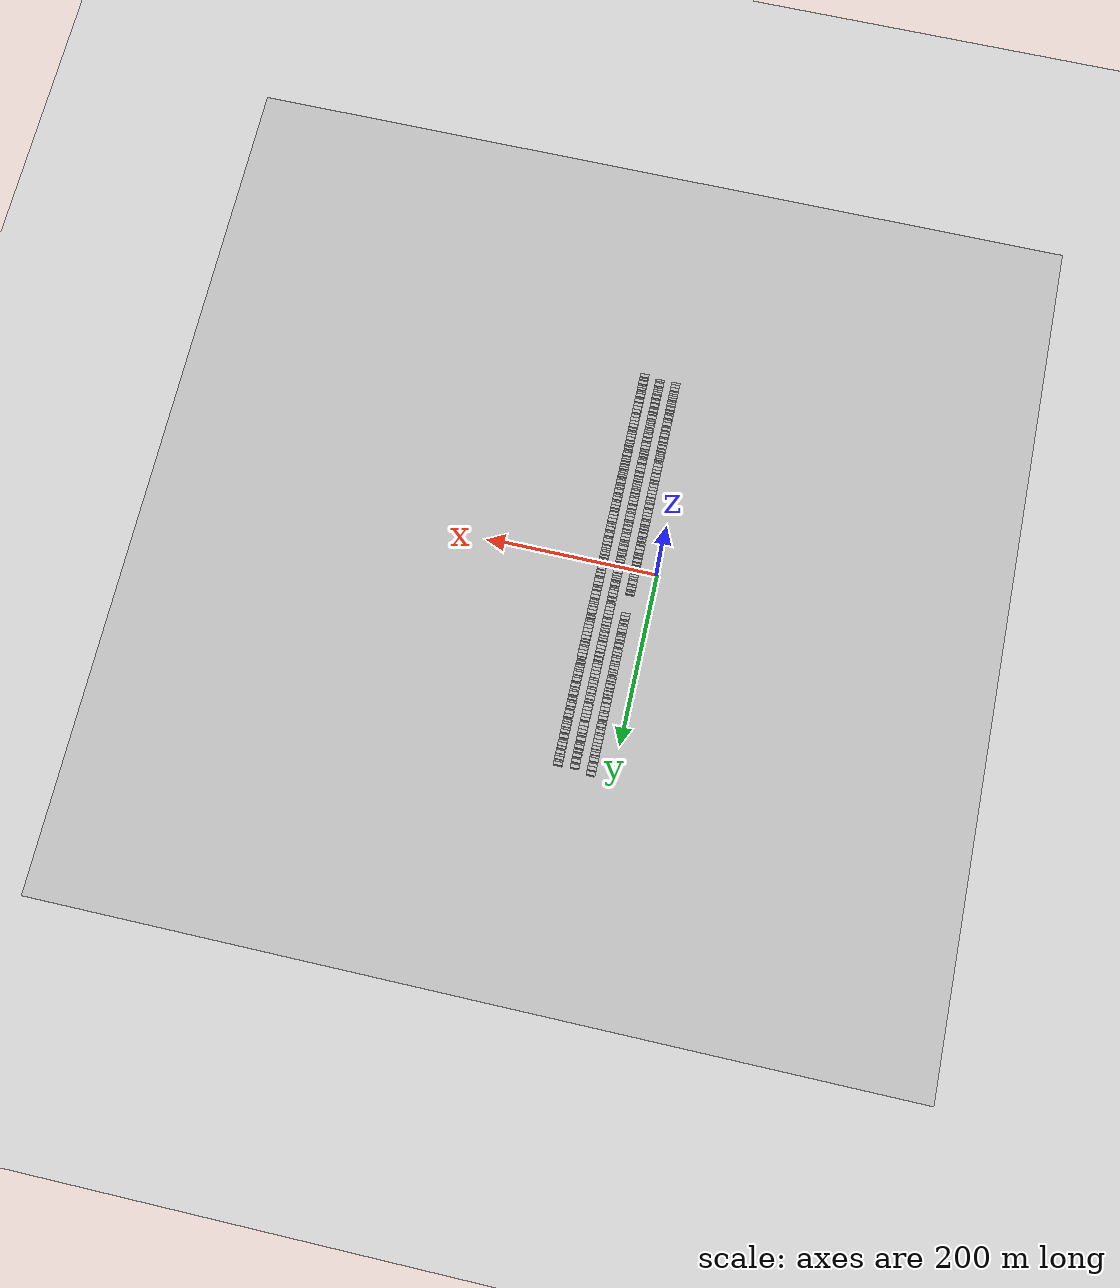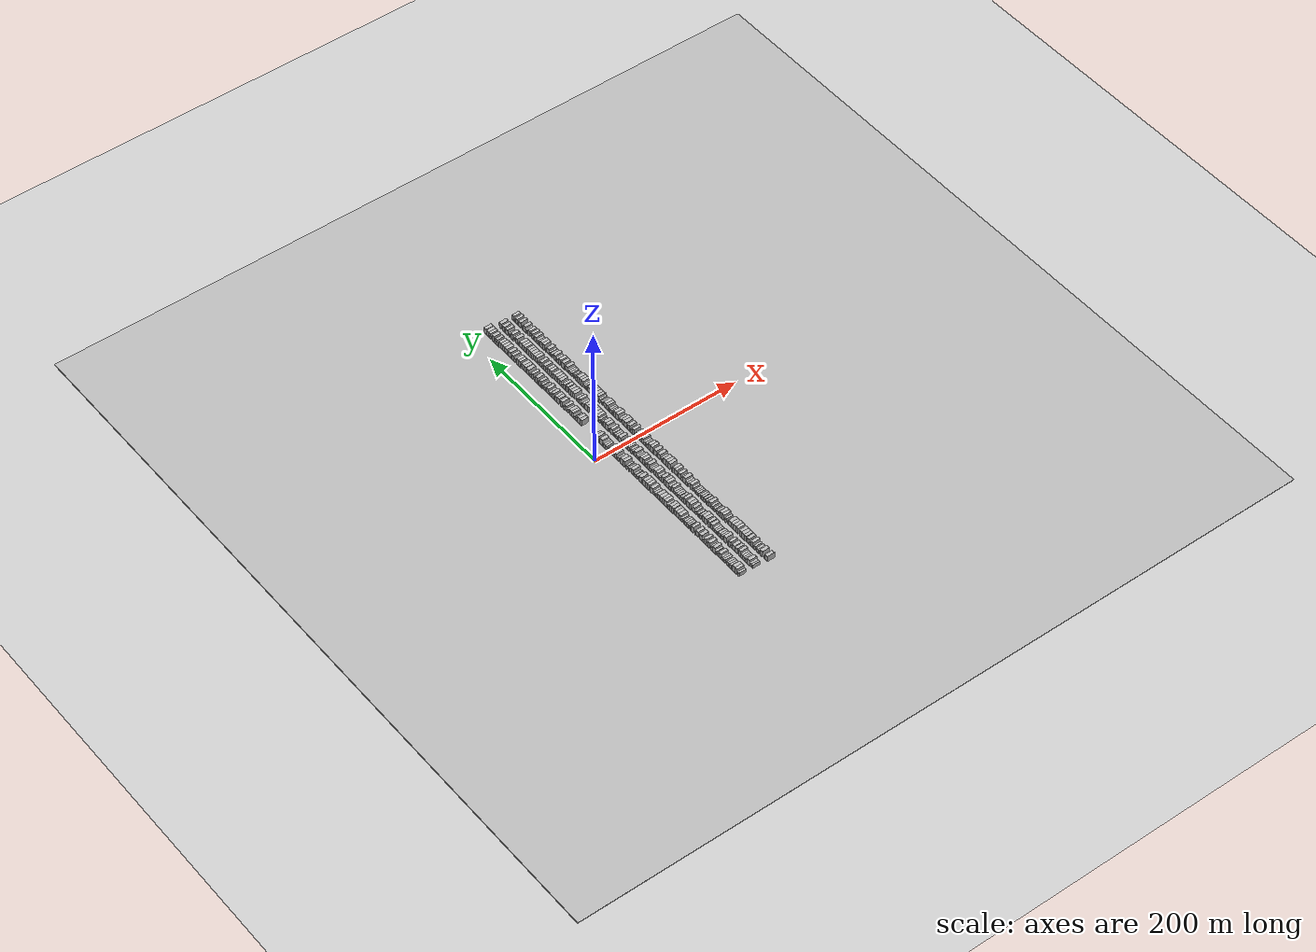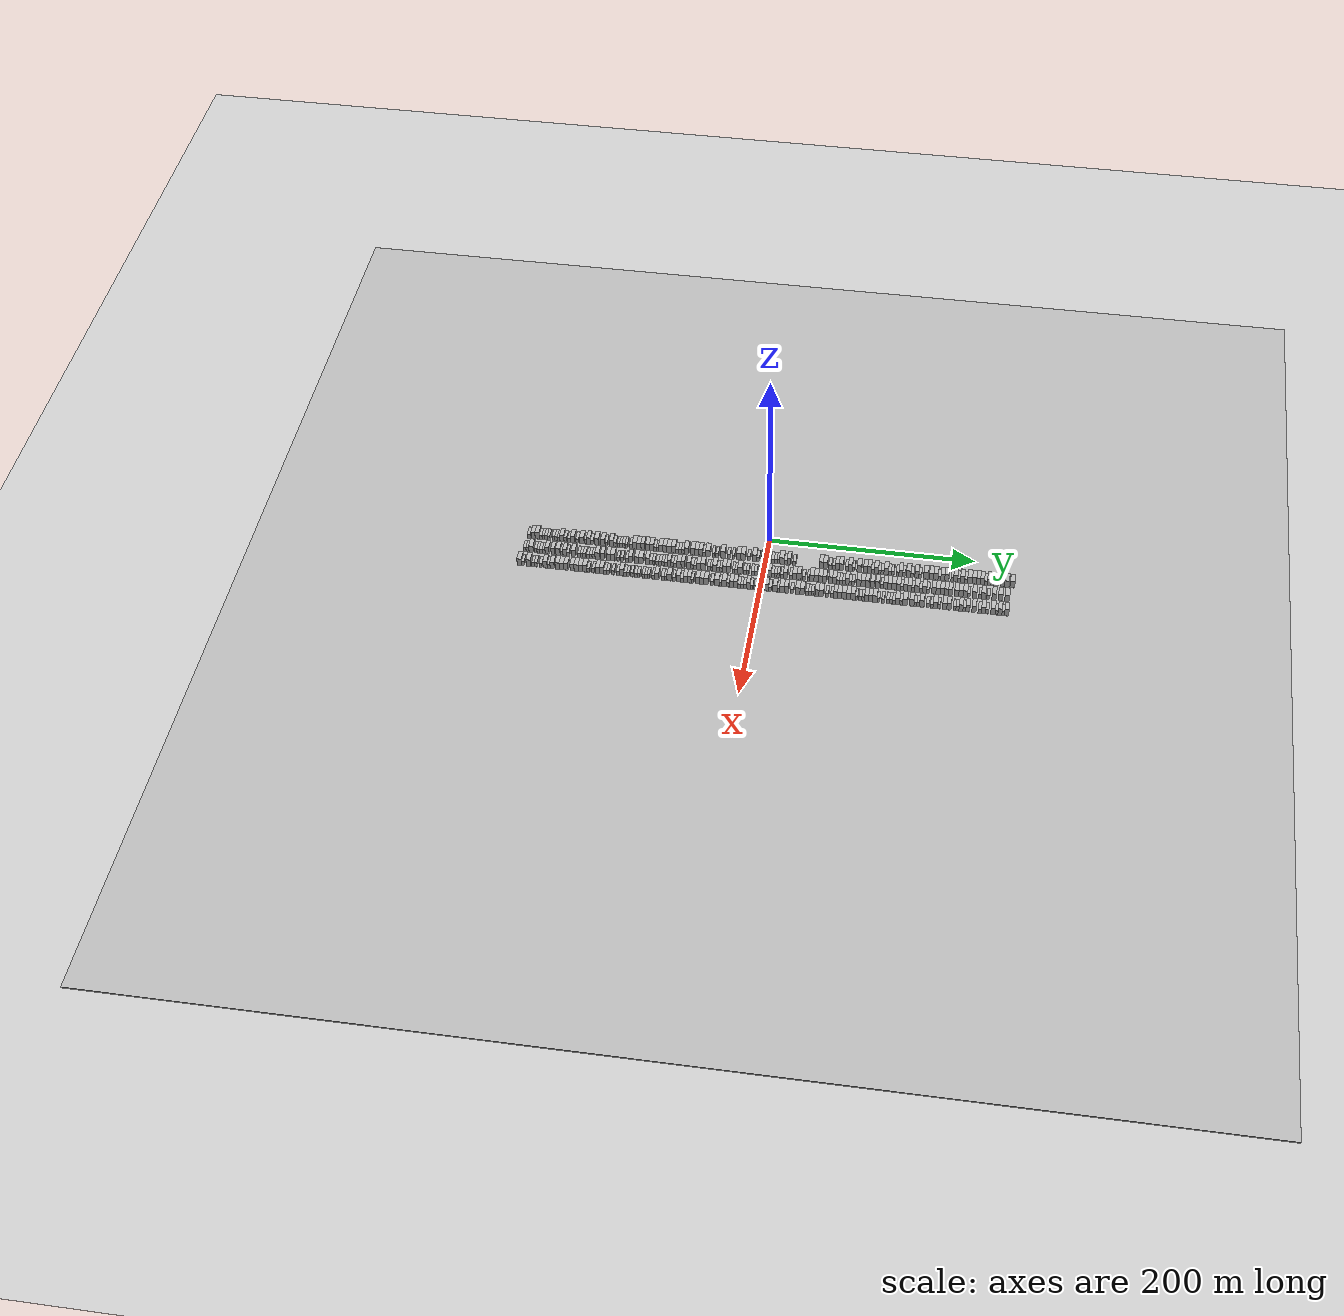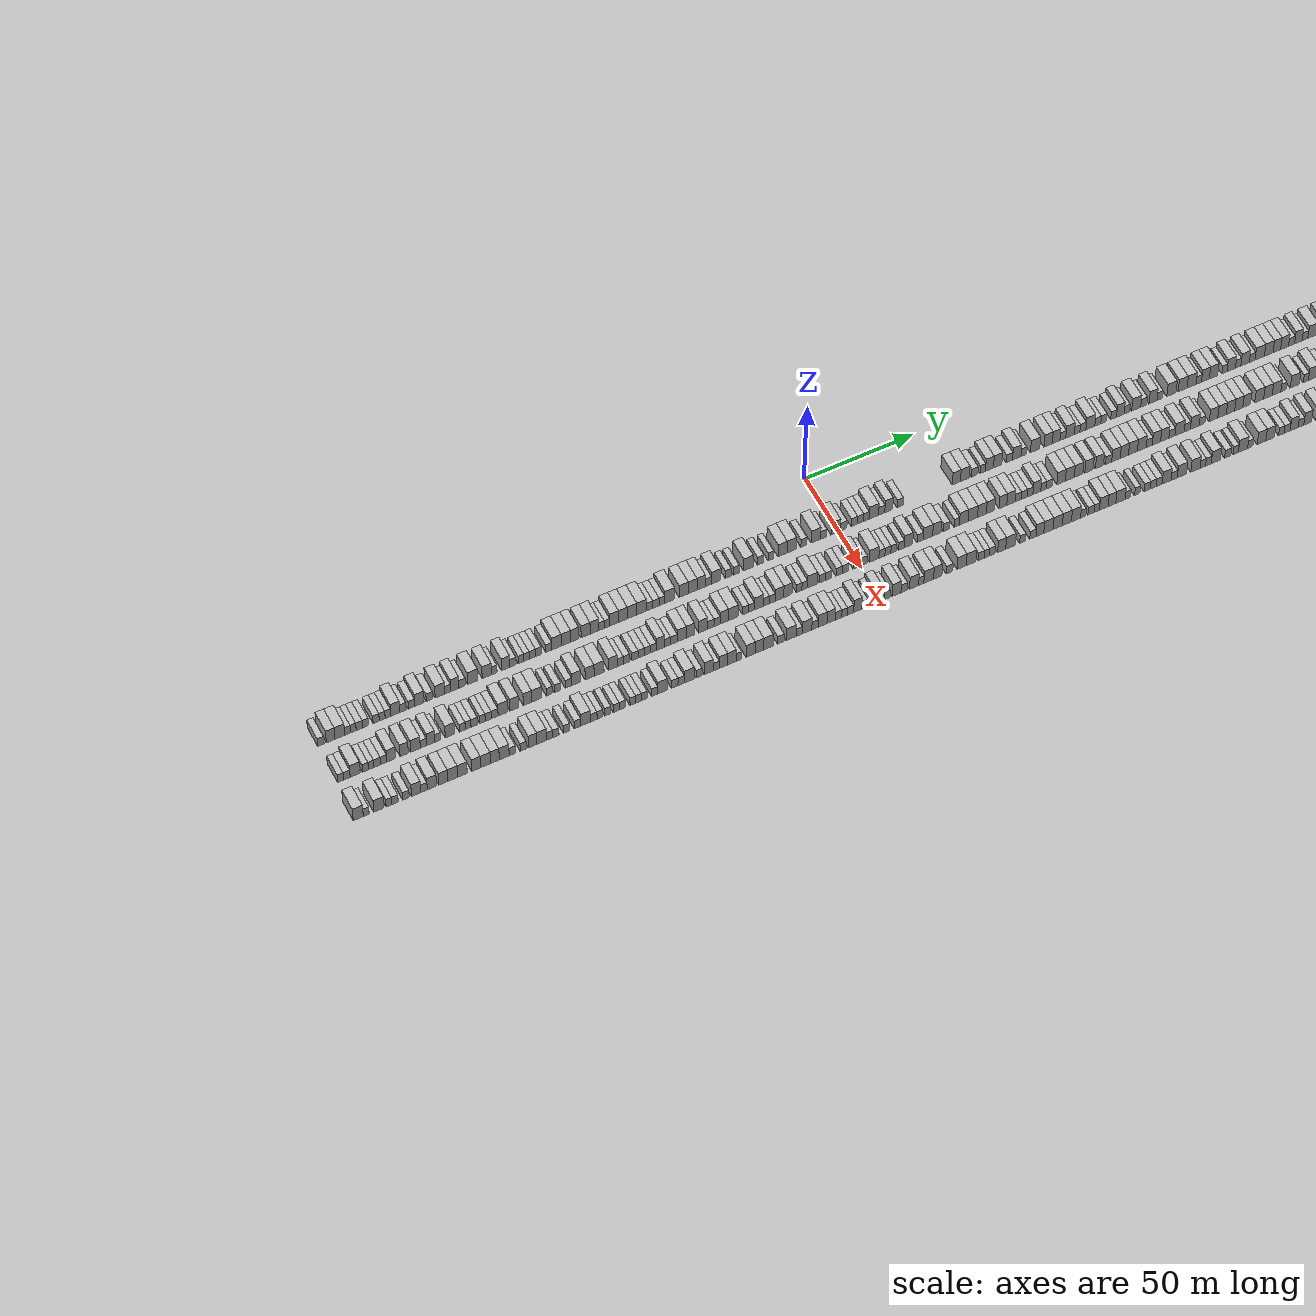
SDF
<?xml version="1.0" encoding="utf-8"?>

<sdf version="1.6">

   <world name="default">

      <gui fullscreen="0">

         <camera name="user_camera">

            <pose>-15 0 4.57585 0 0 0</pose>

            <view_controller>orbit</view_controller>

         </camera>

      </gui>

      <scene>

         <sky>

           <clouds>

             <speed>12</speed>

           </clouds>

         </sky>

         <ambient>0.4 0.4 0.4 1</ambient>

         <background>0.7 0.7 0.7 1</background>

         <shadows>1</shadows>

      </scene>

      <gravity>0 0 -9.8066</gravity>

      <magnetic_field>6e-06 2.3e-05 -4.2e-05</magnetic_field>

      <physics default="0" name="default_physics" type="ode">

         <ode>

            <solver>

               <type>quick</type>

               <iters>10</iters>

               <sor>1.0</sor>

               <use_dynamic_moi_rescaling>0</use_dynamic_moi_rescaling>

            </solver>

            <constraints>

               <cfm>0</cfm>

               <erp>0.2</erp>

               <contact_max_correcting_vel>100</contact_max_correcting_vel>

               <contact_surface_layer>0.001</contact_surface_layer>

            </constraints>

         </ode>

         <max_step_size>0.004</max_step_size>

         <real_time_factor>1</real_time_factor>

         <real_time_update_rate>250</real_time_update_rate>

      </physics>

      <light name="sun" type="directional">

         <cast_shadows>1</cast_shadows>

         <pose>0 0 10 0 0 0</pose>

         <diffuse>0.8 0.8 0.8 1</diffuse>

         <specular>0.2 0.2 0.2 1</specular>

         <attenuation>

            <range>1000</range>

            <constant>0.9</constant>

            <linear>0.01</linear>

            <quadratic>0.001</quadratic>

         </attenuation>

         <direction>-0.5 0.1 -0.9</direction>

      </light>

      <include>

         <name>ground_plane_1</name>

         <uri>model://HANNAS_ground_plane</uri>

         <pose>0 0 0  0 0 0</pose>

      </include>

      <include>

         <name>ground_plane_2</name>

         <uri>model://HANNAS_ground_plane</uri>

         <pose>100 0 0  0 0 0</pose>

      </include>

      <model name="building_1">

         <static>1</static>

         <pose frame="">25.0000 -232.6231 0 0.000000 0.000000 0.000000</pose>

         <link name="link">

            <pose frame="">0 0 3.00 0 0 0</pose>

            <collision name="collision">

               <geometry>

                  <box>

                     <size>10.0000 2.7538 6.0000</size>

                  </box>

               </geometry>

               <max_contacts>10</max_contacts>

               <surface>

                  <contact>

                     <ode/>

                  </contact>

                  <bounce/>

                  <friction>

                     <torsional>

                        <ode/>

                     </torsional>

                     <ode/>

                  </friction>

               </surface>

            </collision>

            <visual name="visual">

               <cast_shadows>0</cast_shadows>

               <geometry>

                  <box>

                     <size>10.0000 2.7538 6.0000</size>

                  </box>

               </geometry>

               <material>

                  <script>

                     <uri>model://HANNAS_wall/materials/scripts</uri>

                     <uri>model://HANNAS_wall/materials/textures</uri>

                     <name>vrc/HANNAS_wall</name>

                  </script>

               </material>

            </visual>

            <self_collide>0</self_collide>

            <enable_wind>0</enable_wind>

            <kinematic>0</kinematic>

         </link>

      </model>

      <model name="building_2">

         <static>1</static>

         <pose frame="">25.0000 -228.3459 0 0.000000 0.000000 0.000000</pose>

         <link name="link">

            <pose frame="">0 0 4.50 0 0 0</pose>

            <collision name="collision">

               <geometry>

                  <box>

                     <size>10.0000 3.8005 9.0000</size>

                  </box>

               </geometry>

               <max_contacts>10</max_contacts>

               <surface>

                  <contact>

                     <ode/>

                  </contact>

                  <bounce/>

                  <friction>

                     <torsional>

                        <ode/>

                     </torsional>

                     <ode/>

                  </friction>

               </surface>

            </collision>

            <visual name="visual">

               <cast_shadows>0</cast_shadows>

               <geometry>

                  <box>

                     <size>10.0000 3.8005 9.0000</size>

                  </box>

               </geometry>

               <material>

                  <script>

                     <uri>model://HANNAS_wall/materials/scripts</uri>

                     <uri>model://HANNAS_wall/materials/textures</uri>

                     <name>vrc/HANNAS_wall</name>

                  </script>

               </material>

            </visual>

            <self_collide>0</self_collide>

            <enable_wind>0</enable_wind>

            <kinematic>0</kinematic>

         </link>

      </model>

      <model name="building_3">

         <static>1</static>

         <pose frame="">25.0000 -224.2984 0 0.000000 0.000000 0.000000</pose>

         <link name="link">

            <pose frame="">0 0 4.50 0 0 0</pose>

            <collision name="collision">

               <geometry>

                  <box>

                     <size>10.0000 4.2945 9.0000</size>

                  </box>

               </geometry>

               <max_contacts>10</max_contacts>

               <surface>

                  <contact>

                     <ode/>

                  </contact>

                  <bounce/>

                  <friction>

                     <torsional>

                        <ode/>

                     </torsional>

                     <ode/>

                  </friction>

               </surface>

            </collision>

            <visual name="visual">

               <cast_shadows>0</cast_shadows>

               <geometry>

                  <box>

                     <size>10.0000 4.2945 9.0000</size>

                  </box>

               </geometry>

               <material>

                  <script>

                     <uri>model://HANNAS_wall/materials/scripts</uri>

                     <uri>model://HANNAS_wall/materials/textures</uri>

                     <name>vrc/HANNAS_wall</name>

                  </script>

               </material>

            </visual>

            <self_collide>0</self_collide>

            <enable_wind>0</enable_wind>

            <kinematic>0</kinematic>

         </link>

      </model>

      <model name="building_4">

         <static>1</static>

         <pose frame="">25.0000 -220.8704 0 0.000000 0.000000 0.000000</pose>

         <link name="link">

            <pose frame="">0 0 3.00 0 0 0</pose>

            <collision name="collision">

               <geometry>

                  <box>

                     <size>10.0000 2.5615 6.0000</size>

                  </box>

               </geometry>

               <max_contacts>10</max_contacts>

               <surface>

                  <contact>

                     <ode/>

                  </contact>

                  <bounce/>

                  <friction>

                     <torsional>

                        <ode/>

                     </torsional>

                     <ode/>

                  </friction>

               </surface>

            </collision>

            <visual name="visual">

               <cast_shadows>0</cast_shadows>

               <geometry>

                  <box>

                     <size>10.0000 2.5615 6.0000</size>

                  </box>

               </geometry>

               <material>

                  <script>

                     <uri>model://HANNAS_wall/materials/scripts</uri>

                     <uri>model://HANNAS_wall/materials/textures</uri>

                     <name>vrc/HANNAS_wall</name>

                  </script>

               </material>

            </visual>

            <self_collide>0</self_collide>

            <enable_wind>0</enable_wind>

            <kinematic>0</kinematic>

         </link>

      </model>

      <model name="building_5">

         <static>1</static>

         <pose frame="">25.0000 -218.3513 0 0.000000 0.000000 0.000000</pose>

         <link name="link">

            <pose frame="">0 0 3.00 0 0 0</pose>

            <collision name="collision">

               <geometry>

                  <box>

                     <size>10.0000 2.4766 6.0000</size>

                  </box>

               </geometry>

               <max_contacts>10</max_contacts>

               <surface>

                  <contact>

                     <ode/>

                  </contact>

                  <bounce/>

                  <friction>

                     <torsional>

                        <ode/>

                     </torsional>

                     <ode/>

                  </friction>

               </surface>

            </collision>

            <visual name="visual">

               <cast_shadows>0</cast_shadows>

               <geometry>

                  <box>

                     <size>10.0000 2.4766 6.0000</size>

                  </box>

               </geometry>

               <material>

                  <script>

                     <uri>model://HANNAS_wall/materials/scripts</uri>

                     <uri>model://HANNAS_wall/materials/textures</uri>

                     <name>vrc/HANNAS_wall</name>

                  </script>

               </material>

            </visual>

            <self_collide>0</self_collide>

            <enable_wind>0</enable_wind>

            <kinematic>0</kinematic>

         </link>

      </model>

      <model name="building_6">

         <static>1</static>

         <pose frame="">25.0000 -215.7096 0 0.000000 0.000000 0.000000</pose>

         <link name="link">

            <pose frame="">0 0 3.00 0 0 0</pose>

            <collision name="collision">

               <geometry>

                  <box>

                     <size>10.0000 2.8069 6.0000</size>

                  </box>

               </geometry>

               <max_contacts>10</max_contacts>

               <surface>

                  <contact>

                     <ode/>

                  </contact>

                  <bounce/>

                  <friction>

                     <torsional>

                        <ode/>

                     </torsional>

                     <ode/>

                  </friction>

               </surface>

            </collision>

            <visual name="visual">

               <cast_shadows>0</cast_shadows>

               <geometry>

                  <box>

                     <size>10.0000 2.8069 6.0000</size>

                  </box>

               </geometry>

               <material>

                  <script>

                     <uri>model://HANNAS_wall/materials/scripts</uri>

                     <uri>model://HANNAS_wall/materials/textures</uri>

                     <name>vrc/HANNAS_wall</name>

                  </script>

               </material>

            </visual>

            <self_collide>0</self_collide>

            <enable_wind>0</enable_wind>

            <kinematic>0</kinematic>

         </link>

      </model>

      <model name="building_7">

         <static>1</static>

         <pose frame="">25.0000 -212.9927 0 0.000000 0.000000 0.000000</pose>

         <link name="link">

            <pose frame="">0 0 3.00 0 0 0</pose>

            <collision name="collision">

               <geometry>

                  <box>

                     <size>10.0000 2.6269 6.0000</size>

                  </box>

               </geometry>

               <max_contacts>10</max_contacts>

               <surface>

                  <contact>

                     <ode/>

                  </contact>

                  <bounce/>

                  <friction>

                     <torsional>

                        <ode/>

                     </torsional>

                     <ode/>

                  </friction>

               </surface>

            </collision>

            <visual name="visual">

               <cast_shadows>0</cast_shadows>

               <geometry>

                  <box>

                     <size>10.0000 2.6269 6.0000</size>

                  </box>

               </geometry>

               <material>

                  <script>

                     <uri>model://HANNAS_wall/materials/scripts</uri>

                     <uri>model://HANNAS_wall/materials/textures</uri>

                     <name>vrc/HANNAS_wall</name>

                  </script>

               </material>

            </visual>

            <self_collide>0</self_collide>

            <enable_wind>0</enable_wind>

            <kinematic>0</kinematic>

         </link>

      </model>

      <model name="building_8">

         <static>1</static>

         <pose frame="">25.0000 -208.3134 0 0.000000 0.000000 0.000000</pose>

         <link name="link">

            <pose frame="">0 0 3.00 0 0 0</pose>

            <collision name="collision">

               <geometry>

                  <box>

                     <size>10.0000 2.7316 6.0000</size>

                  </box>

               </geometry>

               <max_contacts>10</max_contacts>

               <surface>

                  <contact>

                     <ode/>

                  </contact>

                  <bounce/>

                  <friction>

                     <torsional>

                        <ode/>

                     </torsional>

                     <ode/>

                  </friction>

               </surface>

            </collision>

            <visual name="visual">

               <cast_shadows>0</cast_shadows>

               <geometry>

                  <box>

                     <size>10.0000 2.7316 6.0000</size>

                  </box>

               </geometry>

               <material>

                  <script>

                     <uri>model://HANNAS_wall/materials/scripts</uri>

                     <uri>model://HANNAS_wall/materials/textures</uri>

                     <name>vrc/HANNAS_wall</name>

                  </script>

               </material>

            </visual>

            <self_collide>0</self_collide>

            <enable_wind>0</enable_wind>

            <kinematic>0</kinematic>

         </link>

      </model>

      <model name="building_9">

         <static>1</static>

         <pose frame="">25.0000 -205.6520 0 0.000000 0.000000 0.000000</pose>

         <link name="link">

            <pose frame="">0 0 3.00 0 0 0</pose>

            <collision name="collision">

               <geometry>

                  <box>

                     <size>10.0000 2.5912 6.0000</size>

                  </box>

               </geometry>

               <max_contacts>10</max_contacts>

               <surface>

                  <contact>

                     <ode/>

                  </contact>

                  <bounce/>

                  <friction>

                     <torsional>

                        <ode/>

                     </torsional>

                     <ode/>

                  </friction>

               </surface>

            </collision>

            <visual name="visual">

               <cast_shadows>0</cast_shadows>

               <geometry>

                  <box>

                     <size>10.0000 2.5912 6.0000</size>

                  </box>

               </geometry>

               <material>

                  <script>

                     <uri>model://HANNAS_wall/materials/scripts</uri>

                     <uri>model://HANNAS_wall/materials/textures</uri>

                     <name>vrc/HANNAS_wall</name>

                  </script>

               </material>

            </visual>

            <self_collide>0</self_collide>

            <enable_wind>0</enable_wind>

            <kinematic>0</kinematic>

         </link>

      </model>

      <model name="building_10">

         <static>1</static>

         <pose frame="">25.0000 -203.1322 0 0.000000 0.000000 0.000000</pose>

         <link name="link">

            <pose frame="">0 0 3.00 0 0 0</pose>

            <collision name="collision">

               <geometry>

                  <box>

                     <size>10.0000 2.4484 6.0000</size>

                  </box>

               </geometry>

               <max_contacts>10</max_contacts>

               <surface>

                  <contact>

                     <ode/>

                  </contact>

                  <bounce/>

                  <friction>

                     <torsional>

                        <ode/>

                     </torsional>

                     <ode/>

                  </friction>

               </surface>

            </collision>

            <visual name="visual">

               <cast_shadows>0</cast_shadows>

               <geometry>

                  <box>

                     <size>10.0000 2.4484 6.0000</size>

                  </box>

               </geometry>

               <material>

                  <script>

                     <uri>model://HANNAS_wall/materials/scripts</uri>

                     <uri>model://HANNAS_wall/materials/textures</uri>

                     <name>vrc/HANNAS_wall</name>

                  </script>

               </material>

            </visual>

            <self_collide>0</self_collide>

            <enable_wind>0</enable_wind>

            <kinematic>0</kinematic>

         </link>

      </model>

      <model name="building_11">

         <static>1</static>

         <pose frame="">25.0000 -199.9052 0 0.000000 0.000000 0.000000</pose>

         <link name="link">

            <pose frame="">0 0 4.50 0 0 0</pose>

            <collision name="collision">

               <geometry>

                  <box>

                     <size>10.0000 4.0058 9.0000</size>

                  </box>

               </geometry>

               <max_contacts>10</max_contacts>

               <surface>

                  <contact>

                     <ode/>

                  </contact>

                  <bounce/>

                  <friction>

                     <torsional>

                        <ode/>

                     </torsional>

                     <ode/>

                  </friction>

               </surface>

            </collision>

            <visual name="visual">

               <cast_shadows>0</cast_shadows>

               <geometry>

                  <box>

                     <size>10.0000 4.0058 9.0000</size>

                  </box>

               </geometry>

               <material>

                  <script>

                     <uri>model://HANNAS_wall/materials/scripts</uri>

                     <uri>model://HANNAS_wall/materials/textures</uri>

                     <name>vrc/HANNAS_wall</name>

                  </script>

               </material>

            </visual>

            <self_collide>0</self_collide>

            <enable_wind>0</enable_wind>

            <kinematic>0</kinematic>

         </link>

      </model>

      <model name="building_12">

         <static>1</static>

         <pose frame="">25.0000 -196.5103 0 0.000000 0.000000 0.000000</pose>

         <link name="link">

            <pose frame="">0 0 3.00 0 0 0</pose>

            <collision name="collision">

               <geometry>

                  <box>

                     <size>10.0000 2.7839 6.0000</size>

                  </box>

               </geometry>

               <max_contacts>10</max_contacts>

               <surface>

                  <contact>

                     <ode/>

                  </contact>

                  <bounce/>

                  <friction>

                     <torsional>

                        <ode/>

                     </torsional>

                     <ode/>

                  </friction>

               </surface>

            </collision>

            <visual name="visual">

               <cast_shadows>0</cast_shadows>

               <geometry>

                  <box>

                     <size>10.0000 2.7839 6.0000</size>

                  </box>

               </geometry>

               <material>

                  <script>

                     <uri>model://HANNAS_wall/materials/scripts</uri>

                     <uri>model://HANNAS_wall/materials/textures</uri>

                     <name>vrc/HANNAS_wall</name>

                  </script>

               </material>

            </visual>

            <self_collide>0</self_collide>

            <enable_wind>0</enable_wind>

            <kinematic>0</kinematic>

         </link>

      </model>

      <model name="building_13">

         <static>1</static>

         <pose frame="">25.0000 -192.6631 0 0.000000 0.000000 0.000000</pose>

         <link name="link">

            <pose frame="">0 0 3.00 0 0 0</pose>

            <collision name="collision">

               <geometry>

                  <box>

                     <size>10.0000 2.9105 6.0000</size>

                  </box>

               </geometry>

               <max_contacts>10</max_contacts>

               <surface>

                  <contact>

                     <ode/>

                  </contact>

                  <bounce/>

                  <friction>

                     <torsional>

                        <ode/>

                     </torsional>

                     <ode/>

                  </friction>

               </surface>

            </collision>

            <visual name="visual">

               <cast_shadows>0</cast_shadows>

               <geometry>

                  <box>

                     <size>10.0000 2.9105 6.0000</size>

                  </box>

               </geometry>

               <material>

                  <script>

                     <uri>model://HANNAS_wall/materials/scripts</uri>

                     <uri>model://HANNAS_wall/materials/textures</uri>

                     <name>vrc/HANNAS_wall</name>

                  </script>

               </material>

            </visual>

            <self_collide>0</self_collide>

            <enable_wind>0</enable_wind>

            <kinematic>0</kinematic>

         </link>

      </model>

      <model name="building_14">

         <static>1</static>

         <pose frame="">25.0000 -189.1998 0 0.000000 0.000000 0.000000</pose>

         <link name="link">

            <pose frame="">0 0 4.50 0 0 0</pose>

            <collision name="collision">

               <geometry>

                  <box>

                     <size>10.0000 4.0162 9.0000</size>

                  </box>

               </geometry>

               <max_contacts>10</max_contacts>

               <surface>

                  <contact>

                     <ode/>

                  </contact>

                  <bounce/>

                  <friction>

                     <torsional>

                        <ode/>

                     </torsional>

                     <ode/>

                  </friction>

               </surface>

            </collision>

            <visual name="visual">

               <cast_shadows>0</cast_shadows>

               <geometry>

                  <box>

                     <size>10.0000 4.0162 9.0000</size>

                  </box>

               </geometry>

               <material>

                  <script>

                     <uri>model://HANNAS_wall/materials/scripts</uri>

                     <uri>model://HANNAS_wall/materials/textures</uri>

                     <name>vrc/HANNAS_wall</name>

                  </script>

               </material>

            </visual>

            <self_collide>0</self_collide>

            <enable_wind>0</enable_wind>

            <kinematic>0</kinematic>

         </link>

      </model>

      <model name="building_15">

         <static>1</static>

         <pose frame="">25.0000 -184.7301 0 0.000000 0.000000 0.000000</pose>

         <link name="link">

            <pose frame="">0 0 3.00 0 0 0</pose>

            <collision name="collision">

               <geometry>

                  <box>

                     <size>10.0000 2.9231 6.0000</size>

                  </box>

               </geometry>

               <max_contacts>10</max_contacts>

               <surface>

                  <contact>

                     <ode/>

                  </contact>

                  <bounce/>

                  <friction>

                     <torsional>

                        <ode/>

                     </torsional>

                     <ode/>

                  </friction>

               </surface>

            </collision>

            <visual name="visual">

               <cast_shadows>0</cast_shadows>

               <geometry>

                  <box>

                     <size>10.0000 2.9231 6.0000</size>

                  </box>

               </geometry>

               <material>

                  <script>

                     <uri>model://HANNAS_wall/materials/scripts</uri>

                     <uri>model://HANNAS_wall/materials/textures</uri>

                     <name>vrc/HANNAS_wall</name>

                  </script>

               </material>

            </visual>

            <self_collide>0</self_collide>

            <enable_wind>0</enable_wind>

            <kinematic>0</kinematic>

         </link>

      </model>

      <model name="building_16">

         <static>1</static>

         <pose frame="">25.0000 -180.0820 0 0.000000 0.000000 0.000000</pose>

         <link name="link">

            <pose frame="">0 0 4.50 0 0 0</pose>

            <collision name="collision">

               <geometry>

                  <box>

                     <size>10.0000 4.3730 9.0000</size>

                  </box>

               </geometry>

               <max_contacts>10</max_contacts>

               <surface>

                  <contact>

                     <ode/>

                  </contact>

                  <bounce/>

                  <friction>

                     <torsional>

                        <ode/>

                     </torsional>

                     <ode/>

                  </friction>

               </surface>

            </collision>

            <visual name="visual">

               <cast_shadows>0</cast_shadows>

               <geometry>

                  <box>

                     <size>10.0000 4.3730 9.0000</size>

                  </box>

               </geometry>

               <material>

                  <script>

                     <uri>model://HANNAS_wall/materials/scripts</uri>

                     <uri>model://HANNAS_wall/materials/textures</uri>

                     <name>vrc/HANNAS_wall</name>

                  </script>

               </material>

            </visual>

            <self_collide>0</self_collide>

            <enable_wind>0</enable_wind>

            <kinematic>0</kinematic>

         </link>

      </model>

      <model name="building_17">

         <static>1</static>

         <pose frame="">25.0000 -176.6190 0 0.000000 0.000000 0.000000</pose>

         <link name="link">

            <pose frame="">0 0 3.00 0 0 0</pose>

            <collision name="collision">

               <geometry>

                  <box>

                     <size>10.0000 2.5530 6.0000</size>

                  </box>

               </geometry>

               <max_contacts>10</max_contacts>

               <surface>

                  <contact>

                     <ode/>

                  </contact>

                  <bounce/>

                  <friction>

                     <torsional>

                        <ode/>

                     </torsional>

                     <ode/>

                  </friction>

               </surface>

            </collision>

            <visual name="visual">

               <cast_shadows>0</cast_shadows>

               <geometry>

                  <box>

                     <size>10.0000 2.5530 6.0000</size>

                  </box>

               </geometry>

               <material>

                  <script>

                     <uri>model://HANNAS_wall/materials/scripts</uri>

                     <uri>model://HANNAS_wall/materials/textures</uri>

                     <name>vrc/HANNAS_wall</name>

                  </script>

               </material>

            </visual>

            <self_collide>0</self_collide>

            <enable_wind>0</enable_wind>

            <kinematic>0</kinematic>

         </link>

      </model>

      <model name="building_18">

         <static>1</static>

         <pose frame="">25.0000 -173.5140 0 0.000000 0.000000 0.000000</pose>

         <link name="link">

            <pose frame="">0 0 4.50 0 0 0</pose>

            <collision name="collision">

               <geometry>

                  <box>

                     <size>10.0000 3.6569 9.0000</size>

                  </box>

               </geometry>

               <max_contacts>10</max_contacts>

               <surface>

                  <contact>

                     <ode/>

                  </contact>

                  <bounce/>

                  <friction>

                     <torsional>

                        <ode/>

                     </torsional>

                     <ode/>

                  </friction>

               </surface>

            </collision>

            <visual name="visual">

               <cast_shadows>0</cast_shadows>

               <geometry>

                  <box>

                     <size>10.0000 3.6569 9.0000</size>

                  </box>

               </geometry>

               <material>

                  <script>

                     <uri>model://HANNAS_wall/materials/scripts</uri>

                     <uri>model://HANNAS_wall/materials/textures</uri>

                     <name>vrc/HANNAS_wall</name>

                  </script>

               </material>

            </visual>

            <self_collide>0</self_collide>

            <enable_wind>0</enable_wind>

            <kinematic>0</kinematic>

         </link>

      </model>

      <model name="building_19">

         <static>1</static>

         <pose frame="">25.0000 -170.2502 0 0.000000 0.000000 0.000000</pose>

         <link name="link">

            <pose frame="">0 0 3.00 0 0 0</pose>

            <collision name="collision">

               <geometry>

                  <box>

                     <size>10.0000 2.8706 6.0000</size>

                  </box>

               </geometry>

               <max_contacts>10</max_contacts>

               <surface>

                  <contact>

                     <ode/>

                  </contact>

                  <bounce/>

                  <friction>

                     <torsional>

                        <ode/>

                     </torsional>

                     <ode/>

                  </friction>

               </surface>

            </collision>

            <visual name="visual">

               <cast_shadows>0</cast_shadows>

               <geometry>

                  <box>

                     <size>10.0000 2.8706 6.0000</size>

                  </box>

               </geometry>

               <material>

                  <script>

                     <uri>model://HANNAS_wall/materials/scripts</uri>

                     <uri>model://HANNAS_wall/materials/textures</uri>

                     <name>vrc/HANNAS_wall</name>

                  </script>

               </material>

            </visual>

            <self_collide>0</self_collide>

            <enable_wind>0</enable_wind>

            <kinematic>0</kinematic>

         </link>

      </model>

      <model name="building_20">

         <static>1</static>

         <pose frame="">25.0000 -165.5959 0 0.000000 0.000000 0.000000</pose>

         <link name="link">

            <pose frame="">0 0 4.50 0 0 0</pose>

            <collision name="collision">

               <geometry>

                  <box>

                     <size>10.0000 4.4382 9.0000</size>

                  </box>

               </geometry>

               <max_contacts>10</max_contacts>

               <surface>

                  <contact>

                     <ode/>

                  </contact>

                  <bounce/>

                  <friction>

                     <torsional>

                        <ode/>

                     </torsional>

                     <ode/>

                  </friction>

               </surface>

            </collision>

            <visual name="visual">

               <cast_shadows>0</cast_shadows>

               <geometry>

                  <box>

                     <size>10.0000 4.4382 9.0000</size>

                  </box>

               </geometry>

               <material>

                  <script>

                     <uri>model://HANNAS_wall/materials/scripts</uri>

                     <uri>model://HANNAS_wall/materials/textures</uri>

                     <name>vrc/HANNAS_wall</name>

                  </script>

               </material>

            </visual>

            <self_collide>0</self_collide>

            <enable_wind>0</enable_wind>

            <kinematic>0</kinematic>

         </link>

      </model>

      <model name="building_21">

         <static>1</static>

         <pose frame="">25.0000 -159.2949 0 0.000000 0.000000 0.000000</pose>

         <link name="link">

            <pose frame="">0 0 4.50 0 0 0</pose>

            <collision name="collision">

               <geometry>

                  <box>

                     <size>10.0000 4.1638 9.0000</size>

                  </box>

               </geometry>

               <max_contacts>10</max_contacts>

               <surface>

                  <contact>

                     <ode/>

                  </contact>

                  <bounce/>

                  <friction>

                     <torsional>

                        <ode/>

                     </torsional>

                     <ode/>

                  </friction>

               </surface>

            </collision>

            <visual name="visual">

               <cast_shadows>0</cast_shadows>

               <geometry>

                  <box>

                     <size>10.0000 4.1638 9.0000</size>

                  </box>

               </geometry>

               <material>

                  <script>

                     <uri>model://HANNAS_wall/materials/scripts</uri>

                     <uri>model://HANNAS_wall/materials/textures</uri>

                     <name>vrc/HANNAS_wall</name>

                  </script>

               </material>

            </visual>

            <self_collide>0</self_collide>

            <enable_wind>0</enable_wind>

            <kinematic>0</kinematic>

         </link>

      </model>

      <model name="building_22">

         <static>1</static>

         <pose frame="">25.0000 -155.9854 0 0.000000 0.000000 0.000000</pose>

         <link name="link">

            <pose frame="">0 0 3.00 0 0 0</pose>

            <collision name="collision">

               <geometry>

                  <box>

                     <size>10.0000 2.4551 6.0000</size>

                  </box>

               </geometry>

               <max_contacts>10</max_contacts>

               <surface>

                  <contact>

                     <ode/>

                  </contact>

                  <bounce/>

                  <friction>

                     <torsional>

                        <ode/>

                     </torsional>

                     <ode/>

                  </friction>

               </surface>

            </collision>

            <visual name="visual">

               <cast_shadows>0</cast_shadows>

               <geometry>

                  <box>

                     <size>10.0000 2.4551 6.0000</size>

                  </box>

               </geometry>

               <material>

                  <script>

                     <uri>model://HANNAS_wall/materials/scripts</uri>

                     <uri>model://HANNAS_wall/materials/textures</uri>

                     <name>vrc/HANNAS_wall</name>

                  </script>

               </material>

            </visual>

            <self_collide>0</self_collide>

            <enable_wind>0</enable_wind>

            <kinematic>0</kinematic>

         </link>

      </model>

      <model name="building_23">

         <static>1</static>

         <pose frame="">25.0000 -150.8840 0 0.000000 0.000000 0.000000</pose>

         <link name="link">

            <pose frame="">0 0 4.50 0 0 0</pose>

            <collision name="collision">

               <geometry>

                  <box>

                     <size>10.0000 3.7478 9.0000</size>

                  </box>

               </geometry>

               <max_contacts>10</max_contacts>

               <surface>

                  <contact>

                     <ode/>

                  </contact>

                  <bounce/>

                  <friction>

                     <torsional>

                        <ode/>

                     </torsional>

                     <ode/>

                  </friction>

               </surface>

            </collision>

            <visual name="visual">

               <cast_shadows>0</cast_shadows>

               <geometry>

                  <box>

                     <size>10.0000 3.7478 9.0000</size>

                  </box>

               </geometry>

               <material>

                  <script>

                     <uri>model://HANNAS_wall/materials/scripts</uri>

                     <uri>model://HANNAS_wall/materials/textures</uri>

                     <name>vrc/HANNAS_wall</name>

                  </script>

               </material>

            </visual>

            <self_collide>0</self_collide>

            <enable_wind>0</enable_wind>

            <kinematic>0</kinematic>

         </link>

      </model>

      <model name="building_24">

         <static>1</static>

         <pose frame="">25.0000 -147.6356 0 0.000000 0.000000 0.000000</pose>

         <link name="link">

            <pose frame="">0 0 3.00 0 0 0</pose>

            <collision name="collision">

               <geometry>

                  <box>

                     <size>10.0000 2.7489 6.0000</size>

                  </box>

               </geometry>

               <max_contacts>10</max_contacts>

               <surface>

                  <contact>

                     <ode/>

                  </contact>

                  <bounce/>

                  <friction>

                     <torsional>

                        <ode/>

                     </torsional>

                     <ode/>

                  </friction>

               </surface>

            </collision>

            <visual name="visual">

               <cast_shadows>0</cast_shadows>

               <geometry>

                  <box>

                     <size>10.0000 2.7489 6.0000</size>

                  </box>

               </geometry>

               <material>

                  <script>

                     <uri>model://HANNAS_wall/materials/scripts</uri>

                     <uri>model://HANNAS_wall/materials/textures</uri>

                     <name>vrc/HANNAS_wall</name>

                  </script>

               </material>

            </visual>

            <self_collide>0</self_collide>

            <enable_wind>0</enable_wind>

            <kinematic>0</kinematic>

         </link>

      </model>

      <model name="building_25">

         <static>1</static>

         <pose frame="">25.0000 -144.0206 0 0.000000 0.000000 0.000000</pose>

         <link name="link">

            <pose frame="">0 0 3.00 0 0 0</pose>

            <collision name="collision">

               <geometry>

                  <box>

                     <size>10.0000 2.4812 6.0000</size>

                  </box>

               </geometry>

               <max_contacts>10</max_contacts>

               <surface>

                  <contact>

                     <ode/>

                  </contact>

                  <bounce/>

                  <friction>

                     <torsional>

                        <ode/>

                     </torsional>

                     <ode/>

                  </friction>

               </surface>

            </collision>

            <visual name="visual">

               <cast_shadows>0</cast_shadows>

               <geometry>

                  <box>

                     <size>10.0000 2.4812 6.0000</size>

                  </box>

               </geometry>

               <material>

                  <script>

                     <uri>model://HANNAS_wall/materials/scripts</uri>

                     <uri>model://HANNAS_wall/materials/textures</uri>

                     <name>vrc/HANNAS_wall</name>

                  </script>

               </material>

            </visual>

            <self_collide>0</self_collide>

            <enable_wind>0</enable_wind>

            <kinematic>0</kinematic>

         </link>

      </model>

      <model name="building_26">

         <static>1</static>

         <pose frame="">25.0000 -141.5740 0 0.000000 0.000000 0.000000</pose>

         <link name="link">

            <pose frame="">0 0 3.00 0 0 0</pose>

            <collision name="collision">

               <geometry>

                  <box>

                     <size>10.0000 2.4120 6.0000</size>

                  </box>

               </geometry>

               <max_contacts>10</max_contacts>

               <surface>

                  <contact>

                     <ode/>

                  </contact>

                  <bounce/>

                  <friction>

                     <torsional>

                        <ode/>

                     </torsional>

                     <ode/>

                  </friction>

               </surface>

            </collision>

            <visual name="visual">

               <cast_shadows>0</cast_shadows>

               <geometry>

                  <box>

                     <size>10.0000 2.4120 6.0000</size>

                  </box>

               </geometry>

               <material>

                  <script>

                     <uri>model://HANNAS_wall/materials/scripts</uri>

                     <uri>model://HANNAS_wall/materials/textures</uri>

                     <name>vrc/HANNAS_wall</name>

                  </script>

               </material>

            </visual>

            <self_collide>0</self_collide>

            <enable_wind>0</enable_wind>

            <kinematic>0</kinematic>

         </link>

      </model>

      <model name="building_27">

         <static>1</static>

         <pose frame="">25.0000 -138.9465 0 0.000000 0.000000 0.000000</pose>

         <link name="link">

            <pose frame="">0 0 3.00 0 0 0</pose>

            <collision name="collision">

               <geometry>

                  <box>

                     <size>10.0000 2.8429 6.0000</size>

                  </box>

               </geometry>

               <max_contacts>10</max_contacts>

               <surface>

                  <contact>

                     <ode/>

                  </contact>

                  <bounce/>

                  <friction>

                     <torsional>

                        <ode/>

                     </torsional>

                     <ode/>

                  </friction>

               </surface>

            </collision>

            <visual name="visual">

               <cast_shadows>0</cast_shadows>

               <geometry>

                  <box>

                     <size>10.0000 2.8429 6.0000</size>

                  </box>

               </geometry>

               <material>

                  <script>

                     <uri>model://HANNAS_wall/materials/scripts</uri>

                     <uri>model://HANNAS_wall/materials/textures</uri>

                     <name>vrc/HANNAS_wall</name>

                  </script>

               </material>

            </visual>

            <self_collide>0</self_collide>

            <enable_wind>0</enable_wind>

            <kinematic>0</kinematic>

         </link>

      </model>

      <model name="building_28">

         <static>1</static>

         <pose frame="">25.0000 -136.2739 0 0.000000 0.000000 0.000000</pose>

         <link name="link">

            <pose frame="">0 0 3.00 0 0 0</pose>

            <collision name="collision">

               <geometry>

                  <box>

                     <size>10.0000 2.5021 6.0000</size>

                  </box>

               </geometry>

               <max_contacts>10</max_contacts>

               <surface>

                  <contact>

                     <ode/>

                  </contact>

                  <bounce/>

                  <friction>

                     <torsional>

                        <ode/>

                     </torsional>

                     <ode/>

                  </friction>

               </surface>

            </collision>

            <visual name="visual">

               <cast_shadows>0</cast_shadows>

               <geometry>

                  <box>

                     <size>10.0000 2.5021 6.0000</size>

                  </box>

               </geometry>

               <material>

                  <script>

                     <uri>model://HANNAS_wall/materials/scripts</uri>

                     <uri>model://HANNAS_wall/materials/textures</uri>

                     <name>vrc/HANNAS_wall</name>

                  </script>

               </material>

            </visual>

            <self_collide>0</self_collide>

            <enable_wind>0</enable_wind>

            <kinematic>0</kinematic>

         </link>

      </model>

      <model name="building_29">

         <static>1</static>

         <pose frame="">25.0000 -131.6614 0 0.000000 0.000000 0.000000</pose>

         <link name="link">

            <pose frame="">0 0 3.00 0 0 0</pose>

            <collision name="collision">

               <geometry>

                  <box>

                     <size>10.0000 2.7230 6.0000</size>

                  </box>

               </geometry>

               <max_contacts>10</max_contacts>

               <surface>

                  <contact>

                     <ode/>

                  </contact>

                  <bounce/>

                  <friction>

                     <torsional>

                        <ode/>

                     </torsional>

                     <ode/>

                  </friction>

               </surface>

            </collision>

            <visual name="visual">

               <cast_shadows>0</cast_shadows>

               <geometry>

                  <box>

                     <size>10.0000 2.7230 6.0000</size>

                  </box>

               </geometry>

               <material>

                  <script>

                     <uri>model://HANNAS_wall/materials/scripts</uri>

                     <uri>model://HANNAS_wall/materials/textures</uri>

                     <name>vrc/HANNAS_wall</name>

                  </script>

               </material>

            </visual>

            <self_collide>0</self_collide>

            <enable_wind>0</enable_wind>

            <kinematic>0</kinematic>

         </link>

      </model>

      <model name="building_30">

         <static>1</static>

         <pose frame="">25.0000 -128.1319 0 0.000000 0.000000 0.000000</pose>

         <link name="link">

            <pose frame="">0 0 4.50 0 0 0</pose>

            <collision name="collision">

               <geometry>

                  <box>

                     <size>10.0000 4.3360 9.0000</size>

                  </box>

               </geometry>

               <max_contacts>10</max_contacts>

               <surface>

                  <contact>

                     <ode/>

                  </contact>

                  <bounce/>

                  <friction>

                     <torsional>

                        <ode/>

                     </torsional>

                     <ode/>

                  </friction>

               </surface>

            </collision>

            <visual name="visual">

               <cast_shadows>0</cast_shadows>

               <geometry>

                  <box>

                     <size>10.0000 4.3360 9.0000</size>

                  </box>

               </geometry>

               <material>

                  <script>

                     <uri>model://HANNAS_wall/materials/scripts</uri>

                     <uri>model://HANNAS_wall/materials/textures</uri>

                     <name>vrc/HANNAS_wall</name>

                  </script>

               </material>

            </visual>

            <self_collide>0</self_collide>

            <enable_wind>0</enable_wind>

            <kinematic>0</kinematic>

         </link>

      </model>

      <model name="building_31">

         <static>1</static>

         <pose frame="">25.0000 -123.8692 0 0.000000 0.000000 0.000000</pose>

         <link name="link">

            <pose frame="">0 0 4.50 0 0 0</pose>

            <collision name="collision">

               <geometry>

                  <box>

                     <size>10.0000 4.1894 9.0000</size>

                  </box>

               </geometry>

               <max_contacts>10</max_contacts>

               <surface>

                  <contact>

                     <ode/>

                  </contact>

                  <bounce/>

                  <friction>

                     <torsional>

                        <ode/>

                     </torsional>

                     <ode/>

                  </friction>

               </surface>

            </collision>

            <visual name="visual">

               <cast_shadows>0</cast_shadows>

               <geometry>

                  <box>

                     <size>10.0000 4.1894 9.0000</size>

                  </box>

               </geometry>

               <material>

                  <script>

                     <uri>model://HANNAS_wall/materials/scripts</uri>

                     <uri>model://HANNAS_wall/materials/textures</uri>

                     <name>vrc/HANNAS_wall</name>

                  </script>

               </material>

            </visual>

            <self_collide>0</self_collide>

            <enable_wind>0</enable_wind>

            <kinematic>0</kinematic>

         </link>

      </model>

      <model name="building_32">

         <static>1</static>

         <pose frame="">25.0000 -119.9717 0 0.000000 0.000000 0.000000</pose>

         <link name="link">

            <pose frame="">0 0 4.50 0 0 0</pose>

            <collision name="collision">

               <geometry>

                  <box>

                     <size>10.0000 3.6055 9.0000</size>

                  </box>

               </geometry>

               <max_contacts>10</max_contacts>

               <surface>

                  <contact>

                     <ode/>

                  </contact>

                  <bounce/>

                  <friction>

                     <torsional>

                        <ode/>

                     </torsional>

                     <ode/>

                  </friction>

               </surface>

            </collision>

            <visual name="visual">

               <cast_shadows>0</cast_shadows>

               <geometry>

                  <box>

                     <size>10.0000 3.6055 9.0000</size>

                  </box>

               </geometry>

               <material>

                  <script>

                     <uri>model://HANNAS_wall/materials/scripts</uri>

                     <uri>model://HANNAS_wall/materials/textures</uri>

                     <name>vrc/HANNAS_wall</name>

                  </script>

               </material>

            </visual>

            <self_collide>0</self_collide>

            <enable_wind>0</enable_wind>

            <kinematic>0</kinematic>

         </link>

      </model>

      <model name="building_33">

         <static>1</static>

         <pose frame="">25.0000 -115.1408 0 0.000000 0.000000 0.000000</pose>

         <link name="link">

            <pose frame="">0 0 4.50 0 0 0</pose>

            <collision name="collision">

               <geometry>

                  <box>

                     <size>10.0000 4.0563 9.0000</size>

                  </box>

               </geometry>

               <max_contacts>10</max_contacts>

               <surface>

                  <contact>

                     <ode/>

                  </contact>

                  <bounce/>

                  <friction>

                     <torsional>

                        <ode/>

                     </torsional>

                     <ode/>

                  </friction>

               </surface>

            </collision>

            <visual name="visual">

               <cast_shadows>0</cast_shadows>

               <geometry>

                  <box>

                     <size>10.0000 4.0563 9.0000</size>

                  </box>

               </geometry>

               <material>

                  <script>

                     <uri>model://HANNAS_wall/materials/scripts</uri>

                     <uri>model://HANNAS_wall/materials/textures</uri>

                     <name>vrc/HANNAS_wall</name>

                  </script>

               </material>

            </visual>

            <self_collide>0</self_collide>

            <enable_wind>0</enable_wind>

            <kinematic>0</kinematic>

         </link>

      </model>

      <model name="building_34">

         <static>1</static>

         <pose frame="">25.0000 -111.1543 0 0.000000 0.000000 0.000000</pose>

         <link name="link">

            <pose frame="">0 0 4.50 0 0 0</pose>

            <collision name="collision">

               <geometry>

                  <box>

                     <size>10.0000 3.9168 9.0000</size>

                  </box>

               </geometry>

               <max_contacts>10</max_contacts>

               <surface>

                  <contact>

                     <ode/>

                  </contact>

                  <bounce/>

                  <friction>

                     <torsional>

                        <ode/>

                     </torsional>

                     <ode/>

                  </friction>

               </surface>

            </collision>

            <visual name="visual">

               <cast_shadows>0</cast_shadows>

               <geometry>

                  <box>

                     <size>10.0000 3.9168 9.0000</size>

                  </box>

               </geometry>

               <material>

                  <script>

                     <uri>model://HANNAS_wall/materials/scripts</uri>

                     <uri>model://HANNAS_wall/materials/textures</uri>

                     <name>vrc/HANNAS_wall</name>

                  </script>

               </material>

            </visual>

            <self_collide>0</self_collide>

            <enable_wind>0</enable_wind>

            <kinematic>0</kinematic>

         </link>

      </model>

      <model name="building_35">

         <static>1</static>

         <pose frame="">25.0000 -107.9606 0 0.000000 0.000000 0.000000</pose>

         <link name="link">

            <pose frame="">0 0 3.00 0 0 0</pose>

            <collision name="collision">

               <geometry>

                  <box>

                     <size>10.0000 2.4706 6.0000</size>

                  </box>

               </geometry>

               <max_contacts>10</max_contacts>

               <surface>

                  <contact>

                     <ode/>

                  </contact>

                  <bounce/>

                  <friction>

                     <torsional>

                        <ode/>

                     </torsional>

                     <ode/>

                  </friction>

               </surface>

            </collision>

            <visual name="visual">

               <cast_shadows>0</cast_shadows>

               <geometry>

                  <box>

                     <size>10.0000 2.4706 6.0000</size>

                  </box>

               </geometry>

               <material>

                  <script>

                     <uri>model://HANNAS_wall/materials/scripts</uri>

                     <uri>model://HANNAS_wall/materials/textures</uri>

                     <name>vrc/HANNAS_wall</name>

                  </script>

               </material>

            </visual>

            <self_collide>0</self_collide>

            <enable_wind>0</enable_wind>

            <kinematic>0</kinematic>

         </link>

      </model>

      <model name="building_36">

         <static>1</static>

         <pose frame="">25.0000 -105.4931 0 0.000000 0.000000 0.000000</pose>

         <link name="link">

            <pose frame="">0 0 3.00 0 0 0</pose>

            <collision name="collision">

               <geometry>

                  <box>

                     <size>10.0000 2.4644 6.0000</size>

                  </box>

               </geometry>

               <max_contacts>10</max_contacts>

               <surface>

                  <contact>

                     <ode/>

                  </contact>

                  <bounce/>

                  <friction>

                     <torsional>

                        <ode/>

                     </torsional>

                     <ode/>

                  </friction>

               </surface>

            </collision>

            <visual name="visual">

               <cast_shadows>0</cast_shadows>

               <geometry>

                  <box>

                     <size>10.0000 2.4644 6.0000</size>

                  </box>

               </geometry>

               <material>

                  <script>

                     <uri>model://HANNAS_wall/materials/scripts</uri>

                     <uri>model://HANNAS_wall/materials/textures</uri>

                     <name>vrc/HANNAS_wall</name>

                  </script>

               </material>

            </visual>

            <self_collide>0</self_collide>

            <enable_wind>0</enable_wind>

            <kinematic>0</kinematic>

         </link>

      </model>

      <model name="building_37">

         <static>1</static>

         <pose frame="">25.0000 -102.2749 0 0.000000 0.000000 0.000000</pose>

         <link name="link">

            <pose frame="">0 0 4.50 0 0 0</pose>

            <collision name="collision">

               <geometry>

                  <box>

                     <size>10.0000 3.9720 9.0000</size>

                  </box>

               </geometry>

               <max_contacts>10</max_contacts>

               <surface>

                  <contact>

                     <ode/>

                  </contact>

                  <bounce/>

                  <friction>

                     <torsional>

                        <ode/>

                     </torsional>

                     <ode/>

                  </friction>

               </surface>

            </collision>

            <visual name="visual">

               <cast_shadows>0</cast_shadows>

               <geometry>

                  <box>

                     <size>10.0000 3.9720 9.0000</size>

                  </box>

               </geometry>

               <material>

                  <script>

                     <uri>model://HANNAS_wall/materials/scripts</uri>

                     <uri>model://HANNAS_wall/materials/textures</uri>

                     <name>vrc/HANNAS_wall</name>

                  </script>

               </material>

            </visual>

            <self_collide>0</self_collide>

            <enable_wind>0</enable_wind>

            <kinematic>0</kinematic>

         </link>

      </model>

      <model name="building_38">

         <static>1</static>

         <pose frame="">25.0000 -98.3123 0 0.000000 0.000000 0.000000</pose>

         <link name="link">

            <pose frame="">0 0 4.50 0 0 0</pose>

            <collision name="collision">

               <geometry>

                  <box>

                     <size>10.0000 3.9532 9.0000</size>

                  </box>

               </geometry>

               <max_contacts>10</max_contacts>

               <surface>

                  <contact>

                     <ode/>

                  </contact>

                  <bounce/>

                  <friction>

                     <torsional>

                        <ode/>

                     </torsional>

                     <ode/>

                  </friction>

               </surface>

            </collision>

            <visual name="visual">

               <cast_shadows>0</cast_shadows>

               <geometry>

                  <box>

                     <size>10.0000 3.9532 9.0000</size>

                  </box>

               </geometry>

               <material>

                  <script>

                     <uri>model://HANNAS_wall/materials/scripts</uri>

                     <uri>model://HANNAS_wall/materials/textures</uri>

                     <name>vrc/HANNAS_wall</name>

                  </script>

               </material>

            </visual>

            <self_collide>0</self_collide>

            <enable_wind>0</enable_wind>

            <kinematic>0</kinematic>

         </link>

      </model>

      <model name="building_39">

         <static>1</static>

         <pose frame="">25.0000 -94.1757 0 0.000000 0.000000 0.000000</pose>

         <link name="link">

            <pose frame="">0 0 4.50 0 0 0</pose>

            <collision name="collision">

               <geometry>

                  <box>

                     <size>10.0000 4.3201 9.0000</size>

                  </box>

               </geometry>

               <max_contacts>10</max_contacts>

               <surface>

                  <contact>

                     <ode/>

                  </contact>

                  <bounce/>

                  <friction>

                     <torsional>

                        <ode/>

                     </torsional>

                     <ode/>

                  </friction>

               </surface>

            </collision>

            <visual name="visual">

               <cast_shadows>0</cast_shadows>

               <geometry>

                  <box>

                     <size>10.0000 4.3201 9.0000</size>

                  </box>

               </geometry>

               <material>

                  <script>

                     <uri>model://HANNAS_wall/materials/scripts</uri>

                     <uri>model://HANNAS_wall/materials/textures</uri>

                     <name>vrc/HANNAS_wall</name>

                  </script>

               </material>

            </visual>

            <self_collide>0</self_collide>

            <enable_wind>0</enable_wind>

            <kinematic>0</kinematic>

         </link>

      </model>

      <model name="building_40">

         <static>1</static>

         <pose frame="">25.0000 -89.9072 0 0.000000 0.000000 0.000000</pose>

         <link name="link">

            <pose frame="">0 0 4.50 0 0 0</pose>

            <collision name="collision">

               <geometry>

                  <box>

                     <size>10.0000 4.2168 9.0000</size>

                  </box>

               </geometry>

               <max_contacts>10</max_contacts>

               <surface>

                  <contact>

                     <ode/>

                  </contact>

                  <bounce/>

                  <friction>

                     <torsional>

                        <ode/>

                     </torsional>

                     <ode/>

                  </friction>

               </surface>

            </collision>

            <visual name="visual">

               <cast_shadows>0</cast_shadows>

               <geometry>

                  <box>

                     <size>10.0000 4.2168 9.0000</size>

                  </box>

               </geometry>

               <material>

                  <script>

                     <uri>model://HANNAS_wall/materials/scripts</uri>

                     <uri>model://HANNAS_wall/materials/textures</uri>

                     <name>vrc/HANNAS_wall</name>

                  </script>

               </material>

            </visual>

            <self_collide>0</self_collide>

            <enable_wind>0</enable_wind>

            <kinematic>0</kinematic>

         </link>

      </model>

      <model name="building_41">

         <static>1</static>

         <pose frame="">25.0000 -86.3174 0 0.000000 0.000000 0.000000</pose>

         <link name="link">

            <pose frame="">0 0 3.00 0 0 0</pose>

            <collision name="collision">

               <geometry>

                  <box>

                     <size>10.0000 2.9628 6.0000</size>

                  </box>

               </geometry>

               <max_contacts>10</max_contacts>

               <surface>

                  <contact>

                     <ode/>

                  </contact>

                  <bounce/>

                  <friction>

                     <torsional>

                        <ode/>

                     </torsional>

                     <ode/>

                  </friction>

               </surface>

            </collision>

            <visual name="visual">

               <cast_shadows>0</cast_shadows>

               <geometry>

                  <box>

                     <size>10.0000 2.9628 6.0000</size>

                  </box>

               </geometry>

               <material>

                  <script>

                     <uri>model://HANNAS_wall/materials/scripts</uri>

                     <uri>model://HANNAS_wall/materials/textures</uri>

                     <name>vrc/HANNAS_wall</name>

                  </script>

               </material>

            </visual>

            <self_collide>0</self_collide>

            <enable_wind>0</enable_wind>

            <kinematic>0</kinematic>

         </link>

      </model>

      <model name="building_42">

         <static>1</static>

         <pose frame="">25.0000 -83.4002 0 0.000000 0.000000 0.000000</pose>

         <link name="link">

            <pose frame="">0 0 3.00 0 0 0</pose>

            <collision name="collision">

               <geometry>

                  <box>

                     <size>10.0000 2.8717 6.0000</size>

                  </box>

               </geometry>

               <max_contacts>10</max_contacts>

               <surface>

                  <contact>

                     <ode/>

                  </contact>

                  <bounce/>

                  <friction>

                     <torsional>

                        <ode/>

                     </torsional>

                     <ode/>

                  </friction>

               </surface>

            </collision>

            <visual name="visual">

               <cast_shadows>0</cast_shadows>

               <geometry>

                  <box>

                     <size>10.0000 2.8717 6.0000</size>

                  </box>

               </geometry>

               <material>

                  <script>

                     <uri>model://HANNAS_wall/materials/scripts</uri>

                     <uri>model://HANNAS_wall/materials/textures</uri>

                     <name>vrc/HANNAS_wall</name>

                  </script>

               </material>

            </visual>

            <self_collide>0</self_collide>

            <enable_wind>0</enable_wind>

            <kinematic>0</kinematic>

         </link>

      </model>

      <model name="building_43">

         <static>1</static>

         <pose frame="">25.0000 -80.6808 0 0.000000 0.000000 0.000000</pose>

         <link name="link">

            <pose frame="">0 0 3.00 0 0 0</pose>

            <collision name="collision">

               <geometry>

                  <box>

                     <size>10.0000 2.5671 6.0000</size>

                  </box>

               </geometry>

               <max_contacts>10</max_contacts>

               <surface>

                  <contact>

                     <ode/>

                  </contact>

                  <bounce/>

                  <friction>

                     <torsional>

                        <ode/>

                     </torsional>

                     <ode/>

                  </friction>

               </surface>

            </collision>

            <visual name="visual">

               <cast_shadows>0</cast_shadows>

               <geometry>

                  <box>

                     <size>10.0000 2.5671 6.0000</size>

                  </box>

               </geometry>

               <material>

                  <script>

                     <uri>model://HANNAS_wall/materials/scripts</uri>

                     <uri>model://HANNAS_wall/materials/textures</uri>

                     <name>vrc/HANNAS_wall</name>

                  </script>

               </material>

            </visual>

            <self_collide>0</self_collide>

            <enable_wind>0</enable_wind>

            <kinematic>0</kinematic>

         </link>

      </model>

      <model name="building_44">

         <static>1</static>

         <pose frame="">25.0000 -77.1678 0 0.000000 0.000000 0.000000</pose>

         <link name="link">

            <pose frame="">0 0 4.50 0 0 0</pose>

            <collision name="collision">

               <geometry>

                  <box>

                     <size>10.0000 4.4588 9.0000</size>

                  </box>

               </geometry>

               <max_contacts>10</max_contacts>

               <surface>

                  <contact>

                     <ode/>

                  </contact>

                  <bounce/>

                  <friction>

                     <torsional>

                        <ode/>

                     </torsional>

                     <ode/>

                  </friction>

               </surface>

            </collision>

            <visual name="visual">

               <cast_shadows>0</cast_shadows>

               <geometry>

                  <box>

                     <size>10.0000 4.4588 9.0000</size>

                  </box>

               </geometry>

               <material>

                  <script>

                     <uri>model://HANNAS_wall/materials/scripts</uri>

                     <uri>model://HANNAS_wall/materials/textures</uri>

                     <name>vrc/HANNAS_wall</name>

                  </script>

               </material>

            </visual>

            <self_collide>0</self_collide>

            <enable_wind>0</enable_wind>

            <kinematic>0</kinematic>

         </link>

      </model>

      <model name="building_45">

         <static>1</static>

         <pose frame="">25.0000 -70.8809 0 0.000000 0.000000 0.000000</pose>

         <link name="link">

            <pose frame="">0 0 4.50 0 0 0</pose>

            <collision name="collision">

               <geometry>

                  <box>

                     <size>10.0000 4.1150 9.0000</size>

                  </box>

               </geometry>

               <max_contacts>10</max_contacts>

               <surface>

                  <contact>

                     <ode/>

                  </contact>

                  <bounce/>

                  <friction>

                     <torsional>

                        <ode/>

                     </torsional>

                     <ode/>

                  </friction>

               </surface>

            </collision>

            <visual name="visual">

               <cast_shadows>0</cast_shadows>

               <geometry>

                  <box>

                     <size>10.0000 4.1150 9.0000</size>

                  </box>

               </geometry>

               <material>

                  <script>

                     <uri>model://HANNAS_wall/materials/scripts</uri>

                     <uri>model://HANNAS_wall/materials/textures</uri>

                     <name>vrc/HANNAS_wall</name>

                  </script>

               </material>

            </visual>

            <self_collide>0</self_collide>

            <enable_wind>0</enable_wind>

            <kinematic>0</kinematic>

         </link>

      </model>

      <model name="building_46">

         <static>1</static>

         <pose frame="">25.0000 -66.8334 0 0.000000 0.000000 0.000000</pose>

         <link name="link">

            <pose frame="">0 0 4.50 0 0 0</pose>

            <collision name="collision">

               <geometry>

                  <box>

                     <size>10.0000 3.9800 9.0000</size>

                  </box>

               </geometry>

               <max_contacts>10</max_contacts>

               <surface>

                  <contact>

                     <ode/>

                  </contact>

                  <bounce/>

                  <friction>

                     <torsional>

                        <ode/>

                     </torsional>

                     <ode/>

                  </friction>

               </surface>

            </collision>

            <visual name="visual">

               <cast_shadows>0</cast_shadows>

               <geometry>

                  <box>

                     <size>10.0000 3.9800 9.0000</size>

                  </box>

               </geometry>

               <material>

                  <script>

                     <uri>model://HANNAS_wall/materials/scripts</uri>

                     <uri>model://HANNAS_wall/materials/textures</uri>

                     <name>vrc/HANNAS_wall</name>

                  </script>

               </material>

            </visual>

            <self_collide>0</self_collide>

            <enable_wind>0</enable_wind>

            <kinematic>0</kinematic>

         </link>

      </model>

      <model name="building_47">

         <static>1</static>

         <pose frame="">25.0000 -62.9381 0 0.000000 0.000000 0.000000</pose>

         <link name="link">

            <pose frame="">0 0 4.50 0 0 0</pose>

            <collision name="collision">

               <geometry>

                  <box>

                     <size>10.0000 3.8106 9.0000</size>

                  </box>

               </geometry>

               <max_contacts>10</max_contacts>

               <surface>

                  <contact>

                     <ode/>

                  </contact>

                  <bounce/>

                  <friction>

                     <torsional>

                        <ode/>

                     </torsional>

                     <ode/>

                  </friction>

               </surface>

            </collision>

            <visual name="visual">

               <cast_shadows>0</cast_shadows>

               <geometry>

                  <box>

                     <size>10.0000 3.8106 9.0000</size>

                  </box>

               </geometry>

               <material>

                  <script>

                     <uri>model://HANNAS_wall/materials/scripts</uri>

                     <uri>model://HANNAS_wall/materials/textures</uri>

                     <name>vrc/HANNAS_wall</name>

                  </script>

               </material>

            </visual>

            <self_collide>0</self_collide>

            <enable_wind>0</enable_wind>

            <kinematic>0</kinematic>

         </link>

      </model>

      <model name="building_48">

         <static>1</static>

         <pose frame="">25.0000 -59.6556 0 0.000000 0.000000 0.000000</pose>

         <link name="link">

            <pose frame="">0 0 3.00 0 0 0</pose>

            <collision name="collision">

               <geometry>

                  <box>

                     <size>10.0000 2.7545 6.0000</size>

                  </box>

               </geometry>

               <max_contacts>10</max_contacts>

               <surface>

                  <contact>

                     <ode/>

                  </contact>

                  <bounce/>

                  <friction>

                     <torsional>

                        <ode/>

                     </torsional>

                     <ode/>

                  </friction>

               </surface>

            </collision>

            <visual name="visual">

               <cast_shadows>0</cast_shadows>

               <geometry>

                  <box>

                     <size>10.0000 2.7545 6.0000</size>

                  </box>

               </geometry>

               <material>

                  <script>

                     <uri>model://HANNAS_wall/materials/scripts</uri>

                     <uri>model://HANNAS_wall/materials/textures</uri>

                     <name>vrc/HANNAS_wall</name>

                  </script>

               </material>

            </visual>

            <self_collide>0</self_collide>

            <enable_wind>0</enable_wind>

            <kinematic>0</kinematic>

         </link>

      </model>

      <model name="building_49">

         <static>1</static>

         <pose frame="">25.0000 -56.1381 0 0.000000 0.000000 0.000000</pose>

         <link name="link">

            <pose frame="">0 0 4.50 0 0 0</pose>

            <collision name="collision">

               <geometry>

                  <box>

                     <size>10.0000 4.2806 9.0000</size>

                  </box>

               </geometry>

               <max_contacts>10</max_contacts>

               <surface>

                  <contact>

                     <ode/>

                  </contact>

                  <bounce/>

                  <friction>

                     <torsional>

                        <ode/>

                     </torsional>

                     <ode/>

                  </friction>

               </surface>

            </collision>

            <visual name="visual">

               <cast_shadows>0</cast_shadows>

               <geometry>

                  <box>

                     <size>10.0000 4.2806 9.0000</size>

                  </box>

               </geometry>

               <material>

                  <script>

                     <uri>model://HANNAS_wall/materials/scripts</uri>

                     <uri>model://HANNAS_wall/materials/textures</uri>

                     <name>vrc/HANNAS_wall</name>

                  </script>

               </material>

            </visual>

            <self_collide>0</self_collide>

            <enable_wind>0</enable_wind>

            <kinematic>0</kinematic>

         </link>

      </model>

      <model name="building_50">

         <static>1</static>

         <pose frame="">25.0000 -50.6639 0 0.000000 0.000000 0.000000</pose>

         <link name="link">

            <pose frame="">0 0 3.00 0 0 0</pose>

            <collision name="collision">

               <geometry>

                  <box>

                     <size>10.0000 2.6677 6.0000</size>

                  </box>

               </geometry>

               <max_contacts>10</max_contacts>

               <surface>

                  <contact>

                     <ode/>

                  </contact>

                  <bounce/>

                  <friction>

                     <torsional>

                        <ode/>

                     </torsional>

                     <ode/>

                  </friction>

               </surface>

            </collision>

            <visual name="visual">

               <cast_shadows>0</cast_shadows>

               <geometry>

                  <box>

                     <size>10.0000 2.6677 6.0000</size>

                  </box>

               </geometry>

               <material>

                  <script>

                     <uri>model://HANNAS_wall/materials/scripts</uri>

                     <uri>model://HANNAS_wall/materials/textures</uri>

                     <name>vrc/HANNAS_wall</name>

                  </script>

               </material>

            </visual>

            <self_collide>0</self_collide>

            <enable_wind>0</enable_wind>

            <kinematic>0</kinematic>

         </link>

      </model>

      <model name="building_51">

         <static>1</static>

         <pose frame="">25.0000 -46.9879 0 0.000000 0.000000 0.000000</pose>

         <link name="link">

            <pose frame="">0 0 3.00 0 0 0</pose>

            <collision name="collision">

               <geometry>

                  <box>

                     <size>10.0000 2.6842 6.0000</size>

                  </box>

               </geometry>

               <max_contacts>10</max_contacts>

               <surface>

                  <contact>

                     <ode/>

                  </contact>

                  <bounce/>

                  <friction>

                     <torsional>

                        <ode/>

                     </torsional>

                     <ode/>

                  </friction>

               </surface>

            </collision>

            <visual name="visual">

               <cast_shadows>0</cast_shadows>

               <geometry>

                  <box>

                     <size>10.0000 2.6842 6.0000</size>

                  </box>

               </geometry>

               <material>

                  <script>

                     <uri>model://HANNAS_wall/materials/scripts</uri>

                     <uri>model://HANNAS_wall/materials/textures</uri>

                     <name>vrc/HANNAS_wall</name>

                  </script>

               </material>

            </visual>

            <self_collide>0</self_collide>

            <enable_wind>0</enable_wind>

            <kinematic>0</kinematic>

         </link>

      </model>

      <model name="building_52">

         <static>1</static>

         <pose frame="">25.0000 -41.4606 0 0.000000 0.000000 0.000000</pose>

         <link name="link">

            <pose frame="">0 0 4.50 0 0 0</pose>

            <collision name="collision">

               <geometry>

                  <box>

                     <size>10.0000 4.3704 9.0000</size>

                  </box>

               </geometry>

               <max_contacts>10</max_contacts>

               <surface>

                  <contact>

                     <ode/>

                  </contact>

                  <bounce/>

                  <friction>

                     <torsional>

                        <ode/>

                     </torsional>

                     <ode/>

                  </friction>

               </surface>

            </collision>

            <visual name="visual">

               <cast_shadows>0</cast_shadows>

               <geometry>

                  <box>

                     <size>10.0000 4.3704 9.0000</size>

                  </box>

               </geometry>

               <material>

                  <script>

                     <uri>model://HANNAS_wall/materials/scripts</uri>

                     <uri>model://HANNAS_wall/materials/textures</uri>

                     <name>vrc/HANNAS_wall</name>

                  </script>

               </material>

            </visual>

            <self_collide>0</self_collide>

            <enable_wind>0</enable_wind>

            <kinematic>0</kinematic>

         </link>

      </model>

      <model name="building_53">

         <static>1</static>

         <pose frame="">25.0000 -35.8592 0 0.000000 0.000000 0.000000</pose>

         <link name="link">

            <pose frame="">0 0 3.00 0 0 0</pose>

            <collision name="collision">

               <geometry>

                  <box>

                     <size>10.0000 2.8323 6.0000</size>

                  </box>

               </geometry>

               <max_contacts>10</max_contacts>

               <surface>

                  <contact>

                     <ode/>

                  </contact>

                  <bounce/>

                  <friction>

                     <torsional>

                        <ode/>

                     </torsional>

                     <ode/>

                  </friction>

               </surface>

            </collision>

            <visual name="visual">

               <cast_shadows>0</cast_shadows>

               <geometry>

                  <box>

                     <size>10.0000 2.8323 6.0000</size>

                  </box>

               </geometry>

               <material>

                  <script>

                     <uri>model://HANNAS_wall/materials/scripts</uri>

                     <uri>model://HANNAS_wall/materials/textures</uri>

                     <name>vrc/HANNAS_wall</name>

                  </script>

               </material>

            </visual>

            <self_collide>0</self_collide>

            <enable_wind>0</enable_wind>

            <kinematic>0</kinematic>

         </link>

      </model>

      <model name="building_54">

         <static>1</static>

         <pose frame="">25.0000 -31.1981 0 0.000000 0.000000 0.000000</pose>

         <link name="link">

            <pose frame="">0 0 3.00 0 0 0</pose>

            <collision name="collision">

               <geometry>

                  <box>

                     <size>10.0000 2.4901 6.0000</size>

                  </box>

               </geometry>

               <max_contacts>10</max_contacts>

               <surface>

                  <contact>

                     <ode/>

                  </contact>

                  <bounce/>

                  <friction>

                     <torsional>

                        <ode/>

                     </torsional>

                     <ode/>

                  </friction>

               </surface>

            </collision>

            <visual name="visual">

               <cast_shadows>0</cast_shadows>

               <geometry>

                  <box>

                     <size>10.0000 2.4901 6.0000</size>

                  </box>

               </geometry>

               <material>

                  <script>

                     <uri>model://HANNAS_wall/materials/scripts</uri>

                     <uri>model://HANNAS_wall/materials/textures</uri>

                     <name>vrc/HANNAS_wall</name>

                  </script>

               </material>

            </visual>

            <self_collide>0</self_collide>

            <enable_wind>0</enable_wind>

            <kinematic>0</kinematic>

         </link>

      </model>

      <model name="building_55">

         <static>1</static>

         <pose frame="">25.0000 -25.8859 0 0.000000 0.000000 0.000000</pose>

         <link name="link">

            <pose frame="">0 0 4.50 0 0 0</pose>

            <collision name="collision">

               <geometry>

                  <box>

                     <size>10.0000 4.1342 9.0000</size>

                  </box>

               </geometry>

               <max_contacts>10</max_contacts>

               <surface>

                  <contact>

                     <ode/>

                  </contact>

                  <bounce/>

                  <friction>

                     <torsional>

                        <ode/>

                     </torsional>

                     <ode/>

                  </friction>

               </surface>

            </collision>

            <visual name="visual">

               <cast_shadows>0</cast_shadows>

               <geometry>

                  <box>

                     <size>10.0000 4.1342 9.0000</size>

                  </box>

               </geometry>

               <material>

                  <script>

                     <uri>model://HANNAS_wall/materials/scripts</uri>

                     <uri>model://HANNAS_wall/materials/textures</uri>

                     <name>vrc/HANNAS_wall</name>

                  </script>

               </material>

            </visual>

            <self_collide>0</self_collide>

            <enable_wind>0</enable_wind>

            <kinematic>0</kinematic>

         </link>

      </model>

      <model name="building_56">

         <static>1</static>

         <pose frame="">25.0000 -21.6514 0 0.000000 0.000000 0.000000</pose>

         <link name="link">

            <pose frame="">0 0 4.50 0 0 0</pose>

            <collision name="collision">

               <geometry>

                  <box>

                     <size>10.0000 4.3349 9.0000</size>

                  </box>

               </geometry>

               <max_contacts>10</max_contacts>

               <surface>

                  <contact>

                     <ode/>

                  </contact>

                  <bounce/>

                  <friction>

                     <torsional>

                        <ode/>

                     </torsional>

                     <ode/>

                  </friction>

               </surface>

            </collision>

            <visual name="visual">

               <cast_shadows>0</cast_shadows>

               <geometry>

                  <box>

                     <size>10.0000 4.3349 9.0000</size>

                  </box>

               </geometry>

               <material>

                  <script>

                     <uri>model://HANNAS_wall/materials/scripts</uri>

                     <uri>model://HANNAS_wall/materials/textures</uri>

                     <name>vrc/HANNAS_wall</name>

                  </script>

               </material>

            </visual>

            <self_collide>0</self_collide>

            <enable_wind>0</enable_wind>

            <kinematic>0</kinematic>

         </link>

      </model>

      <model name="building_57">

         <static>1</static>

         <pose frame="">25.0000 -16.1197 0 0.000000 0.000000 0.000000</pose>

         <link name="link">

            <pose frame="">0 0 3.00 0 0 0</pose>

            <collision name="collision">

               <geometry>

                  <box>

                     <size>10.0000 2.7285 6.0000</size>

                  </box>

               </geometry>

               <max_contacts>10</max_contacts>

               <surface>

                  <contact>

                     <ode/>

                  </contact>

                  <bounce/>

                  <friction>

                     <torsional>

                        <ode/>

                     </torsional>

                     <ode/>

                  </friction>

               </surface>

            </collision>

            <visual name="visual">

               <cast_shadows>0</cast_shadows>

               <geometry>

                  <box>

                     <size>10.0000 2.7285 6.0000</size>

                  </box>

               </geometry>

               <material>

                  <script>

                     <uri>model://HANNAS_wall/materials/scripts</uri>

                     <uri>model://HANNAS_wall/materials/textures</uri>

                     <name>vrc/HANNAS_wall</name>

                  </script>

               </material>

            </visual>

            <self_collide>0</self_collide>

            <enable_wind>0</enable_wind>

            <kinematic>0</kinematic>

         </link>

      </model>

      <model name="building_58">

         <static>1</static>

         <pose frame="">25.0000 -10.5905 0 0.000000 0.000000 0.000000</pose>

         <link name="link">

            <pose frame="">0 0 4.50 0 0 0</pose>

            <collision name="collision">

               <geometry>

                  <box>

                     <size>10.0000 4.3298 9.0000</size>

                  </box>

               </geometry>

               <max_contacts>10</max_contacts>

               <surface>

                  <contact>

                     <ode/>

                  </contact>

                  <bounce/>

                  <friction>

                     <torsional>

                        <ode/>

                     </torsional>

                     <ode/>

                  </friction>

               </surface>

            </collision>

            <visual name="visual">

               <cast_shadows>0</cast_shadows>

               <geometry>

                  <box>

                     <size>10.0000 4.3298 9.0000</size>

                  </box>

               </geometry>

               <material>

                  <script>

                     <uri>model://HANNAS_wall/materials/scripts</uri>

                     <uri>model://HANNAS_wall/materials/textures</uri>

                     <name>vrc/HANNAS_wall</name>

                  </script>

               </material>

            </visual>

            <self_collide>0</self_collide>

            <enable_wind>0</enable_wind>

            <kinematic>0</kinematic>

         </link>

      </model>

      <model name="building_59">

         <static>1</static>

         <pose frame="">25.0000 -7.0376 0 0.000000 0.000000 0.000000</pose>

         <link name="link">

            <pose frame="">0 0 3.00 0 0 0</pose>

            <collision name="collision">

               <geometry>

                  <box>

                     <size>10.0000 2.7761 6.0000</size>

                  </box>

               </geometry>

               <max_contacts>10</max_contacts>

               <surface>

                  <contact>

                     <ode/>

                  </contact>

                  <bounce/>

                  <friction>

                     <torsional>

                        <ode/>

                     </torsional>

                     <ode/>

                  </friction>

               </surface>

            </collision>

            <visual name="visual">

               <cast_shadows>0</cast_shadows>

               <geometry>

                  <box>

                     <size>10.0000 2.7761 6.0000</size>

                  </box>

               </geometry>

               <material>

                  <script>

                     <uri>model://HANNAS_wall/materials/scripts</uri>

                     <uri>model://HANNAS_wall/materials/textures</uri>

                     <name>vrc/HANNAS_wall</name>

                  </script>

               </material>

            </visual>

            <self_collide>0</self_collide>

            <enable_wind>0</enable_wind>

            <kinematic>0</kinematic>

         </link>

      </model>

      <model name="building_60">

         <static>1</static>

         <pose frame="">25.0000 -1.4683 0 0.000000 0.000000 0.000000</pose>

         <link name="link">

            <pose frame="">0 0 4.50 0 0 0</pose>

            <collision name="collision">

               <geometry>

                  <box>

                     <size>10.0000 4.3626 9.0000</size>

                  </box>

               </geometry>

               <max_contacts>10</max_contacts>

               <surface>

                  <contact>

                     <ode/>

                  </contact>

                  <bounce/>

                  <friction>

                     <torsional>

                        <ode/>

                     </torsional>

                     <ode/>

                  </friction>

               </surface>

            </collision>

            <visual name="visual">

               <cast_shadows>0</cast_shadows>

               <geometry>

                  <box>

                     <size>10.0000 4.3626 9.0000</size>

                  </box>

               </geometry>

               <material>

                  <script>

                     <uri>model://HANNAS_wall/materials/scripts</uri>

                     <uri>model://HANNAS_wall/materials/textures</uri>

                     <name>vrc/HANNAS_wall</name>

                  </script>

               </material>

            </visual>

            <self_collide>0</self_collide>

            <enable_wind>0</enable_wind>

            <kinematic>0</kinematic>

         </link>

      </model>

      <model name="building_61">

         <static>1</static>

         <pose frame="">25.0000 2.1740 0 0.000000 0.000000 0.000000</pose>

         <link name="link">

            <pose frame="">0 0 3.00 0 0 0</pose>

            <collision name="collision">

               <geometry>

                  <box>

                     <size>10.0000 2.9219 6.0000</size>

                  </box>

               </geometry>

               <max_contacts>10</max_contacts>

               <surface>

                  <contact>

                     <ode/>

                  </contact>

                  <bounce/>

                  <friction>

                     <torsional>

                        <ode/>

                     </torsional>

                     <ode/>

                  </friction>

               </surface>

            </collision>

            <visual name="visual">

               <cast_shadows>0</cast_shadows>

               <geometry>

                  <box>

                     <size>10.0000 2.9219 6.0000</size>

                  </box>

               </geometry>

               <material>

                  <script>

                     <uri>model://HANNAS_wall/materials/scripts</uri>

                     <uri>model://HANNAS_wall/materials/textures</uri>

                     <name>vrc/HANNAS_wall</name>

                  </script>

               </material>

            </visual>

            <self_collide>0</self_collide>

            <enable_wind>0</enable_wind>

            <kinematic>0</kinematic>

         </link>

      </model>

      <model name="building_62">

         <static>1</static>

         <pose frame="">25.0000 7.0948 0 0.000000 0.000000 0.000000</pose>

         <link name="link">

            <pose frame="">0 0 3.00 0 0 0</pose>

            <collision name="collision">

               <geometry>

                  <box>

                     <size>10.0000 2.9197 6.0000</size>

                  </box>

               </geometry>

               <max_contacts>10</max_contacts>

               <surface>

                  <contact>

                     <ode/>

                  </contact>

                  <bounce/>

                  <friction>

                     <torsional>

                        <ode/>

                     </torsional>

                     <ode/>

                  </friction>

               </surface>

            </collision>

            <visual name="visual">

               <cast_shadows>0</cast_shadows>

               <geometry>

                  <box>

                     <size>10.0000 2.9197 6.0000</size>

                  </box>

               </geometry>

               <material>

                  <script>

                     <uri>model://HANNAS_wall/materials/scripts</uri>

                     <uri>model://HANNAS_wall/materials/textures</uri>

                     <name>vrc/HANNAS_wall</name>

                  </script>

               </material>

            </visual>

            <self_collide>0</self_collide>

            <enable_wind>0</enable_wind>

            <kinematic>0</kinematic>

         </link>

      </model>

      <model name="building_63">

         <static>1</static>

         <pose frame="">25.0000 9.9556 0 0.000000 0.000000 0.000000</pose>

         <link name="link">

            <pose frame="">0 0 3.00 0 0 0</pose>

            <collision name="collision">

               <geometry>

                  <box>

                     <size>10.0000 2.8018 6.0000</size>

                  </box>

               </geometry>

               <max_contacts>10</max_contacts>

               <surface>

                  <contact>

                     <ode/>

                  </contact>

                  <bounce/>

                  <friction>

                     <torsional>

                        <ode/>

                     </torsional>

                     <ode/>

                  </friction>

               </surface>

            </collision>

            <visual name="visual">

               <cast_shadows>0</cast_shadows>

               <geometry>

                  <box>

                     <size>10.0000 2.8018 6.0000</size>

                  </box>

               </geometry>

               <material>

                  <script>

                     <uri>model://HANNAS_wall/materials/scripts</uri>

                     <uri>model://HANNAS_wall/materials/textures</uri>

                     <name>vrc/HANNAS_wall</name>

                  </script>

               </material>

            </visual>

            <self_collide>0</self_collide>

            <enable_wind>0</enable_wind>

            <kinematic>0</kinematic>

         </link>

      </model>

      <model name="building_64">

         <static>1</static>

         <pose frame="">25.0000 12.5836 0 0.000000 0.000000 0.000000</pose>

         <link name="link">

            <pose frame="">0 0 3.00 0 0 0</pose>

            <collision name="collision">

               <geometry>

                  <box>

                     <size>10.0000 2.4542 6.0000</size>

                  </box>

               </geometry>

               <max_contacts>10</max_contacts>

               <surface>

                  <contact>

                     <ode/>

                  </contact>

                  <bounce/>

                  <friction>

                     <torsional>

                        <ode/>

                     </torsional>

                     <ode/>

                  </friction>

               </surface>

            </collision>

            <visual name="visual">

               <cast_shadows>0</cast_shadows>

               <geometry>

                  <box>

                     <size>10.0000 2.4542 6.0000</size>

                  </box>

               </geometry>

               <material>

                  <script>

                     <uri>model://HANNAS_wall/materials/scripts</uri>

                     <uri>model://HANNAS_wall/materials/textures</uri>

                     <name>vrc/HANNAS_wall</name>

                  </script>

               </material>

            </visual>

            <self_collide>0</self_collide>

            <enable_wind>0</enable_wind>

            <kinematic>0</kinematic>

         </link>

      </model>

      <model name="building_65">

         <static>1</static>

         <pose frame="">25.0000 16.0316 0 0.000000 0.000000 0.000000</pose>

         <link name="link">

            <pose frame="">0 0 4.50 0 0 0</pose>

            <collision name="collision">

               <geometry>

                  <box>

                     <size>10.0000 4.4417 9.0000</size>

                  </box>

               </geometry>

               <max_contacts>10</max_contacts>

               <surface>

                  <contact>

                     <ode/>

                  </contact>

                  <bounce/>

                  <friction>

                     <torsional>

                        <ode/>

                     </torsional>

                     <ode/>

                  </friction>

               </surface>

            </collision>

            <visual name="visual">

               <cast_shadows>0</cast_shadows>

               <geometry>

                  <box>

                     <size>10.0000 4.4417 9.0000</size>

                  </box>

               </geometry>

               <material>

                  <script>

                     <uri>model://HANNAS_wall/materials/scripts</uri>

                     <uri>model://HANNAS_wall/materials/textures</uri>

                     <name>vrc/HANNAS_wall</name>

                  </script>

               </material>

            </visual>

            <self_collide>0</self_collide>

            <enable_wind>0</enable_wind>

            <kinematic>0</kinematic>

         </link>

      </model>

      <model name="building_66">

         <static>1</static>

         <pose frame="">25.0000 19.6786 0 0.000000 0.000000 0.000000</pose>

         <link name="link">

            <pose frame="">0 0 3.00 0 0 0</pose>

            <collision name="collision">

               <geometry>

                  <box>

                     <size>10.0000 2.8523 6.0000</size>

                  </box>

               </geometry>

               <max_contacts>10</max_contacts>

               <surface>

                  <contact>

                     <ode/>

                  </contact>

                  <bounce/>

                  <friction>

                     <torsional>

                        <ode/>

                     </torsional>

                     <ode/>

                  </friction>

               </surface>

            </collision>

            <visual name="visual">

               <cast_shadows>0</cast_shadows>

               <geometry>

                  <box>

                     <size>10.0000 2.8523 6.0000</size>

                  </box>

               </geometry>

               <material>

                  <script>

                     <uri>model://HANNAS_wall/materials/scripts</uri>

                     <uri>model://HANNAS_wall/materials/textures</uri>

                     <name>vrc/HANNAS_wall</name>

                  </script>

               </material>

            </visual>

            <self_collide>0</self_collide>

            <enable_wind>0</enable_wind>

            <kinematic>0</kinematic>

         </link>

      </model>

      <model name="building_67">

         <static>1</static>

         <pose frame="">25.0000 22.9466 0 0.000000 0.000000 0.000000</pose>

         <link name="link">

            <pose frame="">0 0 4.50 0 0 0</pose>

            <collision name="collision">

               <geometry>

                  <box>

                     <size>10.0000 3.6837 9.0000</size>

                  </box>

               </geometry>

               <max_contacts>10</max_contacts>

               <surface>

                  <contact>

                     <ode/>

                  </contact>

                  <bounce/>

                  <friction>

                     <torsional>

                        <ode/>

                     </torsional>

                     <ode/>

                  </friction>

               </surface>

            </collision>

            <visual name="visual">

               <cast_shadows>0</cast_shadows>

               <geometry>

                  <box>

                     <size>10.0000 3.6837 9.0000</size>

                  </box>

               </geometry>

               <material>

                  <script>

                     <uri>model://HANNAS_wall/materials/scripts</uri>

                     <uri>model://HANNAS_wall/materials/textures</uri>

                     <name>vrc/HANNAS_wall</name>

                  </script>

               </material>

            </visual>

            <self_collide>0</self_collide>

            <enable_wind>0</enable_wind>

            <kinematic>0</kinematic>

         </link>

      </model>

      <model name="building_68">

         <static>1</static>

         <pose frame="">25.0000 28.2108 0 0.000000 0.000000 0.000000</pose>

         <link name="link">

            <pose frame="">0 0 3.00 0 0 0</pose>

            <collision name="collision">

               <geometry>

                  <box>

                     <size>10.0000 2.8446 6.0000</size>

                  </box>

               </geometry>

               <max_contacts>10</max_contacts>

               <surface>

                  <contact>

                     <ode/>

                  </contact>

                  <bounce/>

                  <friction>

                     <torsional>

                        <ode/>

                     </torsional>

                     <ode/>

                  </friction>

               </surface>

            </collision>

            <visual name="visual">

               <cast_shadows>0</cast_shadows>

               <geometry>

                  <box>

                     <size>10.0000 2.8446 6.0000</size>

                  </box>

               </geometry>

               <material>

                  <script>

                     <uri>model://HANNAS_wall/materials/scripts</uri>

                     <uri>model://HANNAS_wall/materials/textures</uri>

                     <name>vrc/HANNAS_wall</name>

                  </script>

               </material>

            </visual>

            <self_collide>0</self_collide>

            <enable_wind>0</enable_wind>

            <kinematic>0</kinematic>

         </link>

      </model>

      <model name="building_69">

         <static>1</static>

         <pose frame="">25.0000 54.2855 0 0.000000 0.000000 0.000000</pose>

         <link name="link">

            <pose frame="">0 0 4.50 0 0 0</pose>

            <collision name="collision">

               <geometry>

                  <box>

                     <size>10.0000 3.7682 9.0000</size>

                  </box>

               </geometry>

               <max_contacts>10</max_contacts>

               <surface>

                  <contact>

                     <ode/>

                  </contact>

                  <bounce/>

                  <friction>

                     <torsional>

                        <ode/>

                     </torsional>

                     <ode/>

                  </friction>

               </surface>

            </collision>

            <visual name="visual">

               <cast_shadows>0</cast_shadows>

               <geometry>

                  <box>

                     <size>10.0000 3.7682 9.0000</size>

                  </box>

               </geometry>

               <material>

                  <script>

                     <uri>model://HANNAS_wall/materials/scripts</uri>

                     <uri>model://HANNAS_wall/materials/textures</uri>

                     <name>vrc/HANNAS_wall</name>

                  </script>

               </material>

            </visual>

            <self_collide>0</self_collide>

            <enable_wind>0</enable_wind>

            <kinematic>0</kinematic>

         </link>

      </model>

      <model name="building_70">

         <static>1</static>

         <pose frame="">25.0000 58.2388 0 0.000000 0.000000 0.000000</pose>

         <link name="link">

            <pose frame="">0 0 4.50 0 0 0</pose>

            <collision name="collision">

               <geometry>

                  <box>

                     <size>10.0000 4.1384 9.0000</size>

                  </box>

               </geometry>

               <max_contacts>10</max_contacts>

               <surface>

                  <contact>

                     <ode/>

                  </contact>

                  <bounce/>

                  <friction>

                     <torsional>

                        <ode/>

                     </torsional>

                     <ode/>

                  </friction>

               </surface>

            </collision>

            <visual name="visual">

               <cast_shadows>0</cast_shadows>

               <geometry>

                  <box>

                     <size>10.0000 4.1384 9.0000</size>

                  </box>

               </geometry>

               <material>

                  <script>

                     <uri>model://HANNAS_wall/materials/scripts</uri>

                     <uri>model://HANNAS_wall/materials/textures</uri>

                     <name>vrc/HANNAS_wall</name>

                  </script>

               </material>

            </visual>

            <self_collide>0</self_collide>

            <enable_wind>0</enable_wind>

            <kinematic>0</kinematic>

         </link>

      </model>

      <model name="building_71">

         <static>1</static>

         <pose frame="">25.0000 62.7997 0 0.000000 0.000000 0.000000</pose>

         <link name="link">

            <pose frame="">0 0 3.00 0 0 0</pose>

            <collision name="collision">

               <geometry>

                  <box>

                     <size>10.0000 2.9833 6.0000</size>

                  </box>

               </geometry>

               <max_contacts>10</max_contacts>

               <surface>

                  <contact>

                     <ode/>

                  </contact>

                  <bounce/>

                  <friction>

                     <torsional>

                        <ode/>

                     </torsional>

                     <ode/>

                  </friction>

               </surface>

            </collision>

            <visual name="visual">

               <cast_shadows>0</cast_shadows>

               <geometry>

                  <box>

                     <size>10.0000 2.9833 6.0000</size>

                  </box>

               </geometry>

               <material>

                  <script>

                     <uri>model://HANNAS_wall/materials/scripts</uri>

                     <uri>model://HANNAS_wall/materials/textures</uri>

                     <name>vrc/HANNAS_wall</name>

                  </script>

               </material>

            </visual>

            <self_collide>0</self_collide>

            <enable_wind>0</enable_wind>

            <kinematic>0</kinematic>

         </link>

      </model>

      <model name="building_72">

         <static>1</static>

         <pose frame="">25.0000 66.5579 0 0.000000 0.000000 0.000000</pose>

         <link name="link">

            <pose frame="">0 0 3.00 0 0 0</pose>

            <collision name="collision">

               <geometry>

                  <box>

                     <size>10.0000 2.5332 6.0000</size>

                  </box>

               </geometry>

               <max_contacts>10</max_contacts>

               <surface>

                  <contact>

                     <ode/>

                  </contact>

                  <bounce/>

                  <friction>

                     <torsional>

                        <ode/>

                     </torsional>

                     <ode/>

                  </friction>

               </surface>

            </collision>

            <visual name="visual">

               <cast_shadows>0</cast_shadows>

               <geometry>

                  <box>

                     <size>10.0000 2.5332 6.0000</size>

                  </box>

               </geometry>

               <material>

                  <script>

                     <uri>model://HANNAS_wall/materials/scripts</uri>

                     <uri>model://HANNAS_wall/materials/textures</uri>

                     <name>vrc/HANNAS_wall</name>

                  </script>

               </material>

            </visual>

            <self_collide>0</self_collide>

            <enable_wind>0</enable_wind>

            <kinematic>0</kinematic>

         </link>

      </model>

      <model name="building_73">

         <static>1</static>

         <pose frame="">25.0000 69.6863 0 0.000000 0.000000 0.000000</pose>

         <link name="link">

            <pose frame="">0 0 4.50 0 0 0</pose>

            <collision name="collision">

               <geometry>

                  <box>

                     <size>10.0000 3.7235 9.0000</size>

                  </box>

               </geometry>

               <max_contacts>10</max_contacts>

               <surface>

                  <contact>

                     <ode/>

                  </contact>

                  <bounce/>

                  <friction>

                     <torsional>

                        <ode/>

                     </torsional>

                     <ode/>

                  </friction>

               </surface>

            </collision>

            <visual name="visual">

               <cast_shadows>0</cast_shadows>

               <geometry>

                  <box>

                     <size>10.0000 3.7235 9.0000</size>

                  </box>

               </geometry>

               <material>

                  <script>

                     <uri>model://HANNAS_wall/materials/scripts</uri>

                     <uri>model://HANNAS_wall/materials/textures</uri>

                     <name>vrc/HANNAS_wall</name>

                  </script>

               </material>

            </visual>

            <self_collide>0</self_collide>

            <enable_wind>0</enable_wind>

            <kinematic>0</kinematic>

         </link>

      </model>

      <model name="building_74">

         <static>1</static>

         <pose frame="">25.0000 73.5131 0 0.000000 0.000000 0.000000</pose>

         <link name="link">

            <pose frame="">0 0 4.50 0 0 0</pose>

            <collision name="collision">

               <geometry>

                  <box>

                     <size>10.0000 3.9300 9.0000</size>

                  </box>

               </geometry>

               <max_contacts>10</max_contacts>

               <surface>

                  <contact>

                     <ode/>

                  </contact>

                  <bounce/>

                  <friction>

                     <torsional>

                        <ode/>

                     </torsional>

                     <ode/>

                  </friction>

               </surface>

            </collision>

            <visual name="visual">

               <cast_shadows>0</cast_shadows>

               <geometry>

                  <box>

                     <size>10.0000 3.9300 9.0000</size>

                  </box>

               </geometry>

               <material>

                  <script>

                     <uri>model://HANNAS_wall/materials/scripts</uri>

                     <uri>model://HANNAS_wall/materials/textures</uri>

                     <name>vrc/HANNAS_wall</name>

                  </script>

               </material>

            </visual>

            <self_collide>0</self_collide>

            <enable_wind>0</enable_wind>

            <kinematic>0</kinematic>

         </link>

      </model>

      <model name="building_75">

         <static>1</static>

         <pose frame="">25.0000 78.9555 0 0.000000 0.000000 0.000000</pose>

         <link name="link">

            <pose frame="">0 0 3.00 0 0 0</pose>

            <collision name="collision">

               <geometry>

                  <box>

                     <size>10.0000 2.9548 6.0000</size>

                  </box>

               </geometry>

               <max_contacts>10</max_contacts>

               <surface>

                  <contact>

                     <ode/>

                  </contact>

                  <bounce/>

                  <friction>

                     <torsional>

                        <ode/>

                     </torsional>

                     <ode/>

                  </friction>

               </surface>

            </collision>

            <visual name="visual">

               <cast_shadows>0</cast_shadows>

               <geometry>

                  <box>

                     <size>10.0000 2.9548 6.0000</size>

                  </box>

               </geometry>

               <material>

                  <script>

                     <uri>model://HANNAS_wall/materials/scripts</uri>

                     <uri>model://HANNAS_wall/materials/textures</uri>

                     <name>vrc/HANNAS_wall</name>

                  </script>

               </material>

            </visual>

            <self_collide>0</self_collide>

            <enable_wind>0</enable_wind>

            <kinematic>0</kinematic>

         </link>

      </model>

      <model name="building_76">

         <static>1</static>

         <pose frame="">25.0000 82.3917 0 0.000000 0.000000 0.000000</pose>

         <link name="link">

            <pose frame="">0 0 4.50 0 0 0</pose>

            <collision name="collision">

               <geometry>

                  <box>

                     <size>10.0000 3.9176 9.0000</size>

                  </box>

               </geometry>

               <max_contacts>10</max_contacts>

               <surface>

                  <contact>

                     <ode/>

                  </contact>

                  <bounce/>

                  <friction>

                     <torsional>

                        <ode/>

                     </torsional>

                     <ode/>

                  </friction>

               </surface>

            </collision>

            <visual name="visual">

               <cast_shadows>0</cast_shadows>

               <geometry>

                  <box>

                     <size>10.0000 3.9176 9.0000</size>

                  </box>

               </geometry>

               <material>

                  <script>

                     <uri>model://HANNAS_wall/materials/scripts</uri>

                     <uri>model://HANNAS_wall/materials/textures</uri>

                     <name>vrc/HANNAS_wall</name>

                  </script>

               </material>

            </visual>

            <self_collide>0</self_collide>

            <enable_wind>0</enable_wind>

            <kinematic>0</kinematic>

         </link>

      </model>

      <model name="building_77">

         <static>1</static>

         <pose frame="">25.0000 85.5784 0 0.000000 0.000000 0.000000</pose>

         <link name="link">

            <pose frame="">0 0 3.00 0 0 0</pose>

            <collision name="collision">

               <geometry>

                  <box>

                     <size>10.0000 2.4559 6.0000</size>

                  </box>

               </geometry>

               <max_contacts>10</max_contacts>

               <surface>

                  <contact>

                     <ode/>

                  </contact>

                  <bounce/>

                  <friction>

                     <torsional>

                        <ode/>

                     </torsional>

                     <ode/>

                  </friction>

               </surface>

            </collision>

            <visual name="visual">

               <cast_shadows>0</cast_shadows>

               <geometry>

                  <box>

                     <size>10.0000 2.4559 6.0000</size>

                  </box>

               </geometry>

               <material>

                  <script>

                     <uri>model://HANNAS_wall/materials/scripts</uri>

                     <uri>model://HANNAS_wall/materials/textures</uri>

                     <name>vrc/HANNAS_wall</name>

                  </script>

               </material>

            </visual>

            <self_collide>0</self_collide>

            <enable_wind>0</enable_wind>

            <kinematic>0</kinematic>

         </link>

      </model>

      <model name="building_78">

         <static>1</static>

         <pose frame="">25.0000 90.9956 0 0.000000 0.000000 0.000000</pose>

         <link name="link">

            <pose frame="">0 0 4.50 0 0 0</pose>

            <collision name="collision">

               <geometry>

                  <box>

                     <size>10.0000 4.3785 9.0000</size>

                  </box>

               </geometry>

               <max_contacts>10</max_contacts>

               <surface>

                  <contact>

                     <ode/>

                  </contact>

                  <bounce/>

                  <friction>

                     <torsional>

                        <ode/>

                     </torsional>

                     <ode/>

                  </friction>

               </surface>

            </collision>

            <visual name="visual">

               <cast_shadows>0</cast_shadows>

               <geometry>

                  <box>

                     <size>10.0000 4.3785 9.0000</size>

                  </box>

               </geometry>

               <material>

                  <script>

                     <uri>model://HANNAS_wall/materials/scripts</uri>

                     <uri>model://HANNAS_wall/materials/textures</uri>

                     <name>vrc/HANNAS_wall</name>

                  </script>

               </material>

            </visual>

            <self_collide>0</self_collide>

            <enable_wind>0</enable_wind>

            <kinematic>0</kinematic>

         </link>

      </model>

      <model name="building_79">

         <static>1</static>

         <pose frame="">25.0000 97.1193 0 0.000000 0.000000 0.000000</pose>

         <link name="link">

            <pose frame="">0 0 4.50 0 0 0</pose>

            <collision name="collision">

               <geometry>

                  <box>

                     <size>10.0000 3.8688 9.0000</size>

                  </box>

               </geometry>

               <max_contacts>10</max_contacts>

               <surface>

                  <contact>

                     <ode/>

                  </contact>

                  <bounce/>

                  <friction>

                     <torsional>

                        <ode/>

                     </torsional>

                     <ode/>

                  </friction>

               </surface>

            </collision>

            <visual name="visual">

               <cast_shadows>0</cast_shadows>

               <geometry>

                  <box>

                     <size>10.0000 3.8688 9.0000</size>

                  </box>

               </geometry>

               <material>

                  <script>

                     <uri>model://HANNAS_wall/materials/scripts</uri>

                     <uri>model://HANNAS_wall/materials/textures</uri>

                     <name>vrc/HANNAS_wall</name>

                  </script>

               </material>

            </visual>

            <self_collide>0</self_collide>

            <enable_wind>0</enable_wind>

            <kinematic>0</kinematic>

         </link>

      </model>

      <model name="building_80">

         <static>1</static>

         <pose frame="">25.0000 100.8552 0 0.000000 0.000000 0.000000</pose>

         <link name="link">

            <pose frame="">0 0 4.50 0 0 0</pose>

            <collision name="collision">

               <geometry>

                  <box>

                     <size>10.0000 3.6031 9.0000</size>

                  </box>

               </geometry>

               <max_contacts>10</max_contacts>

               <surface>

                  <contact>

                     <ode/>

                  </contact>

                  <bounce/>

                  <friction>

                     <torsional>

                        <ode/>

                     </torsional>

                     <ode/>

                  </friction>

               </surface>

            </collision>

            <visual name="visual">

               <cast_shadows>0</cast_shadows>

               <geometry>

                  <box>

                     <size>10.0000 3.6031 9.0000</size>

                  </box>

               </geometry>

               <material>

                  <script>

                     <uri>model://HANNAS_wall/materials/scripts</uri>

                     <uri>model://HANNAS_wall/materials/textures</uri>

                     <name>vrc/HANNAS_wall</name>

                  </script>

               </material>

            </visual>

            <self_collide>0</self_collide>

            <enable_wind>0</enable_wind>

            <kinematic>0</kinematic>

         </link>

      </model>

      <model name="building_81">

         <static>1</static>

         <pose frame="">25.0000 104.0197 0 0.000000 0.000000 0.000000</pose>

         <link name="link">

            <pose frame="">0 0 3.00 0 0 0</pose>

            <collision name="collision">

               <geometry>

                  <box>

                     <size>10.0000 2.7259 6.0000</size>

                  </box>

               </geometry>

               <max_contacts>10</max_contacts>

               <surface>

                  <contact>

                     <ode/>

                  </contact>

                  <bounce/>

                  <friction>

                     <torsional>

                        <ode/>

                     </torsional>

                     <ode/>

                  </friction>

               </surface>

            </collision>

            <visual name="visual">

               <cast_shadows>0</cast_shadows>

               <geometry>

                  <box>

                     <size>10.0000 2.7259 6.0000</size>

                  </box>

               </geometry>

               <material>

                  <script>

                     <uri>model://HANNAS_wall/materials/scripts</uri>

                     <uri>model://HANNAS_wall/materials/textures</uri>

                     <name>vrc/HANNAS_wall</name>

                  </script>

               </material>

            </visual>

            <self_collide>0</self_collide>

            <enable_wind>0</enable_wind>

            <kinematic>0</kinematic>

         </link>

      </model>

      <model name="building_82">

         <static>1</static>

         <pose frame="">25.0000 107.4057 0 0.000000 0.000000 0.000000</pose>

         <link name="link">

            <pose frame="">0 0 4.50 0 0 0</pose>

            <collision name="collision">

               <geometry>

                  <box>

                     <size>10.0000 4.0459 9.0000</size>

                  </box>

               </geometry>

               <max_contacts>10</max_contacts>

               <surface>

                  <contact>

                     <ode/>

                  </contact>

                  <bounce/>

                  <friction>

                     <torsional>

                        <ode/>

                     </torsional>

                     <ode/>

                  </friction>

               </surface>

            </collision>

            <visual name="visual">

               <cast_shadows>0</cast_shadows>

               <geometry>

                  <box>

                     <size>10.0000 4.0459 9.0000</size>

                  </box>

               </geometry>

               <material>

                  <script>

                     <uri>model://HANNAS_wall/materials/scripts</uri>

                     <uri>model://HANNAS_wall/materials/textures</uri>

                     <name>vrc/HANNAS_wall</name>

                  </script>

               </material>

            </visual>

            <self_collide>0</self_collide>

            <enable_wind>0</enable_wind>

            <kinematic>0</kinematic>

         </link>

      </model>

      <model name="building_83">

         <static>1</static>

         <pose frame="">25.0000 110.7179 0 0.000000 0.000000 0.000000</pose>

         <link name="link">

            <pose frame="">0 0 3.00 0 0 0</pose>

            <collision name="collision">

               <geometry>

                  <box>

                     <size>10.0000 2.5786 6.0000</size>

                  </box>

               </geometry>

               <max_contacts>10</max_contacts>

               <surface>

                  <contact>

                     <ode/>

                  </contact>

                  <bounce/>

                  <friction>

                     <torsional>

                        <ode/>

                     </torsional>

                     <ode/>

                  </friction>

               </surface>

            </collision>

            <visual name="visual">

               <cast_shadows>0</cast_shadows>

               <geometry>

                  <box>

                     <size>10.0000 2.5786 6.0000</size>

                  </box>

               </geometry>

               <material>

                  <script>

                     <uri>model://HANNAS_wall/materials/scripts</uri>

                     <uri>model://HANNAS_wall/materials/textures</uri>

                     <name>vrc/HANNAS_wall</name>

                  </script>

               </material>

            </visual>

            <self_collide>0</self_collide>

            <enable_wind>0</enable_wind>

            <kinematic>0</kinematic>

         </link>

      </model>

      <model name="building_84">

         <static>1</static>

         <pose frame="">25.0000 113.4312 0 0.000000 0.000000 0.000000</pose>

         <link name="link">

            <pose frame="">0 0 3.00 0 0 0</pose>

            <collision name="collision">

               <geometry>

                  <box>

                     <size>10.0000 2.8479 6.0000</size>

                  </box>

               </geometry>

               <max_contacts>10</max_contacts>

               <surface>

                  <contact>

                     <ode/>

                  </contact>

                  <bounce/>

                  <friction>

                     <torsional>

                        <ode/>

                     </torsional>

                     <ode/>

                  </friction>

               </surface>

            </collision>

            <visual name="visual">

               <cast_shadows>0</cast_shadows>

               <geometry>

                  <box>

                     <size>10.0000 2.8479 6.0000</size>

                  </box>

               </geometry>

               <material>

                  <script>

                     <uri>model://HANNAS_wall/materials/scripts</uri>

                     <uri>model://HANNAS_wall/materials/textures</uri>

                     <name>vrc/HANNAS_wall</name>

                  </script>

               </material>

            </visual>

            <self_collide>0</self_collide>

            <enable_wind>0</enable_wind>

            <kinematic>0</kinematic>

         </link>

      </model>

      <model name="building_85">

         <static>1</static>

         <pose frame="">25.0000 116.9522 0 0.000000 0.000000 0.000000</pose>

         <link name="link">

            <pose frame="">0 0 4.50 0 0 0</pose>

            <collision name="collision">

               <geometry>

                  <box>

                     <size>10.0000 4.1940 9.0000</size>

                  </box>

               </geometry>

               <max_contacts>10</max_contacts>

               <surface>

                  <contact>

                     <ode/>

                  </contact>

                  <bounce/>

                  <friction>

                     <torsional>

                        <ode/>

                     </torsional>

                     <ode/>

                  </friction>

               </surface>

            </collision>

            <visual name="visual">

               <cast_shadows>0</cast_shadows>

               <geometry>

                  <box>

                     <size>10.0000 4.1940 9.0000</size>

                  </box>

               </geometry>

               <material>

                  <script>

                     <uri>model://HANNAS_wall/materials/scripts</uri>

                     <uri>model://HANNAS_wall/materials/textures</uri>

                     <name>vrc/HANNAS_wall</name>

                  </script>

               </material>

            </visual>

            <self_collide>0</self_collide>

            <enable_wind>0</enable_wind>

            <kinematic>0</kinematic>

         </link>

      </model>

      <model name="building_86">

         <static>1</static>

         <pose frame="">25.0000 120.4503 0 0.000000 0.000000 0.000000</pose>

         <link name="link">

            <pose frame="">0 0 3.00 0 0 0</pose>

            <collision name="collision">

               <geometry>

                  <box>

                     <size>10.0000 2.8023 6.0000</size>

                  </box>

               </geometry>

               <max_contacts>10</max_contacts>

               <surface>

                  <contact>

                     <ode/>

                  </contact>

                  <bounce/>

                  <friction>

                     <torsional>

                        <ode/>

                     </torsional>

                     <ode/>

                  </friction>

               </surface>

            </collision>

            <visual name="visual">

               <cast_shadows>0</cast_shadows>

               <geometry>

                  <box>

                     <size>10.0000 2.8023 6.0000</size>

                  </box>

               </geometry>

               <material>

                  <script>

                     <uri>model://HANNAS_wall/materials/scripts</uri>

                     <uri>model://HANNAS_wall/materials/textures</uri>

                     <name>vrc/HANNAS_wall</name>

                  </script>

               </material>

            </visual>

            <self_collide>0</self_collide>

            <enable_wind>0</enable_wind>

            <kinematic>0</kinematic>

         </link>

      </model>

      <model name="building_87">

         <static>1</static>

         <pose frame="">25.0000 123.1998 0 0.000000 0.000000 0.000000</pose>

         <link name="link">

            <pose frame="">0 0 3.00 0 0 0</pose>

            <collision name="collision">

               <geometry>

                  <box>

                     <size>10.0000 2.6966 6.0000</size>

                  </box>

               </geometry>

               <max_contacts>10</max_contacts>

               <surface>

                  <contact>

                     <ode/>

                  </contact>

                  <bounce/>

                  <friction>

                     <torsional>

                        <ode/>

                     </torsional>

                     <ode/>

                  </friction>

               </surface>

            </collision>

            <visual name="visual">

               <cast_shadows>0</cast_shadows>

               <geometry>

                  <box>

                     <size>10.0000 2.6966 6.0000</size>

                  </box>

               </geometry>

               <material>

                  <script>

                     <uri>model://HANNAS_wall/materials/scripts</uri>

                     <uri>model://HANNAS_wall/materials/textures</uri>

                     <name>vrc/HANNAS_wall</name>

                  </script>

               </material>

            </visual>

            <self_collide>0</self_collide>

            <enable_wind>0</enable_wind>

            <kinematic>0</kinematic>

         </link>

      </model>

      <model name="building_88">

         <static>1</static>

         <pose frame="">25.0000 127.9009 0 0.000000 0.000000 0.000000</pose>

         <link name="link">

            <pose frame="">0 0 3.00 0 0 0</pose>

            <collision name="collision">

               <geometry>

                  <box>

                     <size>10.0000 2.7056 6.0000</size>

                  </box>

               </geometry>

               <max_contacts>10</max_contacts>

               <surface>

                  <contact>

                     <ode/>

                  </contact>

                  <bounce/>

                  <friction>

                     <torsional>

                        <ode/>

                     </torsional>

                     <ode/>

                  </friction>

               </surface>

            </collision>

            <visual name="visual">

               <cast_shadows>0</cast_shadows>

               <geometry>

                  <box>

                     <size>10.0000 2.7056 6.0000</size>

                  </box>

               </geometry>

               <material>

                  <script>

                     <uri>model://HANNAS_wall/materials/scripts</uri>

                     <uri>model://HANNAS_wall/materials/textures</uri>

                     <name>vrc/HANNAS_wall</name>

                  </script>

               </material>

            </visual>

            <self_collide>0</self_collide>

            <enable_wind>0</enable_wind>

            <kinematic>0</kinematic>

         </link>

      </model>

      <model name="building_89">

         <static>1</static>

         <pose frame="">25.0000 131.0616 0 0.000000 0.000000 0.000000</pose>

         <link name="link">

            <pose frame="">0 0 4.50 0 0 0</pose>

            <collision name="collision">

               <geometry>

                  <box>

                     <size>10.0000 3.6159 9.0000</size>

                  </box>

               </geometry>

               <max_contacts>10</max_contacts>

               <surface>

                  <contact>

                     <ode/>

                  </contact>

                  <bounce/>

                  <friction>

                     <torsional>

                        <ode/>

                     </torsional>

                     <ode/>

                  </friction>

               </surface>

            </collision>

            <visual name="visual">

               <cast_shadows>0</cast_shadows>

               <geometry>

                  <box>

                     <size>10.0000 3.6159 9.0000</size>

                  </box>

               </geometry>

               <material>

                  <script>

                     <uri>model://HANNAS_wall/materials/scripts</uri>

                     <uri>model://HANNAS_wall/materials/textures</uri>

                     <name>vrc/HANNAS_wall</name>

                  </script>

               </material>

            </visual>

            <self_collide>0</self_collide>

            <enable_wind>0</enable_wind>

            <kinematic>0</kinematic>

         </link>

      </model>

      <model name="building_90">

         <static>1</static>

         <pose frame="">25.0000 134.1440 0 0.000000 0.000000 0.000000</pose>

         <link name="link">

            <pose frame="">0 0 3.00 0 0 0</pose>

            <collision name="collision">

               <geometry>

                  <box>

                     <size>10.0000 2.5488 6.0000</size>

                  </box>

               </geometry>

               <max_contacts>10</max_contacts>

               <surface>

                  <contact>

                     <ode/>

                  </contact>

                  <bounce/>

                  <friction>

                     <torsional>

                        <ode/>

                     </torsional>

                     <ode/>

                  </friction>

               </surface>

            </collision>

            <visual name="visual">

               <cast_shadows>0</cast_shadows>

               <geometry>

                  <box>

                     <size>10.0000 2.5488 6.0000</size>

                  </box>

               </geometry>

               <material>

                  <script>

                     <uri>model://HANNAS_wall/materials/scripts</uri>

                     <uri>model://HANNAS_wall/materials/textures</uri>

                     <name>vrc/HANNAS_wall</name>

                  </script>

               </material>

            </visual>

            <self_collide>0</self_collide>

            <enable_wind>0</enable_wind>

            <kinematic>0</kinematic>

         </link>

      </model>

      <model name="building_91">

         <static>1</static>

         <pose frame="">25.0000 138.5747 0 0.000000 0.000000 0.000000</pose>

         <link name="link">

            <pose frame="">0 0 4.50 0 0 0</pose>

            <collision name="collision">

               <geometry>

                  <box>

                     <size>10.0000 4.3126 9.0000</size>

                  </box>

               </geometry>

               <max_contacts>10</max_contacts>

               <surface>

                  <contact>

                     <ode/>

                  </contact>

                  <bounce/>

                  <friction>

                     <torsional>

                        <ode/>

                     </torsional>

                     <ode/>

                  </friction>

               </surface>

            </collision>

            <visual name="visual">

               <cast_shadows>0</cast_shadows>

               <geometry>

                  <box>

                     <size>10.0000 4.3126 9.0000</size>

                  </box>

               </geometry>

               <material>

                  <script>

                     <uri>model://HANNAS_wall/materials/scripts</uri>

                     <uri>model://HANNAS_wall/materials/textures</uri>

                     <name>vrc/HANNAS_wall</name>

                  </script>

               </material>

            </visual>

            <self_collide>0</self_collide>

            <enable_wind>0</enable_wind>

            <kinematic>0</kinematic>

         </link>

      </model>

      <model name="building_92">

         <static>1</static>

         <pose frame="">25.0000 142.1798 0 0.000000 0.000000 0.000000</pose>

         <link name="link">

            <pose frame="">0 0 3.00 0 0 0</pose>

            <collision name="collision">

               <geometry>

                  <box>

                     <size>10.0000 2.8975 6.0000</size>

                  </box>

               </geometry>

               <max_contacts>10</max_contacts>

               <surface>

                  <contact>

                     <ode/>

                  </contact>

                  <bounce/>

                  <friction>

                     <torsional>

                        <ode/>

                     </torsional>

                     <ode/>

                  </friction>

               </surface>

            </collision>

            <visual name="visual">

               <cast_shadows>0</cast_shadows>

               <geometry>

                  <box>

                     <size>10.0000 2.8975 6.0000</size>

                  </box>

               </geometry>

               <material>

                  <script>

                     <uri>model://HANNAS_wall/materials/scripts</uri>

                     <uri>model://HANNAS_wall/materials/textures</uri>

                     <name>vrc/HANNAS_wall</name>

                  </script>

               </material>

            </visual>

            <self_collide>0</self_collide>

            <enable_wind>0</enable_wind>

            <kinematic>0</kinematic>

         </link>

      </model>

      <model name="building_93">

         <static>1</static>

         <pose frame="">25.0000 146.5259 0 0.000000 0.000000 0.000000</pose>

         <link name="link">

            <pose frame="">0 0 4.50 0 0 0</pose>

            <collision name="collision">

               <geometry>

                  <box>

                     <size>10.0000 3.7949 9.0000</size>

                  </box>

               </geometry>

               <max_contacts>10</max_contacts>

               <surface>

                  <contact>

                     <ode/>

                  </contact>

                  <bounce/>

                  <friction>

                     <torsional>

                        <ode/>

                     </torsional>

                     <ode/>

                  </friction>

               </surface>

            </collision>

            <visual name="visual">

               <cast_shadows>0</cast_shadows>

               <geometry>

                  <box>

                     <size>10.0000 3.7949 9.0000</size>

                  </box>

               </geometry>

               <material>

                  <script>

                     <uri>model://HANNAS_wall/materials/scripts</uri>

                     <uri>model://HANNAS_wall/materials/textures</uri>

                     <name>vrc/HANNAS_wall</name>

                  </script>

               </material>

            </visual>

            <self_collide>0</self_collide>

            <enable_wind>0</enable_wind>

            <kinematic>0</kinematic>

         </link>

      </model>

      <model name="building_94">

         <static>1</static>

         <pose frame="">25.0000 149.7406 0 0.000000 0.000000 0.000000</pose>

         <link name="link">

            <pose frame="">0 0 3.00 0 0 0</pose>

            <collision name="collision">

               <geometry>

                  <box>

                     <size>10.0000 2.6344 6.0000</size>

                  </box>

               </geometry>

               <max_contacts>10</max_contacts>

               <surface>

                  <contact>

                     <ode/>

                  </contact>

                  <bounce/>

                  <friction>

                     <torsional>

                        <ode/>

                     </torsional>

                     <ode/>

                  </friction>

               </surface>

            </collision>

            <visual name="visual">

               <cast_shadows>0</cast_shadows>

               <geometry>

                  <box>

                     <size>10.0000 2.6344 6.0000</size>

                  </box>

               </geometry>

               <material>

                  <script>

                     <uri>model://HANNAS_wall/materials/scripts</uri>

                     <uri>model://HANNAS_wall/materials/textures</uri>

                     <name>vrc/HANNAS_wall</name>

                  </script>

               </material>

            </visual>

            <self_collide>0</self_collide>

            <enable_wind>0</enable_wind>

            <kinematic>0</kinematic>

         </link>

      </model>

      <model name="building_95">

         <static>1</static>

         <pose frame="">25.0000 155.2623 0 0.000000 0.000000 0.000000</pose>

         <link name="link">

            <pose frame="">0 0 4.50 0 0 0</pose>

            <collision name="collision">

               <geometry>

                  <box>

                     <size>10.0000 4.4089 9.0000</size>

                  </box>

               </geometry>

               <max_contacts>10</max_contacts>

               <surface>

                  <contact>

                     <ode/>

                  </contact>

                  <bounce/>

                  <friction>

                     <torsional>

                        <ode/>

                     </torsional>

                     <ode/>

                  </friction>

               </surface>

            </collision>

            <visual name="visual">

               <cast_shadows>0</cast_shadows>

               <geometry>

                  <box>

                     <size>10.0000 4.4089 9.0000</size>

                  </box>

               </geometry>

               <material>

                  <script>

                     <uri>model://HANNAS_wall/materials/scripts</uri>

                     <uri>model://HANNAS_wall/materials/textures</uri>

                     <name>vrc/HANNAS_wall</name>

                  </script>

               </material>

            </visual>

            <self_collide>0</self_collide>

            <enable_wind>0</enable_wind>

            <kinematic>0</kinematic>

         </link>

      </model>

      <model name="building_96">

         <static>1</static>

         <pose frame="">25.0000 160.5820 0 0.000000 0.000000 0.000000</pose>

         <link name="link">

            <pose frame="">0 0 4.50 0 0 0</pose>

            <collision name="collision">

               <geometry>

                  <box>

                     <size>10.0000 4.2304 9.0000</size>

                  </box>

               </geometry>

               <max_contacts>10</max_contacts>

               <surface>

                  <contact>

                     <ode/>

                  </contact>

                  <bounce/>

                  <friction>

                     <torsional>

                        <ode/>

                     </torsional>

                     <ode/>

                  </friction>

               </surface>

            </collision>

            <visual name="visual">

               <cast_shadows>0</cast_shadows>

               <geometry>

                  <box>

                     <size>10.0000 4.2304 9.0000</size>

                  </box>

               </geometry>

               <material>

                  <script>

                     <uri>model://HANNAS_wall/materials/scripts</uri>

                     <uri>model://HANNAS_wall/materials/textures</uri>

                     <name>vrc/HANNAS_wall</name>

                  </script>

               </material>

            </visual>

            <self_collide>0</self_collide>

            <enable_wind>0</enable_wind>

            <kinematic>0</kinematic>

         </link>

      </model>

      <model name="building_97">

         <static>1</static>

         <pose frame="">25.0000 164.8067 0 0.000000 0.000000 0.000000</pose>

         <link name="link">

            <pose frame="">0 0 4.50 0 0 0</pose>

            <collision name="collision">

               <geometry>

                  <box>

                     <size>10.0000 4.2190 9.0000</size>

                  </box>

               </geometry>

               <max_contacts>10</max_contacts>

               <surface>

                  <contact>

                     <ode/>

                  </contact>

                  <bounce/>

                  <friction>

                     <torsional>

                        <ode/>

                     </torsional>

                     <ode/>

                  </friction>

               </surface>

            </collision>

            <visual name="visual">

               <cast_shadows>0</cast_shadows>

               <geometry>

                  <box>

                     <size>10.0000 4.2190 9.0000</size>

                  </box>

               </geometry>

               <material>

                  <script>

                     <uri>model://HANNAS_wall/materials/scripts</uri>

                     <uri>model://HANNAS_wall/materials/textures</uri>

                     <name>vrc/HANNAS_wall</name>

                  </script>

               </material>

            </visual>

            <self_collide>0</self_collide>

            <enable_wind>0</enable_wind>

            <kinematic>0</kinematic>

         </link>

      </model>

      <model name="building_98">

         <static>1</static>

         <pose frame="">25.0000 168.1983 0 0.000000 0.000000 0.000000</pose>

         <link name="link">

            <pose frame="">0 0 3.00 0 0 0</pose>

            <collision name="collision">

               <geometry>

                  <box>

                     <size>10.0000 2.5643 6.0000</size>

                  </box>

               </geometry>

               <max_contacts>10</max_contacts>

               <surface>

                  <contact>

                     <ode/>

                  </contact>

                  <bounce/>

                  <friction>

                     <torsional>

                        <ode/>

                     </torsional>

                     <ode/>

                  </friction>

               </surface>

            </collision>

            <visual name="visual">

               <cast_shadows>0</cast_shadows>

               <geometry>

                  <box>

                     <size>10.0000 2.5643 6.0000</size>

                  </box>

               </geometry>

               <material>

                  <script>

                     <uri>model://HANNAS_wall/materials/scripts</uri>

                     <uri>model://HANNAS_wall/materials/textures</uri>

                     <name>vrc/HANNAS_wall</name>

                  </script>

               </material>

            </visual>

            <self_collide>0</self_collide>

            <enable_wind>0</enable_wind>

            <kinematic>0</kinematic>

         </link>

      </model>

      <model name="building_99">

         <static>1</static>

         <pose frame="">25.0000 171.3811 0 0.000000 0.000000 0.000000</pose>

         <link name="link">

            <pose frame="">0 0 4.50 0 0 0</pose>

            <collision name="collision">

               <geometry>

                  <box>

                     <size>10.0000 3.8014 9.0000</size>

                  </box>

               </geometry>

               <max_contacts>10</max_contacts>

               <surface>

                  <contact>

                     <ode/>

                  </contact>

                  <bounce/>

                  <friction>

                     <torsional>

                        <ode/>

                     </torsional>

                     <ode/>

                  </friction>

               </surface>

            </collision>

            <visual name="visual">

               <cast_shadows>0</cast_shadows>

               <geometry>

                  <box>

                     <size>10.0000 3.8014 9.0000</size>

                  </box>

               </geometry>

               <material>

                  <script>

                     <uri>model://HANNAS_wall/materials/scripts</uri>

                     <uri>model://HANNAS_wall/materials/textures</uri>

                     <name>vrc/HANNAS_wall</name>

                  </script>

               </material>

            </visual>

            <self_collide>0</self_collide>

            <enable_wind>0</enable_wind>

            <kinematic>0</kinematic>

         </link>

      </model>

      <model name="building_100">

         <static>1</static>

         <pose frame="">25.0000 175.2586 0 0.000000 0.000000 0.000000</pose>

         <link name="link">

            <pose frame="">0 0 4.50 0 0 0</pose>

            <collision name="collision">

               <geometry>

                  <box>

                     <size>10.0000 3.9536 9.0000</size>

                  </box>

               </geometry>

               <max_contacts>10</max_contacts>

               <surface>

                  <contact>

                     <ode/>

                  </contact>

                  <bounce/>

                  <friction>

                     <torsional>

                        <ode/>

                     </torsional>

                     <ode/>

                  </friction>

               </surface>

            </collision>

            <visual name="visual">

               <cast_shadows>0</cast_shadows>

               <geometry>

                  <box>

                     <size>10.0000 3.9536 9.0000</size>

                  </box>

               </geometry>

               <material>

                  <script>

                     <uri>model://HANNAS_wall/materials/scripts</uri>

                     <uri>model://HANNAS_wall/materials/textures</uri>

                     <name>vrc/HANNAS_wall</name>

                  </script>

               </material>

            </visual>

            <self_collide>0</self_collide>

            <enable_wind>0</enable_wind>

            <kinematic>0</kinematic>

         </link>

      </model>

      <model name="building_101">

         <static>1</static>

         <pose frame="">25.0000 180.4535 0 0.000000 0.000000 0.000000</pose>

         <link name="link">

            <pose frame="">0 0 3.00 0 0 0</pose>

            <collision name="collision">

               <geometry>

                  <box>

                     <size>10.0000 2.4362 6.0000</size>

                  </box>

               </geometry>

               <max_contacts>10</max_contacts>

               <surface>

                  <contact>

                     <ode/>

                  </contact>

                  <bounce/>

                  <friction>

                     <torsional>

                        <ode/>

                     </torsional>

                     <ode/>

                  </friction>

               </surface>

            </collision>

            <visual name="visual">

               <cast_shadows>0</cast_shadows>

               <geometry>

                  <box>

                     <size>10.0000 2.4362 6.0000</size>

                  </box>

               </geometry>

               <material>

                  <script>

                     <uri>model://HANNAS_wall/materials/scripts</uri>

                     <uri>model://HANNAS_wall/materials/textures</uri>

                     <name>vrc/HANNAS_wall</name>

                  </script>

               </material>

            </visual>

            <self_collide>0</self_collide>

            <enable_wind>0</enable_wind>

            <kinematic>0</kinematic>

         </link>

      </model>

      <model name="building_102">

         <static>1</static>

         <pose frame="">25.0000 183.6947 0 0.000000 0.000000 0.000000</pose>

         <link name="link">

            <pose frame="">0 0 4.50 0 0 0</pose>

            <collision name="collision">

               <geometry>

                  <box>

                     <size>10.0000 4.0461 9.0000</size>

                  </box>

               </geometry>

               <max_contacts>10</max_contacts>

               <surface>

                  <contact>

                     <ode/>

                  </contact>

                  <bounce/>

                  <friction>

                     <torsional>

                        <ode/>

                     </torsional>

                     <ode/>

                  </friction>

               </surface>

            </collision>

            <visual name="visual">

               <cast_shadows>0</cast_shadows>

               <geometry>

                  <box>

                     <size>10.0000 4.0461 9.0000</size>

                  </box>

               </geometry>

               <material>

                  <script>

                     <uri>model://HANNAS_wall/materials/scripts</uri>

                     <uri>model://HANNAS_wall/materials/textures</uri>

                     <name>vrc/HANNAS_wall</name>

                  </script>

               </material>

            </visual>

            <self_collide>0</self_collide>

            <enable_wind>0</enable_wind>

            <kinematic>0</kinematic>

         </link>

      </model>

      <model name="building_103">

         <static>1</static>

         <pose frame="">25.0000 186.9864 0 0.000000 0.000000 0.000000</pose>

         <link name="link">

            <pose frame="">0 0 3.00 0 0 0</pose>

            <collision name="collision">

               <geometry>

                  <box>

                     <size>10.0000 2.5374 6.0000</size>

                  </box>

               </geometry>

               <max_contacts>10</max_contacts>

               <surface>

                  <contact>

                     <ode/>

                  </contact>

                  <bounce/>

                  <friction>

                     <torsional>

                        <ode/>

                     </torsional>

                     <ode/>

                  </friction>

               </surface>

            </collision>

            <visual name="visual">

               <cast_shadows>0</cast_shadows>

               <geometry>

                  <box>

                     <size>10.0000 2.5374 6.0000</size>

                  </box>

               </geometry>

               <material>

                  <script>

                     <uri>model://HANNAS_wall/materials/scripts</uri>

                     <uri>model://HANNAS_wall/materials/textures</uri>

                     <name>vrc/HANNAS_wall</name>

                  </script>

               </material>

            </visual>

            <self_collide>0</self_collide>

            <enable_wind>0</enable_wind>

            <kinematic>0</kinematic>

         </link>

      </model>

      <model name="building_104">

         <static>1</static>

         <pose frame="">25.0000 190.3065 0 0.000000 0.000000 0.000000</pose>

         <link name="link">

            <pose frame="">0 0 4.50 0 0 0</pose>

            <collision name="collision">

               <geometry>

                  <box>

                     <size>10.0000 4.1027 9.0000</size>

                  </box>

               </geometry>

               <max_contacts>10</max_contacts>

               <surface>

                  <contact>

                     <ode/>

                  </contact>

                  <bounce/>

                  <friction>

                     <torsional>

                        <ode/>

                     </torsional>

                     <ode/>

                  </friction>

               </surface>

            </collision>

            <visual name="visual">

               <cast_shadows>0</cast_shadows>

               <geometry>

                  <box>

                     <size>10.0000 4.1027 9.0000</size>

                  </box>

               </geometry>

               <material>

                  <script>

                     <uri>model://HANNAS_wall/materials/scripts</uri>

                     <uri>model://HANNAS_wall/materials/textures</uri>

                     <name>vrc/HANNAS_wall</name>

                  </script>

               </material>

            </visual>

            <self_collide>0</self_collide>

            <enable_wind>0</enable_wind>

            <kinematic>0</kinematic>

         </link>

      </model>

      <model name="building_105">

         <static>1</static>

         <pose frame="">25.0000 193.7149 0 0.000000 0.000000 0.000000</pose>

         <link name="link">

            <pose frame="">0 0 3.00 0 0 0</pose>

            <collision name="collision">

               <geometry>

                  <box>

                     <size>10.0000 2.7142 6.0000</size>

                  </box>

               </geometry>

               <max_contacts>10</max_contacts>

               <surface>

                  <contact>

                     <ode/>

                  </contact>

                  <bounce/>

                  <friction>

                     <torsional>

                        <ode/>

                     </torsional>

                     <ode/>

                  </friction>

               </surface>

            </collision>

            <visual name="visual">

               <cast_shadows>0</cast_shadows>

               <geometry>

                  <box>

                     <size>10.0000 2.7142 6.0000</size>

                  </box>

               </geometry>

               <material>

                  <script>

                     <uri>model://HANNAS_wall/materials/scripts</uri>

                     <uri>model://HANNAS_wall/materials/textures</uri>

                     <name>vrc/HANNAS_wall</name>

                  </script>

               </material>

            </visual>

            <self_collide>0</self_collide>

            <enable_wind>0</enable_wind>

            <kinematic>0</kinematic>

         </link>

      </model>

      <model name="building_106">

         <static>1</static>

         <pose frame="">25.0000 197.3073 0 0.000000 0.000000 0.000000</pose>

         <link name="link">

            <pose frame="">0 0 4.50 0 0 0</pose>

            <collision name="collision">

               <geometry>

                  <box>

                     <size>10.0000 4.4706 9.0000</size>

                  </box>

               </geometry>

               <max_contacts>10</max_contacts>

               <surface>

                  <contact>

                     <ode/>

                  </contact>

                  <bounce/>

                  <friction>

                     <torsional>

                        <ode/>

                     </torsional>

                     <ode/>

                  </friction>

               </surface>

            </collision>

            <visual name="visual">

               <cast_shadows>0</cast_shadows>

               <geometry>

                  <box>

                     <size>10.0000 4.4706 9.0000</size>

                  </box>

               </geometry>

               <material>

                  <script>

                     <uri>model://HANNAS_wall/materials/scripts</uri>

                     <uri>model://HANNAS_wall/materials/textures</uri>

                     <name>vrc/HANNAS_wall</name>

                  </script>

               </material>

            </visual>

            <self_collide>0</self_collide>

            <enable_wind>0</enable_wind>

            <kinematic>0</kinematic>

         </link>

      </model>

      <model name="building_107">

         <static>1</static>

         <pose frame="">25.0000 201.6124 0 0.000000 0.000000 0.000000</pose>

         <link name="link">

            <pose frame="">0 0 4.50 0 0 0</pose>

            <collision name="collision">

               <geometry>

                  <box>

                     <size>10.0000 4.1395 9.0000</size>

                  </box>

               </geometry>

               <max_contacts>10</max_contacts>

               <surface>

                  <contact>

                     <ode/>

                  </contact>

                  <bounce/>

                  <friction>

                     <torsional>

                        <ode/>

                     </torsional>

                     <ode/>

                  </friction>

               </surface>

            </collision>

            <visual name="visual">

               <cast_shadows>0</cast_shadows>

               <geometry>

                  <box>

                     <size>10.0000 4.1395 9.0000</size>

                  </box>

               </geometry>

               <material>

                  <script>

                     <uri>model://HANNAS_wall/materials/scripts</uri>

                     <uri>model://HANNAS_wall/materials/textures</uri>

                     <name>vrc/HANNAS_wall</name>

                  </script>

               </material>

            </visual>

            <self_collide>0</self_collide>

            <enable_wind>0</enable_wind>

            <kinematic>0</kinematic>

         </link>

      </model>

      <model name="building_108">

         <static>1</static>

         <pose frame="">25.0000 205.4943 0 0.000000 0.000000 0.000000</pose>

         <link name="link">

            <pose frame="">0 0 4.50 0 0 0</pose>

            <collision name="collision">

               <geometry>

                  <box>

                     <size>10.0000 3.6243 9.0000</size>

                  </box>

               </geometry>

               <max_contacts>10</max_contacts>

               <surface>

                  <contact>

                     <ode/>

                  </contact>

                  <bounce/>

                  <friction>

                     <torsional>

                        <ode/>

                     </torsional>

                     <ode/>

                  </friction>

               </surface>

            </collision>

            <visual name="visual">

               <cast_shadows>0</cast_shadows>

               <geometry>

                  <box>

                     <size>10.0000 3.6243 9.0000</size>

                  </box>

               </geometry>

               <material>

                  <script>

                     <uri>model://HANNAS_wall/materials/scripts</uri>

                     <uri>model://HANNAS_wall/materials/textures</uri>

                     <name>vrc/HANNAS_wall</name>

                  </script>

               </material>

            </visual>

            <self_collide>0</self_collide>

            <enable_wind>0</enable_wind>

            <kinematic>0</kinematic>

         </link>

      </model>

      <model name="building_109">

         <static>1</static>

         <pose frame="">25.0000 209.2106 0 0.000000 0.000000 0.000000</pose>

         <link name="link">

            <pose frame="">0 0 4.50 0 0 0</pose>

            <collision name="collision">

               <geometry>

                  <box>

                     <size>10.0000 3.8083 9.0000</size>

                  </box>

               </geometry>

               <max_contacts>10</max_contacts>

               <surface>

                  <contact>

                     <ode/>

                  </contact>

                  <bounce/>

                  <friction>

                     <torsional>

                        <ode/>

                     </torsional>

                     <ode/>

                  </friction>

               </surface>

            </collision>

            <visual name="visual">

               <cast_shadows>0</cast_shadows>

               <geometry>

                  <box>

                     <size>10.0000 3.8083 9.0000</size>

                  </box>

               </geometry>

               <material>

                  <script>

                     <uri>model://HANNAS_wall/materials/scripts</uri>

                     <uri>model://HANNAS_wall/materials/textures</uri>

                     <name>vrc/HANNAS_wall</name>

                  </script>

               </material>

            </visual>

            <self_collide>0</self_collide>

            <enable_wind>0</enable_wind>

            <kinematic>0</kinematic>

         </link>

      </model>

      <model name="building_110">

         <static>1</static>

         <pose frame="">25.0000 212.5458 0 0.000000 0.000000 0.000000</pose>

         <link name="link">

            <pose frame="">0 0 3.00 0 0 0</pose>

            <collision name="collision">

               <geometry>

                  <box>

                     <size>10.0000 2.8622 6.0000</size>

                  </box>

               </geometry>

               <max_contacts>10</max_contacts>

               <surface>

                  <contact>

                     <ode/>

                  </contact>

                  <bounce/>

                  <friction>

                     <torsional>

                        <ode/>

                     </torsional>

                     <ode/>

                  </friction>

               </surface>

            </collision>

            <visual name="visual">

               <cast_shadows>0</cast_shadows>

               <geometry>

                  <box>

                     <size>10.0000 2.8622 6.0000</size>

                  </box>

               </geometry>

               <material>

                  <script>

                     <uri>model://HANNAS_wall/materials/scripts</uri>

                     <uri>model://HANNAS_wall/materials/textures</uri>

                     <name>vrc/HANNAS_wall</name>

                  </script>

               </material>

            </visual>

            <self_collide>0</self_collide>

            <enable_wind>0</enable_wind>

            <kinematic>0</kinematic>

         </link>

      </model>

      <model name="building_111">

         <static>1</static>

         <pose frame="">25.0000 215.8029 0 0.000000 0.000000 0.000000</pose>

         <link name="link">

            <pose frame="">0 0 4.50 0 0 0</pose>

            <collision name="collision">

               <geometry>

                  <box>

                     <size>10.0000 3.6519 9.0000</size>

                  </box>

               </geometry>

               <max_contacts>10</max_contacts>

               <surface>

                  <contact>

                     <ode/>

                  </contact>

                  <bounce/>

                  <friction>

                     <torsional>

                        <ode/>

                     </torsional>

                     <ode/>

                  </friction>

               </surface>

            </collision>

            <visual name="visual">

               <cast_shadows>0</cast_shadows>

               <geometry>

                  <box>

                     <size>10.0000 3.6519 9.0000</size>

                  </box>

               </geometry>

               <material>

                  <script>

                     <uri>model://HANNAS_wall/materials/scripts</uri>

                     <uri>model://HANNAS_wall/materials/textures</uri>

                     <name>vrc/HANNAS_wall</name>

                  </script>

               </material>

            </visual>

            <self_collide>0</self_collide>

            <enable_wind>0</enable_wind>

            <kinematic>0</kinematic>

         </link>

      </model>

      <model name="building_112">

         <static>1</static>

         <pose frame="">25.0000 218.9921 0 0.000000 0.000000 0.000000</pose>

         <link name="link">

            <pose frame="">0 0 3.00 0 0 0</pose>

            <collision name="collision">

               <geometry>

                  <box>

                     <size>10.0000 2.7266 6.0000</size>

                  </box>

               </geometry>

               <max_contacts>10</max_contacts>

               <surface>

                  <contact>

                     <ode/>

                  </contact>

                  <bounce/>

                  <friction>

                     <torsional>

                        <ode/>

                     </torsional>

                     <ode/>

                  </friction>

               </surface>

            </collision>

            <visual name="visual">

               <cast_shadows>0</cast_shadows>

               <geometry>

                  <box>

                     <size>10.0000 2.7266 6.0000</size>

                  </box>

               </geometry>

               <material>

                  <script>

                     <uri>model://HANNAS_wall/materials/scripts</uri>

                     <uri>model://HANNAS_wall/materials/textures</uri>

                     <name>vrc/HANNAS_wall</name>

                  </script>

               </material>

            </visual>

            <self_collide>0</self_collide>

            <enable_wind>0</enable_wind>

            <kinematic>0</kinematic>

         </link>

      </model>

      <model name="building_113">

         <static>1</static>

         <pose frame="">25.0000 222.5459 0 0.000000 0.000000 0.000000</pose>

         <link name="link">

            <pose frame="">0 0 4.50 0 0 0</pose>

            <collision name="collision">

               <geometry>

                  <box>

                     <size>10.0000 4.3810 9.0000</size>

                  </box>

               </geometry>

               <max_contacts>10</max_contacts>

               <surface>

                  <contact>

                     <ode/>

                  </contact>

                  <bounce/>

                  <friction>

                     <torsional>

                        <ode/>

                     </torsional>

                     <ode/>

                  </friction>

               </surface>

            </collision>

            <visual name="visual">

               <cast_shadows>0</cast_shadows>

               <geometry>

                  <box>

                     <size>10.0000 4.3810 9.0000</size>

                  </box>

               </geometry>

               <material>

                  <script>

                     <uri>model://HANNAS_wall/materials/scripts</uri>

                     <uri>model://HANNAS_wall/materials/textures</uri>

                     <name>vrc/HANNAS_wall</name>

                  </script>

               </material>

            </visual>

            <self_collide>0</self_collide>

            <enable_wind>0</enable_wind>

            <kinematic>0</kinematic>

         </link>

      </model>

      <model name="building_114">

         <static>1</static>

         <pose frame="">25.0000 228.6052 0 0.000000 0.000000 0.000000</pose>

         <link name="link">

            <pose frame="">0 0 4.50 0 0 0</pose>

            <collision name="collision">

               <geometry>

                  <box>

                     <size>10.0000 3.7375 9.0000</size>

                  </box>

               </geometry>

               <max_contacts>10</max_contacts>

               <surface>

                  <contact>

                     <ode/>

                  </contact>

                  <bounce/>

                  <friction>

                     <torsional>

                        <ode/>

                     </torsional>

                     <ode/>

                  </friction>

               </surface>

            </collision>

            <visual name="visual">

               <cast_shadows>0</cast_shadows>

               <geometry>

                  <box>

                     <size>10.0000 3.7375 9.0000</size>

                  </box>

               </geometry>

               <material>

                  <script>

                     <uri>model://HANNAS_wall/materials/scripts</uri>

                     <uri>model://HANNAS_wall/materials/textures</uri>

                     <name>vrc/HANNAS_wall</name>

                  </script>

               </material>

            </visual>

            <self_collide>0</self_collide>

            <enable_wind>0</enable_wind>

            <kinematic>0</kinematic>

         </link>

      </model>

      <model name="building_115">

         <static>1</static>

         <pose frame="">25.0000 232.6132 0 0.000000 0.000000 0.000000</pose>

         <link name="link">

            <pose frame="">0 0 4.50 0 0 0</pose>

            <collision name="collision">

               <geometry>

                  <box>

                     <size>10.0000 4.2785 9.0000</size>

                  </box>

               </geometry>

               <max_contacts>10</max_contacts>

               <surface>

                  <contact>

                     <ode/>

                  </contact>

                  <bounce/>

                  <friction>

                     <torsional>

                        <ode/>

                     </torsional>

                     <ode/>

                  </friction>

               </surface>

            </collision>

            <visual name="visual">

               <cast_shadows>0</cast_shadows>

               <geometry>

                  <box>

                     <size>10.0000 4.2785 9.0000</size>

                  </box>

               </geometry>

               <material>

                  <script>

                     <uri>model://HANNAS_wall/materials/scripts</uri>

                     <uri>model://HANNAS_wall/materials/textures</uri>

                     <name>vrc/HANNAS_wall</name>

                  </script>

               </material>

            </visual>

            <self_collide>0</self_collide>

            <enable_wind>0</enable_wind>

            <kinematic>0</kinematic>

         </link>

      </model>

      <model name="building_116">

         <static>1</static>

         <pose frame="">25.0000 237.9758 0 0.000000 0.000000 0.000000</pose>

         <link name="link">

            <pose frame="">0 0 4.50 0 0 0</pose>

            <collision name="collision">

               <geometry>

                  <box>

                     <size>10.0000 4.4467 9.0000</size>

                  </box>

               </geometry>

               <max_contacts>10</max_contacts>

               <surface>

                  <contact>

                     <ode/>

                  </contact>

                  <bounce/>

                  <friction>

                     <torsional>

                        <ode/>

                     </torsional>

                     <ode/>

                  </friction>

               </surface>

            </collision>

            <visual name="visual">

               <cast_shadows>0</cast_shadows>

               <geometry>

                  <box>

                     <size>10.0000 4.4467 9.0000</size>

                  </box>

               </geometry>

               <material>

                  <script>

                     <uri>model://HANNAS_wall/materials/scripts</uri>

                     <uri>model://HANNAS_wall/materials/textures</uri>

                     <name>vrc/HANNAS_wall</name>

                  </script>

               </material>

            </visual>

            <self_collide>0</self_collide>

            <enable_wind>0</enable_wind>

            <kinematic>0</kinematic>

         </link>

      </model>

      <model name="building_117">

         <static>1</static>

         <pose frame="">44.0000 -232.7240 0 0.000000 0.000000 0.000000</pose>

         <link name="link">

            <pose frame="">0 0 3.00 0 0 0</pose>

            <collision name="collision">

               <geometry>

                  <box>

                     <size>10.0000 2.5520 6.0000</size>

                  </box>

               </geometry>

               <max_contacts>10</max_contacts>

               <surface>

                  <contact>

                     <ode/>

                  </contact>

                  <bounce/>

                  <friction>

                     <torsional>

                        <ode/>

                     </torsional>

                     <ode/>

                  </friction>

               </surface>

            </collision>

            <visual name="visual">

               <cast_shadows>0</cast_shadows>

               <geometry>

                  <box>

                     <size>10.0000 2.5520 6.0000</size>

                  </box>

               </geometry>

               <material>

                  <script>

                     <uri>model://HANNAS_wall/materials/scripts</uri>

                     <uri>model://HANNAS_wall/materials/textures</uri>

                     <name>vrc/HANNAS_wall</name>

                  </script>

               </material>

            </visual>

            <self_collide>0</self_collide>

            <enable_wind>0</enable_wind>

            <kinematic>0</kinematic>

         </link>

      </model>

      <model name="building_118">

         <static>1</static>

         <pose frame="">44.0000 -229.9911 0 0.000000 0.000000 0.000000</pose>

         <link name="link">

            <pose frame="">0 0 3.00 0 0 0</pose>

            <collision name="collision">

               <geometry>

                  <box>

                     <size>10.0000 2.9139 6.0000</size>

                  </box>

               </geometry>

               <max_contacts>10</max_contacts>

               <surface>

                  <contact>

                     <ode/>

                  </contact>

                  <bounce/>

                  <friction>

                     <torsional>

                        <ode/>

                     </torsional>

                     <ode/>

                  </friction>

               </surface>

            </collision>

            <visual name="visual">

               <cast_shadows>0</cast_shadows>

               <geometry>

                  <box>

                     <size>10.0000 2.9139 6.0000</size>

                  </box>

               </geometry>

               <material>

                  <script>

                     <uri>model://HANNAS_wall/materials/scripts</uri>

                     <uri>model://HANNAS_wall/materials/textures</uri>

                     <name>vrc/HANNAS_wall</name>

                  </script>

               </material>

            </visual>

            <self_collide>0</self_collide>

            <enable_wind>0</enable_wind>

            <kinematic>0</kinematic>

         </link>

      </model>

      <model name="building_119">

         <static>1</static>

         <pose frame="">44.0000 -226.3574 0 0.000000 0.000000 0.000000</pose>

         <link name="link">

            <pose frame="">0 0 4.50 0 0 0</pose>

            <collision name="collision">

               <geometry>

                  <box>

                     <size>10.0000 4.3535 9.0000</size>

                  </box>

               </geometry>

               <max_contacts>10</max_contacts>

               <surface>

                  <contact>

                     <ode/>

                  </contact>

                  <bounce/>

                  <friction>

                     <torsional>

                        <ode/>

                     </torsional>

                     <ode/>

                  </friction>

               </surface>

            </collision>

            <visual name="visual">

               <cast_shadows>0</cast_shadows>

               <geometry>

                  <box>

                     <size>10.0000 4.3535 9.0000</size>

                  </box>

               </geometry>

               <material>

                  <script>

                     <uri>model://HANNAS_wall/materials/scripts</uri>

                     <uri>model://HANNAS_wall/materials/textures</uri>

                     <name>vrc/HANNAS_wall</name>

                  </script>

               </material>

            </visual>

            <self_collide>0</self_collide>

            <enable_wind>0</enable_wind>

            <kinematic>0</kinematic>

         </link>

      </model>

      <model name="building_120">

         <static>1</static>

         <pose frame="">44.0000 -221.8777 0 0.000000 0.000000 0.000000</pose>

         <link name="link">

            <pose frame="">0 0 3.00 0 0 0</pose>

            <collision name="collision">

               <geometry>

                  <box>

                     <size>10.0000 2.6058 6.0000</size>

                  </box>

               </geometry>

               <max_contacts>10</max_contacts>

               <surface>

                  <contact>

                     <ode/>

                  </contact>

                  <bounce/>

                  <friction>

                     <torsional>

                        <ode/>

                     </torsional>

                     <ode/>

                  </friction>

               </surface>

            </collision>

            <visual name="visual">

               <cast_shadows>0</cast_shadows>

               <geometry>

                  <box>

                     <size>10.0000 2.6058 6.0000</size>

                  </box>

               </geometry>

               <material>

                  <script>

                     <uri>model://HANNAS_wall/materials/scripts</uri>

                     <uri>model://HANNAS_wall/materials/textures</uri>

                     <name>vrc/HANNAS_wall</name>

                  </script>

               </material>

            </visual>

            <self_collide>0</self_collide>

            <enable_wind>0</enable_wind>

            <kinematic>0</kinematic>

         </link>

      </model>

      <model name="building_121">

         <static>1</static>

         <pose frame="">44.0000 -219.3653 0 0.000000 0.000000 0.000000</pose>

         <link name="link">

            <pose frame="">0 0 3.00 0 0 0</pose>

            <collision name="collision">

               <geometry>

                  <box>

                     <size>10.0000 2.4190 6.0000</size>

                  </box>

               </geometry>

               <max_contacts>10</max_contacts>

               <surface>

                  <contact>

                     <ode/>

                  </contact>

                  <bounce/>

                  <friction>

                     <torsional>

                        <ode/>

                     </torsional>

                     <ode/>

                  </friction>

               </surface>

            </collision>

            <visual name="visual">

               <cast_shadows>0</cast_shadows>

               <geometry>

                  <box>

                     <size>10.0000 2.4190 6.0000</size>

                  </box>

               </geometry>

               <material>

                  <script>

                     <uri>model://HANNAS_wall/materials/scripts</uri>

                     <uri>model://HANNAS_wall/materials/textures</uri>

                     <name>vrc/HANNAS_wall</name>

                  </script>

               </material>

            </visual>

            <self_collide>0</self_collide>

            <enable_wind>0</enable_wind>

            <kinematic>0</kinematic>

         </link>

      </model>

      <model name="building_122">

         <static>1</static>

         <pose frame="">44.0000 -216.6997 0 0.000000 0.000000 0.000000</pose>

         <link name="link">

            <pose frame="">0 0 3.00 0 0 0</pose>

            <collision name="collision">

               <geometry>

                  <box>

                     <size>10.0000 2.9122 6.0000</size>

                  </box>

               </geometry>

               <max_contacts>10</max_contacts>

               <surface>

                  <contact>

                     <ode/>

                  </contact>

                  <bounce/>

                  <friction>

                     <torsional>

                        <ode/>

                     </torsional>

                     <ode/>

                  </friction>

               </surface>

            </collision>

            <visual name="visual">

               <cast_shadows>0</cast_shadows>

               <geometry>

                  <box>

                     <size>10.0000 2.9122 6.0000</size>

                  </box>

               </geometry>

               <material>

                  <script>

                     <uri>model://HANNAS_wall/materials/scripts</uri>

                     <uri>model://HANNAS_wall/materials/textures</uri>

                     <name>vrc/HANNAS_wall</name>

                  </script>

               </material>

            </visual>

            <self_collide>0</self_collide>

            <enable_wind>0</enable_wind>

            <kinematic>0</kinematic>

         </link>

      </model>

      <model name="building_123">

         <static>1</static>

         <pose frame="">44.0000 -213.8879 0 0.000000 0.000000 0.000000</pose>

         <link name="link">

            <pose frame="">0 0 3.00 0 0 0</pose>

            <collision name="collision">

               <geometry>

                  <box>

                     <size>10.0000 2.7113 6.0000</size>

                  </box>

               </geometry>

               <max_contacts>10</max_contacts>

               <surface>

                  <contact>

                     <ode/>

                  </contact>

                  <bounce/>

                  <friction>

                     <torsional>

                        <ode/>

                     </torsional>

                     <ode/>

                  </friction>

               </surface>

            </collision>

            <visual name="visual">

               <cast_shadows>0</cast_shadows>

               <geometry>

                  <box>

                     <size>10.0000 2.7113 6.0000</size>

                  </box>

               </geometry>

               <material>

                  <script>

                     <uri>model://HANNAS_wall/materials/scripts</uri>

                     <uri>model://HANNAS_wall/materials/textures</uri>

                     <name>vrc/HANNAS_wall</name>

                  </script>

               </material>

            </visual>

            <self_collide>0</self_collide>

            <enable_wind>0</enable_wind>

            <kinematic>0</kinematic>

         </link>

      </model>

      <model name="building_124">

         <static>1</static>

         <pose frame="">44.0000 -210.5912 0 0.000000 0.000000 0.000000</pose>

         <link name="link">

            <pose frame="">0 0 4.50 0 0 0</pose>

            <collision name="collision">

               <geometry>

                  <box>

                     <size>10.0000 3.8821 9.0000</size>

                  </box>

               </geometry>

               <max_contacts>10</max_contacts>

               <surface>

                  <contact>

                     <ode/>

                  </contact>

                  <bounce/>

                  <friction>

                     <torsional>

                        <ode/>

                     </torsional>

                     <ode/>

                  </friction>

               </surface>

            </collision>

            <visual name="visual">

               <cast_shadows>0</cast_shadows>

               <geometry>

                  <box>

                     <size>10.0000 3.8821 9.0000</size>

                  </box>

               </geometry>

               <material>

                  <script>

                     <uri>model://HANNAS_wall/materials/scripts</uri>

                     <uri>model://HANNAS_wall/materials/textures</uri>

                     <name>vrc/HANNAS_wall</name>

                  </script>

               </material>

            </visual>

            <self_collide>0</self_collide>

            <enable_wind>0</enable_wind>

            <kinematic>0</kinematic>

         </link>

      </model>

      <model name="building_125">

         <static>1</static>

         <pose frame="">44.0000 -204.8401 0 0.000000 0.000000 0.000000</pose>

         <link name="link">

            <pose frame="">0 0 4.50 0 0 0</pose>

            <collision name="collision">

               <geometry>

                  <box>

                     <size>10.0000 3.6200 9.0000</size>

                  </box>

               </geometry>

               <max_contacts>10</max_contacts>

               <surface>

                  <contact>

                     <ode/>

                  </contact>

                  <bounce/>

                  <friction>

                     <torsional>

                        <ode/>

                     </torsional>

                     <ode/>

                  </friction>

               </surface>

            </collision>

            <visual name="visual">

               <cast_shadows>0</cast_shadows>

               <geometry>

                  <box>

                     <size>10.0000 3.6200 9.0000</size>

                  </box>

               </geometry>

               <material>

                  <script>

                     <uri>model://HANNAS_wall/materials/scripts</uri>

                     <uri>model://HANNAS_wall/materials/textures</uri>

                     <name>vrc/HANNAS_wall</name>

                  </script>

               </material>

            </visual>

            <self_collide>0</self_collide>

            <enable_wind>0</enable_wind>

            <kinematic>0</kinematic>

         </link>

      </model>

      <model name="building_126">

         <static>1</static>

         <pose frame="">44.0000 -199.8976 0 0.000000 0.000000 0.000000</pose>

         <link name="link">

            <pose frame="">0 0 4.50 0 0 0</pose>

            <collision name="collision">

               <geometry>

                  <box>

                     <size>10.0000 4.2650 9.0000</size>

                  </box>

               </geometry>

               <max_contacts>10</max_contacts>

               <surface>

                  <contact>

                     <ode/>

                  </contact>

                  <bounce/>

                  <friction>

                     <torsional>

                        <ode/>

                     </torsional>

                     <ode/>

                  </friction>

               </surface>

            </collision>

            <visual name="visual">

               <cast_shadows>0</cast_shadows>

               <geometry>

                  <box>

                     <size>10.0000 4.2650 9.0000</size>

                  </box>

               </geometry>

               <material>

                  <script>

                     <uri>model://HANNAS_wall/materials/scripts</uri>

                     <uri>model://HANNAS_wall/materials/textures</uri>

                     <name>vrc/HANNAS_wall</name>

                  </script>

               </material>

            </visual>

            <self_collide>0</self_collide>

            <enable_wind>0</enable_wind>

            <kinematic>0</kinematic>

         </link>

      </model>

      <model name="building_127">

         <static>1</static>

         <pose frame="">44.0000 -196.3731 0 0.000000 0.000000 0.000000</pose>

         <link name="link">

            <pose frame="">0 0 3.00 0 0 0</pose>

            <collision name="collision">

               <geometry>

                  <box>

                     <size>10.0000 2.7841 6.0000</size>

                  </box>

               </geometry>

               <max_contacts>10</max_contacts>

               <surface>

                  <contact>

                     <ode/>

                  </contact>

                  <bounce/>

                  <friction>

                     <torsional>

                        <ode/>

                     </torsional>

                     <ode/>

                  </friction>

               </surface>

            </collision>

            <visual name="visual">

               <cast_shadows>0</cast_shadows>

               <geometry>

                  <box>

                     <size>10.0000 2.7841 6.0000</size>

                  </box>

               </geometry>

               <material>

                  <script>

                     <uri>model://HANNAS_wall/materials/scripts</uri>

                     <uri>model://HANNAS_wall/materials/textures</uri>

                     <name>vrc/HANNAS_wall</name>

                  </script>

               </material>

            </visual>

            <self_collide>0</self_collide>

            <enable_wind>0</enable_wind>

            <kinematic>0</kinematic>

         </link>

      </model>

      <model name="building_128">

         <static>1</static>

         <pose frame="">44.0000 -193.1592 0 0.000000 0.000000 0.000000</pose>

         <link name="link">

            <pose frame="">0 0 4.50 0 0 0</pose>

            <collision name="collision">

               <geometry>

                  <box>

                     <size>10.0000 3.6438 9.0000</size>

                  </box>

               </geometry>

               <max_contacts>10</max_contacts>

               <surface>

                  <contact>

                     <ode/>

                  </contact>

                  <bounce/>

                  <friction>

                     <torsional>

                        <ode/>

                     </torsional>

                     <ode/>

                  </friction>

               </surface>

            </collision>

            <visual name="visual">

               <cast_shadows>0</cast_shadows>

               <geometry>

                  <box>

                     <size>10.0000 3.6438 9.0000</size>

                  </box>

               </geometry>

               <material>

                  <script>

                     <uri>model://HANNAS_wall/materials/scripts</uri>

                     <uri>model://HANNAS_wall/materials/textures</uri>

                     <name>vrc/HANNAS_wall</name>

                  </script>

               </material>

            </visual>

            <self_collide>0</self_collide>

            <enable_wind>0</enable_wind>

            <kinematic>0</kinematic>

         </link>

      </model>

      <model name="building_129">

         <static>1</static>

         <pose frame="">44.0000 -190.0579 0 0.000000 0.000000 0.000000</pose>

         <link name="link">

            <pose frame="">0 0 3.00 0 0 0</pose>

            <collision name="collision">

               <geometry>

                  <box>

                     <size>10.0000 2.5587 6.0000</size>

                  </box>

               </geometry>

               <max_contacts>10</max_contacts>

               <surface>

                  <contact>

                     <ode/>

                  </contact>

                  <bounce/>

                  <friction>

                     <torsional>

                        <ode/>

                     </torsional>

                     <ode/>

                  </friction>

               </surface>

            </collision>

            <visual name="visual">

               <cast_shadows>0</cast_shadows>

               <geometry>

                  <box>

                     <size>10.0000 2.5587 6.0000</size>

                  </box>

               </geometry>

               <material>

                  <script>

                     <uri>model://HANNAS_wall/materials/scripts</uri>

                     <uri>model://HANNAS_wall/materials/textures</uri>

                     <name>vrc/HANNAS_wall</name>

                  </script>

               </material>

            </visual>

            <self_collide>0</self_collide>

            <enable_wind>0</enable_wind>

            <kinematic>0</kinematic>

         </link>

      </model>

      <model name="building_130">

         <static>1</static>

         <pose frame="">44.0000 -184.6688 0 0.000000 0.000000 0.000000</pose>

         <link name="link">

            <pose frame="">0 0 4.50 0 0 0</pose>

            <collision name="collision">

               <geometry>

                  <box>

                     <size>10.0000 4.2195 9.0000</size>

                  </box>

               </geometry>

               <max_contacts>10</max_contacts>

               <surface>

                  <contact>

                     <ode/>

                  </contact>

                  <bounce/>

                  <friction>

                     <torsional>

                        <ode/>

                     </torsional>

                     <ode/>

                  </friction>

               </surface>

            </collision>

            <visual name="visual">

               <cast_shadows>0</cast_shadows>

               <geometry>

                  <box>

                     <size>10.0000 4.2195 9.0000</size>

                  </box>

               </geometry>

               <material>

                  <script>

                     <uri>model://HANNAS_wall/materials/scripts</uri>

                     <uri>model://HANNAS_wall/materials/textures</uri>

                     <name>vrc/HANNAS_wall</name>

                  </script>

               </material>

            </visual>

            <self_collide>0</self_collide>

            <enable_wind>0</enable_wind>

            <kinematic>0</kinematic>

         </link>

      </model>

      <model name="building_131">

         <static>1</static>

         <pose frame="">44.0000 -179.2508 0 0.000000 0.000000 0.000000</pose>

         <link name="link">

            <pose frame="">0 0 3.00 0 0 0</pose>

            <collision name="collision">

               <geometry>

                  <box>

                     <size>10.0000 2.6164 6.0000</size>

                  </box>

               </geometry>

               <max_contacts>10</max_contacts>

               <surface>

                  <contact>

                     <ode/>

                  </contact>

                  <bounce/>

                  <friction>

                     <torsional>

                        <ode/>

                     </torsional>

                     <ode/>

                  </friction>

               </surface>

            </collision>

            <visual name="visual">

               <cast_shadows>0</cast_shadows>

               <geometry>

                  <box>

                     <size>10.0000 2.6164 6.0000</size>

                  </box>

               </geometry>

               <material>

                  <script>

                     <uri>model://HANNAS_wall/materials/scripts</uri>

                     <uri>model://HANNAS_wall/materials/textures</uri>

                     <name>vrc/HANNAS_wall</name>

                  </script>

               </material>

            </visual>

            <self_collide>0</self_collide>

            <enable_wind>0</enable_wind>

            <kinematic>0</kinematic>

         </link>

      </model>

      <model name="building_132">

         <static>1</static>

         <pose frame="">44.0000 -176.6576 0 0.000000 0.000000 0.000000</pose>

         <link name="link">

            <pose frame="">0 0 3.00 0 0 0</pose>

            <collision name="collision">

               <geometry>

                  <box>

                     <size>10.0000 2.5701 6.0000</size>

                  </box>

               </geometry>

               <max_contacts>10</max_contacts>

               <surface>

                  <contact>

                     <ode/>

                  </contact>

                  <bounce/>

                  <friction>

                     <torsional>

                        <ode/>

                     </torsional>

                     <ode/>

                  </friction>

               </surface>

            </collision>

            <visual name="visual">

               <cast_shadows>0</cast_shadows>

               <geometry>

                  <box>

                     <size>10.0000 2.5701 6.0000</size>

                  </box>

               </geometry>

               <material>

                  <script>

                     <uri>model://HANNAS_wall/materials/scripts</uri>

                     <uri>model://HANNAS_wall/materials/textures</uri>

                     <name>vrc/HANNAS_wall</name>

                  </script>

               </material>

            </visual>

            <self_collide>0</self_collide>

            <enable_wind>0</enable_wind>

            <kinematic>0</kinematic>

         </link>

      </model>

      <model name="building_133">

         <static>1</static>

         <pose frame="">44.0000 -173.9402 0 0.000000 0.000000 0.000000</pose>

         <link name="link">

            <pose frame="">0 0 3.00 0 0 0</pose>

            <collision name="collision">

               <geometry>

                  <box>

                     <size>10.0000 2.8646 6.0000</size>

                  </box>

               </geometry>

               <max_contacts>10</max_contacts>

               <surface>

                  <contact>

                     <ode/>

                  </contact>

                  <bounce/>

                  <friction>

                     <torsional>

                        <ode/>

                     </torsional>

                     <ode/>

                  </friction>

               </surface>

            </collision>

            <visual name="visual">

               <cast_shadows>0</cast_shadows>

               <geometry>

                  <box>

                     <size>10.0000 2.8646 6.0000</size>

                  </box>

               </geometry>

               <material>

                  <script>

                     <uri>model://HANNAS_wall/materials/scripts</uri>

                     <uri>model://HANNAS_wall/materials/textures</uri>

                     <name>vrc/HANNAS_wall</name>

                  </script>

               </material>

            </visual>

            <self_collide>0</self_collide>

            <enable_wind>0</enable_wind>

            <kinematic>0</kinematic>

         </link>

      </model>

      <model name="building_134">

         <static>1</static>

         <pose frame="">44.0000 -170.3053 0 0.000000 0.000000 0.000000</pose>

         <link name="link">

            <pose frame="">0 0 3.00 0 0 0</pose>

            <collision name="collision">

               <geometry>

                  <box>

                     <size>10.0000 2.4052 6.0000</size>

                  </box>

               </geometry>

               <max_contacts>10</max_contacts>

               <surface>

                  <contact>

                     <ode/>

                  </contact>

                  <bounce/>

                  <friction>

                     <torsional>

                        <ode/>

                     </torsional>

                     <ode/>

                  </friction>

               </surface>

            </collision>

            <visual name="visual">

               <cast_shadows>0</cast_shadows>

               <geometry>

                  <box>

                     <size>10.0000 2.4052 6.0000</size>

                  </box>

               </geometry>

               <material>

                  <script>

                     <uri>model://HANNAS_wall/materials/scripts</uri>

                     <uri>model://HANNAS_wall/materials/textures</uri>

                     <name>vrc/HANNAS_wall</name>

                  </script>

               </material>

            </visual>

            <self_collide>0</self_collide>

            <enable_wind>0</enable_wind>

            <kinematic>0</kinematic>

         </link>

      </model>

      <model name="building_135">

         <static>1</static>

         <pose frame="">44.0000 -167.7431 0 0.000000 0.000000 0.000000</pose>

         <link name="link">

            <pose frame="">0 0 3.00 0 0 0</pose>

            <collision name="collision">

               <geometry>

                  <box>

                     <size>10.0000 2.7192 6.0000</size>

                  </box>

               </geometry>

               <max_contacts>10</max_contacts>

               <surface>

                  <contact>

                     <ode/>

                  </contact>

                  <bounce/>

                  <friction>

                     <torsional>

                        <ode/>

                     </torsional>

                     <ode/>

                  </friction>

               </surface>

            </collision>

            <visual name="visual">

               <cast_shadows>0</cast_shadows>

               <geometry>

                  <box>

                     <size>10.0000 2.7192 6.0000</size>

                  </box>

               </geometry>

               <material>

                  <script>

                     <uri>model://HANNAS_wall/materials/scripts</uri>

                     <uri>model://HANNAS_wall/materials/textures</uri>

                     <name>vrc/HANNAS_wall</name>

                  </script>

               </material>

            </visual>

            <self_collide>0</self_collide>

            <enable_wind>0</enable_wind>

            <kinematic>0</kinematic>

         </link>

      </model>

      <model name="building_136">

         <static>1</static>

         <pose frame="">44.0000 -164.8868 0 0.000000 0.000000 0.000000</pose>

         <link name="link">

            <pose frame="">0 0 3.00 0 0 0</pose>

            <collision name="collision">

               <geometry>

                  <box>

                     <size>10.0000 2.9934 6.0000</size>

                  </box>

               </geometry>

               <max_contacts>10</max_contacts>

               <surface>

                  <contact>

                     <ode/>

                  </contact>

                  <bounce/>

                  <friction>

                     <torsional>

                        <ode/>

                     </torsional>

                     <ode/>

                  </friction>

               </surface>

            </collision>

            <visual name="visual">

               <cast_shadows>0</cast_shadows>

               <geometry>

                  <box>

                     <size>10.0000 2.9934 6.0000</size>

                  </box>

               </geometry>

               <material>

                  <script>

                     <uri>model://HANNAS_wall/materials/scripts</uri>

                     <uri>model://HANNAS_wall/materials/textures</uri>

                     <name>vrc/HANNAS_wall</name>

                  </script>

               </material>

            </visual>

            <self_collide>0</self_collide>

            <enable_wind>0</enable_wind>

            <kinematic>0</kinematic>

         </link>

      </model>

      <model name="building_137">

         <static>1</static>

         <pose frame="">44.0000 -161.2432 0 0.000000 0.000000 0.000000</pose>

         <link name="link">

            <pose frame="">0 0 4.50 0 0 0</pose>

            <collision name="collision">

               <geometry>

                  <box>

                     <size>10.0000 4.2937 9.0000</size>

                  </box>

               </geometry>

               <max_contacts>10</max_contacts>

               <surface>

                  <contact>

                     <ode/>

                  </contact>

                  <bounce/>

                  <friction>

                     <torsional>

                        <ode/>

                     </torsional>

                     <ode/>

                  </friction>

               </surface>

            </collision>

            <visual name="visual">

               <cast_shadows>0</cast_shadows>

               <geometry>

                  <box>

                     <size>10.0000 4.2937 9.0000</size>

                  </box>

               </geometry>

               <material>

                  <script>

                     <uri>model://HANNAS_wall/materials/scripts</uri>

                     <uri>model://HANNAS_wall/materials/textures</uri>

                     <name>vrc/HANNAS_wall</name>

                  </script>

               </material>

            </visual>

            <self_collide>0</self_collide>

            <enable_wind>0</enable_wind>

            <kinematic>0</kinematic>

         </link>

      </model>

      <model name="building_138">

         <static>1</static>

         <pose frame="">44.0000 -156.1596 0 0.000000 0.000000 0.000000</pose>

         <link name="link">

            <pose frame="">0 0 4.50 0 0 0</pose>

            <collision name="collision">

               <geometry>

                  <box>

                     <size>10.0000 3.8735 9.0000</size>

                  </box>

               </geometry>

               <max_contacts>10</max_contacts>

               <surface>

                  <contact>

                     <ode/>

                  </contact>

                  <bounce/>

                  <friction>

                     <torsional>

                        <ode/>

                     </torsional>

                     <ode/>

                  </friction>

               </surface>

            </collision>

            <visual name="visual">

               <cast_shadows>0</cast_shadows>

               <geometry>

                  <box>

                     <size>10.0000 3.8735 9.0000</size>

                  </box>

               </geometry>

               <material>

                  <script>

                     <uri>model://HANNAS_wall/materials/scripts</uri>

                     <uri>model://HANNAS_wall/materials/textures</uri>

                     <name>vrc/HANNAS_wall</name>

                  </script>

               </material>

            </visual>

            <self_collide>0</self_collide>

            <enable_wind>0</enable_wind>

            <kinematic>0</kinematic>

         </link>

      </model>

      <model name="building_139">

         <static>1</static>

         <pose frame="">44.0000 -150.3092 0 0.000000 0.000000 0.000000</pose>

         <link name="link">

            <pose frame="">0 0 4.50 0 0 0</pose>

            <collision name="collision">

               <geometry>

                  <box>

                     <size>10.0000 3.8272 9.0000</size>

                  </box>

               </geometry>

               <max_contacts>10</max_contacts>

               <surface>

                  <contact>

                     <ode/>

                  </contact>

                  <bounce/>

                  <friction>

                     <torsional>

                        <ode/>

                     </torsional>

                     <ode/>

                  </friction>

               </surface>

            </collision>

            <visual name="visual">

               <cast_shadows>0</cast_shadows>

               <geometry>

                  <box>

                     <size>10.0000 3.8272 9.0000</size>

                  </box>

               </geometry>

               <material>

                  <script>

                     <uri>model://HANNAS_wall/materials/scripts</uri>

                     <uri>model://HANNAS_wall/materials/textures</uri>

                     <name>vrc/HANNAS_wall</name>

                  </script>

               </material>

            </visual>

            <self_collide>0</self_collide>

            <enable_wind>0</enable_wind>

            <kinematic>0</kinematic>

         </link>

      </model>

      <model name="building_140">

         <static>1</static>

         <pose frame="">44.0000 -146.1526 0 0.000000 0.000000 0.000000</pose>

         <link name="link">

            <pose frame="">0 0 4.50 0 0 0</pose>

            <collision name="collision">

               <geometry>

                  <box>

                     <size>10.0000 4.4861 9.0000</size>

                  </box>

               </geometry>

               <max_contacts>10</max_contacts>

               <surface>

                  <contact>

                     <ode/>

                  </contact>

                  <bounce/>

                  <friction>

                     <torsional>

                        <ode/>

                     </torsional>

                     <ode/>

                  </friction>

               </surface>

            </collision>

            <visual name="visual">

               <cast_shadows>0</cast_shadows>

               <geometry>

                  <box>

                     <size>10.0000 4.4861 9.0000</size>

                  </box>

               </geometry>

               <material>

                  <script>

                     <uri>model://HANNAS_wall/materials/scripts</uri>

                     <uri>model://HANNAS_wall/materials/textures</uri>

                     <name>vrc/HANNAS_wall</name>

                  </script>

               </material>

            </visual>

            <self_collide>0</self_collide>

            <enable_wind>0</enable_wind>

            <kinematic>0</kinematic>

         </link>

      </model>

      <model name="building_141">

         <static>1</static>

         <pose frame="">44.0000 -140.6264 0 0.000000 0.000000 0.000000</pose>

         <link name="link">

            <pose frame="">0 0 3.00 0 0 0</pose>

            <collision name="collision">

               <geometry>

                  <box>

                     <size>10.0000 2.5662 6.0000</size>

                  </box>

               </geometry>

               <max_contacts>10</max_contacts>

               <surface>

                  <contact>

                     <ode/>

                  </contact>

                  <bounce/>

                  <friction>

                     <torsional>

                        <ode/>

                     </torsional>

                     <ode/>

                  </friction>

               </surface>

            </collision>

            <visual name="visual">

               <cast_shadows>0</cast_shadows>

               <geometry>

                  <box>

                     <size>10.0000 2.5662 6.0000</size>

                  </box>

               </geometry>

               <material>

                  <script>

                     <uri>model://HANNAS_wall/materials/scripts</uri>

                     <uri>model://HANNAS_wall/materials/textures</uri>

                     <name>vrc/HANNAS_wall</name>

                  </script>

               </material>

            </visual>

            <self_collide>0</self_collide>

            <enable_wind>0</enable_wind>

            <kinematic>0</kinematic>

         </link>

      </model>

      <model name="building_142">

         <static>1</static>

         <pose frame="">44.0000 -136.9152 0 0.000000 0.000000 0.000000</pose>

         <link name="link">

            <pose frame="">0 0 3.00 0 0 0</pose>

            <collision name="collision">

               <geometry>

                  <box>

                     <size>10.0000 2.8561 6.0000</size>

                  </box>

               </geometry>

               <max_contacts>10</max_contacts>

               <surface>

                  <contact>

                     <ode/>

                  </contact>

                  <bounce/>

                  <friction>

                     <torsional>

                        <ode/>

                     </torsional>

                     <ode/>

                  </friction>

               </surface>

            </collision>

            <visual name="visual">

               <cast_shadows>0</cast_shadows>

               <geometry>

                  <box>

                     <size>10.0000 2.8561 6.0000</size>

                  </box>

               </geometry>

               <material>

                  <script>

                     <uri>model://HANNAS_wall/materials/scripts</uri>

                     <uri>model://HANNAS_wall/materials/textures</uri>

                     <name>vrc/HANNAS_wall</name>

                  </script>

               </material>

            </visual>

            <self_collide>0</self_collide>

            <enable_wind>0</enable_wind>

            <kinematic>0</kinematic>

         </link>

      </model>

      <model name="building_143">

         <static>1</static>

         <pose frame="">44.0000 -132.0549 0 0.000000 0.000000 0.000000</pose>

         <link name="link">

            <pose frame="">0 0 3.00 0 0 0</pose>

            <collision name="collision">

               <geometry>

                  <box>

                     <size>10.0000 2.8644 6.0000</size>

                  </box>

               </geometry>

               <max_contacts>10</max_contacts>

               <surface>

                  <contact>

                     <ode/>

                  </contact>

                  <bounce/>

                  <friction>

                     <torsional>

                        <ode/>

                     </torsional>

                     <ode/>

                  </friction>

               </surface>

            </collision>

            <visual name="visual">

               <cast_shadows>0</cast_shadows>

               <geometry>

                  <box>

                     <size>10.0000 2.8644 6.0000</size>

                  </box>

               </geometry>

               <material>

                  <script>

                     <uri>model://HANNAS_wall/materials/scripts</uri>

                     <uri>model://HANNAS_wall/materials/textures</uri>

                     <name>vrc/HANNAS_wall</name>

                  </script>

               </material>

            </visual>

            <self_collide>0</self_collide>

            <enable_wind>0</enable_wind>

            <kinematic>0</kinematic>

         </link>

      </model>

      <model name="building_144">

         <static>1</static>

         <pose frame="">44.0000 -128.6336 0 0.000000 0.000000 0.000000</pose>

         <link name="link">

            <pose frame="">0 0 4.50 0 0 0</pose>

            <collision name="collision">

               <geometry>

                  <box>

                     <size>10.0000 3.9784 9.0000</size>

                  </box>

               </geometry>

               <max_contacts>10</max_contacts>

               <surface>

                  <contact>

                     <ode/>

                  </contact>

                  <bounce/>

                  <friction>

                     <torsional>

                        <ode/>

                     </torsional>

                     <ode/>

                  </friction>

               </surface>

            </collision>

            <visual name="visual">

               <cast_shadows>0</cast_shadows>

               <geometry>

                  <box>

                     <size>10.0000 3.9784 9.0000</size>

                  </box>

               </geometry>

               <material>

                  <script>

                     <uri>model://HANNAS_wall/materials/scripts</uri>

                     <uri>model://HANNAS_wall/materials/textures</uri>

                     <name>vrc/HANNAS_wall</name>

                  </script>

               </material>

            </visual>

            <self_collide>0</self_collide>

            <enable_wind>0</enable_wind>

            <kinematic>0</kinematic>

         </link>

      </model>

      <model name="building_145">

         <static>1</static>

         <pose frame="">44.0000 -122.6412 0 0.000000 0.000000 0.000000</pose>

         <link name="link">

            <pose frame="">0 0 4.50 0 0 0</pose>

            <collision name="collision">

               <geometry>

                  <box>

                     <size>10.0000 4.0063 9.0000</size>

                  </box>

               </geometry>

               <max_contacts>10</max_contacts>

               <surface>

                  <contact>

                     <ode/>

                  </contact>

                  <bounce/>

                  <friction>

                     <torsional>

                        <ode/>

                     </torsional>

                     <ode/>

                  </friction>

               </surface>

            </collision>

            <visual name="visual">

               <cast_shadows>0</cast_shadows>

               <geometry>

                  <box>

                     <size>10.0000 4.0063 9.0000</size>

                  </box>

               </geometry>

               <material>

                  <script>

                     <uri>model://HANNAS_wall/materials/scripts</uri>

                     <uri>model://HANNAS_wall/materials/textures</uri>

                     <name>vrc/HANNAS_wall</name>

                  </script>

               </material>

            </visual>

            <self_collide>0</self_collide>

            <enable_wind>0</enable_wind>

            <kinematic>0</kinematic>

         </link>

      </model>

      <model name="building_146">

         <static>1</static>

         <pose frame="">44.0000 -118.4193 0 0.000000 0.000000 0.000000</pose>

         <link name="link">

            <pose frame="">0 0 4.50 0 0 0</pose>

            <collision name="collision">

               <geometry>

                  <box>

                     <size>10.0000 4.4376 9.0000</size>

                  </box>

               </geometry>

               <max_contacts>10</max_contacts>

               <surface>

                  <contact>

                     <ode/>

                  </contact>

                  <bounce/>

                  <friction>

                     <torsional>

                        <ode/>

                     </torsional>

                     <ode/>

                  </friction>

               </surface>

            </collision>

            <visual name="visual">

               <cast_shadows>0</cast_shadows>

               <geometry>

                  <box>

                     <size>10.0000 4.4376 9.0000</size>

                  </box>

               </geometry>

               <material>

                  <script>

                     <uri>model://HANNAS_wall/materials/scripts</uri>

                     <uri>model://HANNAS_wall/materials/textures</uri>

                     <name>vrc/HANNAS_wall</name>

                  </script>

               </material>

            </visual>

            <self_collide>0</self_collide>

            <enable_wind>0</enable_wind>

            <kinematic>0</kinematic>

         </link>

      </model>

      <model name="building_147">

         <static>1</static>

         <pose frame="">44.0000 -112.2503 0 0.000000 0.000000 0.000000</pose>

         <link name="link">

            <pose frame="">0 0 4.50 0 0 0</pose>

            <collision name="collision">

               <geometry>

                  <box>

                     <size>10.0000 3.9004 9.0000</size>

                  </box>

               </geometry>

               <max_contacts>10</max_contacts>

               <surface>

                  <contact>

                     <ode/>

                  </contact>

                  <bounce/>

                  <friction>

                     <torsional>

                        <ode/>

                     </torsional>

                     <ode/>

                  </friction>

               </surface>

            </collision>

            <visual name="visual">

               <cast_shadows>0</cast_shadows>

               <geometry>

                  <box>

                     <size>10.0000 3.9004 9.0000</size>

                  </box>

               </geometry>

               <material>

                  <script>

                     <uri>model://HANNAS_wall/materials/scripts</uri>

                     <uri>model://HANNAS_wall/materials/textures</uri>

                     <name>vrc/HANNAS_wall</name>

                  </script>

               </material>

            </visual>

            <self_collide>0</self_collide>

            <enable_wind>0</enable_wind>

            <kinematic>0</kinematic>

         </link>

      </model>

      <model name="building_148">

         <static>1</static>

         <pose frame="">44.0000 -108.8721 0 0.000000 0.000000 0.000000</pose>

         <link name="link">

            <pose frame="">0 0 3.00 0 0 0</pose>

            <collision name="collision">

               <geometry>

                  <box>

                     <size>10.0000 2.8560 6.0000</size>

                  </box>

               </geometry>

               <max_contacts>10</max_contacts>

               <surface>

                  <contact>

                     <ode/>

                  </contact>

                  <bounce/>

                  <friction>

                     <torsional>

                        <ode/>

                     </torsional>

                     <ode/>

                  </friction>

               </surface>

            </collision>

            <visual name="visual">

               <cast_shadows>0</cast_shadows>

               <geometry>

                  <box>

                     <size>10.0000 2.8560 6.0000</size>

                  </box>

               </geometry>

               <material>

                  <script>

                     <uri>model://HANNAS_wall/materials/scripts</uri>

                     <uri>model://HANNAS_wall/materials/textures</uri>

                     <name>vrc/HANNAS_wall</name>

                  </script>

               </material>

            </visual>

            <self_collide>0</self_collide>

            <enable_wind>0</enable_wind>

            <kinematic>0</kinematic>

         </link>

      </model>

      <model name="building_149">

         <static>1</static>

         <pose frame="">44.0000 -106.0738 0 0.000000 0.000000 0.000000</pose>

         <link name="link">

            <pose frame="">0 0 3.00 0 0 0</pose>

            <collision name="collision">

               <geometry>

                  <box>

                     <size>10.0000 2.7405 6.0000</size>

                  </box>

               </geometry>

               <max_contacts>10</max_contacts>

               <surface>

                  <contact>

                     <ode/>

                  </contact>

                  <bounce/>

                  <friction>

                     <torsional>

                        <ode/>

                     </torsional>

                     <ode/>

                  </friction>

               </surface>

            </collision>

            <visual name="visual">

               <cast_shadows>0</cast_shadows>

               <geometry>

                  <box>

                     <size>10.0000 2.7405 6.0000</size>

                  </box>

               </geometry>

               <material>

                  <script>

                     <uri>model://HANNAS_wall/materials/scripts</uri>

                     <uri>model://HANNAS_wall/materials/textures</uri>

                     <name>vrc/HANNAS_wall</name>

                  </script>

               </material>

            </visual>

            <self_collide>0</self_collide>

            <enable_wind>0</enable_wind>

            <kinematic>0</kinematic>

         </link>

      </model>

      <model name="building_150">

         <static>1</static>

         <pose frame="">44.0000 -102.2905 0 0.000000 0.000000 0.000000</pose>

         <link name="link">

            <pose frame="">0 0 3.00 0 0 0</pose>

            <collision name="collision">

               <geometry>

                  <box>

                     <size>10.0000 2.8261 6.0000</size>

                  </box>

               </geometry>

               <max_contacts>10</max_contacts>

               <surface>

                  <contact>

                     <ode/>

                  </contact>

                  <bounce/>

                  <friction>

                     <torsional>

                        <ode/>

                     </torsional>

                     <ode/>

                  </friction>

               </surface>

            </collision>

            <visual name="visual">

               <cast_shadows>0</cast_shadows>

               <geometry>

                  <box>

                     <size>10.0000 2.8261 6.0000</size>

                  </box>

               </geometry>

               <material>

                  <script>

                     <uri>model://HANNAS_wall/materials/scripts</uri>

                     <uri>model://HANNAS_wall/materials/textures</uri>

                     <name>vrc/HANNAS_wall</name>

                  </script>

               </material>

            </visual>

            <self_collide>0</self_collide>

            <enable_wind>0</enable_wind>

            <kinematic>0</kinematic>

         </link>

      </model>

      <model name="building_151">

         <static>1</static>

         <pose frame="">44.0000 -99.4520 0 0.000000 0.000000 0.000000</pose>

         <link name="link">

            <pose frame="">0 0 3.00 0 0 0</pose>

            <collision name="collision">

               <geometry>

                  <box>

                     <size>10.0000 2.8510 6.0000</size>

                  </box>

               </geometry>

               <max_contacts>10</max_contacts>

               <surface>

                  <contact>

                     <ode/>

                  </contact>

                  <bounce/>

                  <friction>

                     <torsional>

                        <ode/>

                     </torsional>

                     <ode/>

                  </friction>

               </surface>

            </collision>

            <visual name="visual">

               <cast_shadows>0</cast_shadows>

               <geometry>

                  <box>

                     <size>10.0000 2.8510 6.0000</size>

                  </box>

               </geometry>

               <material>

                  <script>

                     <uri>model://HANNAS_wall/materials/scripts</uri>

                     <uri>model://HANNAS_wall/materials/textures</uri>

                     <name>vrc/HANNAS_wall</name>

                  </script>

               </material>

            </visual>

            <self_collide>0</self_collide>

            <enable_wind>0</enable_wind>

            <kinematic>0</kinematic>

         </link>

      </model>

      <model name="building_152">

         <static>1</static>

         <pose frame="">44.0000 -96.7731 0 0.000000 0.000000 0.000000</pose>

         <link name="link">

            <pose frame="">0 0 3.00 0 0 0</pose>

            <collision name="collision">

               <geometry>

                  <box>

                     <size>10.0000 2.5068 6.0000</size>

                  </box>

               </geometry>

               <max_contacts>10</max_contacts>

               <surface>

                  <contact>

                     <ode/>

                  </contact>

                  <bounce/>

                  <friction>

                     <torsional>

                        <ode/>

                     </torsional>

                     <ode/>

                  </friction>

               </surface>

            </collision>

            <visual name="visual">

               <cast_shadows>0</cast_shadows>

               <geometry>

                  <box>

                     <size>10.0000 2.5068 6.0000</size>

                  </box>

               </geometry>

               <material>

                  <script>

                     <uri>model://HANNAS_wall/materials/scripts</uri>

                     <uri>model://HANNAS_wall/materials/textures</uri>

                     <name>vrc/HANNAS_wall</name>

                  </script>

               </material>

            </visual>

            <self_collide>0</self_collide>

            <enable_wind>0</enable_wind>

            <kinematic>0</kinematic>

         </link>

      </model>

      <model name="building_153">

         <static>1</static>

         <pose frame="">44.0000 -94.1141 0 0.000000 0.000000 0.000000</pose>

         <link name="link">

            <pose frame="">0 0 3.00 0 0 0</pose>

            <collision name="collision">

               <geometry>

                  <box>

                     <size>10.0000 2.8112 6.0000</size>

                  </box>

               </geometry>

               <max_contacts>10</max_contacts>

               <surface>

                  <contact>

                     <ode/>

                  </contact>

                  <bounce/>

                  <friction>

                     <torsional>

                        <ode/>

                     </torsional>

                     <ode/>

                  </friction>

               </surface>

            </collision>

            <visual name="visual">

               <cast_shadows>0</cast_shadows>

               <geometry>

                  <box>

                     <size>10.0000 2.8112 6.0000</size>

                  </box>

               </geometry>

               <material>

                  <script>

                     <uri>model://HANNAS_wall/materials/scripts</uri>

                     <uri>model://HANNAS_wall/materials/textures</uri>

                     <name>vrc/HANNAS_wall</name>

                  </script>

               </material>

            </visual>

            <self_collide>0</self_collide>

            <enable_wind>0</enable_wind>

            <kinematic>0</kinematic>

         </link>

      </model>

      <model name="building_154">

         <static>1</static>

         <pose frame="">44.0000 -90.8967 0 0.000000 0.000000 0.000000</pose>

         <link name="link">

            <pose frame="">0 0 4.50 0 0 0</pose>

            <collision name="collision">

               <geometry>

                  <box>

                     <size>10.0000 3.6237 9.0000</size>

                  </box>

               </geometry>

               <max_contacts>10</max_contacts>

               <surface>

                  <contact>

                     <ode/>

                  </contact>

                  <bounce/>

                  <friction>

                     <torsional>

                        <ode/>

                     </torsional>

                     <ode/>

                  </friction>

               </surface>

            </collision>

            <visual name="visual">

               <cast_shadows>0</cast_shadows>

               <geometry>

                  <box>

                     <size>10.0000 3.6237 9.0000</size>

                  </box>

               </geometry>

               <material>

                  <script>

                     <uri>model://HANNAS_wall/materials/scripts</uri>

                     <uri>model://HANNAS_wall/materials/textures</uri>

                     <name>vrc/HANNAS_wall</name>

                  </script>

               </material>

            </visual>

            <self_collide>0</self_collide>

            <enable_wind>0</enable_wind>

            <kinematic>0</kinematic>

         </link>

      </model>

      <model name="building_155">

         <static>1</static>

         <pose frame="">44.0000 -87.6792 0 0.000000 0.000000 0.000000</pose>

         <link name="link">

            <pose frame="">0 0 3.00 0 0 0</pose>

            <collision name="collision">

               <geometry>

                  <box>

                     <size>10.0000 2.8112 6.0000</size>

                  </box>

               </geometry>

               <max_contacts>10</max_contacts>

               <surface>

                  <contact>

                     <ode/>

                  </contact>

                  <bounce/>

                  <friction>

                     <torsional>

                        <ode/>

                     </torsional>

                     <ode/>

                  </friction>

               </surface>

            </collision>

            <visual name="visual">

               <cast_shadows>0</cast_shadows>

               <geometry>

                  <box>

                     <size>10.0000 2.8112 6.0000</size>

                  </box>

               </geometry>

               <material>

                  <script>

                     <uri>model://HANNAS_wall/materials/scripts</uri>

                     <uri>model://HANNAS_wall/materials/textures</uri>

                     <name>vrc/HANNAS_wall</name>

                  </script>

               </material>

            </visual>

            <self_collide>0</self_collide>

            <enable_wind>0</enable_wind>

            <kinematic>0</kinematic>

         </link>

      </model>

      <model name="building_156">

         <static>1</static>

         <pose frame="">44.0000 -84.7810 0 0.000000 0.000000 0.000000</pose>

         <link name="link">

            <pose frame="">0 0 3.00 0 0 0</pose>

            <collision name="collision">

               <geometry>

                  <box>

                     <size>10.0000 2.9853 6.0000</size>

                  </box>

               </geometry>

               <max_contacts>10</max_contacts>

               <surface>

                  <contact>

                     <ode/>

                  </contact>

                  <bounce/>

                  <friction>

                     <torsional>

                        <ode/>

                     </torsional>

                     <ode/>

                  </friction>

               </surface>

            </collision>

            <visual name="visual">

               <cast_shadows>0</cast_shadows>

               <geometry>

                  <box>

                     <size>10.0000 2.9853 6.0000</size>

                  </box>

               </geometry>

               <material>

                  <script>

                     <uri>model://HANNAS_wall/materials/scripts</uri>

                     <uri>model://HANNAS_wall/materials/textures</uri>

                     <name>vrc/HANNAS_wall</name>

                  </script>

               </material>

            </visual>

            <self_collide>0</self_collide>

            <enable_wind>0</enable_wind>

            <kinematic>0</kinematic>

         </link>

      </model>

      <model name="building_157">

         <static>1</static>

         <pose frame="">44.0000 -81.2486 0 0.000000 0.000000 0.000000</pose>

         <link name="link">

            <pose frame="">0 0 4.50 0 0 0</pose>

            <collision name="collision">

               <geometry>

                  <box>

                     <size>10.0000 4.0795 9.0000</size>

                  </box>

               </geometry>

               <max_contacts>10</max_contacts>

               <surface>

                  <contact>

                     <ode/>

                  </contact>

                  <bounce/>

                  <friction>

                     <torsional>

                        <ode/>

                     </torsional>

                     <ode/>

                  </friction>

               </surface>

            </collision>

            <visual name="visual">

               <cast_shadows>0</cast_shadows>

               <geometry>

                  <box>

                     <size>10.0000 4.0795 9.0000</size>

                  </box>

               </geometry>

               <material>

                  <script>

                     <uri>model://HANNAS_wall/materials/scripts</uri>

                     <uri>model://HANNAS_wall/materials/textures</uri>

                     <name>vrc/HANNAS_wall</name>

                  </script>

               </material>

            </visual>

            <self_collide>0</self_collide>

            <enable_wind>0</enable_wind>

            <kinematic>0</kinematic>

         </link>

      </model>

      <model name="building_158">

         <static>1</static>

         <pose frame="">44.0000 -77.3841 0 0.000000 0.000000 0.000000</pose>

         <link name="link">

            <pose frame="">0 0 4.50 0 0 0</pose>

            <collision name="collision">

               <geometry>

                  <box>

                     <size>10.0000 3.6496 9.0000</size>

                  </box>

               </geometry>

               <max_contacts>10</max_contacts>

               <surface>

                  <contact>

                     <ode/>

                  </contact>

                  <bounce/>

                  <friction>

                     <torsional>

                        <ode/>

                     </torsional>

                     <ode/>

                  </friction>

               </surface>

            </collision>

            <visual name="visual">

               <cast_shadows>0</cast_shadows>

               <geometry>

                  <box>

                     <size>10.0000 3.6496 9.0000</size>

                  </box>

               </geometry>

               <material>

                  <script>

                     <uri>model://HANNAS_wall/materials/scripts</uri>

                     <uri>model://HANNAS_wall/materials/textures</uri>

                     <name>vrc/HANNAS_wall</name>

                  </script>

               </material>

            </visual>

            <self_collide>0</self_collide>

            <enable_wind>0</enable_wind>

            <kinematic>0</kinematic>

         </link>

      </model>

      <model name="building_159">

         <static>1</static>

         <pose frame="">44.0000 -71.6045 0 0.000000 0.000000 0.000000</pose>

         <link name="link">

            <pose frame="">0 0 4.50 0 0 0</pose>

            <collision name="collision">

               <geometry>

                  <box>

                     <size>10.0000 3.9097 9.0000</size>

                  </box>

               </geometry>

               <max_contacts>10</max_contacts>

               <surface>

                  <contact>

                     <ode/>

                  </contact>

                  <bounce/>

                  <friction>

                     <torsional>

                        <ode/>

                     </torsional>

                     <ode/>

                  </friction>

               </surface>

            </collision>

            <visual name="visual">

               <cast_shadows>0</cast_shadows>

               <geometry>

                  <box>

                     <size>10.0000 3.9097 9.0000</size>

                  </box>

               </geometry>

               <material>

                  <script>

                     <uri>model://HANNAS_wall/materials/scripts</uri>

                     <uri>model://HANNAS_wall/materials/textures</uri>

                     <name>vrc/HANNAS_wall</name>

                  </script>

               </material>

            </visual>

            <self_collide>0</self_collide>

            <enable_wind>0</enable_wind>

            <kinematic>0</kinematic>

         </link>

      </model>

      <model name="building_160">

         <static>1</static>

         <pose frame="">44.0000 -68.1850 0 0.000000 0.000000 0.000000</pose>

         <link name="link">

            <pose frame="">0 0 3.00 0 0 0</pose>

            <collision name="collision">

               <geometry>

                  <box>

                     <size>10.0000 2.9293 6.0000</size>

                  </box>

               </geometry>

               <max_contacts>10</max_contacts>

               <surface>

                  <contact>

                     <ode/>

                  </contact>

                  <bounce/>

                  <friction>

                     <torsional>

                        <ode/>

                     </torsional>

                     <ode/>

                  </friction>

               </surface>

            </collision>

            <visual name="visual">

               <cast_shadows>0</cast_shadows>

               <geometry>

                  <box>

                     <size>10.0000 2.9293 6.0000</size>

                  </box>

               </geometry>

               <material>

                  <script>

                     <uri>model://HANNAS_wall/materials/scripts</uri>

                     <uri>model://HANNAS_wall/materials/textures</uri>

                     <name>vrc/HANNAS_wall</name>

                  </script>

               </material>

            </visual>

            <self_collide>0</self_collide>

            <enable_wind>0</enable_wind>

            <kinematic>0</kinematic>

         </link>

      </model>

      <model name="building_161">

         <static>1</static>

         <pose frame="">44.0000 -65.3536 0 0.000000 0.000000 0.000000</pose>

         <link name="link">

            <pose frame="">0 0 3.00 0 0 0</pose>

            <collision name="collision">

               <geometry>

                  <box>

                     <size>10.0000 2.7334 6.0000</size>

                  </box>

               </geometry>

               <max_contacts>10</max_contacts>

               <surface>

                  <contact>

                     <ode/>

                  </contact>

                  <bounce/>

                  <friction>

                     <torsional>

                        <ode/>

                     </torsional>

                     <ode/>

                  </friction>

               </surface>

            </collision>

            <visual name="visual">

               <cast_shadows>0</cast_shadows>

               <geometry>

                  <box>

                     <size>10.0000 2.7334 6.0000</size>

                  </box>

               </geometry>

               <material>

                  <script>

                     <uri>model://HANNAS_wall/materials/scripts</uri>

                     <uri>model://HANNAS_wall/materials/textures</uri>

                     <name>vrc/HANNAS_wall</name>

                  </script>

               </material>

            </visual>

            <self_collide>0</self_collide>

            <enable_wind>0</enable_wind>

            <kinematic>0</kinematic>

         </link>

      </model>

      <model name="building_162">

         <static>1</static>

         <pose frame="">44.0000 -62.0944 0 0.000000 0.000000 0.000000</pose>

         <link name="link">

            <pose frame="">0 0 4.50 0 0 0</pose>

            <collision name="collision">

               <geometry>

                  <box>

                     <size>10.0000 3.7851 9.0000</size>

                  </box>

               </geometry>

               <max_contacts>10</max_contacts>

               <surface>

                  <contact>

                     <ode/>

                  </contact>

                  <bounce/>

                  <friction>

                     <torsional>

                        <ode/>

                     </torsional>

                     <ode/>

                  </friction>

               </surface>

            </collision>

            <visual name="visual">

               <cast_shadows>0</cast_shadows>

               <geometry>

                  <box>

                     <size>10.0000 3.7851 9.0000</size>

                  </box>

               </geometry>

               <material>

                  <script>

                     <uri>model://HANNAS_wall/materials/scripts</uri>

                     <uri>model://HANNAS_wall/materials/textures</uri>

                     <name>vrc/HANNAS_wall</name>

                  </script>

               </material>

            </visual>

            <self_collide>0</self_collide>

            <enable_wind>0</enable_wind>

            <kinematic>0</kinematic>

         </link>

      </model>

      <model name="building_163">

         <static>1</static>

         <pose frame="">44.0000 -57.9683 0 0.000000 0.000000 0.000000</pose>

         <link name="link">

            <pose frame="">0 0 4.50 0 0 0</pose>

            <collision name="collision">

               <geometry>

                  <box>

                     <size>10.0000 4.4669 9.0000</size>

                  </box>

               </geometry>

               <max_contacts>10</max_contacts>

               <surface>

                  <contact>

                     <ode/>

                  </contact>

                  <bounce/>

                  <friction>

                     <torsional>

                        <ode/>

                     </torsional>

                     <ode/>

                  </friction>

               </surface>

            </collision>

            <visual name="visual">

               <cast_shadows>0</cast_shadows>

               <geometry>

                  <box>

                     <size>10.0000 4.4669 9.0000</size>

                  </box>

               </geometry>

               <material>

                  <script>

                     <uri>model://HANNAS_wall/materials/scripts</uri>

                     <uri>model://HANNAS_wall/materials/textures</uri>

                     <name>vrc/HANNAS_wall</name>

                  </script>

               </material>

            </visual>

            <self_collide>0</self_collide>

            <enable_wind>0</enable_wind>

            <kinematic>0</kinematic>

         </link>

      </model>

      <model name="building_164">

         <static>1</static>

         <pose frame="">44.0000 -52.3275 0 0.000000 0.000000 0.000000</pose>

         <link name="link">

            <pose frame="">0 0 3.00 0 0 0</pose>

            <collision name="collision">

               <geometry>

                  <box>

                     <size>10.0000 2.8148 6.0000</size>

                  </box>

               </geometry>

               <max_contacts>10</max_contacts>

               <surface>

                  <contact>

                     <ode/>

                  </contact>

                  <bounce/>

                  <friction>

                     <torsional>

                        <ode/>

                     </torsional>

                     <ode/>

                  </friction>

               </surface>

            </collision>

            <visual name="visual">

               <cast_shadows>0</cast_shadows>

               <geometry>

                  <box>

                     <size>10.0000 2.8148 6.0000</size>

                  </box>

               </geometry>

               <material>

                  <script>

                     <uri>model://HANNAS_wall/materials/scripts</uri>

                     <uri>model://HANNAS_wall/materials/textures</uri>

                     <name>vrc/HANNAS_wall</name>

                  </script>

               </material>

            </visual>

            <self_collide>0</self_collide>

            <enable_wind>0</enable_wind>

            <kinematic>0</kinematic>

         </link>

      </model>

      <model name="building_165">

         <static>1</static>

         <pose frame="">44.0000 -49.7195 0 0.000000 0.000000 0.000000</pose>

         <link name="link">

            <pose frame="">0 0 3.00 0 0 0</pose>

            <collision name="collision">

               <geometry>

                  <box>

                     <size>10.0000 2.4013 6.0000</size>

                  </box>

               </geometry>

               <max_contacts>10</max_contacts>

               <surface>

                  <contact>

                     <ode/>

                  </contact>

                  <bounce/>

                  <friction>

                     <torsional>

                        <ode/>

                     </torsional>

                     <ode/>

                  </friction>

               </surface>

            </collision>

            <visual name="visual">

               <cast_shadows>0</cast_shadows>

               <geometry>

                  <box>

                     <size>10.0000 2.4013 6.0000</size>

                  </box>

               </geometry>

               <material>

                  <script>

                     <uri>model://HANNAS_wall/materials/scripts</uri>

                     <uri>model://HANNAS_wall/materials/textures</uri>

                     <name>vrc/HANNAS_wall</name>

                  </script>

               </material>

            </visual>

            <self_collide>0</self_collide>

            <enable_wind>0</enable_wind>

            <kinematic>0</kinematic>

         </link>

      </model>

      <model name="building_166">

         <static>1</static>

         <pose frame="">44.0000 -46.4094 0 0.000000 0.000000 0.000000</pose>

         <link name="link">

            <pose frame="">0 0 4.50 0 0 0</pose>

            <collision name="collision">

               <geometry>

                  <box>

                     <size>10.0000 4.2188 9.0000</size>

                  </box>

               </geometry>

               <max_contacts>10</max_contacts>

               <surface>

                  <contact>

                     <ode/>

                  </contact>

                  <bounce/>

                  <friction>

                     <torsional>

                        <ode/>

                     </torsional>

                     <ode/>

                  </friction>

               </surface>

            </collision>

            <visual name="visual">

               <cast_shadows>0</cast_shadows>

               <geometry>

                  <box>

                     <size>10.0000 4.2188 9.0000</size>

                  </box>

               </geometry>

               <material>

                  <script>

                     <uri>model://HANNAS_wall/materials/scripts</uri>

                     <uri>model://HANNAS_wall/materials/textures</uri>

                     <name>vrc/HANNAS_wall</name>

                  </script>

               </material>

            </visual>

            <self_collide>0</self_collide>

            <enable_wind>0</enable_wind>

            <kinematic>0</kinematic>

         </link>

      </model>

      <model name="building_167">

         <static>1</static>

         <pose frame="">44.0000 -42.9314 0 0.000000 0.000000 0.000000</pose>

         <link name="link">

            <pose frame="">0 0 3.00 0 0 0</pose>

            <collision name="collision">

               <geometry>

                  <box>

                     <size>10.0000 2.7372 6.0000</size>

                  </box>

               </geometry>

               <max_contacts>10</max_contacts>

               <surface>

                  <contact>

                     <ode/>

                  </contact>

                  <bounce/>

                  <friction>

                     <torsional>

                        <ode/>

                     </torsional>

                     <ode/>

                  </friction>

               </surface>

            </collision>

            <visual name="visual">

               <cast_shadows>0</cast_shadows>

               <geometry>

                  <box>

                     <size>10.0000 2.7372 6.0000</size>

                  </box>

               </geometry>

               <material>

                  <script>

                     <uri>model://HANNAS_wall/materials/scripts</uri>

                     <uri>model://HANNAS_wall/materials/textures</uri>

                     <name>vrc/HANNAS_wall</name>

                  </script>

               </material>

            </visual>

            <self_collide>0</self_collide>

            <enable_wind>0</enable_wind>

            <kinematic>0</kinematic>

         </link>

      </model>

      <model name="building_168">

         <static>1</static>

         <pose frame="">44.0000 -40.2771 0 0.000000 0.000000 0.000000</pose>

         <link name="link">

            <pose frame="">0 0 3.00 0 0 0</pose>

            <collision name="collision">

               <geometry>

                  <box>

                     <size>10.0000 2.5714 6.0000</size>

                  </box>

               </geometry>

               <max_contacts>10</max_contacts>

               <surface>

                  <contact>

                     <ode/>

                  </contact>

                  <bounce/>

                  <friction>

                     <torsional>

                        <ode/>

                     </torsional>

                     <ode/>

                  </friction>

               </surface>

            </collision>

            <visual name="visual">

               <cast_shadows>0</cast_shadows>

               <geometry>

                  <box>

                     <size>10.0000 2.5714 6.0000</size>

                  </box>

               </geometry>

               <material>

                  <script>

                     <uri>model://HANNAS_wall/materials/scripts</uri>

                     <uri>model://HANNAS_wall/materials/textures</uri>

                     <name>vrc/HANNAS_wall</name>

                  </script>

               </material>

            </visual>

            <self_collide>0</self_collide>

            <enable_wind>0</enable_wind>

            <kinematic>0</kinematic>

         </link>

      </model>

      <model name="building_169">

         <static>1</static>

         <pose frame="">44.0000 -37.0267 0 0.000000 0.000000 0.000000</pose>

         <link name="link">

            <pose frame="">0 0 4.50 0 0 0</pose>

            <collision name="collision">

               <geometry>

                  <box>

                     <size>10.0000 3.9295 9.0000</size>

                  </box>

               </geometry>

               <max_contacts>10</max_contacts>

               <surface>

                  <contact>

                     <ode/>

                  </contact>

                  <bounce/>

                  <friction>

                     <torsional>

                        <ode/>

                     </torsional>

                     <ode/>

                  </friction>

               </surface>

            </collision>

            <visual name="visual">

               <cast_shadows>0</cast_shadows>

               <geometry>

                  <box>

                     <size>10.0000 3.9295 9.0000</size>

                  </box>

               </geometry>

               <material>

                  <script>

                     <uri>model://HANNAS_wall/materials/scripts</uri>

                     <uri>model://HANNAS_wall/materials/textures</uri>

                     <name>vrc/HANNAS_wall</name>

                  </script>

               </material>

            </visual>

            <self_collide>0</self_collide>

            <enable_wind>0</enable_wind>

            <kinematic>0</kinematic>

         </link>

      </model>

      <model name="building_170">

         <static>1</static>

         <pose frame="">44.0000 -33.1821 0 0.000000 0.000000 0.000000</pose>

         <link name="link">

            <pose frame="">0 0 4.50 0 0 0</pose>

            <collision name="collision">

               <geometry>

                  <box>

                     <size>10.0000 3.7597 9.0000</size>

                  </box>

               </geometry>

               <max_contacts>10</max_contacts>

               <surface>

                  <contact>

                     <ode/>

                  </contact>

                  <bounce/>

                  <friction>

                     <torsional>

                        <ode/>

                     </torsional>

                     <ode/>

                  </friction>

               </surface>

            </collision>

            <visual name="visual">

               <cast_shadows>0</cast_shadows>

               <geometry>

                  <box>

                     <size>10.0000 3.7597 9.0000</size>

                  </box>

               </geometry>

               <material>

                  <script>

                     <uri>model://HANNAS_wall/materials/scripts</uri>

                     <uri>model://HANNAS_wall/materials/textures</uri>

                     <name>vrc/HANNAS_wall</name>

                  </script>

               </material>

            </visual>

            <self_collide>0</self_collide>

            <enable_wind>0</enable_wind>

            <kinematic>0</kinematic>

         </link>

      </model>

      <model name="building_171">

         <static>1</static>

         <pose frame="">44.0000 -28.0543 0 0.000000 0.000000 0.000000</pose>

         <link name="link">

            <pose frame="">0 0 3.00 0 0 0</pose>

            <collision name="collision">

               <geometry>

                  <box>

                     <size>10.0000 2.4958 6.0000</size>

                  </box>

               </geometry>

               <max_contacts>10</max_contacts>

               <surface>

                  <contact>

                     <ode/>

                  </contact>

                  <bounce/>

                  <friction>

                     <torsional>

                        <ode/>

                     </torsional>

                     <ode/>

                  </friction>

               </surface>

            </collision>

            <visual name="visual">

               <cast_shadows>0</cast_shadows>

               <geometry>

                  <box>

                     <size>10.0000 2.4958 6.0000</size>

                  </box>

               </geometry>

               <material>

                  <script>

                     <uri>model://HANNAS_wall/materials/scripts</uri>

                     <uri>model://HANNAS_wall/materials/textures</uri>

                     <name>vrc/HANNAS_wall</name>

                  </script>

               </material>

            </visual>

            <self_collide>0</self_collide>

            <enable_wind>0</enable_wind>

            <kinematic>0</kinematic>

         </link>

      </model>

      <model name="building_172">

         <static>1</static>

         <pose frame="">44.0000 -25.5163 0 0.000000 0.000000 0.000000</pose>

         <link name="link">

            <pose frame="">0 0 3.00 0 0 0</pose>

            <collision name="collision">

               <geometry>

                  <box>

                     <size>10.0000 2.5802 6.0000</size>

                  </box>

               </geometry>

               <max_contacts>10</max_contacts>

               <surface>

                  <contact>

                     <ode/>

                  </contact>

                  <bounce/>

                  <friction>

                     <torsional>

                        <ode/>

                     </torsional>

                     <ode/>

                  </friction>

               </surface>

            </collision>

            <visual name="visual">

               <cast_shadows>0</cast_shadows>

               <geometry>

                  <box>

                     <size>10.0000 2.5802 6.0000</size>

                  </box>

               </geometry>

               <material>

                  <script>

                     <uri>model://HANNAS_wall/materials/scripts</uri>

                     <uri>model://HANNAS_wall/materials/textures</uri>

                     <name>vrc/HANNAS_wall</name>

                  </script>

               </material>

            </visual>

            <self_collide>0</self_collide>

            <enable_wind>0</enable_wind>

            <kinematic>0</kinematic>

         </link>

      </model>

      <model name="building_173">

         <static>1</static>

         <pose frame="">44.0000 -22.0205 0 0.000000 0.000000 0.000000</pose>

         <link name="link">

            <pose frame="">0 0 4.50 0 0 0</pose>

            <collision name="collision">

               <geometry>

                  <box>

                     <size>10.0000 4.4114 9.0000</size>

                  </box>

               </geometry>

               <max_contacts>10</max_contacts>

               <surface>

                  <contact>

                     <ode/>

                  </contact>

                  <bounce/>

                  <friction>

                     <torsional>

                        <ode/>

                     </torsional>

                     <ode/>

                  </friction>

               </surface>

            </collision>

            <visual name="visual">

               <cast_shadows>0</cast_shadows>

               <geometry>

                  <box>

                     <size>10.0000 4.4114 9.0000</size>

                  </box>

               </geometry>

               <material>

                  <script>

                     <uri>model://HANNAS_wall/materials/scripts</uri>

                     <uri>model://HANNAS_wall/materials/textures</uri>

                     <name>vrc/HANNAS_wall</name>

                  </script>

               </material>

            </visual>

            <self_collide>0</self_collide>

            <enable_wind>0</enable_wind>

            <kinematic>0</kinematic>

         </link>

      </model>

      <model name="building_174">

         <static>1</static>

         <pose frame="">44.0000 -17.4046 0 0.000000 0.000000 0.000000</pose>

         <link name="link">

            <pose frame="">0 0 3.00 0 0 0</pose>

            <collision name="collision">

               <geometry>

                  <box>

                     <size>10.0000 2.8203 6.0000</size>

                  </box>

               </geometry>

               <max_contacts>10</max_contacts>

               <surface>

                  <contact>

                     <ode/>

                  </contact>

                  <bounce/>

                  <friction>

                     <torsional>

                        <ode/>

                     </torsional>

                     <ode/>

                  </friction>

               </surface>

            </collision>

            <visual name="visual">

               <cast_shadows>0</cast_shadows>

               <geometry>

                  <box>

                     <size>10.0000 2.8203 6.0000</size>

                  </box>

               </geometry>

               <material>

                  <script>

                     <uri>model://HANNAS_wall/materials/scripts</uri>

                     <uri>model://HANNAS_wall/materials/textures</uri>

                     <name>vrc/HANNAS_wall</name>

                  </script>

               </material>

            </visual>

            <self_collide>0</self_collide>

            <enable_wind>0</enable_wind>

            <kinematic>0</kinematic>

         </link>

      </model>

      <model name="building_175">

         <static>1</static>

         <pose frame="">44.0000 -14.5951 0 0.000000 0.000000 0.000000</pose>

         <link name="link">

            <pose frame="">0 0 3.00 0 0 0</pose>

            <collision name="collision">

               <geometry>

                  <box>

                     <size>10.0000 2.7988 6.0000</size>

                  </box>

               </geometry>

               <max_contacts>10</max_contacts>

               <surface>

                  <contact>

                     <ode/>

                  </contact>

                  <bounce/>

                  <friction>

                     <torsional>

                        <ode/>

                     </torsional>

                     <ode/>

                  </friction>

               </surface>

            </collision>

            <visual name="visual">

               <cast_shadows>0</cast_shadows>

               <geometry>

                  <box>

                     <size>10.0000 2.7988 6.0000</size>

                  </box>

               </geometry>

               <material>

                  <script>

                     <uri>model://HANNAS_wall/materials/scripts</uri>

                     <uri>model://HANNAS_wall/materials/textures</uri>

                     <name>vrc/HANNAS_wall</name>

                  </script>

               </material>

            </visual>

            <self_collide>0</self_collide>

            <enable_wind>0</enable_wind>

            <kinematic>0</kinematic>

         </link>

      </model>

      <model name="building_176">

         <static>1</static>

         <pose frame="">44.0000 -9.7527 0 0.000000 0.000000 0.000000</pose>

         <link name="link">

            <pose frame="">0 0 3.00 0 0 0</pose>

            <collision name="collision">

               <geometry>

                  <box>

                     <size>10.0000 2.8860 6.0000</size>

                  </box>

               </geometry>

               <max_contacts>10</max_contacts>

               <surface>

                  <contact>

                     <ode/>

                  </contact>

                  <bounce/>

                  <friction>

                     <torsional>

                        <ode/>

                     </torsional>

                     <ode/>

                  </friction>

               </surface>

            </collision>

            <visual name="visual">

               <cast_shadows>0</cast_shadows>

               <geometry>

                  <box>

                     <size>10.0000 2.8860 6.0000</size>

                  </box>

               </geometry>

               <material>

                  <script>

                     <uri>model://HANNAS_wall/materials/scripts</uri>

                     <uri>model://HANNAS_wall/materials/textures</uri>

                     <name>vrc/HANNAS_wall</name>

                  </script>

               </material>

            </visual>

            <self_collide>0</self_collide>

            <enable_wind>0</enable_wind>

            <kinematic>0</kinematic>

         </link>

      </model>

      <model name="building_177">

         <static>1</static>

         <pose frame="">44.0000 -6.8446 0 0.000000 0.000000 0.000000</pose>

         <link name="link">

            <pose frame="">0 0 3.00 0 0 0</pose>

            <collision name="collision">

               <geometry>

                  <box>

                     <size>10.0000 2.9302 6.0000</size>

                  </box>

               </geometry>

               <max_contacts>10</max_contacts>

               <surface>

                  <contact>

                     <ode/>

                  </contact>

                  <bounce/>

                  <friction>

                     <torsional>

                        <ode/>

                     </torsional>

                     <ode/>

                  </friction>

               </surface>

            </collision>

            <visual name="visual">

               <cast_shadows>0</cast_shadows>

               <geometry>

                  <box>

                     <size>10.0000 2.9302 6.0000</size>

                  </box>

               </geometry>

               <material>

                  <script>

                     <uri>model://HANNAS_wall/materials/scripts</uri>

                     <uri>model://HANNAS_wall/materials/textures</uri>

                     <name>vrc/HANNAS_wall</name>

                  </script>

               </material>

            </visual>

            <self_collide>0</self_collide>

            <enable_wind>0</enable_wind>

            <kinematic>0</kinematic>

         </link>

      </model>

      <model name="building_178">

         <static>1</static>

         <pose frame="">44.0000 -1.4831 0 0.000000 0.000000 0.000000</pose>

         <link name="link">

            <pose frame="">0 0 4.50 0 0 0</pose>

            <collision name="collision">

               <geometry>

                  <box>

                     <size>10.0000 3.7928 9.0000</size>

                  </box>

               </geometry>

               <max_contacts>10</max_contacts>

               <surface>

                  <contact>

                     <ode/>

                  </contact>

                  <bounce/>

                  <friction>

                     <torsional>

                        <ode/>

                     </torsional>

                     <ode/>

                  </friction>

               </surface>

            </collision>

            <visual name="visual">

               <cast_shadows>0</cast_shadows>

               <geometry>

                  <box>

                     <size>10.0000 3.7928 9.0000</size>

                  </box>

               </geometry>

               <material>

                  <script>

                     <uri>model://HANNAS_wall/materials/scripts</uri>

                     <uri>model://HANNAS_wall/materials/textures</uri>

                     <name>vrc/HANNAS_wall</name>

                  </script>

               </material>

            </visual>

            <self_collide>0</self_collide>

            <enable_wind>0</enable_wind>

            <kinematic>0</kinematic>

         </link>

      </model>

      <model name="building_179">

         <static>1</static>

         <pose frame="">44.0000 1.7631 0 0.000000 0.000000 0.000000</pose>

         <link name="link">

            <pose frame="">0 0 3.00 0 0 0</pose>

            <collision name="collision">

               <geometry>

                  <box>

                     <size>10.0000 2.6995 6.0000</size>

                  </box>

               </geometry>

               <max_contacts>10</max_contacts>

               <surface>

                  <contact>

                     <ode/>

                  </contact>

                  <bounce/>

                  <friction>

                     <torsional>

                        <ode/>

                     </torsional>

                     <ode/>

                  </friction>

               </surface>

            </collision>

            <visual name="visual">

               <cast_shadows>0</cast_shadows>

               <geometry>

                  <box>

                     <size>10.0000 2.6995 6.0000</size>

                  </box>

               </geometry>

               <material>

                  <script>

                     <uri>model://HANNAS_wall/materials/scripts</uri>

                     <uri>model://HANNAS_wall/materials/textures</uri>

                     <name>vrc/HANNAS_wall</name>

                  </script>

               </material>

            </visual>

            <self_collide>0</self_collide>

            <enable_wind>0</enable_wind>

            <kinematic>0</kinematic>

         </link>

      </model>

      <model name="building_180">

         <static>1</static>

         <pose frame="">44.0000 6.2702 0 0.000000 0.000000 0.000000</pose>

         <link name="link">

            <pose frame="">0 0 4.50 0 0 0</pose>

            <collision name="collision">

               <geometry>

                  <box>

                     <size>10.0000 4.3147 9.0000</size>

                  </box>

               </geometry>

               <max_contacts>10</max_contacts>

               <surface>

                  <contact>

                     <ode/>

                  </contact>

                  <bounce/>

                  <friction>

                     <torsional>

                        <ode/>

                     </torsional>

                     <ode/>

                  </friction>

               </surface>

            </collision>

            <visual name="visual">

               <cast_shadows>0</cast_shadows>

               <geometry>

                  <box>

                     <size>10.0000 4.3147 9.0000</size>

                  </box>

               </geometry>

               <material>

                  <script>

                     <uri>model://HANNAS_wall/materials/scripts</uri>

                     <uri>model://HANNAS_wall/materials/textures</uri>

                     <name>vrc/HANNAS_wall</name>

                  </script>

               </material>

            </visual>

            <self_collide>0</self_collide>

            <enable_wind>0</enable_wind>

            <kinematic>0</kinematic>

         </link>

      </model>

      <model name="building_181">

         <static>1</static>

         <pose frame="">44.0000 9.8084 0 0.000000 0.000000 0.000000</pose>

         <link name="link">

            <pose frame="">0 0 3.00 0 0 0</pose>

            <collision name="collision">

               <geometry>

                  <box>

                     <size>10.0000 2.7618 6.0000</size>

                  </box>

               </geometry>

               <max_contacts>10</max_contacts>

               <surface>

                  <contact>

                     <ode/>

                  </contact>

                  <bounce/>

                  <friction>

                     <torsional>

                        <ode/>

                     </torsional>

                     <ode/>

                  </friction>

               </surface>

            </collision>

            <visual name="visual">

               <cast_shadows>0</cast_shadows>

               <geometry>

                  <box>

                     <size>10.0000 2.7618 6.0000</size>

                  </box>

               </geometry>

               <material>

                  <script>

                     <uri>model://HANNAS_wall/materials/scripts</uri>

                     <uri>model://HANNAS_wall/materials/textures</uri>

                     <name>vrc/HANNAS_wall</name>

                  </script>

               </material>

            </visual>

            <self_collide>0</self_collide>

            <enable_wind>0</enable_wind>

            <kinematic>0</kinematic>

         </link>

      </model>

      <model name="building_182">

         <static>1</static>

         <pose frame="">44.0000 12.5630 0 0.000000 0.000000 0.000000</pose>

         <link name="link">

            <pose frame="">0 0 3.00 0 0 0</pose>

            <collision name="collision">

               <geometry>

                  <box>

                     <size>10.0000 2.7474 6.0000</size>

                  </box>

               </geometry>

               <max_contacts>10</max_contacts>

               <surface>

                  <contact>

                     <ode/>

                  </contact>

                  <bounce/>

                  <friction>

                     <torsional>

                        <ode/>

                     </torsional>

                     <ode/>

                  </friction>

               </surface>

            </collision>

            <visual name="visual">

               <cast_shadows>0</cast_shadows>

               <geometry>

                  <box>

                     <size>10.0000 2.7474 6.0000</size>

                  </box>

               </geometry>

               <material>

                  <script>

                     <uri>model://HANNAS_wall/materials/scripts</uri>

                     <uri>model://HANNAS_wall/materials/textures</uri>

                     <name>vrc/HANNAS_wall</name>

                  </script>

               </material>

            </visual>

            <self_collide>0</self_collide>

            <enable_wind>0</enable_wind>

            <kinematic>0</kinematic>

         </link>

      </model>

      <model name="building_183">

         <static>1</static>

         <pose frame="">44.0000 15.2393 0 0.000000 0.000000 0.000000</pose>

         <link name="link">

            <pose frame="">0 0 3.00 0 0 0</pose>

            <collision name="collision">

               <geometry>

                  <box>

                     <size>10.0000 2.6052 6.0000</size>

                  </box>

               </geometry>

               <max_contacts>10</max_contacts>

               <surface>

                  <contact>

                     <ode/>

                  </contact>

                  <bounce/>

                  <friction>

                     <torsional>

                        <ode/>

                     </torsional>

                     <ode/>

                  </friction>

               </surface>

            </collision>

            <visual name="visual">

               <cast_shadows>0</cast_shadows>

               <geometry>

                  <box>

                     <size>10.0000 2.6052 6.0000</size>

                  </box>

               </geometry>

               <material>

                  <script>

                     <uri>model://HANNAS_wall/materials/scripts</uri>

                     <uri>model://HANNAS_wall/materials/textures</uri>

                     <name>vrc/HANNAS_wall</name>

                  </script>

               </material>

            </visual>

            <self_collide>0</self_collide>

            <enable_wind>0</enable_wind>

            <kinematic>0</kinematic>

         </link>

      </model>

      <model name="building_184">

         <static>1</static>

         <pose frame="">44.0000 18.8313 0 0.000000 0.000000 0.000000</pose>

         <link name="link">

            <pose frame="">0 0 3.00 0 0 0</pose>

            <collision name="collision">

               <geometry>

                  <box>

                     <size>10.0000 2.5788 6.0000</size>

                  </box>

               </geometry>

               <max_contacts>10</max_contacts>

               <surface>

                  <contact>

                     <ode/>

                  </contact>

                  <bounce/>

                  <friction>

                     <torsional>

                        <ode/>

                     </torsional>

                     <ode/>

                  </friction>

               </surface>

            </collision>

            <visual name="visual">

               <cast_shadows>0</cast_shadows>

               <geometry>

                  <box>

                     <size>10.0000 2.5788 6.0000</size>

                  </box>

               </geometry>

               <material>

                  <script>

                     <uri>model://HANNAS_wall/materials/scripts</uri>

                     <uri>model://HANNAS_wall/materials/textures</uri>

                     <name>vrc/HANNAS_wall</name>

                  </script>

               </material>

            </visual>

            <self_collide>0</self_collide>

            <enable_wind>0</enable_wind>

            <kinematic>0</kinematic>

         </link>

      </model>

      <model name="building_185">

         <static>1</static>

         <pose frame="">44.0000 22.0573 0 0.000000 0.000000 0.000000</pose>

         <link name="link">

            <pose frame="">0 0 4.50 0 0 0</pose>

            <collision name="collision">

               <geometry>

                  <box>

                     <size>10.0000 3.8732 9.0000</size>

                  </box>

               </geometry>

               <max_contacts>10</max_contacts>

               <surface>

                  <contact>

                     <ode/>

                  </contact>

                  <bounce/>

                  <friction>

                     <torsional>

                        <ode/>

                     </torsional>

                     <ode/>

                  </friction>

               </surface>

            </collision>

            <visual name="visual">

               <cast_shadows>0</cast_shadows>

               <geometry>

                  <box>

                     <size>10.0000 3.8732 9.0000</size>

                  </box>

               </geometry>

               <material>

                  <script>

                     <uri>model://HANNAS_wall/materials/scripts</uri>

                     <uri>model://HANNAS_wall/materials/textures</uri>

                     <name>vrc/HANNAS_wall</name>

                  </script>

               </material>

            </visual>

            <self_collide>0</self_collide>

            <enable_wind>0</enable_wind>

            <kinematic>0</kinematic>

         </link>

      </model>

      <model name="building_186">

         <static>1</static>

         <pose frame="">44.0000 27.4342 0 0.000000 0.000000 0.000000</pose>

         <link name="link">

            <pose frame="">0 0 3.00 0 0 0</pose>

            <collision name="collision">

               <geometry>

                  <box>

                     <size>10.0000 2.8807 6.0000</size>

                  </box>

               </geometry>

               <max_contacts>10</max_contacts>

               <surface>

                  <contact>

                     <ode/>

                  </contact>

                  <bounce/>

                  <friction>

                     <torsional>

                        <ode/>

                     </torsional>

                     <ode/>

                  </friction>

               </surface>

            </collision>

            <visual name="visual">

               <cast_shadows>0</cast_shadows>

               <geometry>

                  <box>

                     <size>10.0000 2.8807 6.0000</size>

                  </box>

               </geometry>

               <material>

                  <script>

                     <uri>model://HANNAS_wall/materials/scripts</uri>

                     <uri>model://HANNAS_wall/materials/textures</uri>

                     <name>vrc/HANNAS_wall</name>

                  </script>

               </material>

            </visual>

            <self_collide>0</self_collide>

            <enable_wind>0</enable_wind>

            <kinematic>0</kinematic>

         </link>

      </model>

      <model name="building_187">

         <static>1</static>

         <pose frame="">44.0000 31.0306 0 0.000000 0.000000 0.000000</pose>

         <link name="link">

            <pose frame="">0 0 4.50 0 0 0</pose>

            <collision name="collision">

               <geometry>

                  <box>

                     <size>10.0000 4.3120 9.0000</size>

                  </box>

               </geometry>

               <max_contacts>10</max_contacts>

               <surface>

                  <contact>

                     <ode/>

                  </contact>

                  <bounce/>

                  <friction>

                     <torsional>

                        <ode/>

                     </torsional>

                     <ode/>

                  </friction>

               </surface>

            </collision>

            <visual name="visual">

               <cast_shadows>0</cast_shadows>

               <geometry>

                  <box>

                     <size>10.0000 4.3120 9.0000</size>

                  </box>

               </geometry>

               <material>

                  <script>

                     <uri>model://HANNAS_wall/materials/scripts</uri>

                     <uri>model://HANNAS_wall/materials/textures</uri>

                     <name>vrc/HANNAS_wall</name>

                  </script>

               </material>

            </visual>

            <self_collide>0</self_collide>

            <enable_wind>0</enable_wind>

            <kinematic>0</kinematic>

         </link>

      </model>

      <model name="building_188">

         <static>1</static>

         <pose frame="">44.0000 35.1589 0 0.000000 0.000000 0.000000</pose>

         <link name="link">

            <pose frame="">0 0 4.50 0 0 0</pose>

            <collision name="collision">

               <geometry>

                  <box>

                     <size>10.0000 3.9446 9.0000</size>

                  </box>

               </geometry>

               <max_contacts>10</max_contacts>

               <surface>

                  <contact>

                     <ode/>

                  </contact>

                  <bounce/>

                  <friction>

                     <torsional>

                        <ode/>

                     </torsional>

                     <ode/>

                  </friction>

               </surface>

            </collision>

            <visual name="visual">

               <cast_shadows>0</cast_shadows>

               <geometry>

                  <box>

                     <size>10.0000 3.9446 9.0000</size>

                  </box>

               </geometry>

               <material>

                  <script>

                     <uri>model://HANNAS_wall/materials/scripts</uri>

                     <uri>model://HANNAS_wall/materials/textures</uri>

                     <name>vrc/HANNAS_wall</name>

                  </script>

               </material>

            </visual>

            <self_collide>0</self_collide>

            <enable_wind>0</enable_wind>

            <kinematic>0</kinematic>

         </link>

      </model>

      <model name="building_189">

         <static>1</static>

         <pose frame="">44.0000 39.6025 0 0.000000 0.000000 0.000000</pose>

         <link name="link">

            <pose frame="">0 0 3.00 0 0 0</pose>

            <collision name="collision">

               <geometry>

                  <box>

                     <size>10.0000 2.9427 6.0000</size>

                  </box>

               </geometry>

               <max_contacts>10</max_contacts>

               <surface>

                  <contact>

                     <ode/>

                  </contact>

                  <bounce/>

                  <friction>

                     <torsional>

                        <ode/>

                     </torsional>

                     <ode/>

                  </friction>

               </surface>

            </collision>

            <visual name="visual">

               <cast_shadows>0</cast_shadows>

               <geometry>

                  <box>

                     <size>10.0000 2.9427 6.0000</size>

                  </box>

               </geometry>

               <material>

                  <script>

                     <uri>model://HANNAS_wall/materials/scripts</uri>

                     <uri>model://HANNAS_wall/materials/textures</uri>

                     <name>vrc/HANNAS_wall</name>

                  </script>

               </material>

            </visual>

            <self_collide>0</self_collide>

            <enable_wind>0</enable_wind>

            <kinematic>0</kinematic>

         </link>

      </model>

      <model name="building_190">

         <static>1</static>

         <pose frame="">44.0000 44.3143 0 0.000000 0.000000 0.000000</pose>

         <link name="link">

            <pose frame="">0 0 3.00 0 0 0</pose>

            <collision name="collision">

               <geometry>

                  <box>

                     <size>10.0000 2.4810 6.0000</size>

                  </box>

               </geometry>

               <max_contacts>10</max_contacts>

               <surface>

                  <contact>

                     <ode/>

                  </contact>

                  <bounce/>

                  <friction>

                     <torsional>

                        <ode/>

                     </torsional>

                     <ode/>

                  </friction>

               </surface>

            </collision>

            <visual name="visual">

               <cast_shadows>0</cast_shadows>

               <geometry>

                  <box>

                     <size>10.0000 2.4810 6.0000</size>

                  </box>

               </geometry>

               <material>

                  <script>

                     <uri>model://HANNAS_wall/materials/scripts</uri>

                     <uri>model://HANNAS_wall/materials/textures</uri>

                     <name>vrc/HANNAS_wall</name>

                  </script>

               </material>

            </visual>

            <self_collide>0</self_collide>

            <enable_wind>0</enable_wind>

            <kinematic>0</kinematic>

         </link>

      </model>

      <model name="building_191">

         <static>1</static>

         <pose frame="">44.0000 47.5921 0 0.000000 0.000000 0.000000</pose>

         <link name="link">

            <pose frame="">0 0 4.50 0 0 0</pose>

            <collision name="collision">

               <geometry>

                  <box>

                     <size>10.0000 4.0744 9.0000</size>

                  </box>

               </geometry>

               <max_contacts>10</max_contacts>

               <surface>

                  <contact>

                     <ode/>

                  </contact>

                  <bounce/>

                  <friction>

                     <torsional>

                        <ode/>

                     </torsional>

                     <ode/>

                  </friction>

               </surface>

            </collision>

            <visual name="visual">

               <cast_shadows>0</cast_shadows>

               <geometry>

                  <box>

                     <size>10.0000 4.0744 9.0000</size>

                  </box>

               </geometry>

               <material>

                  <script>

                     <uri>model://HANNAS_wall/materials/scripts</uri>

                     <uri>model://HANNAS_wall/materials/textures</uri>

                     <name>vrc/HANNAS_wall</name>

                  </script>

               </material>

            </visual>

            <self_collide>0</self_collide>

            <enable_wind>0</enable_wind>

            <kinematic>0</kinematic>

         </link>

      </model>

      <model name="building_192">

         <static>1</static>

         <pose frame="">44.0000 51.7733 0 0.000000 0.000000 0.000000</pose>

         <link name="link">

            <pose frame="">0 0 4.50 0 0 0</pose>

            <collision name="collision">

               <geometry>

                  <box>

                     <size>10.0000 4.2881 9.0000</size>

                  </box>

               </geometry>

               <max_contacts>10</max_contacts>

               <surface>

                  <contact>

                     <ode/>

                  </contact>

                  <bounce/>

                  <friction>

                     <torsional>

                        <ode/>

                     </torsional>

                     <ode/>

                  </friction>

               </surface>

            </collision>

            <visual name="visual">

               <cast_shadows>0</cast_shadows>

               <geometry>

                  <box>

                     <size>10.0000 4.2881 9.0000</size>

                  </box>

               </geometry>

               <material>

                  <script>

                     <uri>model://HANNAS_wall/materials/scripts</uri>

                     <uri>model://HANNAS_wall/materials/textures</uri>

                     <name>vrc/HANNAS_wall</name>

                  </script>

               </material>

            </visual>

            <self_collide>0</self_collide>

            <enable_wind>0</enable_wind>

            <kinematic>0</kinematic>

         </link>

      </model>

      <model name="building_193">

         <static>1</static>

         <pose frame="">44.0000 55.9891 0 0.000000 0.000000 0.000000</pose>

         <link name="link">

            <pose frame="">0 0 4.50 0 0 0</pose>

            <collision name="collision">

               <geometry>

                  <box>

                     <size>10.0000 4.1434 9.0000</size>

                  </box>

               </geometry>

               <max_contacts>10</max_contacts>

               <surface>

                  <contact>

                     <ode/>

                  </contact>

                  <bounce/>

                  <friction>

                     <torsional>

                        <ode/>

                     </torsional>

                     <ode/>

                  </friction>

               </surface>

            </collision>

            <visual name="visual">

               <cast_shadows>0</cast_shadows>

               <geometry>

                  <box>

                     <size>10.0000 4.1434 9.0000</size>

                  </box>

               </geometry>

               <material>

                  <script>

                     <uri>model://HANNAS_wall/materials/scripts</uri>

                     <uri>model://HANNAS_wall/materials/textures</uri>

                     <name>vrc/HANNAS_wall</name>

                  </script>

               </material>

            </visual>

            <self_collide>0</self_collide>

            <enable_wind>0</enable_wind>

            <kinematic>0</kinematic>

         </link>

      </model>

      <model name="building_194">

         <static>1</static>

         <pose frame="">44.0000 59.9744 0 0.000000 0.000000 0.000000</pose>

         <link name="link">

            <pose frame="">0 0 4.50 0 0 0</pose>

            <collision name="collision">

               <geometry>

                  <box>

                     <size>10.0000 3.8271 9.0000</size>

                  </box>

               </geometry>

               <max_contacts>10</max_contacts>

               <surface>

                  <contact>

                     <ode/>

                  </contact>

                  <bounce/>

                  <friction>

                     <torsional>

                        <ode/>

                     </torsional>

                     <ode/>

                  </friction>

               </surface>

            </collision>

            <visual name="visual">

               <cast_shadows>0</cast_shadows>

               <geometry>

                  <box>

                     <size>10.0000 3.8271 9.0000</size>

                  </box>

               </geometry>

               <material>

                  <script>

                     <uri>model://HANNAS_wall/materials/scripts</uri>

                     <uri>model://HANNAS_wall/materials/textures</uri>

                     <name>vrc/HANNAS_wall</name>

                  </script>

               </material>

            </visual>

            <self_collide>0</self_collide>

            <enable_wind>0</enable_wind>

            <kinematic>0</kinematic>

         </link>

      </model>

      <model name="building_195">

         <static>1</static>

         <pose frame="">44.0000 65.7006 0 0.000000 0.000000 0.000000</pose>

         <link name="link">

            <pose frame="">0 0 4.50 0 0 0</pose>

            <collision name="collision">

               <geometry>

                  <box>

                     <size>10.0000 3.6254 9.0000</size>

                  </box>

               </geometry>

               <max_contacts>10</max_contacts>

               <surface>

                  <contact>

                     <ode/>

                  </contact>

                  <bounce/>

                  <friction>

                     <torsional>

                        <ode/>

                     </torsional>

                     <ode/>

                  </friction>

               </surface>

            </collision>

            <visual name="visual">

               <cast_shadows>0</cast_shadows>

               <geometry>

                  <box>

                     <size>10.0000 3.6254 9.0000</size>

                  </box>

               </geometry>

               <material>

                  <script>

                     <uri>model://HANNAS_wall/materials/scripts</uri>

                     <uri>model://HANNAS_wall/materials/textures</uri>

                     <name>vrc/HANNAS_wall</name>

                  </script>

               </material>

            </visual>

            <self_collide>0</self_collide>

            <enable_wind>0</enable_wind>

            <kinematic>0</kinematic>

         </link>

      </model>

      <model name="building_196">

         <static>1</static>

         <pose frame="">44.0000 69.4477 0 0.000000 0.000000 0.000000</pose>

         <link name="link">

            <pose frame="">0 0 4.50 0 0 0</pose>

            <collision name="collision">

               <geometry>

                  <box>

                     <size>10.0000 3.8686 9.0000</size>

                  </box>

               </geometry>

               <max_contacts>10</max_contacts>

               <surface>

                  <contact>

                     <ode/>

                  </contact>

                  <bounce/>

                  <friction>

                     <torsional>

                        <ode/>

                     </torsional>

                     <ode/>

                  </friction>

               </surface>

            </collision>

            <visual name="visual">

               <cast_shadows>0</cast_shadows>

               <geometry>

                  <box>

                     <size>10.0000 3.8686 9.0000</size>

                  </box>

               </geometry>

               <material>

                  <script>

                     <uri>model://HANNAS_wall/materials/scripts</uri>

                     <uri>model://HANNAS_wall/materials/textures</uri>

                     <name>vrc/HANNAS_wall</name>

                  </script>

               </material>

            </visual>

            <self_collide>0</self_collide>

            <enable_wind>0</enable_wind>

            <kinematic>0</kinematic>

         </link>

      </model>

      <model name="building_197">

         <static>1</static>

         <pose frame="">44.0000 72.7989 0 0.000000 0.000000 0.000000</pose>

         <link name="link">

            <pose frame="">0 0 3.00 0 0 0</pose>

            <collision name="collision">

               <geometry>

                  <box>

                     <size>10.0000 2.8337 6.0000</size>

                  </box>

               </geometry>

               <max_contacts>10</max_contacts>

               <surface>

                  <contact>

                     <ode/>

                  </contact>

                  <bounce/>

                  <friction>

                     <torsional>

                        <ode/>

                     </torsional>

                     <ode/>

                  </friction>

               </surface>

            </collision>

            <visual name="visual">

               <cast_shadows>0</cast_shadows>

               <geometry>

                  <box>

                     <size>10.0000 2.8337 6.0000</size>

                  </box>

               </geometry>

               <material>

                  <script>

                     <uri>model://HANNAS_wall/materials/scripts</uri>

                     <uri>model://HANNAS_wall/materials/textures</uri>

                     <name>vrc/HANNAS_wall</name>

                  </script>

               </material>

            </visual>

            <self_collide>0</self_collide>

            <enable_wind>0</enable_wind>

            <kinematic>0</kinematic>

         </link>

      </model>

      <model name="building_198">

         <static>1</static>

         <pose frame="">44.0000 75.6313 0 0.000000 0.000000 0.000000</pose>

         <link name="link">

            <pose frame="">0 0 3.00 0 0 0</pose>

            <collision name="collision">

               <geometry>

                  <box>

                     <size>10.0000 2.8311 6.0000</size>

                  </box>

               </geometry>

               <max_contacts>10</max_contacts>

               <surface>

                  <contact>

                     <ode/>

                  </contact>

                  <bounce/>

                  <friction>

                     <torsional>

                        <ode/>

                     </torsional>

                     <ode/>

                  </friction>

               </surface>

            </collision>

            <visual name="visual">

               <cast_shadows>0</cast_shadows>

               <geometry>

                  <box>

                     <size>10.0000 2.8311 6.0000</size>

                  </box>

               </geometry>

               <material>

                  <script>

                     <uri>model://HANNAS_wall/materials/scripts</uri>

                     <uri>model://HANNAS_wall/materials/textures</uri>

                     <name>vrc/HANNAS_wall</name>

                  </script>

               </material>

            </visual>

            <self_collide>0</self_collide>

            <enable_wind>0</enable_wind>

            <kinematic>0</kinematic>

         </link>

      </model>

      <model name="building_199">

         <static>1</static>

         <pose frame="">44.0000 78.3486 0 0.000000 0.000000 0.000000</pose>

         <link name="link">

            <pose frame="">0 0 3.00 0 0 0</pose>

            <collision name="collision">

               <geometry>

                  <box>

                     <size>10.0000 2.6035 6.0000</size>

                  </box>

               </geometry>

               <max_contacts>10</max_contacts>

               <surface>

                  <contact>

                     <ode/>

                  </contact>

                  <bounce/>

                  <friction>

                     <torsional>

                        <ode/>

                     </torsional>

                     <ode/>

                  </friction>

               </surface>

            </collision>

            <visual name="visual">

               <cast_shadows>0</cast_shadows>

               <geometry>

                  <box>

                     <size>10.0000 2.6035 6.0000</size>

                  </box>

               </geometry>

               <material>

                  <script>

                     <uri>model://HANNAS_wall/materials/scripts</uri>

                     <uri>model://HANNAS_wall/materials/textures</uri>

                     <name>vrc/HANNAS_wall</name>

                  </script>

               </material>

            </visual>

            <self_collide>0</self_collide>

            <enable_wind>0</enable_wind>

            <kinematic>0</kinematic>

         </link>

      </model>

      <model name="building_200">

         <static>1</static>

         <pose frame="">44.0000 81.5048 0 0.000000 0.000000 0.000000</pose>

         <link name="link">

            <pose frame="">0 0 4.50 0 0 0</pose>

            <collision name="collision">

               <geometry>

                  <box>

                     <size>10.0000 3.7090 9.0000</size>

                  </box>

               </geometry>

               <max_contacts>10</max_contacts>

               <surface>

                  <contact>

                     <ode/>

                  </contact>

                  <bounce/>

                  <friction>

                     <torsional>

                        <ode/>

                     </torsional>

                     <ode/>

                  </friction>

               </surface>

            </collision>

            <visual name="visual">

               <cast_shadows>0</cast_shadows>

               <geometry>

                  <box>

                     <size>10.0000 3.7090 9.0000</size>

                  </box>

               </geometry>

               <material>

                  <script>

                     <uri>model://HANNAS_wall/materials/scripts</uri>

                     <uri>model://HANNAS_wall/materials/textures</uri>

                     <name>vrc/HANNAS_wall</name>

                  </script>

               </material>

            </visual>

            <self_collide>0</self_collide>

            <enable_wind>0</enable_wind>

            <kinematic>0</kinematic>

         </link>

      </model>

      <model name="building_201">

         <static>1</static>

         <pose frame="">44.0000 84.6715 0 0.000000 0.000000 0.000000</pose>

         <link name="link">

            <pose frame="">0 0 3.00 0 0 0</pose>

            <collision name="collision">

               <geometry>

                  <box>

                     <size>10.0000 2.6244 6.0000</size>

                  </box>

               </geometry>

               <max_contacts>10</max_contacts>

               <surface>

                  <contact>

                     <ode/>

                  </contact>

                  <bounce/>

                  <friction>

                     <torsional>

                        <ode/>

                     </torsional>

                     <ode/>

                  </friction>

               </surface>

            </collision>

            <visual name="visual">

               <cast_shadows>0</cast_shadows>

               <geometry>

                  <box>

                     <size>10.0000 2.6244 6.0000</size>

                  </box>

               </geometry>

               <material>

                  <script>

                     <uri>model://HANNAS_wall/materials/scripts</uri>

                     <uri>model://HANNAS_wall/materials/textures</uri>

                     <name>vrc/HANNAS_wall</name>

                  </script>

               </material>

            </visual>

            <self_collide>0</self_collide>

            <enable_wind>0</enable_wind>

            <kinematic>0</kinematic>

         </link>

      </model>

      <model name="building_202">

         <static>1</static>

         <pose frame="">44.0000 87.4116 0 0.000000 0.000000 0.000000</pose>

         <link name="link">

            <pose frame="">0 0 3.00 0 0 0</pose>

            <collision name="collision">

               <geometry>

                  <box>

                     <size>10.0000 2.8558 6.0000</size>

                  </box>

               </geometry>

               <max_contacts>10</max_contacts>

               <surface>

                  <contact>

                     <ode/>

                  </contact>

                  <bounce/>

                  <friction>

                     <torsional>

                        <ode/>

                     </torsional>

                     <ode/>

                  </friction>

               </surface>

            </collision>

            <visual name="visual">

               <cast_shadows>0</cast_shadows>

               <geometry>

                  <box>

                     <size>10.0000 2.8558 6.0000</size>

                  </box>

               </geometry>

               <material>

                  <script>

                     <uri>model://HANNAS_wall/materials/scripts</uri>

                     <uri>model://HANNAS_wall/materials/textures</uri>

                     <name>vrc/HANNAS_wall</name>

                  </script>

               </material>

            </visual>

            <self_collide>0</self_collide>

            <enable_wind>0</enable_wind>

            <kinematic>0</kinematic>

         </link>

      </model>

      <model name="building_203">

         <static>1</static>

         <pose frame="">44.0000 92.8232 0 0.000000 0.000000 0.000000</pose>

         <link name="link">

            <pose frame="">0 0 4.50 0 0 0</pose>

            <collision name="collision">

               <geometry>

                  <box>

                     <size>10.0000 3.9675 9.0000</size>

                  </box>

               </geometry>

               <max_contacts>10</max_contacts>

               <surface>

                  <contact>

                     <ode/>

                  </contact>

                  <bounce/>

                  <friction>

                     <torsional>

                        <ode/>

                     </torsional>

                     <ode/>

                  </friction>

               </surface>

            </collision>

            <visual name="visual">

               <cast_shadows>0</cast_shadows>

               <geometry>

                  <box>

                     <size>10.0000 3.9675 9.0000</size>

                  </box>

               </geometry>

               <material>

                  <script>

                     <uri>model://HANNAS_wall/materials/scripts</uri>

                     <uri>model://HANNAS_wall/materials/textures</uri>

                     <name>vrc/HANNAS_wall</name>

                  </script>

               </material>

            </visual>

            <self_collide>0</self_collide>

            <enable_wind>0</enable_wind>

            <kinematic>0</kinematic>

         </link>

      </model>

      <model name="building_204">

         <static>1</static>

         <pose frame="">44.0000 96.8915 0 0.000000 0.000000 0.000000</pose>

         <link name="link">

            <pose frame="">0 0 4.50 0 0 0</pose>

            <collision name="collision">

               <geometry>

                  <box>

                     <size>10.0000 4.1689 9.0000</size>

                  </box>

               </geometry>

               <max_contacts>10</max_contacts>

               <surface>

                  <contact>

                     <ode/>

                  </contact>

                  <bounce/>

                  <friction>

                     <torsional>

                        <ode/>

                     </torsional>

                     <ode/>

                  </friction>

               </surface>

            </collision>

            <visual name="visual">

               <cast_shadows>0</cast_shadows>

               <geometry>

                  <box>

                     <size>10.0000 4.1689 9.0000</size>

                  </box>

               </geometry>

               <material>

                  <script>

                     <uri>model://HANNAS_wall/materials/scripts</uri>

                     <uri>model://HANNAS_wall/materials/textures</uri>

                     <name>vrc/HANNAS_wall</name>

                  </script>

               </material>

            </visual>

            <self_collide>0</self_collide>

            <enable_wind>0</enable_wind>

            <kinematic>0</kinematic>

         </link>

      </model>

      <model name="building_205">

         <static>1</static>

         <pose frame="">44.0000 100.9642 0 0.000000 0.000000 0.000000</pose>

         <link name="link">

            <pose frame="">0 0 4.50 0 0 0</pose>

            <collision name="collision">

               <geometry>

                  <box>

                     <size>10.0000 3.9766 9.0000</size>

                  </box>

               </geometry>

               <max_contacts>10</max_contacts>

               <surface>

                  <contact>

                     <ode/>

                  </contact>

                  <bounce/>

                  <friction>

                     <torsional>

                        <ode/>

                     </torsional>

                     <ode/>

                  </friction>

               </surface>

            </collision>

            <visual name="visual">

               <cast_shadows>0</cast_shadows>

               <geometry>

                  <box>

                     <size>10.0000 3.9766 9.0000</size>

                  </box>

               </geometry>

               <material>

                  <script>

                     <uri>model://HANNAS_wall/materials/scripts</uri>

                     <uri>model://HANNAS_wall/materials/textures</uri>

                     <name>vrc/HANNAS_wall</name>

                  </script>

               </material>

            </visual>

            <self_collide>0</self_collide>

            <enable_wind>0</enable_wind>

            <kinematic>0</kinematic>

         </link>

      </model>

      <model name="building_206">

         <static>1</static>

         <pose frame="">44.0000 105.9127 0 0.000000 0.000000 0.000000</pose>

         <link name="link">

            <pose frame="">0 0 4.50 0 0 0</pose>

            <collision name="collision">

               <geometry>

                  <box>

                     <size>10.0000 3.9203 9.0000</size>

                  </box>

               </geometry>

               <max_contacts>10</max_contacts>

               <surface>

                  <contact>

                     <ode/>

                  </contact>

                  <bounce/>

                  <friction>

                     <torsional>

                        <ode/>

                     </torsional>

                     <ode/>

                  </friction>

               </surface>

            </collision>

            <visual name="visual">

               <cast_shadows>0</cast_shadows>

               <geometry>

                  <box>

                     <size>10.0000 3.9203 9.0000</size>

                  </box>

               </geometry>

               <material>

                  <script>

                     <uri>model://HANNAS_wall/materials/scripts</uri>

                     <uri>model://HANNAS_wall/materials/textures</uri>

                     <name>vrc/HANNAS_wall</name>

                  </script>

               </material>

            </visual>

            <self_collide>0</self_collide>

            <enable_wind>0</enable_wind>

            <kinematic>0</kinematic>

         </link>

      </model>

      <model name="building_207">

         <static>1</static>

         <pose frame="">44.0000 110.7574 0 0.000000 0.000000 0.000000</pose>

         <link name="link">

            <pose frame="">0 0 4.50 0 0 0</pose>

            <collision name="collision">

               <geometry>

                  <box>

                     <size>10.0000 3.7691 9.0000</size>

                  </box>

               </geometry>

               <max_contacts>10</max_contacts>

               <surface>

                  <contact>

                     <ode/>

                  </contact>

                  <bounce/>

                  <friction>

                     <torsional>

                        <ode/>

                     </torsional>

                     <ode/>

                  </friction>

               </surface>

            </collision>

            <visual name="visual">

               <cast_shadows>0</cast_shadows>

               <geometry>

                  <box>

                     <size>10.0000 3.7691 9.0000</size>

                  </box>

               </geometry>

               <material>

                  <script>

                     <uri>model://HANNAS_wall/materials/scripts</uri>

                     <uri>model://HANNAS_wall/materials/textures</uri>

                     <name>vrc/HANNAS_wall</name>

                  </script>

               </material>

            </visual>

            <self_collide>0</self_collide>

            <enable_wind>0</enable_wind>

            <kinematic>0</kinematic>

         </link>

      </model>

      <model name="building_208">

         <static>1</static>

         <pose frame="">44.0000 115.0746 0 0.000000 0.000000 0.000000</pose>

         <link name="link">

            <pose frame="">0 0 3.00 0 0 0</pose>

            <collision name="collision">

               <geometry>

                  <box>

                     <size>10.0000 2.8653 6.0000</size>

                  </box>

               </geometry>

               <max_contacts>10</max_contacts>

               <surface>

                  <contact>

                     <ode/>

                  </contact>

                  <bounce/>

                  <friction>

                     <torsional>

                        <ode/>

                     </torsional>

                     <ode/>

                  </friction>

               </surface>

            </collision>

            <visual name="visual">

               <cast_shadows>0</cast_shadows>

               <geometry>

                  <box>

                     <size>10.0000 2.8653 6.0000</size>

                  </box>

               </geometry>

               <material>

                  <script>

                     <uri>model://HANNAS_wall/materials/scripts</uri>

                     <uri>model://HANNAS_wall/materials/textures</uri>

                     <name>vrc/HANNAS_wall</name>

                  </script>

               </material>

            </visual>

            <self_collide>0</self_collide>

            <enable_wind>0</enable_wind>

            <kinematic>0</kinematic>

         </link>

      </model>

      <model name="building_209">

         <static>1</static>

         <pose frame="">44.0000 118.5068 0 0.000000 0.000000 0.000000</pose>

         <link name="link">

            <pose frame="">0 0 4.50 0 0 0</pose>

            <collision name="collision">

               <geometry>

                  <box>

                     <size>10.0000 3.9992 9.0000</size>

                  </box>

               </geometry>

               <max_contacts>10</max_contacts>

               <surface>

                  <contact>

                     <ode/>

                  </contact>

                  <bounce/>

                  <friction>

                     <torsional>

                        <ode/>

                     </torsional>

                     <ode/>

                  </friction>

               </surface>

            </collision>

            <visual name="visual">

               <cast_shadows>0</cast_shadows>

               <geometry>

                  <box>

                     <size>10.0000 3.9992 9.0000</size>

                  </box>

               </geometry>

               <material>

                  <script>

                     <uri>model://HANNAS_wall/materials/scripts</uri>

                     <uri>model://HANNAS_wall/materials/textures</uri>

                     <name>vrc/HANNAS_wall</name>

                  </script>

               </material>

            </visual>

            <self_collide>0</self_collide>

            <enable_wind>0</enable_wind>

            <kinematic>0</kinematic>

         </link>

      </model>

      <model name="building_210">

         <static>1</static>

         <pose frame="">44.0000 122.4502 0 0.000000 0.000000 0.000000</pose>

         <link name="link">

            <pose frame="">0 0 4.50 0 0 0</pose>

            <collision name="collision">

               <geometry>

                  <box>

                     <size>10.0000 3.8875 9.0000</size>

                  </box>

               </geometry>

               <max_contacts>10</max_contacts>

               <surface>

                  <contact>

                     <ode/>

                  </contact>

                  <bounce/>

                  <friction>

                     <torsional>

                        <ode/>

                     </torsional>

                     <ode/>

                  </friction>

               </surface>

            </collision>

            <visual name="visual">

               <cast_shadows>0</cast_shadows>

               <geometry>

                  <box>

                     <size>10.0000 3.8875 9.0000</size>

                  </box>

               </geometry>

               <material>

                  <script>

                     <uri>model://HANNAS_wall/materials/scripts</uri>

                     <uri>model://HANNAS_wall/materials/textures</uri>

                     <name>vrc/HANNAS_wall</name>

                  </script>

               </material>

            </visual>

            <self_collide>0</self_collide>

            <enable_wind>0</enable_wind>

            <kinematic>0</kinematic>

         </link>

      </model>

      <model name="building_211">

         <static>1</static>

         <pose frame="">44.0000 126.4869 0 0.000000 0.000000 0.000000</pose>

         <link name="link">

            <pose frame="">0 0 4.50 0 0 0</pose>

            <collision name="collision">

               <geometry>

                  <box>

                     <size>10.0000 4.1861 9.0000</size>

                  </box>

               </geometry>

               <max_contacts>10</max_contacts>

               <surface>

                  <contact>

                     <ode/>

                  </contact>

                  <bounce/>

                  <friction>

                     <torsional>

                        <ode/>

                     </torsional>

                     <ode/>

                  </friction>

               </surface>

            </collision>

            <visual name="visual">

               <cast_shadows>0</cast_shadows>

               <geometry>

                  <box>

                     <size>10.0000 4.1861 9.0000</size>

                  </box>

               </geometry>

               <material>

                  <script>

                     <uri>model://HANNAS_wall/materials/scripts</uri>

                     <uri>model://HANNAS_wall/materials/textures</uri>

                     <name>vrc/HANNAS_wall</name>

                  </script>

               </material>

            </visual>

            <self_collide>0</self_collide>

            <enable_wind>0</enable_wind>

            <kinematic>0</kinematic>

         </link>

      </model>

      <model name="building_212">

         <static>1</static>

         <pose frame="">44.0000 130.6654 0 0.000000 0.000000 0.000000</pose>

         <link name="link">

            <pose frame="">0 0 4.50 0 0 0</pose>

            <collision name="collision">

               <geometry>

                  <box>

                     <size>10.0000 4.1708 9.0000</size>

                  </box>

               </geometry>

               <max_contacts>10</max_contacts>

               <surface>

                  <contact>

                     <ode/>

                  </contact>

                  <bounce/>

                  <friction>

                     <torsional>

                        <ode/>

                     </torsional>

                     <ode/>

                  </friction>

               </surface>

            </collision>

            <visual name="visual">

               <cast_shadows>0</cast_shadows>

               <geometry>

                  <box>

                     <size>10.0000 4.1708 9.0000</size>

                  </box>

               </geometry>

               <material>

                  <script>

                     <uri>model://HANNAS_wall/materials/scripts</uri>

                     <uri>model://HANNAS_wall/materials/textures</uri>

                     <name>vrc/HANNAS_wall</name>

                  </script>

               </material>

            </visual>

            <self_collide>0</self_collide>

            <enable_wind>0</enable_wind>

            <kinematic>0</kinematic>

         </link>

      </model>

      <model name="building_213">

         <static>1</static>

         <pose frame="">44.0000 134.1851 0 0.000000 0.000000 0.000000</pose>

         <link name="link">

            <pose frame="">0 0 3.00 0 0 0</pose>

            <collision name="collision">

               <geometry>

                  <box>

                     <size>10.0000 2.8686 6.0000</size>

                  </box>

               </geometry>

               <max_contacts>10</max_contacts>

               <surface>

                  <contact>

                     <ode/>

                  </contact>

                  <bounce/>

                  <friction>

                     <torsional>

                        <ode/>

                     </torsional>

                     <ode/>

                  </friction>

               </surface>

            </collision>

            <visual name="visual">

               <cast_shadows>0</cast_shadows>

               <geometry>

                  <box>

                     <size>10.0000 2.8686 6.0000</size>

                  </box>

               </geometry>

               <material>

                  <script>

                     <uri>model://HANNAS_wall/materials/scripts</uri>

                     <uri>model://HANNAS_wall/materials/textures</uri>

                     <name>vrc/HANNAS_wall</name>

                  </script>

               </material>

            </visual>

            <self_collide>0</self_collide>

            <enable_wind>0</enable_wind>

            <kinematic>0</kinematic>

         </link>

      </model>

      <model name="building_214">

         <static>1</static>

         <pose frame="">44.0000 137.5703 0 0.000000 0.000000 0.000000</pose>

         <link name="link">

            <pose frame="">0 0 4.50 0 0 0</pose>

            <collision name="collision">

               <geometry>

                  <box>

                     <size>10.0000 3.9018 9.0000</size>

                  </box>

               </geometry>

               <max_contacts>10</max_contacts>

               <surface>

                  <contact>

                     <ode/>

                  </contact>

                  <bounce/>

                  <friction>

                     <torsional>

                        <ode/>

                     </torsional>

                     <ode/>

                  </friction>

               </surface>

            </collision>

            <visual name="visual">

               <cast_shadows>0</cast_shadows>

               <geometry>

                  <box>

                     <size>10.0000 3.9018 9.0000</size>

                  </box>

               </geometry>

               <material>

                  <script>

                     <uri>model://HANNAS_wall/materials/scripts</uri>

                     <uri>model://HANNAS_wall/materials/textures</uri>

                     <name>vrc/HANNAS_wall</name>

                  </script>

               </material>

            </visual>

            <self_collide>0</self_collide>

            <enable_wind>0</enable_wind>

            <kinematic>0</kinematic>

         </link>

      </model>

      <model name="building_215">

         <static>1</static>

         <pose frame="">44.0000 141.4642 0 0.000000 0.000000 0.000000</pose>

         <link name="link">

            <pose frame="">0 0 4.50 0 0 0</pose>

            <collision name="collision">

               <geometry>

                  <box>

                     <size>10.0000 3.8860 9.0000</size>

                  </box>

               </geometry>

               <max_contacts>10</max_contacts>

               <surface>

                  <contact>

                     <ode/>

                  </contact>

                  <bounce/>

                  <friction>

                     <torsional>

                        <ode/>

                     </torsional>

                     <ode/>

                  </friction>

               </surface>

            </collision>

            <visual name="visual">

               <cast_shadows>0</cast_shadows>

               <geometry>

                  <box>

                     <size>10.0000 3.8860 9.0000</size>

                  </box>

               </geometry>

               <material>

                  <script>

                     <uri>model://HANNAS_wall/materials/scripts</uri>

                     <uri>model://HANNAS_wall/materials/textures</uri>

                     <name>vrc/HANNAS_wall</name>

                  </script>

               </material>

            </visual>

            <self_collide>0</self_collide>

            <enable_wind>0</enable_wind>

            <kinematic>0</kinematic>

         </link>

      </model>

      <model name="building_216">

         <static>1</static>

         <pose frame="">44.0000 144.8445 0 0.000000 0.000000 0.000000</pose>

         <link name="link">

            <pose frame="">0 0 3.00 0 0 0</pose>

            <collision name="collision">

               <geometry>

                  <box>

                     <size>10.0000 2.8747 6.0000</size>

                  </box>

               </geometry>

               <max_contacts>10</max_contacts>

               <surface>

                  <contact>

                     <ode/>

                  </contact>

                  <bounce/>

                  <friction>

                     <torsional>

                        <ode/>

                     </torsional>

                     <ode/>

                  </friction>

               </surface>

            </collision>

            <visual name="visual">

               <cast_shadows>0</cast_shadows>

               <geometry>

                  <box>

                     <size>10.0000 2.8747 6.0000</size>

                  </box>

               </geometry>

               <material>

                  <script>

                     <uri>model://HANNAS_wall/materials/scripts</uri>

                     <uri>model://HANNAS_wall/materials/textures</uri>

                     <name>vrc/HANNAS_wall</name>

                  </script>

               </material>

            </visual>

            <self_collide>0</self_collide>

            <enable_wind>0</enable_wind>

            <kinematic>0</kinematic>

         </link>

      </model>

      <model name="building_217">

         <static>1</static>

         <pose frame="">44.0000 148.4498 0 0.000000 0.000000 0.000000</pose>

         <link name="link">

            <pose frame="">0 0 4.50 0 0 0</pose>

            <collision name="collision">

               <geometry>

                  <box>

                     <size>10.0000 4.3358 9.0000</size>

                  </box>

               </geometry>

               <max_contacts>10</max_contacts>

               <surface>

                  <contact>

                     <ode/>

                  </contact>

                  <bounce/>

                  <friction>

                     <torsional>

                        <ode/>

                     </torsional>

                     <ode/>

                  </friction>

               </surface>

            </collision>

            <visual name="visual">

               <cast_shadows>0</cast_shadows>

               <geometry>

                  <box>

                     <size>10.0000 4.3358 9.0000</size>

                  </box>

               </geometry>

               <material>

                  <script>

                     <uri>model://HANNAS_wall/materials/scripts</uri>

                     <uri>model://HANNAS_wall/materials/textures</uri>

                     <name>vrc/HANNAS_wall</name>

                  </script>

               </material>

            </visual>

            <self_collide>0</self_collide>

            <enable_wind>0</enable_wind>

            <kinematic>0</kinematic>

         </link>

      </model>

      <model name="building_218">

         <static>1</static>

         <pose frame="">44.0000 152.0885 0 0.000000 0.000000 0.000000</pose>

         <link name="link">

            <pose frame="">0 0 3.00 0 0 0</pose>

            <collision name="collision">

               <geometry>

                  <box>

                     <size>10.0000 2.9416 6.0000</size>

                  </box>

               </geometry>

               <max_contacts>10</max_contacts>

               <surface>

                  <contact>

                     <ode/>

                  </contact>

                  <bounce/>

                  <friction>

                     <torsional>

                        <ode/>

                     </torsional>

                     <ode/>

                  </friction>

               </surface>

            </collision>

            <visual name="visual">

               <cast_shadows>0</cast_shadows>

               <geometry>

                  <box>

                     <size>10.0000 2.9416 6.0000</size>

                  </box>

               </geometry>

               <material>

                  <script>

                     <uri>model://HANNAS_wall/materials/scripts</uri>

                     <uri>model://HANNAS_wall/materials/textures</uri>

                     <name>vrc/HANNAS_wall</name>

                  </script>

               </material>

            </visual>

            <self_collide>0</self_collide>

            <enable_wind>0</enable_wind>

            <kinematic>0</kinematic>

         </link>

      </model>

      <model name="building_219">

         <static>1</static>

         <pose frame="">44.0000 155.6635 0 0.000000 0.000000 0.000000</pose>

         <link name="link">

            <pose frame="">0 0 4.50 0 0 0</pose>

            <collision name="collision">

               <geometry>

                  <box>

                     <size>10.0000 4.2083 9.0000</size>

                  </box>

               </geometry>

               <max_contacts>10</max_contacts>

               <surface>

                  <contact>

                     <ode/>

                  </contact>

                  <bounce/>

                  <friction>

                     <torsional>

                        <ode/>

                     </torsional>

                     <ode/>

                  </friction>

               </surface>

            </collision>

            <visual name="visual">

               <cast_shadows>0</cast_shadows>

               <geometry>

                  <box>

                     <size>10.0000 4.2083 9.0000</size>

                  </box>

               </geometry>

               <material>

                  <script>

                     <uri>model://HANNAS_wall/materials/scripts</uri>

                     <uri>model://HANNAS_wall/materials/textures</uri>

                     <name>vrc/HANNAS_wall</name>

                  </script>

               </material>

            </visual>

            <self_collide>0</self_collide>

            <enable_wind>0</enable_wind>

            <kinematic>0</kinematic>

         </link>

      </model>

      <model name="building_220">

         <static>1</static>

         <pose frame="">44.0000 159.1427 0 0.000000 0.000000 0.000000</pose>

         <link name="link">

            <pose frame="">0 0 3.00 0 0 0</pose>

            <collision name="collision">

               <geometry>

                  <box>

                     <size>10.0000 2.7502 6.0000</size>

                  </box>

               </geometry>

               <max_contacts>10</max_contacts>

               <surface>

                  <contact>

                     <ode/>

                  </contact>

                  <bounce/>

                  <friction>

                     <torsional>

                        <ode/>

                     </torsional>

                     <ode/>

                  </friction>

               </surface>

            </collision>

            <visual name="visual">

               <cast_shadows>0</cast_shadows>

               <geometry>

                  <box>

                     <size>10.0000 2.7502 6.0000</size>

                  </box>

               </geometry>

               <material>

                  <script>

                     <uri>model://HANNAS_wall/materials/scripts</uri>

                     <uri>model://HANNAS_wall/materials/textures</uri>

                     <name>vrc/HANNAS_wall</name>

                  </script>

               </material>

            </visual>

            <self_collide>0</self_collide>

            <enable_wind>0</enable_wind>

            <kinematic>0</kinematic>

         </link>

      </model>

      <model name="building_221">

         <static>1</static>

         <pose frame="">44.0000 164.5348 0 0.000000 0.000000 0.000000</pose>

         <link name="link">

            <pose frame="">0 0 4.50 0 0 0</pose>

            <collision name="collision">

               <geometry>

                  <box>

                     <size>10.0000 4.0340 9.0000</size>

                  </box>

               </geometry>

               <max_contacts>10</max_contacts>

               <surface>

                  <contact>

                     <ode/>

                  </contact>

                  <bounce/>

                  <friction>

                     <torsional>

                        <ode/>

                     </torsional>

                     <ode/>

                  </friction>

               </surface>

            </collision>

            <visual name="visual">

               <cast_shadows>0</cast_shadows>

               <geometry>

                  <box>

                     <size>10.0000 4.0340 9.0000</size>

                  </box>

               </geometry>

               <material>

                  <script>

                     <uri>model://HANNAS_wall/materials/scripts</uri>

                     <uri>model://HANNAS_wall/materials/textures</uri>

                     <name>vrc/HANNAS_wall</name>

                  </script>

               </material>

            </visual>

            <self_collide>0</self_collide>

            <enable_wind>0</enable_wind>

            <kinematic>0</kinematic>

         </link>

      </model>

      <model name="building_222">

         <static>1</static>

         <pose frame="">44.0000 168.5624 0 0.000000 0.000000 0.000000</pose>

         <link name="link">

            <pose frame="">0 0 4.50 0 0 0</pose>

            <collision name="collision">

               <geometry>

                  <box>

                     <size>10.0000 4.0212 9.0000</size>

                  </box>

               </geometry>

               <max_contacts>10</max_contacts>

               <surface>

                  <contact>

                     <ode/>

                  </contact>

                  <bounce/>

                  <friction>

                     <torsional>

                        <ode/>

                     </torsional>

                     <ode/>

                  </friction>

               </surface>

            </collision>

            <visual name="visual">

               <cast_shadows>0</cast_shadows>

               <geometry>

                  <box>

                     <size>10.0000 4.0212 9.0000</size>

                  </box>

               </geometry>

               <material>

                  <script>

                     <uri>model://HANNAS_wall/materials/scripts</uri>

                     <uri>model://HANNAS_wall/materials/textures</uri>

                     <name>vrc/HANNAS_wall</name>

                  </script>

               </material>

            </visual>

            <self_collide>0</self_collide>

            <enable_wind>0</enable_wind>

            <kinematic>0</kinematic>

         </link>

      </model>

      <model name="building_223">

         <static>1</static>

         <pose frame="">44.0000 172.5974 0 0.000000 0.000000 0.000000</pose>

         <link name="link">

            <pose frame="">0 0 4.50 0 0 0</pose>

            <collision name="collision">

               <geometry>

                  <box>

                     <size>10.0000 4.0487 9.0000</size>

                  </box>

               </geometry>

               <max_contacts>10</max_contacts>

               <surface>

                  <contact>

                     <ode/>

                  </contact>

                  <bounce/>

                  <friction>

                     <torsional>

                        <ode/>

                     </torsional>

                     <ode/>

                  </friction>

               </surface>

            </collision>

            <visual name="visual">

               <cast_shadows>0</cast_shadows>

               <geometry>

                  <box>

                     <size>10.0000 4.0487 9.0000</size>

                  </box>

               </geometry>

               <material>

                  <script>

                     <uri>model://HANNAS_wall/materials/scripts</uri>

                     <uri>model://HANNAS_wall/materials/textures</uri>

                     <name>vrc/HANNAS_wall</name>

                  </script>

               </material>

            </visual>

            <self_collide>0</self_collide>

            <enable_wind>0</enable_wind>

            <kinematic>0</kinematic>

         </link>

      </model>

      <model name="building_224">

         <static>1</static>

         <pose frame="">44.0000 176.5198 0 0.000000 0.000000 0.000000</pose>

         <link name="link">

            <pose frame="">0 0 4.50 0 0 0</pose>

            <collision name="collision">

               <geometry>

                  <box>

                     <size>10.0000 3.7961 9.0000</size>

                  </box>

               </geometry>

               <max_contacts>10</max_contacts>

               <surface>

                  <contact>

                     <ode/>

                  </contact>

                  <bounce/>

                  <friction>

                     <torsional>

                        <ode/>

                     </torsional>

                     <ode/>

                  </friction>

               </surface>

            </collision>

            <visual name="visual">

               <cast_shadows>0</cast_shadows>

               <geometry>

                  <box>

                     <size>10.0000 3.7961 9.0000</size>

                  </box>

               </geometry>

               <material>

                  <script>

                     <uri>model://HANNAS_wall/materials/scripts</uri>

                     <uri>model://HANNAS_wall/materials/textures</uri>

                     <name>vrc/HANNAS_wall</name>

                  </script>

               </material>

            </visual>

            <self_collide>0</self_collide>

            <enable_wind>0</enable_wind>

            <kinematic>0</kinematic>

         </link>

      </model>

      <model name="building_225">

         <static>1</static>

         <pose frame="">44.0000 180.2763 0 0.000000 0.000000 0.000000</pose>

         <link name="link">

            <pose frame="">0 0 4.50 0 0 0</pose>

            <collision name="collision">

               <geometry>

                  <box>

                     <size>10.0000 3.7170 9.0000</size>

                  </box>

               </geometry>

               <max_contacts>10</max_contacts>

               <surface>

                  <contact>

                     <ode/>

                  </contact>

                  <bounce/>

                  <friction>

                     <torsional>

                        <ode/>

                     </torsional>

                     <ode/>

                  </friction>

               </surface>

            </collision>

            <visual name="visual">

               <cast_shadows>0</cast_shadows>

               <geometry>

                  <box>

                     <size>10.0000 3.7170 9.0000</size>

                  </box>

               </geometry>

               <material>

                  <script>

                     <uri>model://HANNAS_wall/materials/scripts</uri>

                     <uri>model://HANNAS_wall/materials/textures</uri>

                     <name>vrc/HANNAS_wall</name>

                  </script>

               </material>

            </visual>

            <self_collide>0</self_collide>

            <enable_wind>0</enable_wind>

            <kinematic>0</kinematic>

         </link>

      </model>

      <model name="building_226">

         <static>1</static>

         <pose frame="">44.0000 186.2483 0 0.000000 0.000000 0.000000</pose>

         <link name="link">

            <pose frame="">0 0 4.50 0 0 0</pose>

            <collision name="collision">

               <geometry>

                  <box>

                     <size>10.0000 4.2270 9.0000</size>

                  </box>

               </geometry>

               <max_contacts>10</max_contacts>

               <surface>

                  <contact>

                     <ode/>

                  </contact>

                  <bounce/>

                  <friction>

                     <torsional>

                        <ode/>

                     </torsional>

                     <ode/>

                  </friction>

               </surface>

            </collision>

            <visual name="visual">

               <cast_shadows>0</cast_shadows>

               <geometry>

                  <box>

                     <size>10.0000 4.2270 9.0000</size>

                  </box>

               </geometry>

               <material>

                  <script>

                     <uri>model://HANNAS_wall/materials/scripts</uri>

                     <uri>model://HANNAS_wall/materials/textures</uri>

                     <name>vrc/HANNAS_wall</name>

                  </script>

               </material>

            </visual>

            <self_collide>0</self_collide>

            <enable_wind>0</enable_wind>

            <kinematic>0</kinematic>

         </link>

      </model>

      <model name="building_227">

         <static>1</static>

         <pose frame="">44.0000 190.3904 0 0.000000 0.000000 0.000000</pose>

         <link name="link">

            <pose frame="">0 0 4.50 0 0 0</pose>

            <collision name="collision">

               <geometry>

                  <box>

                     <size>10.0000 4.0571 9.0000</size>

                  </box>

               </geometry>

               <max_contacts>10</max_contacts>

               <surface>

                  <contact>

                     <ode/>

                  </contact>

                  <bounce/>

                  <friction>

                     <torsional>

                        <ode/>

                     </torsional>

                     <ode/>

                  </friction>

               </surface>

            </collision>

            <visual name="visual">

               <cast_shadows>0</cast_shadows>

               <geometry>

                  <box>

                     <size>10.0000 4.0571 9.0000</size>

                  </box>

               </geometry>

               <material>

                  <script>

                     <uri>model://HANNAS_wall/materials/scripts</uri>

                     <uri>model://HANNAS_wall/materials/textures</uri>

                     <name>vrc/HANNAS_wall</name>

                  </script>

               </material>

            </visual>

            <self_collide>0</self_collide>

            <enable_wind>0</enable_wind>

            <kinematic>0</kinematic>

         </link>

      </model>

      <model name="building_228">

         <static>1</static>

         <pose frame="">44.0000 194.5025 0 0.000000 0.000000 0.000000</pose>

         <link name="link">

            <pose frame="">0 0 4.50 0 0 0</pose>

            <collision name="collision">

               <geometry>

                  <box>

                     <size>10.0000 4.1670 9.0000</size>

                  </box>

               </geometry>

               <max_contacts>10</max_contacts>

               <surface>

                  <contact>

                     <ode/>

                  </contact>

                  <bounce/>

                  <friction>

                     <torsional>

                        <ode/>

                     </torsional>

                     <ode/>

                  </friction>

               </surface>

            </collision>

            <visual name="visual">

               <cast_shadows>0</cast_shadows>

               <geometry>

                  <box>

                     <size>10.0000 4.1670 9.0000</size>

                  </box>

               </geometry>

               <material>

                  <script>

                     <uri>model://HANNAS_wall/materials/scripts</uri>

                     <uri>model://HANNAS_wall/materials/textures</uri>

                     <name>vrc/HANNAS_wall</name>

                  </script>

               </material>

            </visual>

            <self_collide>0</self_collide>

            <enable_wind>0</enable_wind>

            <kinematic>0</kinematic>

         </link>

      </model>

      <model name="building_229">

         <static>1</static>

         <pose frame="">44.0000 197.8110 0 0.000000 0.000000 0.000000</pose>

         <link name="link">

            <pose frame="">0 0 3.00 0 0 0</pose>

            <collision name="collision">

               <geometry>

                  <box>

                     <size>10.0000 2.4500 6.0000</size>

                  </box>

               </geometry>

               <max_contacts>10</max_contacts>

               <surface>

                  <contact>

                     <ode/>

                  </contact>

                  <bounce/>

                  <friction>

                     <torsional>

                        <ode/>

                     </torsional>

                     <ode/>

                  </friction>

               </surface>

            </collision>

            <visual name="visual">

               <cast_shadows>0</cast_shadows>

               <geometry>

                  <box>

                     <size>10.0000 2.4500 6.0000</size>

                  </box>

               </geometry>

               <material>

                  <script>

                     <uri>model://HANNAS_wall/materials/scripts</uri>

                     <uri>model://HANNAS_wall/materials/textures</uri>

                     <name>vrc/HANNAS_wall</name>

                  </script>

               </material>

            </visual>

            <self_collide>0</self_collide>

            <enable_wind>0</enable_wind>

            <kinematic>0</kinematic>

         </link>

      </model>

      <model name="building_230">

         <static>1</static>

         <pose frame="">44.0000 203.1567 0 0.000000 0.000000 0.000000</pose>

         <link name="link">

            <pose frame="">0 0 4.50 0 0 0</pose>

            <collision name="collision">

               <geometry>

                  <box>

                     <size>10.0000 4.2415 9.0000</size>

                  </box>

               </geometry>

               <max_contacts>10</max_contacts>

               <surface>

                  <contact>

                     <ode/>

                  </contact>

                  <bounce/>

                  <friction>

                     <torsional>

                        <ode/>

                     </torsional>

                     <ode/>

                  </friction>

               </surface>

            </collision>

            <visual name="visual">

               <cast_shadows>0</cast_shadows>

               <geometry>

                  <box>

                     <size>10.0000 4.2415 9.0000</size>

                  </box>

               </geometry>

               <material>

                  <script>

                     <uri>model://HANNAS_wall/materials/scripts</uri>

                     <uri>model://HANNAS_wall/materials/textures</uri>

                     <name>vrc/HANNAS_wall</name>

                  </script>

               </material>

            </visual>

            <self_collide>0</self_collide>

            <enable_wind>0</enable_wind>

            <kinematic>0</kinematic>

         </link>

      </model>

      <model name="building_231">

         <static>1</static>

         <pose frame="">44.0000 208.5021 0 0.000000 0.000000 0.000000</pose>

         <link name="link">

            <pose frame="">0 0 3.00 0 0 0</pose>

            <collision name="collision">

               <geometry>

                  <box>

                     <size>10.0000 2.4494 6.0000</size>

                  </box>

               </geometry>

               <max_contacts>10</max_contacts>

               <surface>

                  <contact>

                     <ode/>

                  </contact>

                  <bounce/>

                  <friction>

                     <torsional>

                        <ode/>

                     </torsional>

                     <ode/>

                  </friction>

               </surface>

            </collision>

            <visual name="visual">

               <cast_shadows>0</cast_shadows>

               <geometry>

                  <box>

                     <size>10.0000 2.4494 6.0000</size>

                  </box>

               </geometry>

               <material>

                  <script>

                     <uri>model://HANNAS_wall/materials/scripts</uri>

                     <uri>model://HANNAS_wall/materials/textures</uri>

                     <name>vrc/HANNAS_wall</name>

                  </script>

               </material>

            </visual>

            <self_collide>0</self_collide>

            <enable_wind>0</enable_wind>

            <kinematic>0</kinematic>

         </link>

      </model>

      <model name="building_232">

         <static>1</static>

         <pose frame="">44.0000 211.8461 0 0.000000 0.000000 0.000000</pose>

         <link name="link">

            <pose frame="">0 0 4.50 0 0 0</pose>

            <collision name="collision">

               <geometry>

                  <box>

                     <size>10.0000 4.2387 9.0000</size>

                  </box>

               </geometry>

               <max_contacts>10</max_contacts>

               <surface>

                  <contact>

                     <ode/>

                  </contact>

                  <bounce/>

                  <friction>

                     <torsional>

                        <ode/>

                     </torsional>

                     <ode/>

                  </friction>

               </surface>

            </collision>

            <visual name="visual">

               <cast_shadows>0</cast_shadows>

               <geometry>

                  <box>

                     <size>10.0000 4.2387 9.0000</size>

                  </box>

               </geometry>

               <material>

                  <script>

                     <uri>model://HANNAS_wall/materials/scripts</uri>

                     <uri>model://HANNAS_wall/materials/textures</uri>

                     <name>vrc/HANNAS_wall</name>

                  </script>

               </material>

            </visual>

            <self_collide>0</self_collide>

            <enable_wind>0</enable_wind>

            <kinematic>0</kinematic>

         </link>

      </model>

      <model name="building_233">

         <static>1</static>

         <pose frame="">44.0000 216.3993 0 0.000000 0.000000 0.000000</pose>

         <link name="link">

            <pose frame="">0 0 3.00 0 0 0</pose>

            <collision name="collision">

               <geometry>

                  <box>

                     <size>10.0000 2.8677 6.0000</size>

                  </box>

               </geometry>

               <max_contacts>10</max_contacts>

               <surface>

                  <contact>

                     <ode/>

                  </contact>

                  <bounce/>

                  <friction>

                     <torsional>

                        <ode/>

                     </torsional>

                     <ode/>

                  </friction>

               </surface>

            </collision>

            <visual name="visual">

               <cast_shadows>0</cast_shadows>

               <geometry>

                  <box>

                     <size>10.0000 2.8677 6.0000</size>

                  </box>

               </geometry>

               <material>

                  <script>

                     <uri>model://HANNAS_wall/materials/scripts</uri>

                     <uri>model://HANNAS_wall/materials/textures</uri>

                     <name>vrc/HANNAS_wall</name>

                  </script>

               </material>

            </visual>

            <self_collide>0</self_collide>

            <enable_wind>0</enable_wind>

            <kinematic>0</kinematic>

         </link>

      </model>

      <model name="building_234">

         <static>1</static>

         <pose frame="">44.0000 221.8175 0 0.000000 0.000000 0.000000</pose>

         <link name="link">

            <pose frame="">0 0 4.50 0 0 0</pose>

            <collision name="collision">

               <geometry>

                  <box>

                     <size>10.0000 3.9687 9.0000</size>

                  </box>

               </geometry>

               <max_contacts>10</max_contacts>

               <surface>

                  <contact>

                     <ode/>

                  </contact>

                  <bounce/>

                  <friction>

                     <torsional>

                        <ode/>

                     </torsional>

                     <ode/>

                  </friction>

               </surface>

            </collision>

            <visual name="visual">

               <cast_shadows>0</cast_shadows>

               <geometry>

                  <box>

                     <size>10.0000 3.9687 9.0000</size>

                  </box>

               </geometry>

               <material>

                  <script>

                     <uri>model://HANNAS_wall/materials/scripts</uri>

                     <uri>model://HANNAS_wall/materials/textures</uri>

                     <name>vrc/HANNAS_wall</name>

                  </script>

               </material>

            </visual>

            <self_collide>0</self_collide>

            <enable_wind>0</enable_wind>

            <kinematic>0</kinematic>

         </link>

      </model>

      <model name="building_235">

         <static>1</static>

         <pose frame="">44.0000 227.9108 0 0.000000 0.000000 0.000000</pose>

         <link name="link">

            <pose frame="">0 0 4.50 0 0 0</pose>

            <collision name="collision">

               <geometry>

                  <box>

                     <size>10.0000 4.2178 9.0000</size>

                  </box>

               </geometry>

               <max_contacts>10</max_contacts>

               <surface>

                  <contact>

                     <ode/>

                  </contact>

                  <bounce/>

                  <friction>

                     <torsional>

                        <ode/>

                     </torsional>

                     <ode/>

                  </friction>

               </surface>

            </collision>

            <visual name="visual">

               <cast_shadows>0</cast_shadows>

               <geometry>

                  <box>

                     <size>10.0000 4.2178 9.0000</size>

                  </box>

               </geometry>

               <material>

                  <script>

                     <uri>model://HANNAS_wall/materials/scripts</uri>

                     <uri>model://HANNAS_wall/materials/textures</uri>

                     <name>vrc/HANNAS_wall</name>

                  </script>

               </material>

            </visual>

            <self_collide>0</self_collide>

            <enable_wind>0</enable_wind>

            <kinematic>0</kinematic>

         </link>

      </model>

      <model name="building_236">

         <static>1</static>

         <pose frame="">44.0000 234.2228 0 0.000000 0.000000 0.000000</pose>

         <link name="link">

            <pose frame="">0 0 4.50 0 0 0</pose>

            <collision name="collision">

               <geometry>

                  <box>

                     <size>10.0000 4.4062 9.0000</size>

                  </box>

               </geometry>

               <max_contacts>10</max_contacts>

               <surface>

                  <contact>

                     <ode/>

                  </contact>

                  <bounce/>

                  <friction>

                     <torsional>

                        <ode/>

                     </torsional>

                     <ode/>

                  </friction>

               </surface>

            </collision>

            <visual name="visual">

               <cast_shadows>0</cast_shadows>

               <geometry>

                  <box>

                     <size>10.0000 4.4062 9.0000</size>

                  </box>

               </geometry>

               <material>

                  <script>

                     <uri>model://HANNAS_wall/materials/scripts</uri>

                     <uri>model://HANNAS_wall/materials/textures</uri>

                     <name>vrc/HANNAS_wall</name>

                  </script>

               </material>

            </visual>

            <self_collide>0</self_collide>

            <enable_wind>0</enable_wind>

            <kinematic>0</kinematic>

         </link>

      </model>

      <model name="building_237">

         <static>1</static>

         <pose frame="">63.0000 -233.8083 0 0.000000 0.000000 0.000000</pose>

         <link name="link">

            <pose frame="">0 0 4.50 0 0 0</pose>

            <collision name="collision">

               <geometry>

                  <box>

                     <size>10.0000 4.3834 9.0000</size>

                  </box>

               </geometry>

               <max_contacts>10</max_contacts>

               <surface>

                  <contact>

                     <ode/>

                  </contact>

                  <bounce/>

                  <friction>

                     <torsional>

                        <ode/>

                     </torsional>

                     <ode/>

                  </friction>

               </surface>

            </collision>

            <visual name="visual">

               <cast_shadows>0</cast_shadows>

               <geometry>

                  <box>

                     <size>10.0000 4.3834 9.0000</size>

                  </box>

               </geometry>

               <material>

                  <script>

                     <uri>model://HANNAS_wall/materials/scripts</uri>

                     <uri>model://HANNAS_wall/materials/textures</uri>

                     <name>vrc/HANNAS_wall</name>

                  </script>

               </material>

            </visual>

            <self_collide>0</self_collide>

            <enable_wind>0</enable_wind>

            <kinematic>0</kinematic>

         </link>

      </model>

      <model name="building_238">

         <static>1</static>

         <pose frame="">63.0000 -230.3334 0 0.000000 0.000000 0.000000</pose>

         <link name="link">

            <pose frame="">0 0 3.00 0 0 0</pose>

            <collision name="collision">

               <geometry>

                  <box>

                     <size>10.0000 2.5664 6.0000</size>

                  </box>

               </geometry>

               <max_contacts>10</max_contacts>

               <surface>

                  <contact>

                     <ode/>

                  </contact>

                  <bounce/>

                  <friction>

                     <torsional>

                        <ode/>

                     </torsional>

                     <ode/>

                  </friction>

               </surface>

            </collision>

            <visual name="visual">

               <cast_shadows>0</cast_shadows>

               <geometry>

                  <box>

                     <size>10.0000 2.5664 6.0000</size>

                  </box>

               </geometry>

               <material>

                  <script>

                     <uri>model://HANNAS_wall/materials/scripts</uri>

                     <uri>model://HANNAS_wall/materials/textures</uri>

                     <name>vrc/HANNAS_wall</name>

                  </script>

               </material>

            </visual>

            <self_collide>0</self_collide>

            <enable_wind>0</enable_wind>

            <kinematic>0</kinematic>

         </link>

      </model>

      <model name="building_239">

         <static>1</static>

         <pose frame="">63.0000 -224.8438 0 0.000000 0.000000 0.000000</pose>

         <link name="link">

            <pose frame="">0 0 4.50 0 0 0</pose>

            <collision name="collision">

               <geometry>

                  <box>

                     <size>10.0000 4.4128 9.0000</size>

                  </box>

               </geometry>

               <max_contacts>10</max_contacts>

               <surface>

                  <contact>

                     <ode/>

                  </contact>

                  <bounce/>

                  <friction>

                     <torsional>

                        <ode/>

                     </torsional>

                     <ode/>

                  </friction>

               </surface>

            </collision>

            <visual name="visual">

               <cast_shadows>0</cast_shadows>

               <geometry>

                  <box>

                     <size>10.0000 4.4128 9.0000</size>

                  </box>

               </geometry>

               <material>

                  <script>

                     <uri>model://HANNAS_wall/materials/scripts</uri>

                     <uri>model://HANNAS_wall/materials/textures</uri>

                     <name>vrc/HANNAS_wall</name>

                  </script>

               </material>

            </visual>

            <self_collide>0</self_collide>

            <enable_wind>0</enable_wind>

            <kinematic>0</kinematic>

         </link>

      </model>

      <model name="building_240">

         <static>1</static>

         <pose frame="">63.0000 -220.4120 0 0.000000 0.000000 0.000000</pose>

         <link name="link">

            <pose frame="">0 0 3.00 0 0 0</pose>

            <collision name="collision">

               <geometry>

                  <box>

                     <size>10.0000 2.4508 6.0000</size>

                  </box>

               </geometry>

               <max_contacts>10</max_contacts>

               <surface>

                  <contact>

                     <ode/>

                  </contact>

                  <bounce/>

                  <friction>

                     <torsional>

                        <ode/>

                     </torsional>

                     <ode/>

                  </friction>

               </surface>

            </collision>

            <visual name="visual">

               <cast_shadows>0</cast_shadows>

               <geometry>

                  <box>

                     <size>10.0000 2.4508 6.0000</size>

                  </box>

               </geometry>

               <material>

                  <script>

                     <uri>model://HANNAS_wall/materials/scripts</uri>

                     <uri>model://HANNAS_wall/materials/textures</uri>

                     <name>vrc/HANNAS_wall</name>

                  </script>

               </material>

            </visual>

            <self_collide>0</self_collide>

            <enable_wind>0</enable_wind>

            <kinematic>0</kinematic>

         </link>

      </model>

      <model name="building_241">

         <static>1</static>

         <pose frame="">63.0000 -217.7833 0 0.000000 0.000000 0.000000</pose>

         <link name="link">

            <pose frame="">0 0 3.00 0 0 0</pose>

            <collision name="collision">

               <geometry>

                  <box>

                     <size>10.0000 2.8065 6.0000</size>

                  </box>

               </geometry>

               <max_contacts>10</max_contacts>

               <surface>

                  <contact>

                     <ode/>

                  </contact>

                  <bounce/>

                  <friction>

                     <torsional>

                        <ode/>

                     </torsional>

                     <ode/>

                  </friction>

               </surface>

            </collision>

            <visual name="visual">

               <cast_shadows>0</cast_shadows>

               <geometry>

                  <box>

                     <size>10.0000 2.8065 6.0000</size>

                  </box>

               </geometry>

               <material>

                  <script>

                     <uri>model://HANNAS_wall/materials/scripts</uri>

                     <uri>model://HANNAS_wall/materials/textures</uri>

                     <name>vrc/HANNAS_wall</name>

                  </script>

               </material>

            </visual>

            <self_collide>0</self_collide>

            <enable_wind>0</enable_wind>

            <kinematic>0</kinematic>

         </link>

      </model>

      <model name="building_242">

         <static>1</static>

         <pose frame="">63.0000 -212.9721 0 0.000000 0.000000 0.000000</pose>

         <link name="link">

            <pose frame="">0 0 3.00 0 0 0</pose>

            <collision name="collision">

               <geometry>

                  <box>

                     <size>10.0000 2.8160 6.0000</size>

                  </box>

               </geometry>

               <max_contacts>10</max_contacts>

               <surface>

                  <contact>

                     <ode/>

                  </contact>

                  <bounce/>

                  <friction>

                     <torsional>

                        <ode/>

                     </torsional>

                     <ode/>

                  </friction>

               </surface>

            </collision>

            <visual name="visual">

               <cast_shadows>0</cast_shadows>

               <geometry>

                  <box>

                     <size>10.0000 2.8160 6.0000</size>

                  </box>

               </geometry>

               <material>

                  <script>

                     <uri>model://HANNAS_wall/materials/scripts</uri>

                     <uri>model://HANNAS_wall/materials/textures</uri>

                     <name>vrc/HANNAS_wall</name>

                  </script>

               </material>

            </visual>

            <self_collide>0</self_collide>

            <enable_wind>0</enable_wind>

            <kinematic>0</kinematic>

         </link>

      </model>

      <model name="building_243">

         <static>1</static>

         <pose frame="">63.0000 -208.5436 0 0.000000 0.000000 0.000000</pose>

         <link name="link">

            <pose frame="">0 0 4.50 0 0 0</pose>

            <collision name="collision">

               <geometry>

                  <box>

                     <size>10.0000 4.0408 9.0000</size>

                  </box>

               </geometry>

               <max_contacts>10</max_contacts>

               <surface>

                  <contact>

                     <ode/>

                  </contact>

                  <bounce/>

                  <friction>

                     <torsional>

                        <ode/>

                     </torsional>

                     <ode/>

                  </friction>

               </surface>

            </collision>

            <visual name="visual">

               <cast_shadows>0</cast_shadows>

               <geometry>

                  <box>

                     <size>10.0000 4.0408 9.0000</size>

                  </box>

               </geometry>

               <material>

                  <script>

                     <uri>model://HANNAS_wall/materials/scripts</uri>

                     <uri>model://HANNAS_wall/materials/textures</uri>

                     <name>vrc/HANNAS_wall</name>

                  </script>

               </material>

            </visual>

            <self_collide>0</self_collide>

            <enable_wind>0</enable_wind>

            <kinematic>0</kinematic>

         </link>

      </model>

      <model name="building_244">

         <static>1</static>

         <pose frame="">63.0000 -205.0881 0 0.000000 0.000000 0.000000</pose>

         <link name="link">

            <pose frame="">0 0 3.00 0 0 0</pose>

            <collision name="collision">

               <geometry>

                  <box>

                     <size>10.0000 2.8703 6.0000</size>

                  </box>

               </geometry>

               <max_contacts>10</max_contacts>

               <surface>

                  <contact>

                     <ode/>

                  </contact>

                  <bounce/>

                  <friction>

                     <torsional>

                        <ode/>

                     </torsional>

                     <ode/>

                  </friction>

               </surface>

            </collision>

            <visual name="visual">

               <cast_shadows>0</cast_shadows>

               <geometry>

                  <box>

                     <size>10.0000 2.8703 6.0000</size>

                  </box>

               </geometry>

               <material>

                  <script>

                     <uri>model://HANNAS_wall/materials/scripts</uri>

                     <uri>model://HANNAS_wall/materials/textures</uri>

                     <name>vrc/HANNAS_wall</name>

                  </script>

               </material>

            </visual>

            <self_collide>0</self_collide>

            <enable_wind>0</enable_wind>

            <kinematic>0</kinematic>

         </link>

      </model>

      <model name="building_245">

         <static>1</static>

         <pose frame="">63.0000 -201.6279 0 0.000000 0.000000 0.000000</pose>

         <link name="link">

            <pose frame="">0 0 4.50 0 0 0</pose>

            <collision name="collision">

               <geometry>

                  <box>

                     <size>10.0000 4.0502 9.0000</size>

                  </box>

               </geometry>

               <max_contacts>10</max_contacts>

               <surface>

                  <contact>

                     <ode/>

                  </contact>

                  <bounce/>

                  <friction>

                     <torsional>

                        <ode/>

                     </torsional>

                     <ode/>

                  </friction>

               </surface>

            </collision>

            <visual name="visual">

               <cast_shadows>0</cast_shadows>

               <geometry>

                  <box>

                     <size>10.0000 4.0502 9.0000</size>

                  </box>

               </geometry>

               <material>

                  <script>

                     <uri>model://HANNAS_wall/materials/scripts</uri>

                     <uri>model://HANNAS_wall/materials/textures</uri>

                     <name>vrc/HANNAS_wall</name>

                  </script>

               </material>

            </visual>

            <self_collide>0</self_collide>

            <enable_wind>0</enable_wind>

            <kinematic>0</kinematic>

         </link>

      </model>

      <model name="building_246">

         <static>1</static>

         <pose frame="">63.0000 -196.6080 0 0.000000 0.000000 0.000000</pose>

         <link name="link">

            <pose frame="">0 0 4.50 0 0 0</pose>

            <collision name="collision">

               <geometry>

                  <box>

                     <size>10.0000 3.9895 9.0000</size>

                  </box>

               </geometry>

               <max_contacts>10</max_contacts>

               <surface>

                  <contact>

                     <ode/>

                  </contact>

                  <bounce/>

                  <friction>

                     <torsional>

                        <ode/>

                     </torsional>

                     <ode/>

                  </friction>

               </surface>

            </collision>

            <visual name="visual">

               <cast_shadows>0</cast_shadows>

               <geometry>

                  <box>

                     <size>10.0000 3.9895 9.0000</size>

                  </box>

               </geometry>

               <material>

                  <script>

                     <uri>model://HANNAS_wall/materials/scripts</uri>

                     <uri>model://HANNAS_wall/materials/textures</uri>

                     <name>vrc/HANNAS_wall</name>

                  </script>

               </material>

            </visual>

            <self_collide>0</self_collide>

            <enable_wind>0</enable_wind>

            <kinematic>0</kinematic>

         </link>

      </model>

      <model name="building_247">

         <static>1</static>

         <pose frame="">63.0000 -192.4459 0 0.000000 0.000000 0.000000</pose>

         <link name="link">

            <pose frame="">0 0 4.50 0 0 0</pose>

            <collision name="collision">

               <geometry>

                  <box>

                     <size>10.0000 4.3347 9.0000</size>

                  </box>

               </geometry>

               <max_contacts>10</max_contacts>

               <surface>

                  <contact>

                     <ode/>

                  </contact>

                  <bounce/>

                  <friction>

                     <torsional>

                        <ode/>

                     </torsional>

                     <ode/>

                  </friction>

               </surface>

            </collision>

            <visual name="visual">

               <cast_shadows>0</cast_shadows>

               <geometry>

                  <box>

                     <size>10.0000 4.3347 9.0000</size>

                  </box>

               </geometry>

               <material>

                  <script>

                     <uri>model://HANNAS_wall/materials/scripts</uri>

                     <uri>model://HANNAS_wall/materials/textures</uri>

                     <name>vrc/HANNAS_wall</name>

                  </script>

               </material>

            </visual>

            <self_collide>0</self_collide>

            <enable_wind>0</enable_wind>

            <kinematic>0</kinematic>

         </link>

      </model>

      <model name="building_248">

         <static>1</static>

         <pose frame="">63.0000 -188.1931 0 0.000000 0.000000 0.000000</pose>

         <link name="link">

            <pose frame="">0 0 4.50 0 0 0</pose>

            <collision name="collision">

               <geometry>

                  <box>

                     <size>10.0000 4.1708 9.0000</size>

                  </box>

               </geometry>

               <max_contacts>10</max_contacts>

               <surface>

                  <contact>

                     <ode/>

                  </contact>

                  <bounce/>

                  <friction>

                     <torsional>

                        <ode/>

                     </torsional>

                     <ode/>

                  </friction>

               </surface>

            </collision>

            <visual name="visual">

               <cast_shadows>0</cast_shadows>

               <geometry>

                  <box>

                     <size>10.0000 4.1708 9.0000</size>

                  </box>

               </geometry>

               <material>

                  <script>

                     <uri>model://HANNAS_wall/materials/scripts</uri>

                     <uri>model://HANNAS_wall/materials/textures</uri>

                     <name>vrc/HANNAS_wall</name>

                  </script>

               </material>

            </visual>

            <self_collide>0</self_collide>

            <enable_wind>0</enable_wind>

            <kinematic>0</kinematic>

         </link>

      </model>

      <model name="building_249">

         <static>1</static>

         <pose frame="">63.0000 -182.1415 0 0.000000 0.000000 0.000000</pose>

         <link name="link">

            <pose frame="">0 0 4.50 0 0 0</pose>

            <collision name="collision">

               <geometry>

                  <box>

                     <size>10.0000 3.9324 9.0000</size>

                  </box>

               </geometry>

               <max_contacts>10</max_contacts>

               <surface>

                  <contact>

                     <ode/>

                  </contact>

                  <bounce/>

                  <friction>

                     <torsional>

                        <ode/>

                     </torsional>

                     <ode/>

                  </friction>

               </surface>

            </collision>

            <visual name="visual">

               <cast_shadows>0</cast_shadows>

               <geometry>

                  <box>

                     <size>10.0000 3.9324 9.0000</size>

                  </box>

               </geometry>

               <material>

                  <script>

                     <uri>model://HANNAS_wall/materials/scripts</uri>

                     <uri>model://HANNAS_wall/materials/textures</uri>

                     <name>vrc/HANNAS_wall</name>

                  </script>

               </material>

            </visual>

            <self_collide>0</self_collide>

            <enable_wind>0</enable_wind>

            <kinematic>0</kinematic>

         </link>

      </model>

      <model name="building_250">

         <static>1</static>

         <pose frame="">63.0000 -178.0366 0 0.000000 0.000000 0.000000</pose>

         <link name="link">

            <pose frame="">0 0 4.50 0 0 0</pose>

            <collision name="collision">

               <geometry>

                  <box>

                     <size>10.0000 4.2774 9.0000</size>

                  </box>

               </geometry>

               <max_contacts>10</max_contacts>

               <surface>

                  <contact>

                     <ode/>

                  </contact>

                  <bounce/>

                  <friction>

                     <torsional>

                        <ode/>

                     </torsional>

                     <ode/>

                  </friction>

               </surface>

            </collision>

            <visual name="visual">

               <cast_shadows>0</cast_shadows>

               <geometry>

                  <box>

                     <size>10.0000 4.2774 9.0000</size>

                  </box>

               </geometry>

               <material>

                  <script>

                     <uri>model://HANNAS_wall/materials/scripts</uri>

                     <uri>model://HANNAS_wall/materials/textures</uri>

                     <name>vrc/HANNAS_wall</name>

                  </script>

               </material>

            </visual>

            <self_collide>0</self_collide>

            <enable_wind>0</enable_wind>

            <kinematic>0</kinematic>

         </link>

      </model>

      <model name="building_251">

         <static>1</static>

         <pose frame="">63.0000 -173.9360 0 0.000000 0.000000 0.000000</pose>

         <link name="link">

            <pose frame="">0 0 4.50 0 0 0</pose>

            <collision name="collision">

               <geometry>

                  <box>

                     <size>10.0000 3.9238 9.0000</size>

                  </box>

               </geometry>

               <max_contacts>10</max_contacts>

               <surface>

                  <contact>

                     <ode/>

                  </contact>

                  <bounce/>

                  <friction>

                     <torsional>

                        <ode/>

                     </torsional>

                     <ode/>

                  </friction>

               </surface>

            </collision>

            <visual name="visual">

               <cast_shadows>0</cast_shadows>

               <geometry>

                  <box>

                     <size>10.0000 3.9238 9.0000</size>

                  </box>

               </geometry>

               <material>

                  <script>

                     <uri>model://HANNAS_wall/materials/scripts</uri>

                     <uri>model://HANNAS_wall/materials/textures</uri>

                     <name>vrc/HANNAS_wall</name>

                  </script>

               </material>

            </visual>

            <self_collide>0</self_collide>

            <enable_wind>0</enable_wind>

            <kinematic>0</kinematic>

         </link>

      </model>

      <model name="building_252">

         <static>1</static>

         <pose frame="">63.0000 -169.7874 0 0.000000 0.000000 0.000000</pose>

         <link name="link">

            <pose frame="">0 0 4.50 0 0 0</pose>

            <collision name="collision">

               <geometry>

                  <box>

                     <size>10.0000 4.3733 9.0000</size>

                  </box>

               </geometry>

               <max_contacts>10</max_contacts>

               <surface>

                  <contact>

                     <ode/>

                  </contact>

                  <bounce/>

                  <friction>

                     <torsional>

                        <ode/>

                     </torsional>

                     <ode/>

                  </friction>

               </surface>

            </collision>

            <visual name="visual">

               <cast_shadows>0</cast_shadows>

               <geometry>

                  <box>

                     <size>10.0000 4.3733 9.0000</size>

                  </box>

               </geometry>

               <material>

                  <script>

                     <uri>model://HANNAS_wall/materials/scripts</uri>

                     <uri>model://HANNAS_wall/materials/textures</uri>

                     <name>vrc/HANNAS_wall</name>

                  </script>

               </material>

            </visual>

            <self_collide>0</self_collide>

            <enable_wind>0</enable_wind>

            <kinematic>0</kinematic>

         </link>

      </model>

      <model name="building_253">

         <static>1</static>

         <pose frame="">63.0000 -166.1725 0 0.000000 0.000000 0.000000</pose>

         <link name="link">

            <pose frame="">0 0 3.00 0 0 0</pose>

            <collision name="collision">

               <geometry>

                  <box>

                     <size>10.0000 2.8566 6.0000</size>

                  </box>

               </geometry>

               <max_contacts>10</max_contacts>

               <surface>

                  <contact>

                     <ode/>

                  </contact>

                  <bounce/>

                  <friction>

                     <torsional>

                        <ode/>

                     </torsional>

                     <ode/>

                  </friction>

               </surface>

            </collision>

            <visual name="visual">

               <cast_shadows>0</cast_shadows>

               <geometry>

                  <box>

                     <size>10.0000 2.8566 6.0000</size>

                  </box>

               </geometry>

               <material>

                  <script>

                     <uri>model://HANNAS_wall/materials/scripts</uri>

                     <uri>model://HANNAS_wall/materials/textures</uri>

                     <name>vrc/HANNAS_wall</name>

                  </script>

               </material>

            </visual>

            <self_collide>0</self_collide>

            <enable_wind>0</enable_wind>

            <kinematic>0</kinematic>

         </link>

      </model>

      <model name="building_254">

         <static>1</static>

         <pose frame="">63.0000 -161.3991 0 0.000000 0.000000 0.000000</pose>

         <link name="link">

            <pose frame="">0 0 3.00 0 0 0</pose>

            <collision name="collision">

               <geometry>

                  <box>

                     <size>10.0000 2.6901 6.0000</size>

                  </box>

               </geometry>

               <max_contacts>10</max_contacts>

               <surface>

                  <contact>

                     <ode/>

                  </contact>

                  <bounce/>

                  <friction>

                     <torsional>

                        <ode/>

                     </torsional>

                     <ode/>

                  </friction>

               </surface>

            </collision>

            <visual name="visual">

               <cast_shadows>0</cast_shadows>

               <geometry>

                  <box>

                     <size>10.0000 2.6901 6.0000</size>

                  </box>

               </geometry>

               <material>

                  <script>

                     <uri>model://HANNAS_wall/materials/scripts</uri>

                     <uri>model://HANNAS_wall/materials/textures</uri>

                     <name>vrc/HANNAS_wall</name>

                  </script>

               </material>

            </visual>

            <self_collide>0</self_collide>

            <enable_wind>0</enable_wind>

            <kinematic>0</kinematic>

         </link>

      </model>

      <model name="building_255">

         <static>1</static>

         <pose frame="">63.0000 -157.1941 0 0.000000 0.000000 0.000000</pose>

         <link name="link">

            <pose frame="">0 0 4.50 0 0 0</pose>

            <collision name="collision">

               <geometry>

                  <box>

                     <size>10.0000 3.7200 9.0000</size>

                  </box>

               </geometry>

               <max_contacts>10</max_contacts>

               <surface>

                  <contact>

                     <ode/>

                  </contact>

                  <bounce/>

                  <friction>

                     <torsional>

                        <ode/>

                     </torsional>

                     <ode/>

                  </friction>

               </surface>

            </collision>

            <visual name="visual">

               <cast_shadows>0</cast_shadows>

               <geometry>

                  <box>

                     <size>10.0000 3.7200 9.0000</size>

                  </box>

               </geometry>

               <material>

                  <script>

                     <uri>model://HANNAS_wall/materials/scripts</uri>

                     <uri>model://HANNAS_wall/materials/textures</uri>

                     <name>vrc/HANNAS_wall</name>

                  </script>

               </material>

            </visual>

            <self_collide>0</self_collide>

            <enable_wind>0</enable_wind>

            <kinematic>0</kinematic>

         </link>

      </model>

      <model name="building_256">

         <static>1</static>

         <pose frame="">63.0000 -153.2357 0 0.000000 0.000000 0.000000</pose>

         <link name="link">

            <pose frame="">0 0 4.50 0 0 0</pose>

            <collision name="collision">

               <geometry>

                  <box>

                     <size>10.0000 4.1966 9.0000</size>

                  </box>

               </geometry>

               <max_contacts>10</max_contacts>

               <surface>

                  <contact>

                     <ode/>

                  </contact>

                  <bounce/>

                  <friction>

                     <torsional>

                        <ode/>

                     </torsional>

                     <ode/>

                  </friction>

               </surface>

            </collision>

            <visual name="visual">

               <cast_shadows>0</cast_shadows>

               <geometry>

                  <box>

                     <size>10.0000 4.1966 9.0000</size>

                  </box>

               </geometry>

               <material>

                  <script>

                     <uri>model://HANNAS_wall/materials/scripts</uri>

                     <uri>model://HANNAS_wall/materials/textures</uri>

                     <name>vrc/HANNAS_wall</name>

                  </script>

               </material>

            </visual>

            <self_collide>0</self_collide>

            <enable_wind>0</enable_wind>

            <kinematic>0</kinematic>

         </link>

      </model>

      <model name="building_257">

         <static>1</static>

         <pose frame="">63.0000 -149.7373 0 0.000000 0.000000 0.000000</pose>

         <link name="link">

            <pose frame="">0 0 3.00 0 0 0</pose>

            <collision name="collision">

               <geometry>

                  <box>

                     <size>10.0000 2.8002 6.0000</size>

                  </box>

               </geometry>

               <max_contacts>10</max_contacts>

               <surface>

                  <contact>

                     <ode/>

                  </contact>

                  <bounce/>

                  <friction>

                     <torsional>

                        <ode/>

                     </torsional>

                     <ode/>

                  </friction>

               </surface>

            </collision>

            <visual name="visual">

               <cast_shadows>0</cast_shadows>

               <geometry>

                  <box>

                     <size>10.0000 2.8002 6.0000</size>

                  </box>

               </geometry>

               <material>

                  <script>

                     <uri>model://HANNAS_wall/materials/scripts</uri>

                     <uri>model://HANNAS_wall/materials/textures</uri>

                     <name>vrc/HANNAS_wall</name>

                  </script>

               </material>

            </visual>

            <self_collide>0</self_collide>

            <enable_wind>0</enable_wind>

            <kinematic>0</kinematic>

         </link>

      </model>

      <model name="building_258">

         <static>1</static>

         <pose frame="">63.0000 -146.9364 0 0.000000 0.000000 0.000000</pose>

         <link name="link">

            <pose frame="">0 0 3.00 0 0 0</pose>

            <collision name="collision">

               <geometry>

                  <box>

                     <size>10.0000 2.8016 6.0000</size>

                  </box>

               </geometry>

               <max_contacts>10</max_contacts>

               <surface>

                  <contact>

                     <ode/>

                  </contact>

                  <bounce/>

                  <friction>

                     <torsional>

                        <ode/>

                     </torsional>

                     <ode/>

                  </friction>

               </surface>

            </collision>

            <visual name="visual">

               <cast_shadows>0</cast_shadows>

               <geometry>

                  <box>

                     <size>10.0000 2.8016 6.0000</size>

                  </box>

               </geometry>

               <material>

                  <script>

                     <uri>model://HANNAS_wall/materials/scripts</uri>

                     <uri>model://HANNAS_wall/materials/textures</uri>

                     <name>vrc/HANNAS_wall</name>

                  </script>

               </material>

            </visual>

            <self_collide>0</self_collide>

            <enable_wind>0</enable_wind>

            <kinematic>0</kinematic>

         </link>

      </model>

      <model name="building_259">

         <static>1</static>

         <pose frame="">63.0000 -142.1515 0 0.000000 0.000000 0.000000</pose>

         <link name="link">

            <pose frame="">0 0 3.00 0 0 0</pose>

            <collision name="collision">

               <geometry>

                  <box>

                     <size>10.0000 2.7681 6.0000</size>

                  </box>

               </geometry>

               <max_contacts>10</max_contacts>

               <surface>

                  <contact>

                     <ode/>

                  </contact>

                  <bounce/>

                  <friction>

                     <torsional>

                        <ode/>

                     </torsional>

                     <ode/>

                  </friction>

               </surface>

            </collision>

            <visual name="visual">

               <cast_shadows>0</cast_shadows>

               <geometry>

                  <box>

                     <size>10.0000 2.7681 6.0000</size>

                  </box>

               </geometry>

               <material>

                  <script>

                     <uri>model://HANNAS_wall/materials/scripts</uri>

                     <uri>model://HANNAS_wall/materials/textures</uri>

                     <name>vrc/HANNAS_wall</name>

                  </script>

               </material>

            </visual>

            <self_collide>0</self_collide>

            <enable_wind>0</enable_wind>

            <kinematic>0</kinematic>

         </link>

      </model>

      <model name="building_260">

         <static>1</static>

         <pose frame="">63.0000 -137.3199 0 0.000000 0.000000 0.000000</pose>

         <link name="link">

            <pose frame="">0 0 3.00 0 0 0</pose>

            <collision name="collision">

               <geometry>

                  <box>

                     <size>10.0000 2.8950 6.0000</size>

                  </box>

               </geometry>

               <max_contacts>10</max_contacts>

               <surface>

                  <contact>

                     <ode/>

                  </contact>

                  <bounce/>

                  <friction>

                     <torsional>

                        <ode/>

                     </torsional>

                     <ode/>

                  </friction>

               </surface>

            </collision>

            <visual name="visual">

               <cast_shadows>0</cast_shadows>

               <geometry>

                  <box>

                     <size>10.0000 2.8950 6.0000</size>

                  </box>

               </geometry>

               <material>

                  <script>

                     <uri>model://HANNAS_wall/materials/scripts</uri>

                     <uri>model://HANNAS_wall/materials/textures</uri>

                     <name>vrc/HANNAS_wall</name>

                  </script>

               </material>

            </visual>

            <self_collide>0</self_collide>

            <enable_wind>0</enable_wind>

            <kinematic>0</kinematic>

         </link>

      </model>

      <model name="building_261">

         <static>1</static>

         <pose frame="">63.0000 -133.7197 0 0.000000 0.000000 0.000000</pose>

         <link name="link">

            <pose frame="">0 0 4.50 0 0 0</pose>

            <collision name="collision">

               <geometry>

                  <box>

                     <size>10.0000 4.3055 9.0000</size>

                  </box>

               </geometry>

               <max_contacts>10</max_contacts>

               <surface>

                  <contact>

                     <ode/>

                  </contact>

                  <bounce/>

                  <friction>

                     <torsional>

                        <ode/>

                     </torsional>

                     <ode/>

                  </friction>

               </surface>

            </collision>

            <visual name="visual">

               <cast_shadows>0</cast_shadows>

               <geometry>

                  <box>

                     <size>10.0000 4.3055 9.0000</size>

                  </box>

               </geometry>

               <material>

                  <script>

                     <uri>model://HANNAS_wall/materials/scripts</uri>

                     <uri>model://HANNAS_wall/materials/textures</uri>

                     <name>vrc/HANNAS_wall</name>

                  </script>

               </material>

            </visual>

            <self_collide>0</self_collide>

            <enable_wind>0</enable_wind>

            <kinematic>0</kinematic>

         </link>

      </model>

      <model name="building_262">

         <static>1</static>

         <pose frame="">63.0000 -130.0985 0 0.000000 0.000000 0.000000</pose>

         <link name="link">

            <pose frame="">0 0 3.00 0 0 0</pose>

            <collision name="collision">

               <geometry>

                  <box>

                     <size>10.0000 2.9370 6.0000</size>

                  </box>

               </geometry>

               <max_contacts>10</max_contacts>

               <surface>

                  <contact>

                     <ode/>

                  </contact>

                  <bounce/>

                  <friction>

                     <torsional>

                        <ode/>

                     </torsional>

                     <ode/>

                  </friction>

               </surface>

            </collision>

            <visual name="visual">

               <cast_shadows>0</cast_shadows>

               <geometry>

                  <box>

                     <size>10.0000 2.9370 6.0000</size>

                  </box>

               </geometry>

               <material>

                  <script>

                     <uri>model://HANNAS_wall/materials/scripts</uri>

                     <uri>model://HANNAS_wall/materials/textures</uri>

                     <name>vrc/HANNAS_wall</name>

                  </script>

               </material>

            </visual>

            <self_collide>0</self_collide>

            <enable_wind>0</enable_wind>

            <kinematic>0</kinematic>

         </link>

      </model>

      <model name="building_263">

         <static>1</static>

         <pose frame="">63.0000 -127.3672 0 0.000000 0.000000 0.000000</pose>

         <link name="link">

            <pose frame="">0 0 3.00 0 0 0</pose>

            <collision name="collision">

               <geometry>

                  <box>

                     <size>10.0000 2.5255 6.0000</size>

                  </box>

               </geometry>

               <max_contacts>10</max_contacts>

               <surface>

                  <contact>

                     <ode/>

                  </contact>

                  <bounce/>

                  <friction>

                     <torsional>

                        <ode/>

                     </torsional>

                     <ode/>

                  </friction>

               </surface>

            </collision>

            <visual name="visual">

               <cast_shadows>0</cast_shadows>

               <geometry>

                  <box>

                     <size>10.0000 2.5255 6.0000</size>

                  </box>

               </geometry>

               <material>

                  <script>

                     <uri>model://HANNAS_wall/materials/scripts</uri>

                     <uri>model://HANNAS_wall/materials/textures</uri>

                     <name>vrc/HANNAS_wall</name>

                  </script>

               </material>

            </visual>

            <self_collide>0</self_collide>

            <enable_wind>0</enable_wind>

            <kinematic>0</kinematic>

         </link>

      </model>

      <model name="building_264">

         <static>1</static>

         <pose frame="">63.0000 -123.7829 0 0.000000 0.000000 0.000000</pose>

         <link name="link">

            <pose frame="">0 0 3.00 0 0 0</pose>

            <collision name="collision">

               <geometry>

                  <box>

                     <size>10.0000 2.6431 6.0000</size>

                  </box>

               </geometry>

               <max_contacts>10</max_contacts>

               <surface>

                  <contact>

                     <ode/>

                  </contact>

                  <bounce/>

                  <friction>

                     <torsional>

                        <ode/>

                     </torsional>

                     <ode/>

                  </friction>

               </surface>

            </collision>

            <visual name="visual">

               <cast_shadows>0</cast_shadows>

               <geometry>

                  <box>

                     <size>10.0000 2.6431 6.0000</size>

                  </box>

               </geometry>

               <material>

                  <script>

                     <uri>model://HANNAS_wall/materials/scripts</uri>

                     <uri>model://HANNAS_wall/materials/textures</uri>

                     <name>vrc/HANNAS_wall</name>

                  </script>

               </material>

            </visual>

            <self_collide>0</self_collide>

            <enable_wind>0</enable_wind>

            <kinematic>0</kinematic>

         </link>

      </model>

      <model name="building_265">

         <static>1</static>

         <pose frame="">63.0000 -120.0953 0 0.000000 0.000000 0.000000</pose>

         <link name="link">

            <pose frame="">0 0 3.00 0 0 0</pose>

            <collision name="collision">

               <geometry>

                  <box>

                     <size>10.0000 2.7321 6.0000</size>

                  </box>

               </geometry>

               <max_contacts>10</max_contacts>

               <surface>

                  <contact>

                     <ode/>

                  </contact>

                  <bounce/>

                  <friction>

                     <torsional>

                        <ode/>

                     </torsional>

                     <ode/>

                  </friction>

               </surface>

            </collision>

            <visual name="visual">

               <cast_shadows>0</cast_shadows>

               <geometry>

                  <box>

                     <size>10.0000 2.7321 6.0000</size>

                  </box>

               </geometry>

               <material>

                  <script>

                     <uri>model://HANNAS_wall/materials/scripts</uri>

                     <uri>model://HANNAS_wall/materials/textures</uri>

                     <name>vrc/HANNAS_wall</name>

                  </script>

               </material>

            </visual>

            <self_collide>0</self_collide>

            <enable_wind>0</enable_wind>

            <kinematic>0</kinematic>

         </link>

      </model>

      <model name="building_266">

         <static>1</static>

         <pose frame="">63.0000 -117.3320 0 0.000000 0.000000 0.000000</pose>

         <link name="link">

            <pose frame="">0 0 3.00 0 0 0</pose>

            <collision name="collision">

               <geometry>

                  <box>

                     <size>10.0000 2.7945 6.0000</size>

                  </box>

               </geometry>

               <max_contacts>10</max_contacts>

               <surface>

                  <contact>

                     <ode/>

                  </contact>

                  <bounce/>

                  <friction>

                     <torsional>

                        <ode/>

                     </torsional>

                     <ode/>

                  </friction>

               </surface>

            </collision>

            <visual name="visual">

               <cast_shadows>0</cast_shadows>

               <geometry>

                  <box>

                     <size>10.0000 2.7945 6.0000</size>

                  </box>

               </geometry>

               <material>

                  <script>

                     <uri>model://HANNAS_wall/materials/scripts</uri>

                     <uri>model://HANNAS_wall/materials/textures</uri>

                     <name>vrc/HANNAS_wall</name>

                  </script>

               </material>

            </visual>

            <self_collide>0</self_collide>

            <enable_wind>0</enable_wind>

            <kinematic>0</kinematic>

         </link>

      </model>

      <model name="building_267">

         <static>1</static>

         <pose frame="">63.0000 -112.6847 0 0.000000 0.000000 0.000000</pose>

         <link name="link">

            <pose frame="">0 0 3.00 0 0 0</pose>

            <collision name="collision">

               <geometry>

                  <box>

                     <size>10.0000 2.5000 6.0000</size>

                  </box>

               </geometry>

               <max_contacts>10</max_contacts>

               <surface>

                  <contact>

                     <ode/>

                  </contact>

                  <bounce/>

                  <friction>

                     <torsional>

                        <ode/>

                     </torsional>

                     <ode/>

                  </friction>

               </surface>

            </collision>

            <visual name="visual">

               <cast_shadows>0</cast_shadows>

               <geometry>

                  <box>

                     <size>10.0000 2.5000 6.0000</size>

                  </box>

               </geometry>

               <material>

                  <script>

                     <uri>model://HANNAS_wall/materials/scripts</uri>

                     <uri>model://HANNAS_wall/materials/textures</uri>

                     <name>vrc/HANNAS_wall</name>

                  </script>

               </material>

            </visual>

            <self_collide>0</self_collide>

            <enable_wind>0</enable_wind>

            <kinematic>0</kinematic>

         </link>

      </model>

      <model name="building_268">

         <static>1</static>

         <pose frame="">63.0000 -110.1693 0 0.000000 0.000000 0.000000</pose>

         <link name="link">

            <pose frame="">0 0 3.00 0 0 0</pose>

            <collision name="collision">

               <geometry>

                  <box>

                     <size>10.0000 2.5308 6.0000</size>

                  </box>

               </geometry>

               <max_contacts>10</max_contacts>

               <surface>

                  <contact>

                     <ode/>

                  </contact>

                  <bounce/>

                  <friction>

                     <torsional>

                        <ode/>

                     </torsional>

                     <ode/>

                  </friction>

               </surface>

            </collision>

            <visual name="visual">

               <cast_shadows>0</cast_shadows>

               <geometry>

                  <box>

                     <size>10.0000 2.5308 6.0000</size>

                  </box>

               </geometry>

               <material>

                  <script>

                     <uri>model://HANNAS_wall/materials/scripts</uri>

                     <uri>model://HANNAS_wall/materials/textures</uri>

                     <name>vrc/HANNAS_wall</name>

                  </script>

               </material>

            </visual>

            <self_collide>0</self_collide>

            <enable_wind>0</enable_wind>

            <kinematic>0</kinematic>

         </link>

      </model>

      <model name="building_269">

         <static>1</static>

         <pose frame="">63.0000 -107.5750 0 0.000000 0.000000 0.000000</pose>

         <link name="link">

            <pose frame="">0 0 3.00 0 0 0</pose>

            <collision name="collision">

               <geometry>

                  <box>

                     <size>10.0000 2.6579 6.0000</size>

                  </box>

               </geometry>

               <max_contacts>10</max_contacts>

               <surface>

                  <contact>

                     <ode/>

                  </contact>

                  <bounce/>

                  <friction>

                     <torsional>

                        <ode/>

                     </torsional>

                     <ode/>

                  </friction>

               </surface>

            </collision>

            <visual name="visual">

               <cast_shadows>0</cast_shadows>

               <geometry>

                  <box>

                     <size>10.0000 2.6579 6.0000</size>

                  </box>

               </geometry>

               <material>

                  <script>

                     <uri>model://HANNAS_wall/materials/scripts</uri>

                     <uri>model://HANNAS_wall/materials/textures</uri>

                     <name>vrc/HANNAS_wall</name>

                  </script>

               </material>

            </visual>

            <self_collide>0</self_collide>

            <enable_wind>0</enable_wind>

            <kinematic>0</kinematic>

         </link>

      </model>

      <model name="building_270">

         <static>1</static>

         <pose frame="">63.0000 -102.8722 0 0.000000 0.000000 0.000000</pose>

         <link name="link">

            <pose frame="">0 0 3.00 0 0 0</pose>

            <collision name="collision">

               <geometry>

                  <box>

                     <size>10.0000 2.7476 6.0000</size>

                  </box>

               </geometry>

               <max_contacts>10</max_contacts>

               <surface>

                  <contact>

                     <ode/>

                  </contact>

                  <bounce/>

                  <friction>

                     <torsional>

                        <ode/>

                     </torsional>

                     <ode/>

                  </friction>

               </surface>

            </collision>

            <visual name="visual">

               <cast_shadows>0</cast_shadows>

               <geometry>

                  <box>

                     <size>10.0000 2.7476 6.0000</size>

                  </box>

               </geometry>

               <material>

                  <script>

                     <uri>model://HANNAS_wall/materials/scripts</uri>

                     <uri>model://HANNAS_wall/materials/textures</uri>

                     <name>vrc/HANNAS_wall</name>

                  </script>

               </material>

            </visual>

            <self_collide>0</self_collide>

            <enable_wind>0</enable_wind>

            <kinematic>0</kinematic>

         </link>

      </model>

      <model name="building_271">

         <static>1</static>

         <pose frame="">63.0000 -99.4363 0 0.000000 0.000000 0.000000</pose>

         <link name="link">

            <pose frame="">0 0 4.50 0 0 0</pose>

            <collision name="collision">

               <geometry>

                  <box>

                     <size>10.0000 4.1244 9.0000</size>

                  </box>

               </geometry>

               <max_contacts>10</max_contacts>

               <surface>

                  <contact>

                     <ode/>

                  </contact>

                  <bounce/>

                  <friction>

                     <torsional>

                        <ode/>

                     </torsional>

                     <ode/>

                  </friction>

               </surface>

            </collision>

            <visual name="visual">

               <cast_shadows>0</cast_shadows>

               <geometry>

                  <box>

                     <size>10.0000 4.1244 9.0000</size>

                  </box>

               </geometry>

               <material>

                  <script>

                     <uri>model://HANNAS_wall/materials/scripts</uri>

                     <uri>model://HANNAS_wall/materials/textures</uri>

                     <name>vrc/HANNAS_wall</name>

                  </script>

               </material>

            </visual>

            <self_collide>0</self_collide>

            <enable_wind>0</enable_wind>

            <kinematic>0</kinematic>

         </link>

      </model>

      <model name="building_272">

         <static>1</static>

         <pose frame="">63.0000 -93.9177 0 0.000000 0.000000 0.000000</pose>

         <link name="link">

            <pose frame="">0 0 3.00 0 0 0</pose>

            <collision name="collision">

               <geometry>

                  <box>

                     <size>10.0000 2.9126 6.0000</size>

                  </box>

               </geometry>

               <max_contacts>10</max_contacts>

               <surface>

                  <contact>

                     <ode/>

                  </contact>

                  <bounce/>

                  <friction>

                     <torsional>

                        <ode/>

                     </torsional>

                     <ode/>

                  </friction>

               </surface>

            </collision>

            <visual name="visual">

               <cast_shadows>0</cast_shadows>

               <geometry>

                  <box>

                     <size>10.0000 2.9126 6.0000</size>

                  </box>

               </geometry>

               <material>

                  <script>

                     <uri>model://HANNAS_wall/materials/scripts</uri>

                     <uri>model://HANNAS_wall/materials/textures</uri>

                     <name>vrc/HANNAS_wall</name>

                  </script>

               </material>

            </visual>

            <self_collide>0</self_collide>

            <enable_wind>0</enable_wind>

            <kinematic>0</kinematic>

         </link>

      </model>

      <model name="building_273">

         <static>1</static>

         <pose frame="">63.0000 -91.0556 0 0.000000 0.000000 0.000000</pose>

         <link name="link">

            <pose frame="">0 0 3.00 0 0 0</pose>

            <collision name="collision">

               <geometry>

                  <box>

                     <size>10.0000 2.8117 6.0000</size>

                  </box>

               </geometry>

               <max_contacts>10</max_contacts>

               <surface>

                  <contact>

                     <ode/>

                  </contact>

                  <bounce/>

                  <friction>

                     <torsional>

                        <ode/>

                     </torsional>

                     <ode/>

                  </friction>

               </surface>

            </collision>

            <visual name="visual">

               <cast_shadows>0</cast_shadows>

               <geometry>

                  <box>

                     <size>10.0000 2.8117 6.0000</size>

                  </box>

               </geometry>

               <material>

                  <script>

                     <uri>model://HANNAS_wall/materials/scripts</uri>

                     <uri>model://HANNAS_wall/materials/textures</uri>

                     <name>vrc/HANNAS_wall</name>

                  </script>

               </material>

            </visual>

            <self_collide>0</self_collide>

            <enable_wind>0</enable_wind>

            <kinematic>0</kinematic>

         </link>

      </model>

      <model name="building_274">

         <static>1</static>

         <pose frame="">63.0000 -87.4420 0 0.000000 0.000000 0.000000</pose>

         <link name="link">

            <pose frame="">0 0 4.50 0 0 0</pose>

            <collision name="collision">

               <geometry>

                  <box>

                     <size>10.0000 4.4153 9.0000</size>

                  </box>

               </geometry>

               <max_contacts>10</max_contacts>

               <surface>

                  <contact>

                     <ode/>

                  </contact>

                  <bounce/>

                  <friction>

                     <torsional>

                        <ode/>

                     </torsional>

                     <ode/>

                  </friction>

               </surface>

            </collision>

            <visual name="visual">

               <cast_shadows>0</cast_shadows>

               <geometry>

                  <box>

                     <size>10.0000 4.4153 9.0000</size>

                  </box>

               </geometry>

               <material>

                  <script>

                     <uri>model://HANNAS_wall/materials/scripts</uri>

                     <uri>model://HANNAS_wall/materials/textures</uri>

                     <name>vrc/HANNAS_wall</name>

                  </script>

               </material>

            </visual>

            <self_collide>0</self_collide>

            <enable_wind>0</enable_wind>

            <kinematic>0</kinematic>

         </link>

      </model>

      <model name="building_275">

         <static>1</static>

         <pose frame="">63.0000 -82.9425 0 0.000000 0.000000 0.000000</pose>

         <link name="link">

            <pose frame="">0 0 3.00 0 0 0</pose>

            <collision name="collision">

               <geometry>

                  <box>

                     <size>10.0000 2.5839 6.0000</size>

                  </box>

               </geometry>

               <max_contacts>10</max_contacts>

               <surface>

                  <contact>

                     <ode/>

                  </contact>

                  <bounce/>

                  <friction>

                     <torsional>

                        <ode/>

                     </torsional>

                     <ode/>

                  </friction>

               </surface>

            </collision>

            <visual name="visual">

               <cast_shadows>0</cast_shadows>

               <geometry>

                  <box>

                     <size>10.0000 2.5839 6.0000</size>

                  </box>

               </geometry>

               <material>

                  <script>

                     <uri>model://HANNAS_wall/materials/scripts</uri>

                     <uri>model://HANNAS_wall/materials/textures</uri>

                     <name>vrc/HANNAS_wall</name>

                  </script>

               </material>

            </visual>

            <self_collide>0</self_collide>

            <enable_wind>0</enable_wind>

            <kinematic>0</kinematic>

         </link>

      </model>

      <model name="building_276">

         <static>1</static>

         <pose frame="">63.0000 -78.6804 0 0.000000 0.000000 0.000000</pose>

         <link name="link">

            <pose frame="">0 0 4.50 0 0 0</pose>

            <collision name="collision">

               <geometry>

                  <box>

                     <size>10.0000 3.9403 9.0000</size>

                  </box>

               </geometry>

               <max_contacts>10</max_contacts>

               <surface>

                  <contact>

                     <ode/>

                  </contact>

                  <bounce/>

                  <friction>

                     <torsional>

                        <ode/>

                     </torsional>

                     <ode/>

                  </friction>

               </surface>

            </collision>

            <visual name="visual">

               <cast_shadows>0</cast_shadows>

               <geometry>

                  <box>

                     <size>10.0000 3.9403 9.0000</size>

                  </box>

               </geometry>

               <material>

                  <script>

                     <uri>model://HANNAS_wall/materials/scripts</uri>

                     <uri>model://HANNAS_wall/materials/textures</uri>

                     <name>vrc/HANNAS_wall</name>

                  </script>

               </material>

            </visual>

            <self_collide>0</self_collide>

            <enable_wind>0</enable_wind>

            <kinematic>0</kinematic>

         </link>

      </model>

      <model name="building_277">

         <static>1</static>

         <pose frame="">63.0000 -75.3160 0 0.000000 0.000000 0.000000</pose>

         <link name="link">

            <pose frame="">0 0 3.00 0 0 0</pose>

            <collision name="collision">

               <geometry>

                  <box>

                     <size>10.0000 2.7885 6.0000</size>

                  </box>

               </geometry>

               <max_contacts>10</max_contacts>

               <surface>

                  <contact>

                     <ode/>

                  </contact>

                  <bounce/>

                  <friction>

                     <torsional>

                        <ode/>

                     </torsional>

                     <ode/>

                  </friction>

               </surface>

            </collision>

            <visual name="visual">

               <cast_shadows>0</cast_shadows>

               <geometry>

                  <box>

                     <size>10.0000 2.7885 6.0000</size>

                  </box>

               </geometry>

               <material>

                  <script>

                     <uri>model://HANNAS_wall/materials/scripts</uri>

                     <uri>model://HANNAS_wall/materials/textures</uri>

                     <name>vrc/HANNAS_wall</name>

                  </script>

               </material>

            </visual>

            <self_collide>0</self_collide>

            <enable_wind>0</enable_wind>

            <kinematic>0</kinematic>

         </link>

      </model>

      <model name="building_278">

         <static>1</static>

         <pose frame="">63.0000 -72.0026 0 0.000000 0.000000 0.000000</pose>

         <link name="link">

            <pose frame="">0 0 4.50 0 0 0</pose>

            <collision name="collision">

               <geometry>

                  <box>

                     <size>10.0000 3.8384 9.0000</size>

                  </box>

               </geometry>

               <max_contacts>10</max_contacts>

               <surface>

                  <contact>

                     <ode/>

                  </contact>

                  <bounce/>

                  <friction>

                     <torsional>

                        <ode/>

                     </torsional>

                     <ode/>

                  </friction>

               </surface>

            </collision>

            <visual name="visual">

               <cast_shadows>0</cast_shadows>

               <geometry>

                  <box>

                     <size>10.0000 3.8384 9.0000</size>

                  </box>

               </geometry>

               <material>

                  <script>

                     <uri>model://HANNAS_wall/materials/scripts</uri>

                     <uri>model://HANNAS_wall/materials/textures</uri>

                     <name>vrc/HANNAS_wall</name>

                  </script>

               </material>

            </visual>

            <self_collide>0</self_collide>

            <enable_wind>0</enable_wind>

            <kinematic>0</kinematic>

         </link>

      </model>

      <model name="building_279">

         <static>1</static>

         <pose frame="">63.0000 -68.2077 0 0.000000 0.000000 0.000000</pose>

         <link name="link">

            <pose frame="">0 0 4.50 0 0 0</pose>

            <collision name="collision">

               <geometry>

                  <box>

                     <size>10.0000 3.7513 9.0000</size>

                  </box>

               </geometry>

               <max_contacts>10</max_contacts>

               <surface>

                  <contact>

                     <ode/>

                  </contact>

                  <bounce/>

                  <friction>

                     <torsional>

                        <ode/>

                     </torsional>

                     <ode/>

                  </friction>

               </surface>

            </collision>

            <visual name="visual">

               <cast_shadows>0</cast_shadows>

               <geometry>

                  <box>

                     <size>10.0000 3.7513 9.0000</size>

                  </box>

               </geometry>

               <material>

                  <script>

                     <uri>model://HANNAS_wall/materials/scripts</uri>

                     <uri>model://HANNAS_wall/materials/textures</uri>

                     <name>vrc/HANNAS_wall</name>

                  </script>

               </material>

            </visual>

            <self_collide>0</self_collide>

            <enable_wind>0</enable_wind>

            <kinematic>0</kinematic>

         </link>

      </model>

      <model name="building_280">

         <static>1</static>

         <pose frame="">63.0000 -65.0676 0 0.000000 0.000000 0.000000</pose>

         <link name="link">

            <pose frame="">0 0 3.00 0 0 0</pose>

            <collision name="collision">

               <geometry>

                  <box>

                     <size>10.0000 2.5289 6.0000</size>

                  </box>

               </geometry>

               <max_contacts>10</max_contacts>

               <surface>

                  <contact>

                     <ode/>

                  </contact>

                  <bounce/>

                  <friction>

                     <torsional>

                        <ode/>

                     </torsional>

                     <ode/>

                  </friction>

               </surface>

            </collision>

            <visual name="visual">

               <cast_shadows>0</cast_shadows>

               <geometry>

                  <box>

                     <size>10.0000 2.5289 6.0000</size>

                  </box>

               </geometry>

               <material>

                  <script>

                     <uri>model://HANNAS_wall/materials/scripts</uri>

                     <uri>model://HANNAS_wall/materials/textures</uri>

                     <name>vrc/HANNAS_wall</name>

                  </script>

               </material>

            </visual>

            <self_collide>0</self_collide>

            <enable_wind>0</enable_wind>

            <kinematic>0</kinematic>

         </link>

      </model>

      <model name="building_281">

         <static>1</static>

         <pose frame="">63.0000 -59.7835 0 0.000000 0.000000 0.000000</pose>

         <link name="link">

            <pose frame="">0 0 4.50 0 0 0</pose>

            <collision name="collision">

               <geometry>

                  <box>

                     <size>10.0000 4.0393 9.0000</size>

                  </box>

               </geometry>

               <max_contacts>10</max_contacts>

               <surface>

                  <contact>

                     <ode/>

                  </contact>

                  <bounce/>

                  <friction>

                     <torsional>

                        <ode/>

                     </torsional>

                     <ode/>

                  </friction>

               </surface>

            </collision>

            <visual name="visual">

               <cast_shadows>0</cast_shadows>

               <geometry>

                  <box>

                     <size>10.0000 4.0393 9.0000</size>

                  </box>

               </geometry>

               <material>

                  <script>

                     <uri>model://HANNAS_wall/materials/scripts</uri>

                     <uri>model://HANNAS_wall/materials/textures</uri>

                     <name>vrc/HANNAS_wall</name>

                  </script>

               </material>

            </visual>

            <self_collide>0</self_collide>

            <enable_wind>0</enable_wind>

            <kinematic>0</kinematic>

         </link>

      </model>

      <model name="building_282">

         <static>1</static>

         <pose frame="">63.0000 -55.7984 0 0.000000 0.000000 0.000000</pose>

         <link name="link">

            <pose frame="">0 0 4.50 0 0 0</pose>

            <collision name="collision">

               <geometry>

                  <box>

                     <size>10.0000 3.9308 9.0000</size>

                  </box>

               </geometry>

               <max_contacts>10</max_contacts>

               <surface>

                  <contact>

                     <ode/>

                  </contact>

                  <bounce/>

                  <friction>

                     <torsional>

                        <ode/>

                     </torsional>

                     <ode/>

                  </friction>

               </surface>

            </collision>

            <visual name="visual">

               <cast_shadows>0</cast_shadows>

               <geometry>

                  <box>

                     <size>10.0000 3.9308 9.0000</size>

                  </box>

               </geometry>

               <material>

                  <script>

                     <uri>model://HANNAS_wall/materials/scripts</uri>

                     <uri>model://HANNAS_wall/materials/textures</uri>

                     <name>vrc/HANNAS_wall</name>

                  </script>

               </material>

            </visual>

            <self_collide>0</self_collide>

            <enable_wind>0</enable_wind>

            <kinematic>0</kinematic>

         </link>

      </model>

      <model name="building_283">

         <static>1</static>

         <pose frame="">63.0000 -51.6942 0 0.000000 0.000000 0.000000</pose>

         <link name="link">

            <pose frame="">0 0 4.50 0 0 0</pose>

            <collision name="collision">

               <geometry>

                  <box>

                     <size>10.0000 4.2776 9.0000</size>

                  </box>

               </geometry>

               <max_contacts>10</max_contacts>

               <surface>

                  <contact>

                     <ode/>

                  </contact>

                  <bounce/>

                  <friction>

                     <torsional>

                        <ode/>

                     </torsional>

                     <ode/>

                  </friction>

               </surface>

            </collision>

            <visual name="visual">

               <cast_shadows>0</cast_shadows>

               <geometry>

                  <box>

                     <size>10.0000 4.2776 9.0000</size>

                  </box>

               </geometry>

               <material>

                  <script>

                     <uri>model://HANNAS_wall/materials/scripts</uri>

                     <uri>model://HANNAS_wall/materials/textures</uri>

                     <name>vrc/HANNAS_wall</name>

                  </script>

               </material>

            </visual>

            <self_collide>0</self_collide>

            <enable_wind>0</enable_wind>

            <kinematic>0</kinematic>

         </link>

      </model>

      <model name="building_284">

         <static>1</static>

         <pose frame="">63.0000 -46.0727 0 0.000000 0.000000 0.000000</pose>

         <link name="link">

            <pose frame="">0 0 3.00 0 0 0</pose>

            <collision name="collision">

               <geometry>

                  <box>

                     <size>10.0000 2.9654 6.0000</size>

                  </box>

               </geometry>

               <max_contacts>10</max_contacts>

               <surface>

                  <contact>

                     <ode/>

                  </contact>

                  <bounce/>

                  <friction>

                     <torsional>

                        <ode/>

                     </torsional>

                     <ode/>

                  </friction>

               </surface>

            </collision>

            <visual name="visual">

               <cast_shadows>0</cast_shadows>

               <geometry>

                  <box>

                     <size>10.0000 2.9654 6.0000</size>

                  </box>

               </geometry>

               <material>

                  <script>

                     <uri>model://HANNAS_wall/materials/scripts</uri>

                     <uri>model://HANNAS_wall/materials/textures</uri>

                     <name>vrc/HANNAS_wall</name>

                  </script>

               </material>

            </visual>

            <self_collide>0</self_collide>

            <enable_wind>0</enable_wind>

            <kinematic>0</kinematic>

         </link>

      </model>

      <model name="building_285">

         <static>1</static>

         <pose frame="">63.0000 -41.3872 0 0.000000 0.000000 0.000000</pose>

         <link name="link">

            <pose frame="">0 0 4.50 0 0 0</pose>

            <collision name="collision">

               <geometry>

                  <box>

                     <size>10.0000 4.4054 9.0000</size>

                  </box>

               </geometry>

               <max_contacts>10</max_contacts>

               <surface>

                  <contact>

                     <ode/>

                  </contact>

                  <bounce/>

                  <friction>

                     <torsional>

                        <ode/>

                     </torsional>

                     <ode/>

                  </friction>

               </surface>

            </collision>

            <visual name="visual">

               <cast_shadows>0</cast_shadows>

               <geometry>

                  <box>

                     <size>10.0000 4.4054 9.0000</size>

                  </box>

               </geometry>

               <material>

                  <script>

                     <uri>model://HANNAS_wall/materials/scripts</uri>

                     <uri>model://HANNAS_wall/materials/textures</uri>

                     <name>vrc/HANNAS_wall</name>

                  </script>

               </material>

            </visual>

            <self_collide>0</self_collide>

            <enable_wind>0</enable_wind>

            <kinematic>0</kinematic>

         </link>

      </model>

      <model name="building_286">

         <static>1</static>

         <pose frame="">63.0000 -37.8307 0 0.000000 0.000000 0.000000</pose>

         <link name="link">

            <pose frame="">0 0 3.00 0 0 0</pose>

            <collision name="collision">

               <geometry>

                  <box>

                     <size>10.0000 2.7076 6.0000</size>

                  </box>

               </geometry>

               <max_contacts>10</max_contacts>

               <surface>

                  <contact>

                     <ode/>

                  </contact>

                  <bounce/>

                  <friction>

                     <torsional>

                        <ode/>

                     </torsional>

                     <ode/>

                  </friction>

               </surface>

            </collision>

            <visual name="visual">

               <cast_shadows>0</cast_shadows>

               <geometry>

                  <box>

                     <size>10.0000 2.7076 6.0000</size>

                  </box>

               </geometry>

               <material>

                  <script>

                     <uri>model://HANNAS_wall/materials/scripts</uri>

                     <uri>model://HANNAS_wall/materials/textures</uri>

                     <name>vrc/HANNAS_wall</name>

                  </script>

               </material>

            </visual>

            <self_collide>0</self_collide>

            <enable_wind>0</enable_wind>

            <kinematic>0</kinematic>

         </link>

      </model>

      <model name="building_287">

         <static>1</static>

         <pose frame="">63.0000 -34.2591 0 0.000000 0.000000 0.000000</pose>

         <link name="link">

            <pose frame="">0 0 4.50 0 0 0</pose>

            <collision name="collision">

               <geometry>

                  <box>

                     <size>10.0000 4.4357 9.0000</size>

                  </box>

               </geometry>

               <max_contacts>10</max_contacts>

               <surface>

                  <contact>

                     <ode/>

                  </contact>

                  <bounce/>

                  <friction>

                     <torsional>

                        <ode/>

                     </torsional>

                     <ode/>

                  </friction>

               </surface>

            </collision>

            <visual name="visual">

               <cast_shadows>0</cast_shadows>

               <geometry>

                  <box>

                     <size>10.0000 4.4357 9.0000</size>

                  </box>

               </geometry>

               <material>

                  <script>

                     <uri>model://HANNAS_wall/materials/scripts</uri>

                     <uri>model://HANNAS_wall/materials/textures</uri>

                     <name>vrc/HANNAS_wall</name>

                  </script>

               </material>

            </visual>

            <self_collide>0</self_collide>

            <enable_wind>0</enable_wind>

            <kinematic>0</kinematic>

         </link>

      </model>

      <model name="building_288">

         <static>1</static>

         <pose frame="">63.0000 -30.5920 0 0.000000 0.000000 0.000000</pose>

         <link name="link">

            <pose frame="">0 0 3.00 0 0 0</pose>

            <collision name="collision">

               <geometry>

                  <box>

                     <size>10.0000 2.8984 6.0000</size>

                  </box>

               </geometry>

               <max_contacts>10</max_contacts>

               <surface>

                  <contact>

                     <ode/>

                  </contact>

                  <bounce/>

                  <friction>

                     <torsional>

                        <ode/>

                     </torsional>

                     <ode/>

                  </friction>

               </surface>

            </collision>

            <visual name="visual">

               <cast_shadows>0</cast_shadows>

               <geometry>

                  <box>

                     <size>10.0000 2.8984 6.0000</size>

                  </box>

               </geometry>

               <material>

                  <script>

                     <uri>model://HANNAS_wall/materials/scripts</uri>

                     <uri>model://HANNAS_wall/materials/textures</uri>

                     <name>vrc/HANNAS_wall</name>

                  </script>

               </material>

            </visual>

            <self_collide>0</self_collide>

            <enable_wind>0</enable_wind>

            <kinematic>0</kinematic>

         </link>

      </model>

      <model name="building_289">

         <static>1</static>

         <pose frame="">63.0000 -27.1497 0 0.000000 0.000000 0.000000</pose>

         <link name="link">

            <pose frame="">0 0 4.50 0 0 0</pose>

            <collision name="collision">

               <geometry>

                  <box>

                     <size>10.0000 3.9861 9.0000</size>

                  </box>

               </geometry>

               <max_contacts>10</max_contacts>

               <surface>

                  <contact>

                     <ode/>

                  </contact>

                  <bounce/>

                  <friction>

                     <torsional>

                        <ode/>

                     </torsional>

                     <ode/>

                  </friction>

               </surface>

            </collision>

            <visual name="visual">

               <cast_shadows>0</cast_shadows>

               <geometry>

                  <box>

                     <size>10.0000 3.9861 9.0000</size>

                  </box>

               </geometry>

               <material>

                  <script>

                     <uri>model://HANNAS_wall/materials/scripts</uri>

                     <uri>model://HANNAS_wall/materials/textures</uri>

                     <name>vrc/HANNAS_wall</name>

                  </script>

               </material>

            </visual>

            <self_collide>0</self_collide>

            <enable_wind>0</enable_wind>

            <kinematic>0</kinematic>

         </link>

      </model>

      <model name="building_290">

         <static>1</static>

         <pose frame="">63.0000 -23.2684 0 0.000000 0.000000 0.000000</pose>

         <link name="link">

            <pose frame="">0 0 4.50 0 0 0</pose>

            <collision name="collision">

               <geometry>

                  <box>

                     <size>10.0000 3.7766 9.0000</size>

                  </box>

               </geometry>

               <max_contacts>10</max_contacts>

               <surface>

                  <contact>

                     <ode/>

                  </contact>

                  <bounce/>

                  <friction>

                     <torsional>

                        <ode/>

                     </torsional>

                     <ode/>

                  </friction>

               </surface>

            </collision>

            <visual name="visual">

               <cast_shadows>0</cast_shadows>

               <geometry>

                  <box>

                     <size>10.0000 3.7766 9.0000</size>

                  </box>

               </geometry>

               <material>

                  <script>

                     <uri>model://HANNAS_wall/materials/scripts</uri>

                     <uri>model://HANNAS_wall/materials/textures</uri>

                     <name>vrc/HANNAS_wall</name>

                  </script>

               </material>

            </visual>

            <self_collide>0</self_collide>

            <enable_wind>0</enable_wind>

            <kinematic>0</kinematic>

         </link>

      </model>

      <model name="building_291">

         <static>1</static>

         <pose frame="">63.0000 -19.9007 0 0.000000 0.000000 0.000000</pose>

         <link name="link">

            <pose frame="">0 0 3.00 0 0 0</pose>

            <collision name="collision">

               <geometry>

                  <box>

                     <size>10.0000 2.9586 6.0000</size>

                  </box>

               </geometry>

               <max_contacts>10</max_contacts>

               <surface>

                  <contact>

                     <ode/>

                  </contact>

                  <bounce/>

                  <friction>

                     <torsional>

                        <ode/>

                     </torsional>

                     <ode/>

                  </friction>

               </surface>

            </collision>

            <visual name="visual">

               <cast_shadows>0</cast_shadows>

               <geometry>

                  <box>

                     <size>10.0000 2.9586 6.0000</size>

                  </box>

               </geometry>

               <material>

                  <script>

                     <uri>model://HANNAS_wall/materials/scripts</uri>

                     <uri>model://HANNAS_wall/materials/textures</uri>

                     <name>vrc/HANNAS_wall</name>

                  </script>

               </material>

            </visual>

            <self_collide>0</self_collide>

            <enable_wind>0</enable_wind>

            <kinematic>0</kinematic>

         </link>

      </model>

      <model name="building_292">

         <static>1</static>

         <pose frame="">63.0000 -17.1559 0 0.000000 0.000000 0.000000</pose>

         <link name="link">

            <pose frame="">0 0 3.00 0 0 0</pose>

            <collision name="collision">

               <geometry>

                  <box>

                     <size>10.0000 2.5309 6.0000</size>

                  </box>

               </geometry>

               <max_contacts>10</max_contacts>

               <surface>

                  <contact>

                     <ode/>

                  </contact>

                  <bounce/>

                  <friction>

                     <torsional>

                        <ode/>

                     </torsional>

                     <ode/>

                  </friction>

               </surface>

            </collision>

            <visual name="visual">

               <cast_shadows>0</cast_shadows>

               <geometry>

                  <box>

                     <size>10.0000 2.5309 6.0000</size>

                  </box>

               </geometry>

               <material>

                  <script>

                     <uri>model://HANNAS_wall/materials/scripts</uri>

                     <uri>model://HANNAS_wall/materials/textures</uri>

                     <name>vrc/HANNAS_wall</name>

                  </script>

               </material>

            </visual>

            <self_collide>0</self_collide>

            <enable_wind>0</enable_wind>

            <kinematic>0</kinematic>

         </link>

      </model>

      <model name="building_293">

         <static>1</static>

         <pose frame="">63.0000 -14.4293 0 0.000000 0.000000 0.000000</pose>

         <link name="link">

            <pose frame="">0 0 3.00 0 0 0</pose>

            <collision name="collision">

               <geometry>

                  <box>

                     <size>10.0000 2.9225 6.0000</size>

                  </box>

               </geometry>

               <max_contacts>10</max_contacts>

               <surface>

                  <contact>

                     <ode/>

                  </contact>

                  <bounce/>

                  <friction>

                     <torsional>

                        <ode/>

                     </torsional>

                     <ode/>

                  </friction>

               </surface>

            </collision>

            <visual name="visual">

               <cast_shadows>0</cast_shadows>

               <geometry>

                  <box>

                     <size>10.0000 2.9225 6.0000</size>

                  </box>

               </geometry>

               <material>

                  <script>

                     <uri>model://HANNAS_wall/materials/scripts</uri>

                     <uri>model://HANNAS_wall/materials/textures</uri>

                     <name>vrc/HANNAS_wall</name>

                  </script>

               </material>

            </visual>

            <self_collide>0</self_collide>

            <enable_wind>0</enable_wind>

            <kinematic>0</kinematic>

         </link>

      </model>

      <model name="building_294">

         <static>1</static>

         <pose frame="">63.0000 -11.1226 0 0.000000 0.000000 0.000000</pose>

         <link name="link">

            <pose frame="">0 0 4.50 0 0 0</pose>

            <collision name="collision">

               <geometry>

                  <box>

                     <size>10.0000 3.6908 9.0000</size>

                  </box>

               </geometry>

               <max_contacts>10</max_contacts>

               <surface>

                  <contact>

                     <ode/>

                  </contact>

                  <bounce/>

                  <friction>

                     <torsional>

                        <ode/>

                     </torsional>

                     <ode/>

                  </friction>

               </surface>

            </collision>

            <visual name="visual">

               <cast_shadows>0</cast_shadows>

               <geometry>

                  <box>

                     <size>10.0000 3.6908 9.0000</size>

                  </box>

               </geometry>

               <material>

                  <script>

                     <uri>model://HANNAS_wall/materials/scripts</uri>

                     <uri>model://HANNAS_wall/materials/textures</uri>

                     <name>vrc/HANNAS_wall</name>

                  </script>

               </material>

            </visual>

            <self_collide>0</self_collide>

            <enable_wind>0</enable_wind>

            <kinematic>0</kinematic>

         </link>

      </model>

      <model name="building_295">

         <static>1</static>

         <pose frame="">63.0000 -7.9226 0 0.000000 0.000000 0.000000</pose>

         <link name="link">

            <pose frame="">0 0 3.00 0 0 0</pose>

            <collision name="collision">

               <geometry>

                  <box>

                     <size>10.0000 2.7093 6.0000</size>

                  </box>

               </geometry>

               <max_contacts>10</max_contacts>

               <surface>

                  <contact>

                     <ode/>

                  </contact>

                  <bounce/>

                  <friction>

                     <torsional>

                        <ode/>

                     </torsional>

                     <ode/>

                  </friction>

               </surface>

            </collision>

            <visual name="visual">

               <cast_shadows>0</cast_shadows>

               <geometry>

                  <box>

                     <size>10.0000 2.7093 6.0000</size>

                  </box>

               </geometry>

               <material>

                  <script>

                     <uri>model://HANNAS_wall/materials/scripts</uri>

                     <uri>model://HANNAS_wall/materials/textures</uri>

                     <name>vrc/HANNAS_wall</name>

                  </script>

               </material>

            </visual>

            <self_collide>0</self_collide>

            <enable_wind>0</enable_wind>

            <kinematic>0</kinematic>

         </link>

      </model>

      <model name="building_296">

         <static>1</static>

         <pose frame="">63.0000 -4.2208 0 0.000000 0.000000 0.000000</pose>

         <link name="link">

            <pose frame="">0 0 3.00 0 0 0</pose>

            <collision name="collision">

               <geometry>

                  <box>

                     <size>10.0000 2.6943 6.0000</size>

                  </box>

               </geometry>

               <max_contacts>10</max_contacts>

               <surface>

                  <contact>

                     <ode/>

                  </contact>

                  <bounce/>

                  <friction>

                     <torsional>

                        <ode/>

                     </torsional>

                     <ode/>

                  </friction>

               </surface>

            </collision>

            <visual name="visual">

               <cast_shadows>0</cast_shadows>

               <geometry>

                  <box>

                     <size>10.0000 2.6943 6.0000</size>

                  </box>

               </geometry>

               <material>

                  <script>

                     <uri>model://HANNAS_wall/materials/scripts</uri>

                     <uri>model://HANNAS_wall/materials/textures</uri>

                     <name>vrc/HANNAS_wall</name>

                  </script>

               </material>

            </visual>

            <self_collide>0</self_collide>

            <enable_wind>0</enable_wind>

            <kinematic>0</kinematic>

         </link>

      </model>

      <model name="building_297">

         <static>1</static>

         <pose frame="">63.0000 -1.0320 0 0.000000 0.000000 0.000000</pose>

         <link name="link">

            <pose frame="">0 0 4.50 0 0 0</pose>

            <collision name="collision">

               <geometry>

                  <box>

                     <size>10.0000 3.6835 9.0000</size>

                  </box>

               </geometry>

               <max_contacts>10</max_contacts>

               <surface>

                  <contact>

                     <ode/>

                  </contact>

                  <bounce/>

                  <friction>

                     <torsional>

                        <ode/>

                     </torsional>

                     <ode/>

                  </friction>

               </surface>

            </collision>

            <visual name="visual">

               <cast_shadows>0</cast_shadows>

               <geometry>

                  <box>

                     <size>10.0000 3.6835 9.0000</size>

                  </box>

               </geometry>

               <material>

                  <script>

                     <uri>model://HANNAS_wall/materials/scripts</uri>

                     <uri>model://HANNAS_wall/materials/textures</uri>

                     <name>vrc/HANNAS_wall</name>

                  </script>

               </material>

            </visual>

            <self_collide>0</self_collide>

            <enable_wind>0</enable_wind>

            <kinematic>0</kinematic>

         </link>

      </model>

      <model name="building_298">

         <static>1</static>

         <pose frame="">63.0000 2.2329 0 0.000000 0.000000 0.000000</pose>

         <link name="link">

            <pose frame="">0 0 3.00 0 0 0</pose>

            <collision name="collision">

               <geometry>

                  <box>

                     <size>10.0000 2.8462 6.0000</size>

                  </box>

               </geometry>

               <max_contacts>10</max_contacts>

               <surface>

                  <contact>

                     <ode/>

                  </contact>

                  <bounce/>

                  <friction>

                     <torsional>

                        <ode/>

                     </torsional>

                     <ode/>

                  </friction>

               </surface>

            </collision>

            <visual name="visual">

               <cast_shadows>0</cast_shadows>

               <geometry>

                  <box>

                     <size>10.0000 2.8462 6.0000</size>

                  </box>

               </geometry>

               <material>

                  <script>

                     <uri>model://HANNAS_wall/materials/scripts</uri>

                     <uri>model://HANNAS_wall/materials/textures</uri>

                     <name>vrc/HANNAS_wall</name>

                  </script>

               </material>

            </visual>

            <self_collide>0</self_collide>

            <enable_wind>0</enable_wind>

            <kinematic>0</kinematic>

         </link>

      </model>

      <model name="building_299">

         <static>1</static>

         <pose frame="">63.0000 6.6239 0 0.000000 0.000000 0.000000</pose>

         <link name="link">

            <pose frame="">0 0 4.50 0 0 0</pose>

            <collision name="collision">

               <geometry>

                  <box>

                     <size>10.0000 3.9358 9.0000</size>

                  </box>

               </geometry>

               <max_contacts>10</max_contacts>

               <surface>

                  <contact>

                     <ode/>

                  </contact>

                  <bounce/>

                  <friction>

                     <torsional>

                        <ode/>

                     </torsional>

                     <ode/>

                  </friction>

               </surface>

            </collision>

            <visual name="visual">

               <cast_shadows>0</cast_shadows>

               <geometry>

                  <box>

                     <size>10.0000 3.9358 9.0000</size>

                  </box>

               </geometry>

               <material>

                  <script>

                     <uri>model://HANNAS_wall/materials/scripts</uri>

                     <uri>model://HANNAS_wall/materials/textures</uri>

                     <name>vrc/HANNAS_wall</name>

                  </script>

               </material>

            </visual>

            <self_collide>0</self_collide>

            <enable_wind>0</enable_wind>

            <kinematic>0</kinematic>

         </link>

      </model>

      <model name="building_300">

         <static>1</static>

         <pose frame="">63.0000 10.0700 0 0.000000 0.000000 0.000000</pose>

         <link name="link">

            <pose frame="">0 0 3.00 0 0 0</pose>

            <collision name="collision">

               <geometry>

                  <box>

                     <size>10.0000 2.9564 6.0000</size>

                  </box>

               </geometry>

               <max_contacts>10</max_contacts>

               <surface>

                  <contact>

                     <ode/>

                  </contact>

                  <bounce/>

                  <friction>

                     <torsional>

                        <ode/>

                     </torsional>

                     <ode/>

                  </friction>

               </surface>

            </collision>

            <visual name="visual">

               <cast_shadows>0</cast_shadows>

               <geometry>

                  <box>

                     <size>10.0000 2.9564 6.0000</size>

                  </box>

               </geometry>

               <material>

                  <script>

                     <uri>model://HANNAS_wall/materials/scripts</uri>

                     <uri>model://HANNAS_wall/materials/textures</uri>

                     <name>vrc/HANNAS_wall</name>

                  </script>

               </material>

            </visual>

            <self_collide>0</self_collide>

            <enable_wind>0</enable_wind>

            <kinematic>0</kinematic>

         </link>

      </model>

      <model name="building_301">

         <static>1</static>

         <pose frame="">63.0000 14.6224 0 0.000000 0.000000 0.000000</pose>

         <link name="link">

            <pose frame="">0 0 4.50 0 0 0</pose>

            <collision name="collision">

               <geometry>

                  <box>

                     <size>10.0000 4.1484 9.0000</size>

                  </box>

               </geometry>

               <max_contacts>10</max_contacts>

               <surface>

                  <contact>

                     <ode/>

                  </contact>

                  <bounce/>

                  <friction>

                     <torsional>

                        <ode/>

                     </torsional>

                     <ode/>

                  </friction>

               </surface>

            </collision>

            <visual name="visual">

               <cast_shadows>0</cast_shadows>

               <geometry>

                  <box>

                     <size>10.0000 4.1484 9.0000</size>

                  </box>

               </geometry>

               <material>

                  <script>

                     <uri>model://HANNAS_wall/materials/scripts</uri>

                     <uri>model://HANNAS_wall/materials/textures</uri>

                     <name>vrc/HANNAS_wall</name>

                  </script>

               </material>

            </visual>

            <self_collide>0</self_collide>

            <enable_wind>0</enable_wind>

            <kinematic>0</kinematic>

         </link>

      </model>

      <model name="building_302">

         <static>1</static>

         <pose frame="">63.0000 17.9023 0 0.000000 0.000000 0.000000</pose>

         <link name="link">

            <pose frame="">0 0 3.00 0 0 0</pose>

            <collision name="collision">

               <geometry>

                  <box>

                     <size>10.0000 2.4115 6.0000</size>

                  </box>

               </geometry>

               <max_contacts>10</max_contacts>

               <surface>

                  <contact>

                     <ode/>

                  </contact>

                  <bounce/>

                  <friction>

                     <torsional>

                        <ode/>

                     </torsional>

                     <ode/>

                  </friction>

               </surface>

            </collision>

            <visual name="visual">

               <cast_shadows>0</cast_shadows>

               <geometry>

                  <box>

                     <size>10.0000 2.4115 6.0000</size>

                  </box>

               </geometry>

               <material>

                  <script>

                     <uri>model://HANNAS_wall/materials/scripts</uri>

                     <uri>model://HANNAS_wall/materials/textures</uri>

                     <name>vrc/HANNAS_wall</name>

                  </script>

               </material>

            </visual>

            <self_collide>0</self_collide>

            <enable_wind>0</enable_wind>

            <kinematic>0</kinematic>

         </link>

      </model>

      <model name="building_303">

         <static>1</static>

         <pose frame="">63.0000 21.3271 0 0.000000 0.000000 0.000000</pose>

         <link name="link">

            <pose frame="">0 0 4.50 0 0 0</pose>

            <collision name="collision">

               <geometry>

                  <box>

                     <size>10.0000 4.4379 9.0000</size>

                  </box>

               </geometry>

               <max_contacts>10</max_contacts>

               <surface>

                  <contact>

                     <ode/>

                  </contact>

                  <bounce/>

                  <friction>

                     <torsional>

                        <ode/>

                     </torsional>

                     <ode/>

                  </friction>

               </surface>

            </collision>

            <visual name="visual">

               <cast_shadows>0</cast_shadows>

               <geometry>

                  <box>

                     <size>10.0000 4.4379 9.0000</size>

                  </box>

               </geometry>

               <material>

                  <script>

                     <uri>model://HANNAS_wall/materials/scripts</uri>

                     <uri>model://HANNAS_wall/materials/textures</uri>

                     <name>vrc/HANNAS_wall</name>

                  </script>

               </material>

            </visual>

            <self_collide>0</self_collide>

            <enable_wind>0</enable_wind>

            <kinematic>0</kinematic>

         </link>

      </model>

      <model name="building_304">

         <static>1</static>

         <pose frame="">63.0000 25.4777 0 0.000000 0.000000 0.000000</pose>

         <link name="link">

            <pose frame="">0 0 4.50 0 0 0</pose>

            <collision name="collision">

               <geometry>

                  <box>

                     <size>10.0000 3.8634 9.0000</size>

                  </box>

               </geometry>

               <max_contacts>10</max_contacts>

               <surface>

                  <contact>

                     <ode/>

                  </contact>

                  <bounce/>

                  <friction>

                     <torsional>

                        <ode/>

                     </torsional>

                     <ode/>

                  </friction>

               </surface>

            </collision>

            <visual name="visual">

               <cast_shadows>0</cast_shadows>

               <geometry>

                  <box>

                     <size>10.0000 3.8634 9.0000</size>

                  </box>

               </geometry>

               <material>

                  <script>

                     <uri>model://HANNAS_wall/materials/scripts</uri>

                     <uri>model://HANNAS_wall/materials/textures</uri>

                     <name>vrc/HANNAS_wall</name>

                  </script>

               </material>

            </visual>

            <self_collide>0</self_collide>

            <enable_wind>0</enable_wind>

            <kinematic>0</kinematic>

         </link>

      </model>

      <model name="building_305">

         <static>1</static>

         <pose frame="">63.0000 30.9073 0 0.000000 0.000000 0.000000</pose>

         <link name="link">

            <pose frame="">0 0 3.00 0 0 0</pose>

            <collision name="collision">

               <geometry>

                  <box>

                     <size>10.0000 2.9957 6.0000</size>

                  </box>

               </geometry>

               <max_contacts>10</max_contacts>

               <surface>

                  <contact>

                     <ode/>

                  </contact>

                  <bounce/>

                  <friction>

                     <torsional>

                        <ode/>

                     </torsional>

                     <ode/>

                  </friction>

               </surface>

            </collision>

            <visual name="visual">

               <cast_shadows>0</cast_shadows>

               <geometry>

                  <box>

                     <size>10.0000 2.9957 6.0000</size>

                  </box>

               </geometry>

               <material>

                  <script>

                     <uri>model://HANNAS_wall/materials/scripts</uri>

                     <uri>model://HANNAS_wall/materials/textures</uri>

                     <name>vrc/HANNAS_wall</name>

                  </script>

               </material>

            </visual>

            <self_collide>0</self_collide>

            <enable_wind>0</enable_wind>

            <kinematic>0</kinematic>

         </link>

      </model>

      <model name="building_306">

         <static>1</static>

         <pose frame="">63.0000 36.5289 0 0.000000 0.000000 0.000000</pose>

         <link name="link">

            <pose frame="">0 0 4.50 0 0 0</pose>

            <collision name="collision">

               <geometry>

                  <box>

                     <size>10.0000 4.2476 9.0000</size>

                  </box>

               </geometry>

               <max_contacts>10</max_contacts>

               <surface>

                  <contact>

                     <ode/>

                  </contact>

                  <bounce/>

                  <friction>

                     <torsional>

                        <ode/>

                     </torsional>

                     <ode/>

                  </friction>

               </surface>

            </collision>

            <visual name="visual">

               <cast_shadows>0</cast_shadows>

               <geometry>

                  <box>

                     <size>10.0000 4.2476 9.0000</size>

                  </box>

               </geometry>

               <material>

                  <script>

                     <uri>model://HANNAS_wall/materials/scripts</uri>

                     <uri>model://HANNAS_wall/materials/textures</uri>

                     <name>vrc/HANNAS_wall</name>

                  </script>

               </material>

            </visual>

            <self_collide>0</self_collide>

            <enable_wind>0</enable_wind>

            <kinematic>0</kinematic>

         </link>

      </model>

      <model name="building_307">

         <static>1</static>

         <pose frame="">63.0000 40.8625 0 0.000000 0.000000 0.000000</pose>

         <link name="link">

            <pose frame="">0 0 4.50 0 0 0</pose>

            <collision name="collision">

               <geometry>

                  <box>

                     <size>10.0000 4.4196 9.0000</size>

                  </box>

               </geometry>

               <max_contacts>10</max_contacts>

               <surface>

                  <contact>

                     <ode/>

                  </contact>

                  <bounce/>

                  <friction>

                     <torsional>

                        <ode/>

                     </torsional>

                     <ode/>

                  </friction>

               </surface>

            </collision>

            <visual name="visual">

               <cast_shadows>0</cast_shadows>

               <geometry>

                  <box>

                     <size>10.0000 4.4196 9.0000</size>

                  </box>

               </geometry>

               <material>

                  <script>

                     <uri>model://HANNAS_wall/materials/scripts</uri>

                     <uri>model://HANNAS_wall/materials/textures</uri>

                     <name>vrc/HANNAS_wall</name>

                  </script>

               </material>

            </visual>

            <self_collide>0</self_collide>

            <enable_wind>0</enable_wind>

            <kinematic>0</kinematic>

         </link>

      </model>

      <model name="building_308">

         <static>1</static>

         <pose frame="">63.0000 45.4497 0 0.000000 0.000000 0.000000</pose>

         <link name="link">

            <pose frame="">0 0 3.00 0 0 0</pose>

            <collision name="collision">

               <geometry>

                  <box>

                     <size>10.0000 2.7547 6.0000</size>

                  </box>

               </geometry>

               <max_contacts>10</max_contacts>

               <surface>

                  <contact>

                     <ode/>

                  </contact>

                  <bounce/>

                  <friction>

                     <torsional>

                        <ode/>

                     </torsional>

                     <ode/>

                  </friction>

               </surface>

            </collision>

            <visual name="visual">

               <cast_shadows>0</cast_shadows>

               <geometry>

                  <box>

                     <size>10.0000 2.7547 6.0000</size>

                  </box>

               </geometry>

               <material>

                  <script>

                     <uri>model://HANNAS_wall/materials/scripts</uri>

                     <uri>model://HANNAS_wall/materials/textures</uri>

                     <name>vrc/HANNAS_wall</name>

                  </script>

               </material>

            </visual>

            <self_collide>0</self_collide>

            <enable_wind>0</enable_wind>

            <kinematic>0</kinematic>

         </link>

      </model>

      <model name="building_309">

         <static>1</static>

         <pose frame="">63.0000 48.0477 0 0.000000 0.000000 0.000000</pose>

         <link name="link">

            <pose frame="">0 0 3.00 0 0 0</pose>

            <collision name="collision">

               <geometry>

                  <box>

                     <size>10.0000 2.4413 6.0000</size>

                  </box>

               </geometry>

               <max_contacts>10</max_contacts>

               <surface>

                  <contact>

                     <ode/>

                  </contact>

                  <bounce/>

                  <friction>

                     <torsional>

                        <ode/>

                     </torsional>

                     <ode/>

                  </friction>

               </surface>

            </collision>

            <visual name="visual">

               <cast_shadows>0</cast_shadows>

               <geometry>

                  <box>

                     <size>10.0000 2.4413 6.0000</size>

                  </box>

               </geometry>

               <material>

                  <script>

                     <uri>model://HANNAS_wall/materials/scripts</uri>

                     <uri>model://HANNAS_wall/materials/textures</uri>

                     <name>vrc/HANNAS_wall</name>

                  </script>

               </material>

            </visual>

            <self_collide>0</self_collide>

            <enable_wind>0</enable_wind>

            <kinematic>0</kinematic>

         </link>

      </model>

      <model name="building_310">

         <static>1</static>

         <pose frame="">63.0000 50.6701 0 0.000000 0.000000 0.000000</pose>

         <link name="link">

            <pose frame="">0 0 3.00 0 0 0</pose>

            <collision name="collision">

               <geometry>

                  <box>

                     <size>10.0000 2.8037 6.0000</size>

                  </box>

               </geometry>

               <max_contacts>10</max_contacts>

               <surface>

                  <contact>

                     <ode/>

                  </contact>

                  <bounce/>

                  <friction>

                     <torsional>

                        <ode/>

                     </torsional>

                     <ode/>

                  </friction>

               </surface>

            </collision>

            <visual name="visual">

               <cast_shadows>0</cast_shadows>

               <geometry>

                  <box>

                     <size>10.0000 2.8037 6.0000</size>

                  </box>

               </geometry>

               <material>

                  <script>

                     <uri>model://HANNAS_wall/materials/scripts</uri>

                     <uri>model://HANNAS_wall/materials/textures</uri>

                     <name>vrc/HANNAS_wall</name>

                  </script>

               </material>

            </visual>

            <self_collide>0</self_collide>

            <enable_wind>0</enable_wind>

            <kinematic>0</kinematic>

         </link>

      </model>

      <model name="building_311">

         <static>1</static>

         <pose frame="">63.0000 54.9515 0 0.000000 0.000000 0.000000</pose>

         <link name="link">

            <pose frame="">0 0 4.50 0 0 0</pose>

            <collision name="collision">

               <geometry>

                  <box>

                     <size>10.0000 3.7591 9.0000</size>

                  </box>

               </geometry>

               <max_contacts>10</max_contacts>

               <surface>

                  <contact>

                     <ode/>

                  </contact>

                  <bounce/>

                  <friction>

                     <torsional>

                        <ode/>

                     </torsional>

                     <ode/>

                  </friction>

               </surface>

            </collision>

            <visual name="visual">

               <cast_shadows>0</cast_shadows>

               <geometry>

                  <box>

                     <size>10.0000 3.7591 9.0000</size>

                  </box>

               </geometry>

               <material>

                  <script>

                     <uri>model://HANNAS_wall/materials/scripts</uri>

                     <uri>model://HANNAS_wall/materials/textures</uri>

                     <name>vrc/HANNAS_wall</name>

                  </script>

               </material>

            </visual>

            <self_collide>0</self_collide>

            <enable_wind>0</enable_wind>

            <kinematic>0</kinematic>

         </link>

      </model>

      <model name="building_312">

         <static>1</static>

         <pose frame="">63.0000 59.0565 0 0.000000 0.000000 0.000000</pose>

         <link name="link">

            <pose frame="">0 0 4.50 0 0 0</pose>

            <collision name="collision">

               <geometry>

                  <box>

                     <size>10.0000 4.4509 9.0000</size>

                  </box>

               </geometry>

               <max_contacts>10</max_contacts>

               <surface>

                  <contact>

                     <ode/>

                  </contact>

                  <bounce/>

                  <friction>

                     <torsional>

                        <ode/>

                     </torsional>

                     <ode/>

                  </friction>

               </surface>

            </collision>

            <visual name="visual">

               <cast_shadows>0</cast_shadows>

               <geometry>

                  <box>

                     <size>10.0000 4.4509 9.0000</size>

                  </box>

               </geometry>

               <material>

                  <script>

                     <uri>model://HANNAS_wall/materials/scripts</uri>

                     <uri>model://HANNAS_wall/materials/textures</uri>

                     <name>vrc/HANNAS_wall</name>

                  </script>

               </material>

            </visual>

            <self_collide>0</self_collide>

            <enable_wind>0</enable_wind>

            <kinematic>0</kinematic>

         </link>

      </model>

      <model name="building_313">

         <static>1</static>

         <pose frame="">63.0000 64.6294 0 0.000000 0.000000 0.000000</pose>

         <link name="link">

            <pose frame="">0 0 3.00 0 0 0</pose>

            <collision name="collision">

               <geometry>

                  <box>

                     <size>10.0000 2.6950 6.0000</size>

                  </box>

               </geometry>

               <max_contacts>10</max_contacts>

               <surface>

                  <contact>

                     <ode/>

                  </contact>

                  <bounce/>

                  <friction>

                     <torsional>

                        <ode/>

                     </torsional>

                     <ode/>

                  </friction>

               </surface>

            </collision>

            <visual name="visual">

               <cast_shadows>0</cast_shadows>

               <geometry>

                  <box>

                     <size>10.0000 2.6950 6.0000</size>

                  </box>

               </geometry>

               <material>

                  <script>

                     <uri>model://HANNAS_wall/materials/scripts</uri>

                     <uri>model://HANNAS_wall/materials/textures</uri>

                     <name>vrc/HANNAS_wall</name>

                  </script>

               </material>

            </visual>

            <self_collide>0</self_collide>

            <enable_wind>0</enable_wind>

            <kinematic>0</kinematic>

         </link>

      </model>

      <model name="building_314">

         <static>1</static>

         <pose frame="">63.0000 69.4036 0 0.000000 0.000000 0.000000</pose>

         <link name="link">

            <pose frame="">0 0 3.00 0 0 0</pose>

            <collision name="collision">

               <geometry>

                  <box>

                     <size>10.0000 2.8533 6.0000</size>

                  </box>

               </geometry>

               <max_contacts>10</max_contacts>

               <surface>

                  <contact>

                     <ode/>

                  </contact>

                  <bounce/>

                  <friction>

                     <torsional>

                        <ode/>

                     </torsional>

                     <ode/>

                  </friction>

               </surface>

            </collision>

            <visual name="visual">

               <cast_shadows>0</cast_shadows>

               <geometry>

                  <box>

                     <size>10.0000 2.8533 6.0000</size>

                  </box>

               </geometry>

               <material>

                  <script>

                     <uri>model://HANNAS_wall/materials/scripts</uri>

                     <uri>model://HANNAS_wall/materials/textures</uri>

                     <name>vrc/HANNAS_wall</name>

                  </script>

               </material>

            </visual>

            <self_collide>0</self_collide>

            <enable_wind>0</enable_wind>

            <kinematic>0</kinematic>

         </link>

      </model>

      <model name="building_315">

         <static>1</static>

         <pose frame="">63.0000 72.6359 0 0.000000 0.000000 0.000000</pose>

         <link name="link">

            <pose frame="">0 0 4.50 0 0 0</pose>

            <collision name="collision">

               <geometry>

                  <box>

                     <size>10.0000 3.6112 9.0000</size>

                  </box>

               </geometry>

               <max_contacts>10</max_contacts>

               <surface>

                  <contact>

                     <ode/>

                  </contact>

                  <bounce/>

                  <friction>

                     <torsional>

                        <ode/>

                     </torsional>

                     <ode/>

                  </friction>

               </surface>

            </collision>

            <visual name="visual">

               <cast_shadows>0</cast_shadows>

               <geometry>

                  <box>

                     <size>10.0000 3.6112 9.0000</size>

                  </box>

               </geometry>

               <material>

                  <script>

                     <uri>model://HANNAS_wall/materials/scripts</uri>

                     <uri>model://HANNAS_wall/materials/textures</uri>

                     <name>vrc/HANNAS_wall</name>

                  </script>

               </material>

            </visual>

            <self_collide>0</self_collide>

            <enable_wind>0</enable_wind>

            <kinematic>0</kinematic>

         </link>

      </model>

      <model name="building_316">

         <static>1</static>

         <pose frame="">63.0000 76.5963 0 0.000000 0.000000 0.000000</pose>

         <link name="link">

            <pose frame="">0 0 4.50 0 0 0</pose>

            <collision name="collision">

               <geometry>

                  <box>

                     <size>10.0000 4.3098 9.0000</size>

                  </box>

               </geometry>

               <max_contacts>10</max_contacts>

               <surface>

                  <contact>

                     <ode/>

                  </contact>

                  <bounce/>

                  <friction>

                     <torsional>

                        <ode/>

                     </torsional>

                     <ode/>

                  </friction>

               </surface>

            </collision>

            <visual name="visual">

               <cast_shadows>0</cast_shadows>

               <geometry>

                  <box>

                     <size>10.0000 4.3098 9.0000</size>

                  </box>

               </geometry>

               <material>

                  <script>

                     <uri>model://HANNAS_wall/materials/scripts</uri>

                     <uri>model://HANNAS_wall/materials/textures</uri>

                     <name>vrc/HANNAS_wall</name>

                  </script>

               </material>

            </visual>

            <self_collide>0</self_collide>

            <enable_wind>0</enable_wind>

            <kinematic>0</kinematic>

         </link>

      </model>

      <model name="building_317">

         <static>1</static>

         <pose frame="">63.0000 80.9185 0 0.000000 0.000000 0.000000</pose>

         <link name="link">

            <pose frame="">0 0 4.50 0 0 0</pose>

            <collision name="collision">

               <geometry>

                  <box>

                     <size>10.0000 4.3346 9.0000</size>

                  </box>

               </geometry>

               <max_contacts>10</max_contacts>

               <surface>

                  <contact>

                     <ode/>

                  </contact>

                  <bounce/>

                  <friction>

                     <torsional>

                        <ode/>

                     </torsional>

                     <ode/>

                  </friction>

               </surface>

            </collision>

            <visual name="visual">

               <cast_shadows>0</cast_shadows>

               <geometry>

                  <box>

                     <size>10.0000 4.3346 9.0000</size>

                  </box>

               </geometry>

               <material>

                  <script>

                     <uri>model://HANNAS_wall/materials/scripts</uri>

                     <uri>model://HANNAS_wall/materials/textures</uri>

                     <name>vrc/HANNAS_wall</name>

                  </script>

               </material>

            </visual>

            <self_collide>0</self_collide>

            <enable_wind>0</enable_wind>

            <kinematic>0</kinematic>

         </link>

      </model>

      <model name="building_318">

         <static>1</static>

         <pose frame="">63.0000 85.1857 0 0.000000 0.000000 0.000000</pose>

         <link name="link">

            <pose frame="">0 0 4.50 0 0 0</pose>

            <collision name="collision">

               <geometry>

                  <box>

                     <size>10.0000 4.1999 9.0000</size>

                  </box>

               </geometry>

               <max_contacts>10</max_contacts>

               <surface>

                  <contact>

                     <ode/>

                  </contact>

                  <bounce/>

                  <friction>

                     <torsional>

                        <ode/>

                     </torsional>

                     <ode/>

                  </friction>

               </surface>

            </collision>

            <visual name="visual">

               <cast_shadows>0</cast_shadows>

               <geometry>

                  <box>

                     <size>10.0000 4.1999 9.0000</size>

                  </box>

               </geometry>

               <material>

                  <script>

                     <uri>model://HANNAS_wall/materials/scripts</uri>

                     <uri>model://HANNAS_wall/materials/textures</uri>

                     <name>vrc/HANNAS_wall</name>

                  </script>

               </material>

            </visual>

            <self_collide>0</self_collide>

            <enable_wind>0</enable_wind>

            <kinematic>0</kinematic>

         </link>

      </model>

      <model name="building_319">

         <static>1</static>

         <pose frame="">63.0000 89.4163 0 0.000000 0.000000 0.000000</pose>

         <link name="link">

            <pose frame="">0 0 4.50 0 0 0</pose>

            <collision name="collision">

               <geometry>

                  <box>

                     <size>10.0000 4.2613 9.0000</size>

                  </box>

               </geometry>

               <max_contacts>10</max_contacts>

               <surface>

                  <contact>

                     <ode/>

                  </contact>

                  <bounce/>

                  <friction>

                     <torsional>

                        <ode/>

                     </torsional>

                     <ode/>

                  </friction>

               </surface>

            </collision>

            <visual name="visual">

               <cast_shadows>0</cast_shadows>

               <geometry>

                  <box>

                     <size>10.0000 4.2613 9.0000</size>

                  </box>

               </geometry>

               <material>

                  <script>

                     <uri>model://HANNAS_wall/materials/scripts</uri>

                     <uri>model://HANNAS_wall/materials/textures</uri>

                     <name>vrc/HANNAS_wall</name>

                  </script>

               </material>

            </visual>

            <self_collide>0</self_collide>

            <enable_wind>0</enable_wind>

            <kinematic>0</kinematic>

         </link>

      </model>

      <model name="building_320">

         <static>1</static>

         <pose frame="">63.0000 92.7579 0 0.000000 0.000000 0.000000</pose>

         <link name="link">

            <pose frame="">0 0 3.00 0 0 0</pose>

            <collision name="collision">

               <geometry>

                  <box>

                     <size>10.0000 2.4221 6.0000</size>

                  </box>

               </geometry>

               <max_contacts>10</max_contacts>

               <surface>

                  <contact>

                     <ode/>

                  </contact>

                  <bounce/>

                  <friction>

                     <torsional>

                        <ode/>

                     </torsional>

                     <ode/>

                  </friction>

               </surface>

            </collision>

            <visual name="visual">

               <cast_shadows>0</cast_shadows>

               <geometry>

                  <box>

                     <size>10.0000 2.4221 6.0000</size>

                  </box>

               </geometry>

               <material>

                  <script>

                     <uri>model://HANNAS_wall/materials/scripts</uri>

                     <uri>model://HANNAS_wall/materials/textures</uri>

                     <name>vrc/HANNAS_wall</name>

                  </script>

               </material>

            </visual>

            <self_collide>0</self_collide>

            <enable_wind>0</enable_wind>

            <kinematic>0</kinematic>

         </link>

      </model>

      <model name="building_321">

         <static>1</static>

         <pose frame="">63.0000 96.4186 0 0.000000 0.000000 0.000000</pose>

         <link name="link">

            <pose frame="">0 0 3.00 0 0 0</pose>

            <collision name="collision">

               <geometry>

                  <box>

                     <size>10.0000 2.8991 6.0000</size>

                  </box>

               </geometry>

               <max_contacts>10</max_contacts>

               <surface>

                  <contact>

                     <ode/>

                  </contact>

                  <bounce/>

                  <friction>

                     <torsional>

                        <ode/>

                     </torsional>

                     <ode/>

                  </friction>

               </surface>

            </collision>

            <visual name="visual">

               <cast_shadows>0</cast_shadows>

               <geometry>

                  <box>

                     <size>10.0000 2.8991 6.0000</size>

                  </box>

               </geometry>

               <material>

                  <script>

                     <uri>model://HANNAS_wall/materials/scripts</uri>

                     <uri>model://HANNAS_wall/materials/textures</uri>

                     <name>vrc/HANNAS_wall</name>

                  </script>

               </material>

            </visual>

            <self_collide>0</self_collide>

            <enable_wind>0</enable_wind>

            <kinematic>0</kinematic>

         </link>

      </model>

      <model name="building_322">

         <static>1</static>

         <pose frame="">63.0000 99.1090 0 0.000000 0.000000 0.000000</pose>

         <link name="link">

            <pose frame="">0 0 3.00 0 0 0</pose>

            <collision name="collision">

               <geometry>

                  <box>

                     <size>10.0000 2.4819 6.0000</size>

                  </box>

               </geometry>

               <max_contacts>10</max_contacts>

               <surface>

                  <contact>

                     <ode/>

                  </contact>

                  <bounce/>

                  <friction>

                     <torsional>

                        <ode/>

                     </torsional>

                     <ode/>

                  </friction>

               </surface>

            </collision>

            <visual name="visual">

               <cast_shadows>0</cast_shadows>

               <geometry>

                  <box>

                     <size>10.0000 2.4819 6.0000</size>

                  </box>

               </geometry>

               <material>

                  <script>

                     <uri>model://HANNAS_wall/materials/scripts</uri>

                     <uri>model://HANNAS_wall/materials/textures</uri>

                     <name>vrc/HANNAS_wall</name>

                  </script>

               </material>

            </visual>

            <self_collide>0</self_collide>

            <enable_wind>0</enable_wind>

            <kinematic>0</kinematic>

         </link>

      </model>

      <model name="building_323">

         <static>1</static>

         <pose frame="">63.0000 102.3539 0 0.000000 0.000000 0.000000</pose>

         <link name="link">

            <pose frame="">0 0 4.50 0 0 0</pose>

            <collision name="collision">

               <geometry>

                  <box>

                     <size>10.0000 4.0078 9.0000</size>

                  </box>

               </geometry>

               <max_contacts>10</max_contacts>

               <surface>

                  <contact>

                     <ode/>

                  </contact>

                  <bounce/>

                  <friction>

                     <torsional>

                        <ode/>

                     </torsional>

                     <ode/>

                  </friction>

               </surface>

            </collision>

            <visual name="visual">

               <cast_shadows>0</cast_shadows>

               <geometry>

                  <box>

                     <size>10.0000 4.0078 9.0000</size>

                  </box>

               </geometry>

               <material>

                  <script>

                     <uri>model://HANNAS_wall/materials/scripts</uri>

                     <uri>model://HANNAS_wall/materials/textures</uri>

                     <name>vrc/HANNAS_wall</name>

                  </script>

               </material>

            </visual>

            <self_collide>0</self_collide>

            <enable_wind>0</enable_wind>

            <kinematic>0</kinematic>

         </link>

      </model>

      <model name="building_324">

         <static>1</static>

         <pose frame="">63.0000 106.1847 0 0.000000 0.000000 0.000000</pose>

         <link name="link">

            <pose frame="">0 0 4.50 0 0 0</pose>

            <collision name="collision">

               <geometry>

                  <box>

                     <size>10.0000 3.6539 9.0000</size>

                  </box>

               </geometry>

               <max_contacts>10</max_contacts>

               <surface>

                  <contact>

                     <ode/>

                  </contact>

                  <bounce/>

                  <friction>

                     <torsional>

                        <ode/>

                     </torsional>

                     <ode/>

                  </friction>

               </surface>

            </collision>

            <visual name="visual">

               <cast_shadows>0</cast_shadows>

               <geometry>

                  <box>

                     <size>10.0000 3.6539 9.0000</size>

                  </box>

               </geometry>

               <material>

                  <script>

                     <uri>model://HANNAS_wall/materials/scripts</uri>

                     <uri>model://HANNAS_wall/materials/textures</uri>

                     <name>vrc/HANNAS_wall</name>

                  </script>

               </material>

            </visual>

            <self_collide>0</self_collide>

            <enable_wind>0</enable_wind>

            <kinematic>0</kinematic>

         </link>

      </model>

      <model name="building_325">

         <static>1</static>

         <pose frame="">63.0000 110.1933 0 0.000000 0.000000 0.000000</pose>

         <link name="link">

            <pose frame="">0 0 4.50 0 0 0</pose>

            <collision name="collision">

               <geometry>

                  <box>

                     <size>10.0000 4.3633 9.0000</size>

                  </box>

               </geometry>

               <max_contacts>10</max_contacts>

               <surface>

                  <contact>

                     <ode/>

                  </contact>

                  <bounce/>

                  <friction>

                     <torsional>

                        <ode/>

                     </torsional>

                     <ode/>

                  </friction>

               </surface>

            </collision>

            <visual name="visual">

               <cast_shadows>0</cast_shadows>

               <geometry>

                  <box>

                     <size>10.0000 4.3633 9.0000</size>

                  </box>

               </geometry>

               <material>

                  <script>

                     <uri>model://HANNAS_wall/materials/scripts</uri>

                     <uri>model://HANNAS_wall/materials/textures</uri>

                     <name>vrc/HANNAS_wall</name>

                  </script>

               </material>

            </visual>

            <self_collide>0</self_collide>

            <enable_wind>0</enable_wind>

            <kinematic>0</kinematic>

         </link>

      </model>

      <model name="building_326">

         <static>1</static>

         <pose frame="">63.0000 113.5775 0 0.000000 0.000000 0.000000</pose>

         <link name="link">

            <pose frame="">0 0 3.00 0 0 0</pose>

            <collision name="collision">

               <geometry>

                  <box>

                     <size>10.0000 2.4049 6.0000</size>

                  </box>

               </geometry>

               <max_contacts>10</max_contacts>

               <surface>

                  <contact>

                     <ode/>

                  </contact>

                  <bounce/>

                  <friction>

                     <torsional>

                        <ode/>

                     </torsional>

                     <ode/>

                  </friction>

               </surface>

            </collision>

            <visual name="visual">

               <cast_shadows>0</cast_shadows>

               <geometry>

                  <box>

                     <size>10.0000 2.4049 6.0000</size>

                  </box>

               </geometry>

               <material>

                  <script>

                     <uri>model://HANNAS_wall/materials/scripts</uri>

                     <uri>model://HANNAS_wall/materials/textures</uri>

                     <name>vrc/HANNAS_wall</name>

                  </script>

               </material>

            </visual>

            <self_collide>0</self_collide>

            <enable_wind>0</enable_wind>

            <kinematic>0</kinematic>

         </link>

      </model>

      <model name="building_327">

         <static>1</static>

         <pose frame="">63.0000 118.0208 0 0.000000 0.000000 0.000000</pose>

         <link name="link">

            <pose frame="">0 0 3.00 0 0 0</pose>

            <collision name="collision">

               <geometry>

                  <box>

                     <size>10.0000 2.4818 6.0000</size>

                  </box>

               </geometry>

               <max_contacts>10</max_contacts>

               <surface>

                  <contact>

                     <ode/>

                  </contact>

                  <bounce/>

                  <friction>

                     <torsional>

                        <ode/>

                     </torsional>

                     <ode/>

                  </friction>

               </surface>

            </collision>

            <visual name="visual">

               <cast_shadows>0</cast_shadows>

               <geometry>

                  <box>

                     <size>10.0000 2.4818 6.0000</size>

                  </box>

               </geometry>

               <material>

                  <script>

                     <uri>model://HANNAS_wall/materials/scripts</uri>

                     <uri>model://HANNAS_wall/materials/textures</uri>

                     <name>vrc/HANNAS_wall</name>

                  </script>

               </material>

            </visual>

            <self_collide>0</self_collide>

            <enable_wind>0</enable_wind>

            <kinematic>0</kinematic>

         </link>

      </model>

      <model name="building_328">

         <static>1</static>

         <pose frame="">63.0000 122.7103 0 0.000000 0.000000 0.000000</pose>

         <link name="link">

            <pose frame="">0 0 3.00 0 0 0</pose>

            <collision name="collision">

               <geometry>

                  <box>

                     <size>10.0000 2.8973 6.0000</size>

                  </box>

               </geometry>

               <max_contacts>10</max_contacts>

               <surface>

                  <contact>

                     <ode/>

                  </contact>

                  <bounce/>

                  <friction>

                     <torsional>

                        <ode/>

                     </torsional>

                     <ode/>

                  </friction>

               </surface>

            </collision>

            <visual name="visual">

               <cast_shadows>0</cast_shadows>

               <geometry>

                  <box>

                     <size>10.0000 2.8973 6.0000</size>

                  </box>

               </geometry>

               <material>

                  <script>

                     <uri>model://HANNAS_wall/materials/scripts</uri>

                     <uri>model://HANNAS_wall/materials/textures</uri>

                     <name>vrc/HANNAS_wall</name>

                  </script>

               </material>

            </visual>

            <self_collide>0</self_collide>

            <enable_wind>0</enable_wind>

            <kinematic>0</kinematic>

         </link>

      </model>

      <model name="building_329">

         <static>1</static>

         <pose frame="">63.0000 125.5245 0 0.000000 0.000000 0.000000</pose>

         <link name="link">

            <pose frame="">0 0 3.00 0 0 0</pose>

            <collision name="collision">

               <geometry>

                  <box>

                     <size>10.0000 2.7311 6.0000</size>

                  </box>

               </geometry>

               <max_contacts>10</max_contacts>

               <surface>

                  <contact>

                     <ode/>

                  </contact>

                  <bounce/>

                  <friction>

                     <torsional>

                        <ode/>

                     </torsional>

                     <ode/>

                  </friction>

               </surface>

            </collision>

            <visual name="visual">

               <cast_shadows>0</cast_shadows>

               <geometry>

                  <box>

                     <size>10.0000 2.7311 6.0000</size>

                  </box>

               </geometry>

               <material>

                  <script>

                     <uri>model://HANNAS_wall/materials/scripts</uri>

                     <uri>model://HANNAS_wall/materials/textures</uri>

                     <name>vrc/HANNAS_wall</name>

                  </script>

               </material>

            </visual>

            <self_collide>0</self_collide>

            <enable_wind>0</enable_wind>

            <kinematic>0</kinematic>

         </link>

      </model>

      <model name="building_330">

         <static>1</static>

         <pose frame="">63.0000 128.2552 0 0.000000 0.000000 0.000000</pose>

         <link name="link">

            <pose frame="">0 0 3.00 0 0 0</pose>

            <collision name="collision">

               <geometry>

                  <box>

                     <size>10.0000 2.7303 6.0000</size>

                  </box>

               </geometry>

               <max_contacts>10</max_contacts>

               <surface>

                  <contact>

                     <ode/>

                  </contact>

                  <bounce/>

                  <friction>

                     <torsional>

                        <ode/>

                     </torsional>

                     <ode/>

                  </friction>

               </surface>

            </collision>

            <visual name="visual">

               <cast_shadows>0</cast_shadows>

               <geometry>

                  <box>

                     <size>10.0000 2.7303 6.0000</size>

                  </box>

               </geometry>

               <material>

                  <script>

                     <uri>model://HANNAS_wall/materials/scripts</uri>

                     <uri>model://HANNAS_wall/materials/textures</uri>

                     <name>vrc/HANNAS_wall</name>

                  </script>

               </material>

            </visual>

            <self_collide>0</self_collide>

            <enable_wind>0</enable_wind>

            <kinematic>0</kinematic>

         </link>

      </model>

      <model name="building_331">

         <static>1</static>

         <pose frame="">63.0000 131.7449 0 0.000000 0.000000 0.000000</pose>

         <link name="link">

            <pose frame="">0 0 4.50 0 0 0</pose>

            <collision name="collision">

               <geometry>

                  <box>

                     <size>10.0000 4.2491 9.0000</size>

                  </box>

               </geometry>

               <max_contacts>10</max_contacts>

               <surface>

                  <contact>

                     <ode/>

                  </contact>

                  <bounce/>

                  <friction>

                     <torsional>

                        <ode/>

                     </torsional>

                     <ode/>

                  </friction>

               </surface>

            </collision>

            <visual name="visual">

               <cast_shadows>0</cast_shadows>

               <geometry>

                  <box>

                     <size>10.0000 4.2491 9.0000</size>

                  </box>

               </geometry>

               <material>

                  <script>

                     <uri>model://HANNAS_wall/materials/scripts</uri>

                     <uri>model://HANNAS_wall/materials/textures</uri>

                     <name>vrc/HANNAS_wall</name>

                  </script>

               </material>

            </visual>

            <self_collide>0</self_collide>

            <enable_wind>0</enable_wind>

            <kinematic>0</kinematic>

         </link>

      </model>

      <model name="building_332">

         <static>1</static>

         <pose frame="">63.0000 135.3217 0 0.000000 0.000000 0.000000</pose>

         <link name="link">

            <pose frame="">0 0 3.00 0 0 0</pose>

            <collision name="collision">

               <geometry>

                  <box>

                     <size>10.0000 2.9046 6.0000</size>

                  </box>

               </geometry>

               <max_contacts>10</max_contacts>

               <surface>

                  <contact>

                     <ode/>

                  </contact>

                  <bounce/>

                  <friction>

                     <torsional>

                        <ode/>

                     </torsional>

                     <ode/>

                  </friction>

               </surface>

            </collision>

            <visual name="visual">

               <cast_shadows>0</cast_shadows>

               <geometry>

                  <box>

                     <size>10.0000 2.9046 6.0000</size>

                  </box>

               </geometry>

               <material>

                  <script>

                     <uri>model://HANNAS_wall/materials/scripts</uri>

                     <uri>model://HANNAS_wall/materials/textures</uri>

                     <name>vrc/HANNAS_wall</name>

                  </script>

               </material>

            </visual>

            <self_collide>0</self_collide>

            <enable_wind>0</enable_wind>

            <kinematic>0</kinematic>

         </link>

      </model>

      <model name="building_333">

         <static>1</static>

         <pose frame="">63.0000 138.9758 0 0.000000 0.000000 0.000000</pose>

         <link name="link">

            <pose frame="">0 0 4.50 0 0 0</pose>

            <collision name="collision">

               <geometry>

                  <box>

                     <size>10.0000 4.4035 9.0000</size>

                  </box>

               </geometry>

               <max_contacts>10</max_contacts>

               <surface>

                  <contact>

                     <ode/>

                  </contact>

                  <bounce/>

                  <friction>

                     <torsional>

                        <ode/>

                     </torsional>

                     <ode/>

                  </friction>

               </surface>

            </collision>

            <visual name="visual">

               <cast_shadows>0</cast_shadows>

               <geometry>

                  <box>

                     <size>10.0000 4.4035 9.0000</size>

                  </box>

               </geometry>

               <material>

                  <script>

                     <uri>model://HANNAS_wall/materials/scripts</uri>

                     <uri>model://HANNAS_wall/materials/textures</uri>

                     <name>vrc/HANNAS_wall</name>

                  </script>

               </material>

            </visual>

            <self_collide>0</self_collide>

            <enable_wind>0</enable_wind>

            <kinematic>0</kinematic>

         </link>

      </model>

      <model name="building_334">

         <static>1</static>

         <pose frame="">63.0000 145.3531 0 0.000000 0.000000 0.000000</pose>

         <link name="link">

            <pose frame="">0 0 4.50 0 0 0</pose>

            <collision name="collision">

               <geometry>

                  <box>

                     <size>10.0000 4.3512 9.0000</size>

                  </box>

               </geometry>

               <max_contacts>10</max_contacts>

               <surface>

                  <contact>

                     <ode/>

                  </contact>

                  <bounce/>

                  <friction>

                     <torsional>

                        <ode/>

                     </torsional>

                     <ode/>

                  </friction>

               </surface>

            </collision>

            <visual name="visual">

               <cast_shadows>0</cast_shadows>

               <geometry>

                  <box>

                     <size>10.0000 4.3512 9.0000</size>

                  </box>

               </geometry>

               <material>

                  <script>

                     <uri>model://HANNAS_wall/materials/scripts</uri>

                     <uri>model://HANNAS_wall/materials/textures</uri>

                     <name>vrc/HANNAS_wall</name>

                  </script>

               </material>

            </visual>

            <self_collide>0</self_collide>

            <enable_wind>0</enable_wind>

            <kinematic>0</kinematic>

         </link>

      </model>

      <model name="building_335">

         <static>1</static>

         <pose frame="">63.0000 148.8240 0 0.000000 0.000000 0.000000</pose>

         <link name="link">

            <pose frame="">0 0 3.00 0 0 0</pose>

            <collision name="collision">

               <geometry>

                  <box>

                     <size>10.0000 2.5905 6.0000</size>

                  </box>

               </geometry>

               <max_contacts>10</max_contacts>

               <surface>

                  <contact>

                     <ode/>

                  </contact>

                  <bounce/>

                  <friction>

                     <torsional>

                        <ode/>

                     </torsional>

                     <ode/>

                  </friction>

               </surface>

            </collision>

            <visual name="visual">

               <cast_shadows>0</cast_shadows>

               <geometry>

                  <box>

                     <size>10.0000 2.5905 6.0000</size>

                  </box>

               </geometry>

               <material>

                  <script>

                     <uri>model://HANNAS_wall/materials/scripts</uri>

                     <uri>model://HANNAS_wall/materials/textures</uri>

                     <name>vrc/HANNAS_wall</name>

                  </script>

               </material>

            </visual>

            <self_collide>0</self_collide>

            <enable_wind>0</enable_wind>

            <kinematic>0</kinematic>

         </link>

      </model>

      <model name="building_336">

         <static>1</static>

         <pose frame="">63.0000 151.4440 0 0.000000 0.000000 0.000000</pose>

         <link name="link">

            <pose frame="">0 0 3.00 0 0 0</pose>

            <collision name="collision">

               <geometry>

                  <box>

                     <size>10.0000 2.6495 6.0000</size>

                  </box>

               </geometry>

               <max_contacts>10</max_contacts>

               <surface>

                  <contact>

                     <ode/>

                  </contact>

                  <bounce/>

                  <friction>

                     <torsional>

                        <ode/>

                     </torsional>

                     <ode/>

                  </friction>

               </surface>

            </collision>

            <visual name="visual">

               <cast_shadows>0</cast_shadows>

               <geometry>

                  <box>

                     <size>10.0000 2.6495 6.0000</size>

                  </box>

               </geometry>

               <material>

                  <script>

                     <uri>model://HANNAS_wall/materials/scripts</uri>

                     <uri>model://HANNAS_wall/materials/textures</uri>

                     <name>vrc/HANNAS_wall</name>

                  </script>

               </material>

            </visual>

            <self_collide>0</self_collide>

            <enable_wind>0</enable_wind>

            <kinematic>0</kinematic>

         </link>

      </model>

      <model name="building_337">

         <static>1</static>

         <pose frame="">63.0000 154.9140 0 0.000000 0.000000 0.000000</pose>

         <link name="link">

            <pose frame="">0 0 4.50 0 0 0</pose>

            <collision name="collision">

               <geometry>

                  <box>

                     <size>10.0000 4.2905 9.0000</size>

                  </box>

               </geometry>

               <max_contacts>10</max_contacts>

               <surface>

                  <contact>

                     <ode/>

                  </contact>

                  <bounce/>

                  <friction>

                     <torsional>

                        <ode/>

                     </torsional>

                     <ode/>

                  </friction>

               </surface>

            </collision>

            <visual name="visual">

               <cast_shadows>0</cast_shadows>

               <geometry>

                  <box>

                     <size>10.0000 4.2905 9.0000</size>

                  </box>

               </geometry>

               <material>

                  <script>

                     <uri>model://HANNAS_wall/materials/scripts</uri>

                     <uri>model://HANNAS_wall/materials/textures</uri>

                     <name>vrc/HANNAS_wall</name>

                  </script>

               </material>

            </visual>

            <self_collide>0</self_collide>

            <enable_wind>0</enable_wind>

            <kinematic>0</kinematic>

         </link>

      </model>

      <model name="building_338">

         <static>1</static>

         <pose frame="">63.0000 160.5525 0 0.000000 0.000000 0.000000</pose>

         <link name="link">

            <pose frame="">0 0 3.00 0 0 0</pose>

            <collision name="collision">

               <geometry>

                  <box>

                     <size>10.0000 2.9866 6.0000</size>

                  </box>

               </geometry>

               <max_contacts>10</max_contacts>

               <surface>

                  <contact>

                     <ode/>

                  </contact>

                  <bounce/>

                  <friction>

                     <torsional>

                        <ode/>

                     </torsional>

                     <ode/>

                  </friction>

               </surface>

            </collision>

            <visual name="visual">

               <cast_shadows>0</cast_shadows>

               <geometry>

                  <box>

                     <size>10.0000 2.9866 6.0000</size>

                  </box>

               </geometry>

               <material>

                  <script>

                     <uri>model://HANNAS_wall/materials/scripts</uri>

                     <uri>model://HANNAS_wall/materials/textures</uri>

                     <name>vrc/HANNAS_wall</name>

                  </script>

               </material>

            </visual>

            <self_collide>0</self_collide>

            <enable_wind>0</enable_wind>

            <kinematic>0</kinematic>

         </link>

      </model>

      <model name="building_339">

         <static>1</static>

         <pose frame="">63.0000 164.3221 0 0.000000 0.000000 0.000000</pose>

         <link name="link">

            <pose frame="">0 0 3.00 0 0 0</pose>

            <collision name="collision">

               <geometry>

                  <box>

                     <size>10.0000 2.5525 6.0000</size>

                  </box>

               </geometry>

               <max_contacts>10</max_contacts>

               <surface>

                  <contact>

                     <ode/>

                  </contact>

                  <bounce/>

                  <friction>

                     <torsional>

                        <ode/>

                     </torsional>

                     <ode/>

                  </friction>

               </surface>

            </collision>

            <visual name="visual">

               <cast_shadows>0</cast_shadows>

               <geometry>

                  <box>

                     <size>10.0000 2.5525 6.0000</size>

                  </box>

               </geometry>

               <material>

                  <script>

                     <uri>model://HANNAS_wall/materials/scripts</uri>

                     <uri>model://HANNAS_wall/materials/textures</uri>

                     <name>vrc/HANNAS_wall</name>

                  </script>

               </material>

            </visual>

            <self_collide>0</self_collide>

            <enable_wind>0</enable_wind>

            <kinematic>0</kinematic>

         </link>

      </model>

      <model name="building_340">

         <static>1</static>

         <pose frame="">63.0000 167.7921 0 0.000000 0.000000 0.000000</pose>

         <link name="link">

            <pose frame="">0 0 4.50 0 0 0</pose>

            <collision name="collision">

               <geometry>

                  <box>

                     <size>10.0000 4.3876 9.0000</size>

                  </box>

               </geometry>

               <max_contacts>10</max_contacts>

               <surface>

                  <contact>

                     <ode/>

                  </contact>

                  <bounce/>

                  <friction>

                     <torsional>

                        <ode/>

                     </torsional>

                     <ode/>

                  </friction>

               </surface>

            </collision>

            <visual name="visual">

               <cast_shadows>0</cast_shadows>

               <geometry>

                  <box>

                     <size>10.0000 4.3876 9.0000</size>

                  </box>

               </geometry>

               <material>

                  <script>

                     <uri>model://HANNAS_wall/materials/scripts</uri>

                     <uri>model://HANNAS_wall/materials/textures</uri>

                     <name>vrc/HANNAS_wall</name>

                  </script>

               </material>

            </visual>

            <self_collide>0</self_collide>

            <enable_wind>0</enable_wind>

            <kinematic>0</kinematic>

         </link>

      </model>

      <model name="building_341">

         <static>1</static>

         <pose frame="">63.0000 171.2418 0 0.000000 0.000000 0.000000</pose>

         <link name="link">

            <pose frame="">0 0 3.00 0 0 0</pose>

            <collision name="collision">

               <geometry>

                  <box>

                     <size>10.0000 2.5117 6.0000</size>

                  </box>

               </geometry>

               <max_contacts>10</max_contacts>

               <surface>

                  <contact>

                     <ode/>

                  </contact>

                  <bounce/>

                  <friction>

                     <torsional>

                        <ode/>

                     </torsional>

                     <ode/>

                  </friction>

               </surface>

            </collision>

            <visual name="visual">

               <cast_shadows>0</cast_shadows>

               <geometry>

                  <box>

                     <size>10.0000 2.5117 6.0000</size>

                  </box>

               </geometry>

               <material>

                  <script>

                     <uri>model://HANNAS_wall/materials/scripts</uri>

                     <uri>model://HANNAS_wall/materials/textures</uri>

                     <name>vrc/HANNAS_wall</name>

                  </script>

               </material>

            </visual>

            <self_collide>0</self_collide>

            <enable_wind>0</enable_wind>

            <kinematic>0</kinematic>

         </link>

      </model>

      <model name="building_342">

         <static>1</static>

         <pose frame="">63.0000 176.5577 0 0.000000 0.000000 0.000000</pose>

         <link name="link">

            <pose frame="">0 0 4.50 0 0 0</pose>

            <collision name="collision">

               <geometry>

                  <box>

                     <size>10.0000 4.1202 9.0000</size>

                  </box>

               </geometry>

               <max_contacts>10</max_contacts>

               <surface>

                  <contact>

                     <ode/>

                  </contact>

                  <bounce/>

                  <friction>

                     <torsional>

                        <ode/>

                     </torsional>

                     <ode/>

                  </friction>

               </surface>

            </collision>

            <visual name="visual">

               <cast_shadows>0</cast_shadows>

               <geometry>

                  <box>

                     <size>10.0000 4.1202 9.0000</size>

                  </box>

               </geometry>

               <material>

                  <script>

                     <uri>model://HANNAS_wall/materials/scripts</uri>

                     <uri>model://HANNAS_wall/materials/textures</uri>

                     <name>vrc/HANNAS_wall</name>

                  </script>

               </material>

            </visual>

            <self_collide>0</self_collide>

            <enable_wind>0</enable_wind>

            <kinematic>0</kinematic>

         </link>

      </model>

      <model name="building_343">

         <static>1</static>

         <pose frame="">63.0000 180.6343 0 0.000000 0.000000 0.000000</pose>

         <link name="link">

            <pose frame="">0 0 4.50 0 0 0</pose>

            <collision name="collision">

               <geometry>

                  <box>

                     <size>10.0000 4.0329 9.0000</size>

                  </box>

               </geometry>

               <max_contacts>10</max_contacts>

               <surface>

                  <contact>

                     <ode/>

                  </contact>

                  <bounce/>

                  <friction>

                     <torsional>

                        <ode/>

                     </torsional>

                     <ode/>

                  </friction>

               </surface>

            </collision>

            <visual name="visual">

               <cast_shadows>0</cast_shadows>

               <geometry>

                  <box>

                     <size>10.0000 4.0329 9.0000</size>

                  </box>

               </geometry>

               <material>

                  <script>

                     <uri>model://HANNAS_wall/materials/scripts</uri>

                     <uri>model://HANNAS_wall/materials/textures</uri>

                     <name>vrc/HANNAS_wall</name>

                  </script>

               </material>

            </visual>

            <self_collide>0</self_collide>

            <enable_wind>0</enable_wind>

            <kinematic>0</kinematic>

         </link>

      </model>

      <model name="building_344">

         <static>1</static>

         <pose frame="">63.0000 185.9352 0 0.000000 0.000000 0.000000</pose>

         <link name="link">

            <pose frame="">0 0 3.00 0 0 0</pose>

            <collision name="collision">

               <geometry>

                  <box>

                     <size>10.0000 2.5689 6.0000</size>

                  </box>

               </geometry>

               <max_contacts>10</max_contacts>

               <surface>

                  <contact>

                     <ode/>

                  </contact>

                  <bounce/>

                  <friction>

                     <torsional>

                        <ode/>

                     </torsional>

                     <ode/>

                  </friction>

               </surface>

            </collision>

            <visual name="visual">

               <cast_shadows>0</cast_shadows>

               <geometry>

                  <box>

                     <size>10.0000 2.5689 6.0000</size>

                  </box>

               </geometry>

               <material>

                  <script>

                     <uri>model://HANNAS_wall/materials/scripts</uri>

                     <uri>model://HANNAS_wall/materials/textures</uri>

                     <name>vrc/HANNAS_wall</name>

                  </script>

               </material>

            </visual>

            <self_collide>0</self_collide>

            <enable_wind>0</enable_wind>

            <kinematic>0</kinematic>

         </link>

      </model>

      <model name="building_345">

         <static>1</static>

         <pose frame="">63.0000 188.6648 0 0.000000 0.000000 0.000000</pose>

         <link name="link">

            <pose frame="">0 0 3.00 0 0 0</pose>

            <collision name="collision">

               <geometry>

                  <box>

                     <size>10.0000 2.8902 6.0000</size>

                  </box>

               </geometry>

               <max_contacts>10</max_contacts>

               <surface>

                  <contact>

                     <ode/>

                  </contact>

                  <bounce/>

                  <friction>

                     <torsional>

                        <ode/>

                     </torsional>

                     <ode/>

                  </friction>

               </surface>

            </collision>

            <visual name="visual">

               <cast_shadows>0</cast_shadows>

               <geometry>

                  <box>

                     <size>10.0000 2.8902 6.0000</size>

                  </box>

               </geometry>

               <material>

                  <script>

                     <uri>model://HANNAS_wall/materials/scripts</uri>

                     <uri>model://HANNAS_wall/materials/textures</uri>

                     <name>vrc/HANNAS_wall</name>

                  </script>

               </material>

            </visual>

            <self_collide>0</self_collide>

            <enable_wind>0</enable_wind>

            <kinematic>0</kinematic>

         </link>

      </model>

      <model name="building_346">

         <static>1</static>

         <pose frame="">63.0000 192.0118 0 0.000000 0.000000 0.000000</pose>

         <link name="link">

            <pose frame="">0 0 4.50 0 0 0</pose>

            <collision name="collision">

               <geometry>

                  <box>

                     <size>10.0000 3.8038 9.0000</size>

                  </box>

               </geometry>

               <max_contacts>10</max_contacts>

               <surface>

                  <contact>

                     <ode/>

                  </contact>

                  <bounce/>

                  <friction>

                     <torsional>

                        <ode/>

                     </torsional>

                     <ode/>

                  </friction>

               </surface>

            </collision>

            <visual name="visual">

               <cast_shadows>0</cast_shadows>

               <geometry>

                  <box>

                     <size>10.0000 3.8038 9.0000</size>

                  </box>

               </geometry>

               <material>

                  <script>

                     <uri>model://HANNAS_wall/materials/scripts</uri>

                     <uri>model://HANNAS_wall/materials/textures</uri>

                     <name>vrc/HANNAS_wall</name>

                  </script>

               </material>

            </visual>

            <self_collide>0</self_collide>

            <enable_wind>0</enable_wind>

            <kinematic>0</kinematic>

         </link>

      </model>

      <model name="building_347">

         <static>1</static>

         <pose frame="">63.0000 195.2799 0 0.000000 0.000000 0.000000</pose>

         <link name="link">

            <pose frame="">0 0 3.00 0 0 0</pose>

            <collision name="collision">

               <geometry>

                  <box>

                     <size>10.0000 2.7323 6.0000</size>

                  </box>

               </geometry>

               <max_contacts>10</max_contacts>

               <surface>

                  <contact>

                     <ode/>

                  </contact>

                  <bounce/>

                  <friction>

                     <torsional>

                        <ode/>

                     </torsional>

                     <ode/>

                  </friction>

               </surface>

            </collision>

            <visual name="visual">

               <cast_shadows>0</cast_shadows>

               <geometry>

                  <box>

                     <size>10.0000 2.7323 6.0000</size>

                  </box>

               </geometry>

               <material>

                  <script>

                     <uri>model://HANNAS_wall/materials/scripts</uri>

                     <uri>model://HANNAS_wall/materials/textures</uri>

                     <name>vrc/HANNAS_wall</name>

                  </script>

               </material>

            </visual>

            <self_collide>0</self_collide>

            <enable_wind>0</enable_wind>

            <kinematic>0</kinematic>

         </link>

      </model>

      <model name="building_348">

         <static>1</static>

         <pose frame="">63.0000 198.4704 0 0.000000 0.000000 0.000000</pose>

         <link name="link">

            <pose frame="">0 0 4.50 0 0 0</pose>

            <collision name="collision">

               <geometry>

                  <box>

                     <size>10.0000 3.6486 9.0000</size>

                  </box>

               </geometry>

               <max_contacts>10</max_contacts>

               <surface>

                  <contact>

                     <ode/>

                  </contact>

                  <bounce/>

                  <friction>

                     <torsional>

                        <ode/>

                     </torsional>

                     <ode/>

                  </friction>

               </surface>

            </collision>

            <visual name="visual">

               <cast_shadows>0</cast_shadows>

               <geometry>

                  <box>

                     <size>10.0000 3.6486 9.0000</size>

                  </box>

               </geometry>

               <material>

                  <script>

                     <uri>model://HANNAS_wall/materials/scripts</uri>

                     <uri>model://HANNAS_wall/materials/textures</uri>

                     <name>vrc/HANNAS_wall</name>

                  </script>

               </material>

            </visual>

            <self_collide>0</self_collide>

            <enable_wind>0</enable_wind>

            <kinematic>0</kinematic>

         </link>

      </model>

      <model name="building_349">

         <static>1</static>

         <pose frame="">63.0000 204.2630 0 0.000000 0.000000 0.000000</pose>

         <link name="link">

            <pose frame="">0 0 4.50 0 0 0</pose>

            <collision name="collision">

               <geometry>

                  <box>

                     <size>10.0000 3.9366 9.0000</size>

                  </box>

               </geometry>

               <max_contacts>10</max_contacts>

               <surface>

                  <contact>

                     <ode/>

                  </contact>

                  <bounce/>

                  <friction>

                     <torsional>

                        <ode/>

                     </torsional>

                     <ode/>

                  </friction>

               </surface>

            </collision>

            <visual name="visual">

               <cast_shadows>0</cast_shadows>

               <geometry>

                  <box>

                     <size>10.0000 3.9366 9.0000</size>

                  </box>

               </geometry>

               <material>

                  <script>

                     <uri>model://HANNAS_wall/materials/scripts</uri>

                     <uri>model://HANNAS_wall/materials/textures</uri>

                     <name>vrc/HANNAS_wall</name>

                  </script>

               </material>

            </visual>

            <self_collide>0</self_collide>

            <enable_wind>0</enable_wind>

            <kinematic>0</kinematic>

         </link>

      </model>

      <model name="building_350">

         <static>1</static>

         <pose frame="">63.0000 209.7268 0 0.000000 0.000000 0.000000</pose>

         <link name="link">

            <pose frame="">0 0 3.00 0 0 0</pose>

            <collision name="collision">

               <geometry>

                  <box>

                     <size>10.0000 2.9909 6.0000</size>

                  </box>

               </geometry>

               <max_contacts>10</max_contacts>

               <surface>

                  <contact>

                     <ode/>

                  </contact>

                  <bounce/>

                  <friction>

                     <torsional>

                        <ode/>

                     </torsional>

                     <ode/>

                  </friction>

               </surface>

            </collision>

            <visual name="visual">

               <cast_shadows>0</cast_shadows>

               <geometry>

                  <box>

                     <size>10.0000 2.9909 6.0000</size>

                  </box>

               </geometry>

               <material>

                  <script>

                     <uri>model://HANNAS_wall/materials/scripts</uri>

                     <uri>model://HANNAS_wall/materials/textures</uri>

                     <name>vrc/HANNAS_wall</name>

                  </script>

               </material>

            </visual>

            <self_collide>0</self_collide>

            <enable_wind>0</enable_wind>

            <kinematic>0</kinematic>

         </link>

      </model>

      <model name="building_351">

         <static>1</static>

         <pose frame="">63.0000 213.2492 0 0.000000 0.000000 0.000000</pose>

         <link name="link">

            <pose frame="">0 0 4.50 0 0 0</pose>

            <collision name="collision">

               <geometry>

                  <box>

                     <size>10.0000 4.0540 9.0000</size>

                  </box>

               </geometry>

               <max_contacts>10</max_contacts>

               <surface>

                  <contact>

                     <ode/>

                  </contact>

                  <bounce/>

                  <friction>

                     <torsional>

                        <ode/>

                     </torsional>

                     <ode/>

                  </friction>

               </surface>

            </collision>

            <visual name="visual">

               <cast_shadows>0</cast_shadows>

               <geometry>

                  <box>

                     <size>10.0000 4.0540 9.0000</size>

                  </box>

               </geometry>

               <material>

                  <script>

                     <uri>model://HANNAS_wall/materials/scripts</uri>

                     <uri>model://HANNAS_wall/materials/textures</uri>

                     <name>vrc/HANNAS_wall</name>

                  </script>

               </material>

            </visual>

            <self_collide>0</self_collide>

            <enable_wind>0</enable_wind>

            <kinematic>0</kinematic>

         </link>

      </model>

      <model name="building_352">

         <static>1</static>

         <pose frame="">63.0000 216.7183 0 0.000000 0.000000 0.000000</pose>

         <link name="link">

            <pose frame="">0 0 3.00 0 0 0</pose>

            <collision name="collision">

               <geometry>

                  <box>

                     <size>10.0000 2.8842 6.0000</size>

                  </box>

               </geometry>

               <max_contacts>10</max_contacts>

               <surface>

                  <contact>

                     <ode/>

                  </contact>

                  <bounce/>

                  <friction>

                     <torsional>

                        <ode/>

                     </torsional>

                     <ode/>

                  </friction>

               </surface>

            </collision>

            <visual name="visual">

               <cast_shadows>0</cast_shadows>

               <geometry>

                  <box>

                     <size>10.0000 2.8842 6.0000</size>

                  </box>

               </geometry>

               <material>

                  <script>

                     <uri>model://HANNAS_wall/materials/scripts</uri>

                     <uri>model://HANNAS_wall/materials/textures</uri>

                     <name>vrc/HANNAS_wall</name>

                  </script>

               </material>

            </visual>

            <self_collide>0</self_collide>

            <enable_wind>0</enable_wind>

            <kinematic>0</kinematic>

         </link>

      </model>

      <model name="building_353">

         <static>1</static>

         <pose frame="">63.0000 222.2130 0 0.000000 0.000000 0.000000</pose>

         <link name="link">

            <pose frame="">0 0 4.50 0 0 0</pose>

            <collision name="collision">

               <geometry>

                  <box>

                     <size>10.0000 4.1053 9.0000</size>

                  </box>

               </geometry>

               <max_contacts>10</max_contacts>

               <surface>

                  <contact>

                     <ode/>

                  </contact>

                  <bounce/>

                  <friction>

                     <torsional>

                        <ode/>

                     </torsional>

                     <ode/>

                  </friction>

               </surface>

            </collision>

            <visual name="visual">

               <cast_shadows>0</cast_shadows>

               <geometry>

                  <box>

                     <size>10.0000 4.1053 9.0000</size>

                  </box>

               </geometry>

               <material>

                  <script>

                     <uri>model://HANNAS_wall/materials/scripts</uri>

                     <uri>model://HANNAS_wall/materials/textures</uri>

                     <name>vrc/HANNAS_wall</name>

                  </script>

               </material>

            </visual>

            <self_collide>0</self_collide>

            <enable_wind>0</enable_wind>

            <kinematic>0</kinematic>

         </link>

      </model>

      <model name="building_354">

         <static>1</static>

         <pose frame="">63.0000 225.6142 0 0.000000 0.000000 0.000000</pose>

         <link name="link">

            <pose frame="">0 0 3.00 0 0 0</pose>

            <collision name="collision">

               <geometry>

                  <box>

                     <size>10.0000 2.6971 6.0000</size>

                  </box>

               </geometry>

               <max_contacts>10</max_contacts>

               <surface>

                  <contact>

                     <ode/>

                  </contact>

                  <bounce/>

                  <friction>

                     <torsional>

                        <ode/>

                     </torsional>

                     <ode/>

                  </friction>

               </surface>

            </collision>

            <visual name="visual">

               <cast_shadows>0</cast_shadows>

               <geometry>

                  <box>

                     <size>10.0000 2.6971 6.0000</size>

                  </box>

               </geometry>

               <material>

                  <script>

                     <uri>model://HANNAS_wall/materials/scripts</uri>

                     <uri>model://HANNAS_wall/materials/textures</uri>

                     <name>vrc/HANNAS_wall</name>

                  </script>

               </material>

            </visual>

            <self_collide>0</self_collide>

            <enable_wind>0</enable_wind>

            <kinematic>0</kinematic>

         </link>

      </model>

      <model name="building_355">

         <static>1</static>

         <pose frame="">63.0000 228.8290 0 0.000000 0.000000 0.000000</pose>

         <link name="link">

            <pose frame="">0 0 4.50 0 0 0</pose>

            <collision name="collision">

               <geometry>

                  <box>

                     <size>10.0000 3.7325 9.0000</size>

                  </box>

               </geometry>

               <max_contacts>10</max_contacts>

               <surface>

                  <contact>

                     <ode/>

                  </contact>

                  <bounce/>

                  <friction>

                     <torsional>

                        <ode/>

                     </torsional>

                     <ode/>

                  </friction>

               </surface>

            </collision>

            <visual name="visual">

               <cast_shadows>0</cast_shadows>

               <geometry>

                  <box>

                     <size>10.0000 3.7325 9.0000</size>

                  </box>

               </geometry>

               <material>

                  <script>

                     <uri>model://HANNAS_wall/materials/scripts</uri>

                     <uri>model://HANNAS_wall/materials/textures</uri>

                     <name>vrc/HANNAS_wall</name>

                  </script>

               </material>

            </visual>

            <self_collide>0</self_collide>

            <enable_wind>0</enable_wind>

            <kinematic>0</kinematic>

         </link>

      </model>

      <model name="building_356">

         <static>1</static>

         <pose frame="">63.0000 231.9255 0 0.000000 0.000000 0.000000</pose>

         <link name="link">

            <pose frame="">0 0 3.00 0 0 0</pose>

            <collision name="collision">

               <geometry>

                  <box>

                     <size>10.0000 2.4605 6.0000</size>

                  </box>

               </geometry>

               <max_contacts>10</max_contacts>

               <surface>

                  <contact>

                     <ode/>

                  </contact>

                  <bounce/>

                  <friction>

                     <torsional>

                        <ode/>

                     </torsional>

                     <ode/>

                  </friction>

               </surface>

            </collision>

            <visual name="visual">

               <cast_shadows>0</cast_shadows>

               <geometry>

                  <box>

                     <size>10.0000 2.4605 6.0000</size>

                  </box>

               </geometry>

               <material>

                  <script>

                     <uri>model://HANNAS_wall/materials/scripts</uri>

                     <uri>model://HANNAS_wall/materials/textures</uri>

                     <name>vrc/HANNAS_wall</name>

                  </script>

               </material>

            </visual>

            <self_collide>0</self_collide>

            <enable_wind>0</enable_wind>

            <kinematic>0</kinematic>

         </link>

      </model>

      <model name="building_357">

         <static>1</static>

         <pose frame="">63.0000 235.1169 0 0.000000 0.000000 0.000000</pose>

         <link name="link">

            <pose frame="">0 0 4.50 0 0 0</pose>

            <collision name="collision">

               <geometry>

                  <box>

                     <size>10.0000 3.9223 9.0000</size>

                  </box>

               </geometry>

               <max_contacts>10</max_contacts>

               <surface>

                  <contact>

                     <ode/>

                  </contact>

                  <bounce/>

                  <friction>

                     <torsional>

                        <ode/>

                     </torsional>

                     <ode/>

                  </friction>

               </surface>

            </collision>

            <visual name="visual">

               <cast_shadows>0</cast_shadows>

               <geometry>

                  <box>

                     <size>10.0000 3.9223 9.0000</size>

                  </box>

               </geometry>

               <material>

                  <script>

                     <uri>model://HANNAS_wall/materials/scripts</uri>

                     <uri>model://HANNAS_wall/materials/textures</uri>

                     <name>vrc/HANNAS_wall</name>

                  </script>

               </material>

            </visual>

            <self_collide>0</self_collide>

            <enable_wind>0</enable_wind>

            <kinematic>0</kinematic>

         </link>

      </model>

   </world>

</sdf>

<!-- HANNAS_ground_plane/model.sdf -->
<sdf version="1.4">
<model name="HANNAS_ground_plane">
  <static>true</static>
    <link name="link">
      <collision name="collision">
        <geometry>
          <plane>
            <normal>0 0 1</normal>
            <size>1000 1000</size>
          </plane>
        </geometry>
        <surface>
          <friction>
            <ode>
              <mu>100</mu>
              <mu2>50</mu2>
            </ode>
          </friction>
        </surface>
      </collision>
      <visual name="visual">
        <cast_shadows>false</cast_shadows>
        <geometry>
          <plane>
            <normal>0 0 1</normal>
            <size>1000 1000</size>
          </plane>
        </geometry>
        <material>
          <script>
            <uri>model://HANNAS_ground_plane/materials/scripts/HANNAS_ground_plane.material</uri>
	    <uri>model://HANNAS_ground_plane/materials/textures</uri>
            <name>HANNASGroundPlane/Image</name>
          </script>
        </material>
      </visual>
    </link>
  </model>
</sdf>
